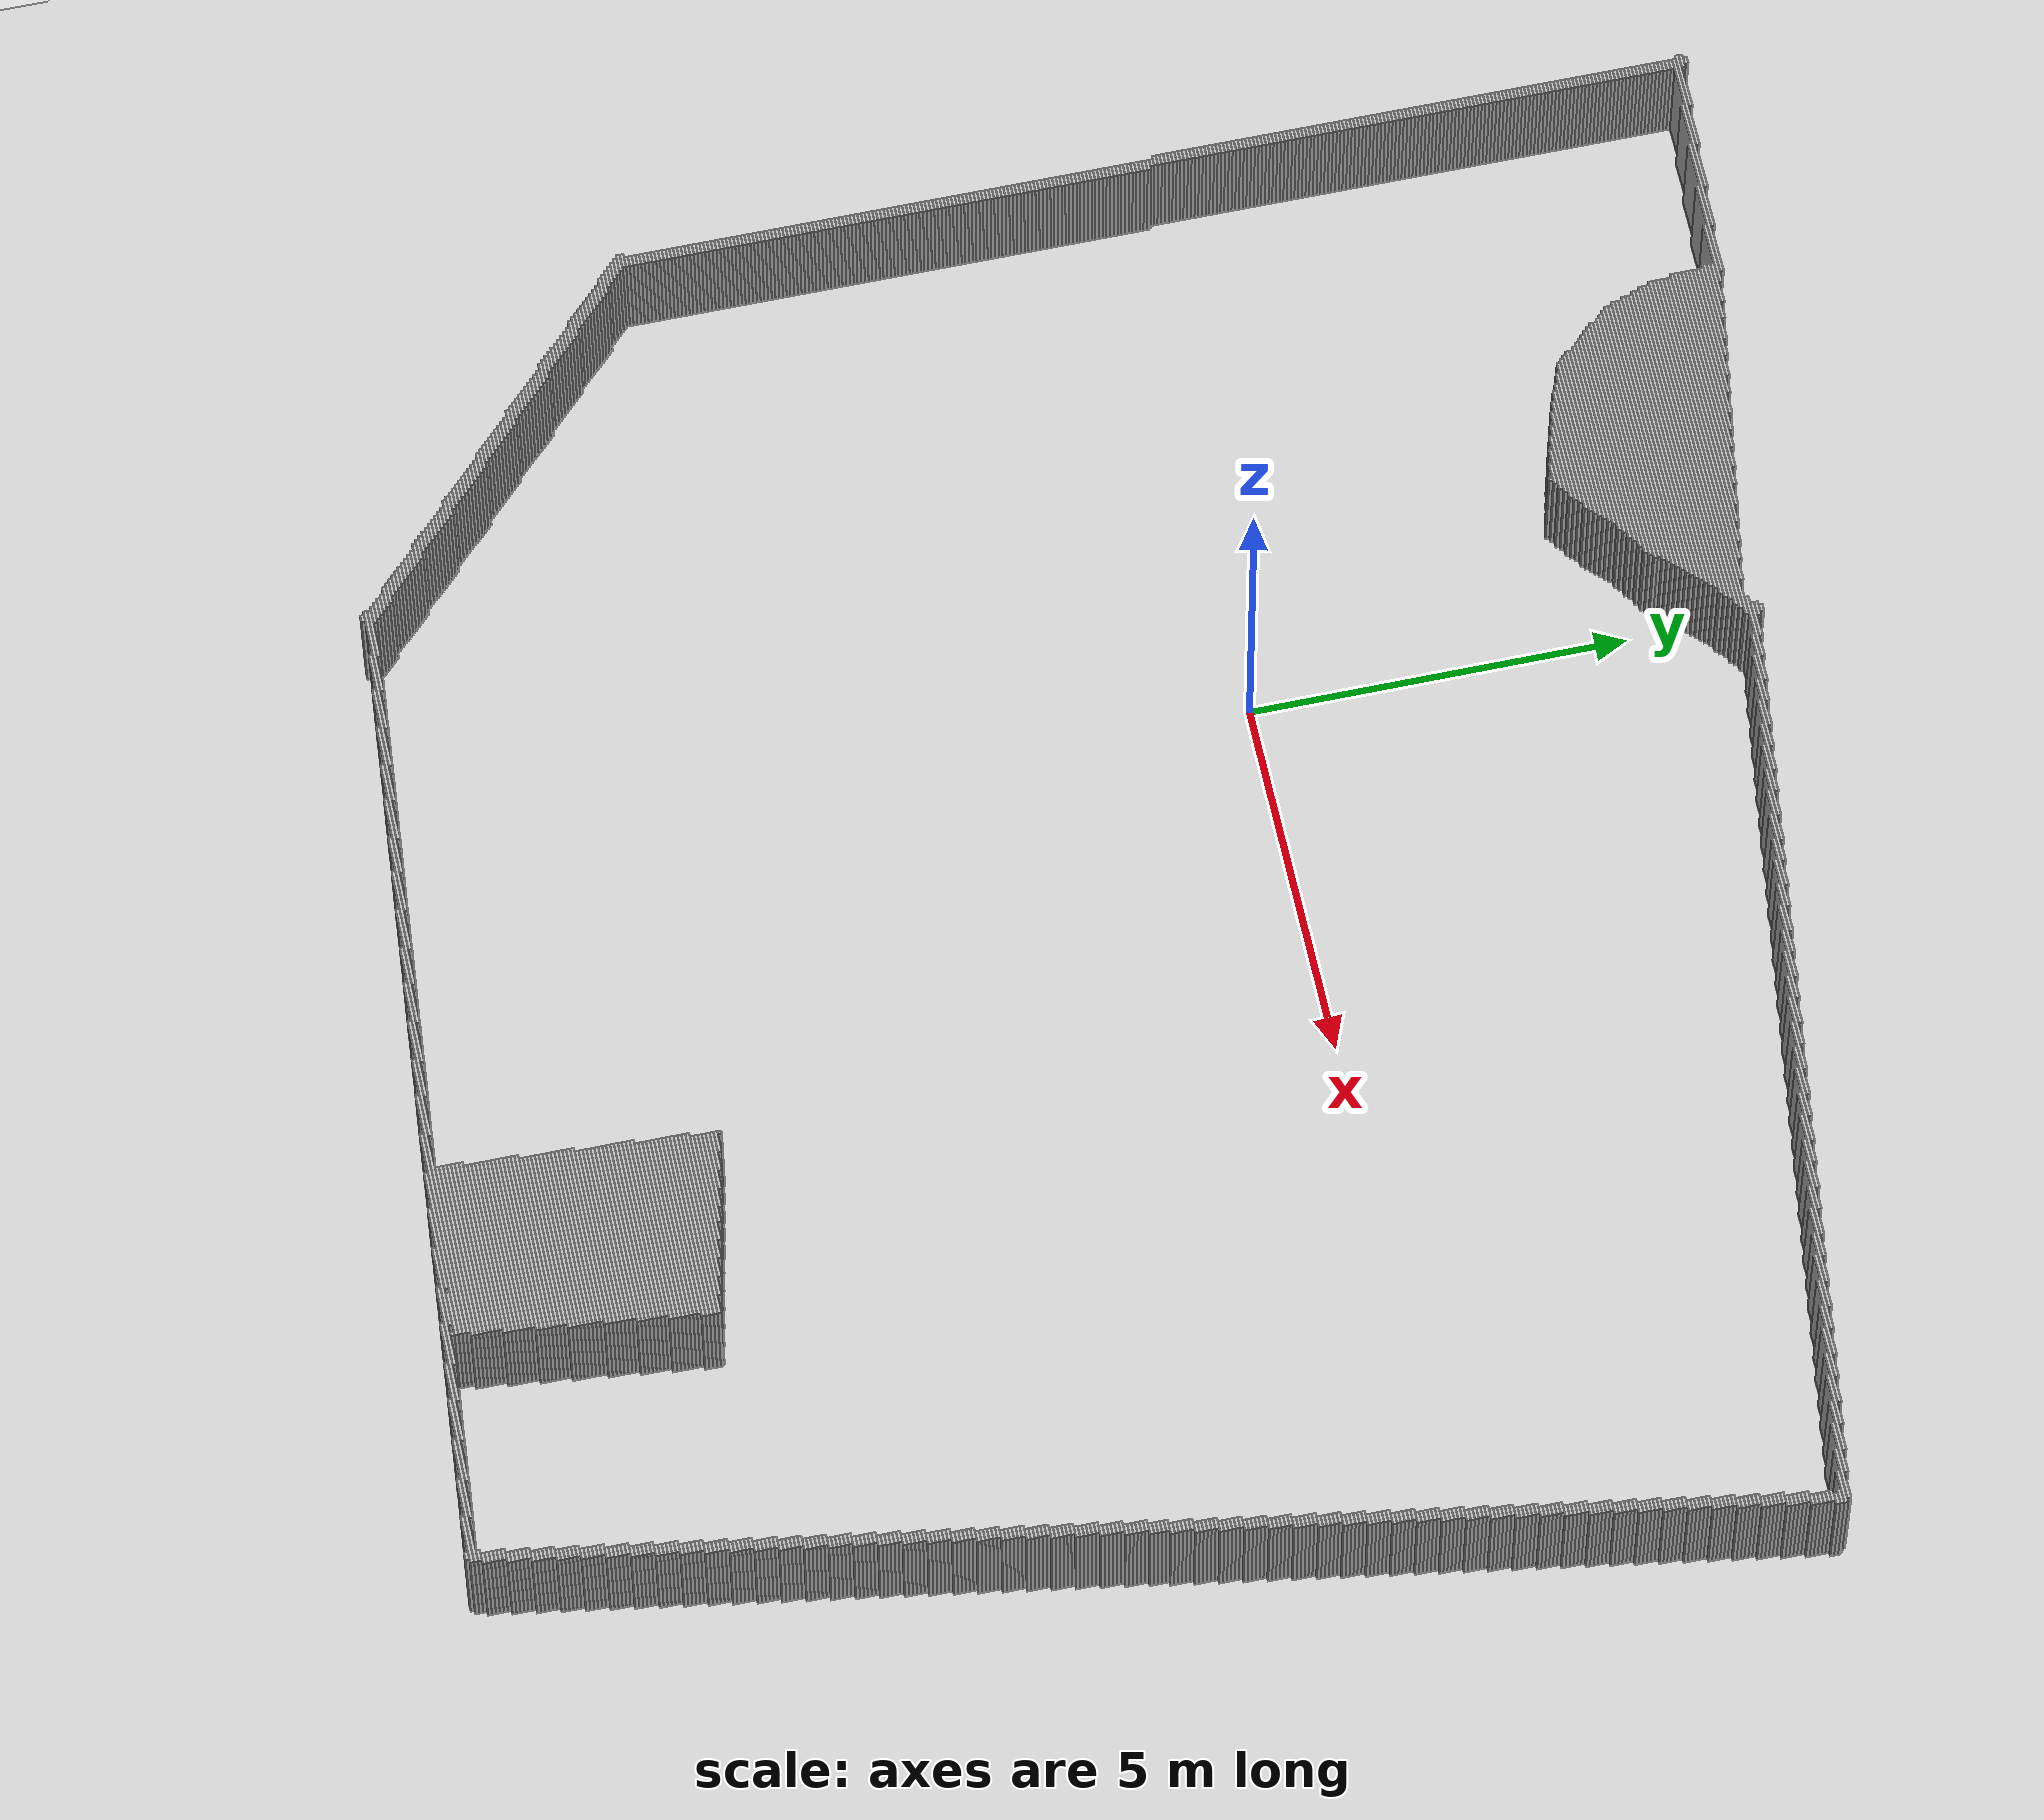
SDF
<?xml version="1.0" ?>
<sdf version="1.6">
  <world name="df_walled">
    <include><uri>model://sun</uri></include>
    <include><uri>model://ground_plane</uri></include>

    <physics type="ode">
      <max_step_size>0.001</max_step_size>
      <real_time_factor>1</real_time_factor>
      <real_time_update_rate>1000</real_time_update_rate>
    </physics>

    <scene>
      <ambient>0.4 0.4 0.4 1</ambient>
      <background>0.7 0.7 0.7 1</background>
      <shadows>false</shadows>
    </scene>

    <gravity>0 0 -9.8</gravity>

    <!-- All wall boxes are grouped into one static model so Gazebo treats
         them as immovable terrain. -->
    <model name="df_walls">
      <static>true</static>
      <link name="wall_00000">
        <pose>-7.5610 7.5410 0.7500 0 0 0</pose>
        <collision name="col">
          <geometry><box><size>0.1000 0.0500 1.5000</size></box></geometry>
        </collision>
        <visual name="vis">
          <geometry><box><size>0.1000 0.0500 1.5000</size></box></geometry>
          <material>
            <ambient>0.5 0.5 0.5 1</ambient>
            <diffuse>0.7 0.7 0.7 1</diffuse>
          </material>
        </visual>
      </link>
      <link name="wall_00001">
        <pose>-7.5610 7.4910 0.7500 0 0 0</pose>
        <collision name="col">
          <geometry><box><size>0.2000 0.0500 1.5000</size></box></geometry>
        </collision>
        <visual name="vis">
          <geometry><box><size>0.2000 0.0500 1.5000</size></box></geometry>
          <material>
            <ambient>0.5 0.5 0.5 1</ambient>
            <diffuse>0.7 0.7 0.7 1</diffuse>
          </material>
        </visual>
      </link>
      <link name="wall_00002">
        <pose>-7.2610 7.4410 0.7500 0 0 0</pose>
        <collision name="col">
          <geometry><box><size>0.8000 0.0500 1.5000</size></box></geometry>
        </collision>
        <visual name="vis">
          <geometry><box><size>0.8000 0.0500 1.5000</size></box></geometry>
          <material>
            <ambient>0.5 0.5 0.5 1</ambient>
            <diffuse>0.7 0.7 0.7 1</diffuse>
          </material>
        </visual>
      </link>
      <link name="wall_00003">
        <pose>-6.9360 7.3910 0.7500 0 0 0</pose>
        <collision name="col">
          <geometry><box><size>1.3500 0.0500 1.5000</size></box></geometry>
        </collision>
        <visual name="vis">
          <geometry><box><size>1.3500 0.0500 1.5000</size></box></geometry>
          <material>
            <ambient>0.5 0.5 0.5 1</ambient>
            <diffuse>0.7 0.7 0.7 1</diffuse>
          </material>
        </visual>
      </link>
      <link name="wall_00004">
        <pose>-7.5360 7.3410 0.7500 0 0 0</pose>
        <collision name="col">
          <geometry><box><size>0.1500 0.0500 1.5000</size></box></geometry>
        </collision>
        <visual name="vis">
          <geometry><box><size>0.1500 0.0500 1.5000</size></box></geometry>
          <material>
            <ambient>0.5 0.5 0.5 1</ambient>
            <diffuse>0.7 0.7 0.7 1</diffuse>
          </material>
        </visual>
      </link>
      <link name="wall_00005">
        <pose>-6.2610 7.3410 0.7500 0 0 0</pose>
        <collision name="col">
          <geometry><box><size>1.3000 0.0500 1.5000</size></box></geometry>
        </collision>
        <visual name="vis">
          <geometry><box><size>1.3000 0.0500 1.5000</size></box></geometry>
          <material>
            <ambient>0.5 0.5 0.5 1</ambient>
            <diffuse>0.7 0.7 0.7 1</diffuse>
          </material>
        </visual>
      </link>
      <link name="wall_00006">
        <pose>-7.5360 7.2910 0.7500 0 0 0</pose>
        <collision name="col">
          <geometry><box><size>0.1500 0.0500 1.5000</size></box></geometry>
        </collision>
        <visual name="vis">
          <geometry><box><size>0.1500 0.0500 1.5000</size></box></geometry>
          <material>
            <ambient>0.5 0.5 0.5 1</ambient>
            <diffuse>0.7 0.7 0.7 1</diffuse>
          </material>
        </visual>
      </link>
      <link name="wall_00007">
        <pose>-5.6610 7.2910 0.7500 0 0 0</pose>
        <collision name="col">
          <geometry><box><size>1.3000 0.0500 1.5000</size></box></geometry>
        </collision>
        <visual name="vis">
          <geometry><box><size>1.3000 0.0500 1.5000</size></box></geometry>
          <material>
            <ambient>0.5 0.5 0.5 1</ambient>
            <diffuse>0.7 0.7 0.7 1</diffuse>
          </material>
        </visual>
      </link>
      <link name="wall_00008">
        <pose>-7.5360 7.2410 0.7500 0 0 0</pose>
        <collision name="col">
          <geometry><box><size>0.1500 0.0500 1.5000</size></box></geometry>
        </collision>
        <visual name="vis">
          <geometry><box><size>0.1500 0.0500 1.5000</size></box></geometry>
          <material>
            <ambient>0.5 0.5 0.5 1</ambient>
            <diffuse>0.7 0.7 0.7 1</diffuse>
          </material>
        </visual>
      </link>
      <link name="wall_00009">
        <pose>-4.9860 7.2410 0.7500 0 0 0</pose>
        <collision name="col">
          <geometry><box><size>1.3500 0.0500 1.5000</size></box></geometry>
        </collision>
        <visual name="vis">
          <geometry><box><size>1.3500 0.0500 1.5000</size></box></geometry>
          <material>
            <ambient>0.5 0.5 0.5 1</ambient>
            <diffuse>0.7 0.7 0.7 1</diffuse>
          </material>
        </visual>
      </link>
      <link name="wall_00010">
        <pose>-7.5360 7.1910 0.7500 0 0 0</pose>
        <collision name="col">
          <geometry><box><size>0.1500 0.0500 1.5000</size></box></geometry>
        </collision>
        <visual name="vis">
          <geometry><box><size>0.1500 0.0500 1.5000</size></box></geometry>
          <material>
            <ambient>0.5 0.5 0.5 1</ambient>
            <diffuse>0.7 0.7 0.7 1</diffuse>
          </material>
        </visual>
      </link>
      <link name="wall_00011">
        <pose>-4.6110 7.1910 0.7500 0 0 0</pose>
        <collision name="col">
          <geometry><box><size>0.9000 0.0500 1.5000</size></box></geometry>
        </collision>
        <visual name="vis">
          <geometry><box><size>0.9000 0.0500 1.5000</size></box></geometry>
          <material>
            <ambient>0.5 0.5 0.5 1</ambient>
            <diffuse>0.7 0.7 0.7 1</diffuse>
          </material>
        </visual>
      </link>
      <link name="wall_00012">
        <pose>-7.5360 7.1410 0.7500 0 0 0</pose>
        <collision name="col">
          <geometry><box><size>0.1500 0.0500 1.5000</size></box></geometry>
        </collision>
        <visual name="vis">
          <geometry><box><size>0.1500 0.0500 1.5000</size></box></geometry>
          <material>
            <ambient>0.5 0.5 0.5 1</ambient>
            <diffuse>0.7 0.7 0.7 1</diffuse>
          </material>
        </visual>
      </link>
      <link name="wall_00013">
        <pose>-4.1610 7.1410 0.7500 0 0 0</pose>
        <collision name="col">
          <geometry><box><size>0.6000 0.0500 1.5000</size></box></geometry>
        </collision>
        <visual name="vis">
          <geometry><box><size>0.6000 0.0500 1.5000</size></box></geometry>
          <material>
            <ambient>0.5 0.5 0.5 1</ambient>
            <diffuse>0.7 0.7 0.7 1</diffuse>
          </material>
        </visual>
      </link>
      <link name="wall_00014">
        <pose>-7.5360 7.0910 0.7500 0 0 0</pose>
        <collision name="col">
          <geometry><box><size>0.1500 0.0500 1.5000</size></box></geometry>
        </collision>
        <visual name="vis">
          <geometry><box><size>0.1500 0.0500 1.5000</size></box></geometry>
          <material>
            <ambient>0.5 0.5 0.5 1</ambient>
            <diffuse>0.7 0.7 0.7 1</diffuse>
          </material>
        </visual>
      </link>
      <link name="wall_00015">
        <pose>-4.0360 7.0910 0.7500 0 0 0</pose>
        <collision name="col">
          <geometry><box><size>0.8500 0.0500 1.5000</size></box></geometry>
        </collision>
        <visual name="vis">
          <geometry><box><size>0.8500 0.0500 1.5000</size></box></geometry>
          <material>
            <ambient>0.5 0.5 0.5 1</ambient>
            <diffuse>0.7 0.7 0.7 1</diffuse>
          </material>
        </visual>
      </link>
      <link name="wall_00016">
        <pose>-7.5360 7.0410 0.7500 0 0 0</pose>
        <collision name="col">
          <geometry><box><size>0.1500 0.0500 1.5000</size></box></geometry>
        </collision>
        <visual name="vis">
          <geometry><box><size>0.1500 0.0500 1.5000</size></box></geometry>
          <material>
            <ambient>0.5 0.5 0.5 1</ambient>
            <diffuse>0.7 0.7 0.7 1</diffuse>
          </material>
        </visual>
      </link>
      <link name="wall_00017">
        <pose>-3.8860 7.0410 0.7500 0 0 0</pose>
        <collision name="col">
          <geometry><box><size>1.1500 0.0500 1.5000</size></box></geometry>
        </collision>
        <visual name="vis">
          <geometry><box><size>1.1500 0.0500 1.5000</size></box></geometry>
          <material>
            <ambient>0.5 0.5 0.5 1</ambient>
            <diffuse>0.7 0.7 0.7 1</diffuse>
          </material>
        </visual>
      </link>
      <link name="wall_00018">
        <pose>-7.5360 6.9910 0.7500 0 0 0</pose>
        <collision name="col">
          <geometry><box><size>0.1500 0.0500 1.5000</size></box></geometry>
        </collision>
        <visual name="vis">
          <geometry><box><size>0.1500 0.0500 1.5000</size></box></geometry>
          <material>
            <ambient>0.5 0.5 0.5 1</ambient>
            <diffuse>0.7 0.7 0.7 1</diffuse>
          </material>
        </visual>
      </link>
      <link name="wall_00019">
        <pose>-3.7360 6.9910 0.7500 0 0 0</pose>
        <collision name="col">
          <geometry><box><size>1.3500 0.0500 1.5000</size></box></geometry>
        </collision>
        <visual name="vis">
          <geometry><box><size>1.3500 0.0500 1.5000</size></box></geometry>
          <material>
            <ambient>0.5 0.5 0.5 1</ambient>
            <diffuse>0.7 0.7 0.7 1</diffuse>
          </material>
        </visual>
      </link>
      <link name="wall_00020">
        <pose>-7.5360 6.9410 0.7500 0 0 0</pose>
        <collision name="col">
          <geometry><box><size>0.1500 0.0500 1.5000</size></box></geometry>
        </collision>
        <visual name="vis">
          <geometry><box><size>0.1500 0.0500 1.5000</size></box></geometry>
          <material>
            <ambient>0.5 0.5 0.5 1</ambient>
            <diffuse>0.7 0.7 0.7 1</diffuse>
          </material>
        </visual>
      </link>
      <link name="wall_00021">
        <pose>-3.5860 6.9410 0.7500 0 0 0</pose>
        <collision name="col">
          <geometry><box><size>1.6500 0.0500 1.5000</size></box></geometry>
        </collision>
        <visual name="vis">
          <geometry><box><size>1.6500 0.0500 1.5000</size></box></geometry>
          <material>
            <ambient>0.5 0.5 0.5 1</ambient>
            <diffuse>0.7 0.7 0.7 1</diffuse>
          </material>
        </visual>
      </link>
      <link name="wall_00022">
        <pose>-7.5360 6.8910 0.7500 0 0 0</pose>
        <collision name="col">
          <geometry><box><size>0.1500 0.0500 1.5000</size></box></geometry>
        </collision>
        <visual name="vis">
          <geometry><box><size>0.1500 0.0500 1.5000</size></box></geometry>
          <material>
            <ambient>0.5 0.5 0.5 1</ambient>
            <diffuse>0.7 0.7 0.7 1</diffuse>
          </material>
        </visual>
      </link>
      <link name="wall_00023">
        <pose>-3.4610 6.8910 0.7500 0 0 0</pose>
        <collision name="col">
          <geometry><box><size>1.9000 0.0500 1.5000</size></box></geometry>
        </collision>
        <visual name="vis">
          <geometry><box><size>1.9000 0.0500 1.5000</size></box></geometry>
          <material>
            <ambient>0.5 0.5 0.5 1</ambient>
            <diffuse>0.7 0.7 0.7 1</diffuse>
          </material>
        </visual>
      </link>
      <link name="wall_00024">
        <pose>-7.5360 6.8410 0.7500 0 0 0</pose>
        <collision name="col">
          <geometry><box><size>0.1500 0.0500 1.5000</size></box></geometry>
        </collision>
        <visual name="vis">
          <geometry><box><size>0.1500 0.0500 1.5000</size></box></geometry>
          <material>
            <ambient>0.5 0.5 0.5 1</ambient>
            <diffuse>0.7 0.7 0.7 1</diffuse>
          </material>
        </visual>
      </link>
      <link name="wall_00025">
        <pose>-3.3110 6.8410 0.7500 0 0 0</pose>
        <collision name="col">
          <geometry><box><size>2.2000 0.0500 1.5000</size></box></geometry>
        </collision>
        <visual name="vis">
          <geometry><box><size>2.2000 0.0500 1.5000</size></box></geometry>
          <material>
            <ambient>0.5 0.5 0.5 1</ambient>
            <diffuse>0.7 0.7 0.7 1</diffuse>
          </material>
        </visual>
      </link>
      <link name="wall_00026">
        <pose>-7.5360 6.7910 0.7500 0 0 0</pose>
        <collision name="col">
          <geometry><box><size>0.1500 0.0500 1.5000</size></box></geometry>
        </collision>
        <visual name="vis">
          <geometry><box><size>0.1500 0.0500 1.5000</size></box></geometry>
          <material>
            <ambient>0.5 0.5 0.5 1</ambient>
            <diffuse>0.7 0.7 0.7 1</diffuse>
          </material>
        </visual>
      </link>
      <link name="wall_00027">
        <pose>-3.1860 6.7910 0.7500 0 0 0</pose>
        <collision name="col">
          <geometry><box><size>2.4500 0.0500 1.5000</size></box></geometry>
        </collision>
        <visual name="vis">
          <geometry><box><size>2.4500 0.0500 1.5000</size></box></geometry>
          <material>
            <ambient>0.5 0.5 0.5 1</ambient>
            <diffuse>0.7 0.7 0.7 1</diffuse>
          </material>
        </visual>
      </link>
      <link name="wall_00028">
        <pose>-7.5360 6.7410 0.7500 0 0 0</pose>
        <collision name="col">
          <geometry><box><size>0.1500 0.0500 1.5000</size></box></geometry>
        </collision>
        <visual name="vis">
          <geometry><box><size>0.1500 0.0500 1.5000</size></box></geometry>
          <material>
            <ambient>0.5 0.5 0.5 1</ambient>
            <diffuse>0.7 0.7 0.7 1</diffuse>
          </material>
        </visual>
      </link>
      <link name="wall_00029">
        <pose>-3.0610 6.7410 0.7500 0 0 0</pose>
        <collision name="col">
          <geometry><box><size>2.7000 0.0500 1.5000</size></box></geometry>
        </collision>
        <visual name="vis">
          <geometry><box><size>2.7000 0.0500 1.5000</size></box></geometry>
          <material>
            <ambient>0.5 0.5 0.5 1</ambient>
            <diffuse>0.7 0.7 0.7 1</diffuse>
          </material>
        </visual>
      </link>
      <link name="wall_00030">
        <pose>-7.5360 6.6910 0.7500 0 0 0</pose>
        <collision name="col">
          <geometry><box><size>0.1500 0.0500 1.5000</size></box></geometry>
        </collision>
        <visual name="vis">
          <geometry><box><size>0.1500 0.0500 1.5000</size></box></geometry>
          <material>
            <ambient>0.5 0.5 0.5 1</ambient>
            <diffuse>0.7 0.7 0.7 1</diffuse>
          </material>
        </visual>
      </link>
      <link name="wall_00031">
        <pose>-2.9110 6.6910 0.7500 0 0 0</pose>
        <collision name="col">
          <geometry><box><size>3.0000 0.0500 1.5000</size></box></geometry>
        </collision>
        <visual name="vis">
          <geometry><box><size>3.0000 0.0500 1.5000</size></box></geometry>
          <material>
            <ambient>0.5 0.5 0.5 1</ambient>
            <diffuse>0.7 0.7 0.7 1</diffuse>
          </material>
        </visual>
      </link>
      <link name="wall_00032">
        <pose>-7.5360 6.6410 0.7500 0 0 0</pose>
        <collision name="col">
          <geometry><box><size>0.1500 0.0500 1.5000</size></box></geometry>
        </collision>
        <visual name="vis">
          <geometry><box><size>0.1500 0.0500 1.5000</size></box></geometry>
          <material>
            <ambient>0.5 0.5 0.5 1</ambient>
            <diffuse>0.7 0.7 0.7 1</diffuse>
          </material>
        </visual>
      </link>
      <link name="wall_00033">
        <pose>-2.7860 6.6410 0.7500 0 0 0</pose>
        <collision name="col">
          <geometry><box><size>3.2500 0.0500 1.5000</size></box></geometry>
        </collision>
        <visual name="vis">
          <geometry><box><size>3.2500 0.0500 1.5000</size></box></geometry>
          <material>
            <ambient>0.5 0.5 0.5 1</ambient>
            <diffuse>0.7 0.7 0.7 1</diffuse>
          </material>
        </visual>
      </link>
      <link name="wall_00034">
        <pose>-7.5360 6.5910 0.7500 0 0 0</pose>
        <collision name="col">
          <geometry><box><size>0.1500 0.0500 1.5000</size></box></geometry>
        </collision>
        <visual name="vis">
          <geometry><box><size>0.1500 0.0500 1.5000</size></box></geometry>
          <material>
            <ambient>0.5 0.5 0.5 1</ambient>
            <diffuse>0.7 0.7 0.7 1</diffuse>
          </material>
        </visual>
      </link>
      <link name="wall_00035">
        <pose>-2.6360 6.5910 0.7500 0 0 0</pose>
        <collision name="col">
          <geometry><box><size>3.5500 0.0500 1.5000</size></box></geometry>
        </collision>
        <visual name="vis">
          <geometry><box><size>3.5500 0.0500 1.5000</size></box></geometry>
          <material>
            <ambient>0.5 0.5 0.5 1</ambient>
            <diffuse>0.7 0.7 0.7 1</diffuse>
          </material>
        </visual>
      </link>
      <link name="wall_00036">
        <pose>-7.5360 6.5410 0.7500 0 0 0</pose>
        <collision name="col">
          <geometry><box><size>0.1500 0.0500 1.5000</size></box></geometry>
        </collision>
        <visual name="vis">
          <geometry><box><size>0.1500 0.0500 1.5000</size></box></geometry>
          <material>
            <ambient>0.5 0.5 0.5 1</ambient>
            <diffuse>0.7 0.7 0.7 1</diffuse>
          </material>
        </visual>
      </link>
      <link name="wall_00037">
        <pose>-2.4860 6.5410 0.7500 0 0 0</pose>
        <collision name="col">
          <geometry><box><size>3.7500 0.0500 1.5000</size></box></geometry>
        </collision>
        <visual name="vis">
          <geometry><box><size>3.7500 0.0500 1.5000</size></box></geometry>
          <material>
            <ambient>0.5 0.5 0.5 1</ambient>
            <diffuse>0.7 0.7 0.7 1</diffuse>
          </material>
        </visual>
      </link>
      <link name="wall_00038">
        <pose>0.6890 6.5410 0.7500 0 0 0</pose>
        <collision name="col">
          <geometry><box><size>0.1000 0.0500 1.5000</size></box></geometry>
        </collision>
        <visual name="vis">
          <geometry><box><size>0.1000 0.0500 1.5000</size></box></geometry>
          <material>
            <ambient>0.5 0.5 0.5 1</ambient>
            <diffuse>0.7 0.7 0.7 1</diffuse>
          </material>
        </visual>
      </link>
      <link name="wall_00039">
        <pose>-7.5360 6.4910 0.7500 0 0 0</pose>
        <collision name="col">
          <geometry><box><size>0.1500 0.0500 1.5000</size></box></geometry>
        </collision>
        <visual name="vis">
          <geometry><box><size>0.1500 0.0500 1.5000</size></box></geometry>
          <material>
            <ambient>0.5 0.5 0.5 1</ambient>
            <diffuse>0.7 0.7 0.7 1</diffuse>
          </material>
        </visual>
      </link>
      <link name="wall_00040">
        <pose>-2.3360 6.4910 0.7500 0 0 0</pose>
        <collision name="col">
          <geometry><box><size>4.0500 0.0500 1.5000</size></box></geometry>
        </collision>
        <visual name="vis">
          <geometry><box><size>4.0500 0.0500 1.5000</size></box></geometry>
          <material>
            <ambient>0.5 0.5 0.5 1</ambient>
            <diffuse>0.7 0.7 0.7 1</diffuse>
          </material>
        </visual>
      </link>
      <link name="wall_00041">
        <pose>0.6890 6.4910 0.7500 0 0 0</pose>
        <collision name="col">
          <geometry><box><size>0.2000 0.0500 1.5000</size></box></geometry>
        </collision>
        <visual name="vis">
          <geometry><box><size>0.2000 0.0500 1.5000</size></box></geometry>
          <material>
            <ambient>0.5 0.5 0.5 1</ambient>
            <diffuse>0.7 0.7 0.7 1</diffuse>
          </material>
        </visual>
      </link>
      <link name="wall_00042">
        <pose>-7.5360 6.4410 0.7500 0 0 0</pose>
        <collision name="col">
          <geometry><box><size>0.1500 0.0500 1.5000</size></box></geometry>
        </collision>
        <visual name="vis">
          <geometry><box><size>0.1500 0.0500 1.5000</size></box></geometry>
          <material>
            <ambient>0.5 0.5 0.5 1</ambient>
            <diffuse>0.7 0.7 0.7 1</diffuse>
          </material>
        </visual>
      </link>
      <link name="wall_00043">
        <pose>-2.2110 6.4410 0.7500 0 0 0</pose>
        <collision name="col">
          <geometry><box><size>4.3000 0.0500 1.5000</size></box></geometry>
        </collision>
        <visual name="vis">
          <geometry><box><size>4.3000 0.0500 1.5000</size></box></geometry>
          <material>
            <ambient>0.5 0.5 0.5 1</ambient>
            <diffuse>0.7 0.7 0.7 1</diffuse>
          </material>
        </visual>
      </link>
      <link name="wall_00044">
        <pose>0.8390 6.4410 0.7500 0 0 0</pose>
        <collision name="col">
          <geometry><box><size>0.5000 0.0500 1.5000</size></box></geometry>
        </collision>
        <visual name="vis">
          <geometry><box><size>0.5000 0.0500 1.5000</size></box></geometry>
          <material>
            <ambient>0.5 0.5 0.5 1</ambient>
            <diffuse>0.7 0.7 0.7 1</diffuse>
          </material>
        </visual>
      </link>
      <link name="wall_00045">
        <pose>-7.5360 6.3910 0.7500 0 0 0</pose>
        <collision name="col">
          <geometry><box><size>0.1500 0.0500 1.5000</size></box></geometry>
        </collision>
        <visual name="vis">
          <geometry><box><size>0.1500 0.0500 1.5000</size></box></geometry>
          <material>
            <ambient>0.5 0.5 0.5 1</ambient>
            <diffuse>0.7 0.7 0.7 1</diffuse>
          </material>
        </visual>
      </link>
      <link name="wall_00046">
        <pose>-2.0610 6.3910 0.7500 0 0 0</pose>
        <collision name="col">
          <geometry><box><size>4.6000 0.0500 1.5000</size></box></geometry>
        </collision>
        <visual name="vis">
          <geometry><box><size>4.6000 0.0500 1.5000</size></box></geometry>
          <material>
            <ambient>0.5 0.5 0.5 1</ambient>
            <diffuse>0.7 0.7 0.7 1</diffuse>
          </material>
        </visual>
      </link>
      <link name="wall_00047">
        <pose>0.9390 6.3910 0.7500 0 0 0</pose>
        <collision name="col">
          <geometry><box><size>0.9000 0.0500 1.5000</size></box></geometry>
        </collision>
        <visual name="vis">
          <geometry><box><size>0.9000 0.0500 1.5000</size></box></geometry>
          <material>
            <ambient>0.5 0.5 0.5 1</ambient>
            <diffuse>0.7 0.7 0.7 1</diffuse>
          </material>
        </visual>
      </link>
      <link name="wall_00048">
        <pose>-7.5360 6.3410 0.7500 0 0 0</pose>
        <collision name="col">
          <geometry><box><size>0.1500 0.0500 1.5000</size></box></geometry>
        </collision>
        <visual name="vis">
          <geometry><box><size>0.1500 0.0500 1.5000</size></box></geometry>
          <material>
            <ambient>0.5 0.5 0.5 1</ambient>
            <diffuse>0.7 0.7 0.7 1</diffuse>
          </material>
        </visual>
      </link>
      <link name="wall_00049">
        <pose>-1.8110 6.3410 0.7500 0 0 0</pose>
        <collision name="col">
          <geometry><box><size>5.1000 0.0500 1.5000</size></box></geometry>
        </collision>
        <visual name="vis">
          <geometry><box><size>5.1000 0.0500 1.5000</size></box></geometry>
          <material>
            <ambient>0.5 0.5 0.5 1</ambient>
            <diffuse>0.7 0.7 0.7 1</diffuse>
          </material>
        </visual>
      </link>
      <link name="wall_00050">
        <pose>1.3890 6.3410 0.7500 0 0 0</pose>
        <collision name="col">
          <geometry><box><size>0.7000 0.0500 1.5000</size></box></geometry>
        </collision>
        <visual name="vis">
          <geometry><box><size>0.7000 0.0500 1.5000</size></box></geometry>
          <material>
            <ambient>0.5 0.5 0.5 1</ambient>
            <diffuse>0.7 0.7 0.7 1</diffuse>
          </material>
        </visual>
      </link>
      <link name="wall_00051">
        <pose>-7.5360 6.2910 0.7500 0 0 0</pose>
        <collision name="col">
          <geometry><box><size>0.1500 0.0500 1.5000</size></box></geometry>
        </collision>
        <visual name="vis">
          <geometry><box><size>0.1500 0.0500 1.5000</size></box></geometry>
          <material>
            <ambient>0.5 0.5 0.5 1</ambient>
            <diffuse>0.7 0.7 0.7 1</diffuse>
          </material>
        </visual>
      </link>
      <link name="wall_00052">
        <pose>-1.8610 6.2910 0.7500 0 0 0</pose>
        <collision name="col">
          <geometry><box><size>5.0000 0.0500 1.5000</size></box></geometry>
        </collision>
        <visual name="vis">
          <geometry><box><size>5.0000 0.0500 1.5000</size></box></geometry>
          <material>
            <ambient>0.5 0.5 0.5 1</ambient>
            <diffuse>0.7 0.7 0.7 1</diffuse>
          </material>
        </visual>
      </link>
      <link name="wall_00053">
        <pose>1.6890 6.2910 0.7500 0 0 0</pose>
        <collision name="col">
          <geometry><box><size>0.7000 0.0500 1.5000</size></box></geometry>
        </collision>
        <visual name="vis">
          <geometry><box><size>0.7000 0.0500 1.5000</size></box></geometry>
          <material>
            <ambient>0.5 0.5 0.5 1</ambient>
            <diffuse>0.7 0.7 0.7 1</diffuse>
          </material>
        </visual>
      </link>
      <link name="wall_00054">
        <pose>-7.5360 6.2410 0.7500 0 0 0</pose>
        <collision name="col">
          <geometry><box><size>0.1500 0.0500 1.5000</size></box></geometry>
        </collision>
        <visual name="vis">
          <geometry><box><size>0.1500 0.0500 1.5000</size></box></geometry>
          <material>
            <ambient>0.5 0.5 0.5 1</ambient>
            <diffuse>0.7 0.7 0.7 1</diffuse>
          </material>
        </visual>
      </link>
      <link name="wall_00055">
        <pose>-1.8610 6.2410 0.7500 0 0 0</pose>
        <collision name="col">
          <geometry><box><size>4.9000 0.0500 1.5000</size></box></geometry>
        </collision>
        <visual name="vis">
          <geometry><box><size>4.9000 0.0500 1.5000</size></box></geometry>
          <material>
            <ambient>0.5 0.5 0.5 1</ambient>
            <diffuse>0.7 0.7 0.7 1</diffuse>
          </material>
        </visual>
      </link>
      <link name="wall_00056">
        <pose>2.0390 6.2410 0.7500 0 0 0</pose>
        <collision name="col">
          <geometry><box><size>0.7000 0.0500 1.5000</size></box></geometry>
        </collision>
        <visual name="vis">
          <geometry><box><size>0.7000 0.0500 1.5000</size></box></geometry>
          <material>
            <ambient>0.5 0.5 0.5 1</ambient>
            <diffuse>0.7 0.7 0.7 1</diffuse>
          </material>
        </visual>
      </link>
      <link name="wall_00057">
        <pose>-7.5360 6.1910 0.7500 0 0 0</pose>
        <collision name="col">
          <geometry><box><size>0.1500 0.0500 1.5000</size></box></geometry>
        </collision>
        <visual name="vis">
          <geometry><box><size>0.1500 0.0500 1.5000</size></box></geometry>
          <material>
            <ambient>0.5 0.5 0.5 1</ambient>
            <diffuse>0.7 0.7 0.7 1</diffuse>
          </material>
        </visual>
      </link>
      <link name="wall_00058">
        <pose>-1.9110 6.1910 0.7500 0 0 0</pose>
        <collision name="col">
          <geometry><box><size>4.8000 0.0500 1.5000</size></box></geometry>
        </collision>
        <visual name="vis">
          <geometry><box><size>4.8000 0.0500 1.5000</size></box></geometry>
          <material>
            <ambient>0.5 0.5 0.5 1</ambient>
            <diffuse>0.7 0.7 0.7 1</diffuse>
          </material>
        </visual>
      </link>
      <link name="wall_00059">
        <pose>2.3390 6.1910 0.7500 0 0 0</pose>
        <collision name="col">
          <geometry><box><size>0.7000 0.0500 1.5000</size></box></geometry>
        </collision>
        <visual name="vis">
          <geometry><box><size>0.7000 0.0500 1.5000</size></box></geometry>
          <material>
            <ambient>0.5 0.5 0.5 1</ambient>
            <diffuse>0.7 0.7 0.7 1</diffuse>
          </material>
        </visual>
      </link>
      <link name="wall_00060">
        <pose>-7.5360 6.1410 0.7500 0 0 0</pose>
        <collision name="col">
          <geometry><box><size>0.1500 0.0500 1.5000</size></box></geometry>
        </collision>
        <visual name="vis">
          <geometry><box><size>0.1500 0.0500 1.5000</size></box></geometry>
          <material>
            <ambient>0.5 0.5 0.5 1</ambient>
            <diffuse>0.7 0.7 0.7 1</diffuse>
          </material>
        </visual>
      </link>
      <link name="wall_00061">
        <pose>-1.9360 6.1410 0.7500 0 0 0</pose>
        <collision name="col">
          <geometry><box><size>4.7500 0.0500 1.5000</size></box></geometry>
        </collision>
        <visual name="vis">
          <geometry><box><size>4.7500 0.0500 1.5000</size></box></geometry>
          <material>
            <ambient>0.5 0.5 0.5 1</ambient>
            <diffuse>0.7 0.7 0.7 1</diffuse>
          </material>
        </visual>
      </link>
      <link name="wall_00062">
        <pose>2.6890 6.1410 0.7500 0 0 0</pose>
        <collision name="col">
          <geometry><box><size>0.7000 0.0500 1.5000</size></box></geometry>
        </collision>
        <visual name="vis">
          <geometry><box><size>0.7000 0.0500 1.5000</size></box></geometry>
          <material>
            <ambient>0.5 0.5 0.5 1</ambient>
            <diffuse>0.7 0.7 0.7 1</diffuse>
          </material>
        </visual>
      </link>
      <link name="wall_00063">
        <pose>-7.5360 6.0910 0.7500 0 0 0</pose>
        <collision name="col">
          <geometry><box><size>0.1500 0.0500 1.5000</size></box></geometry>
        </collision>
        <visual name="vis">
          <geometry><box><size>0.1500 0.0500 1.5000</size></box></geometry>
          <material>
            <ambient>0.5 0.5 0.5 1</ambient>
            <diffuse>0.7 0.7 0.7 1</diffuse>
          </material>
        </visual>
      </link>
      <link name="wall_00064">
        <pose>-1.9360 6.0910 0.7500 0 0 0</pose>
        <collision name="col">
          <geometry><box><size>4.6500 0.0500 1.5000</size></box></geometry>
        </collision>
        <visual name="vis">
          <geometry><box><size>4.6500 0.0500 1.5000</size></box></geometry>
          <material>
            <ambient>0.5 0.5 0.5 1</ambient>
            <diffuse>0.7 0.7 0.7 1</diffuse>
          </material>
        </visual>
      </link>
      <link name="wall_00065">
        <pose>2.9890 6.0910 0.7500 0 0 0</pose>
        <collision name="col">
          <geometry><box><size>0.7000 0.0500 1.5000</size></box></geometry>
        </collision>
        <visual name="vis">
          <geometry><box><size>0.7000 0.0500 1.5000</size></box></geometry>
          <material>
            <ambient>0.5 0.5 0.5 1</ambient>
            <diffuse>0.7 0.7 0.7 1</diffuse>
          </material>
        </visual>
      </link>
      <link name="wall_00066">
        <pose>-7.5360 6.0410 0.7500 0 0 0</pose>
        <collision name="col">
          <geometry><box><size>0.1500 0.0500 1.5000</size></box></geometry>
        </collision>
        <visual name="vis">
          <geometry><box><size>0.1500 0.0500 1.5000</size></box></geometry>
          <material>
            <ambient>0.5 0.5 0.5 1</ambient>
            <diffuse>0.7 0.7 0.7 1</diffuse>
          </material>
        </visual>
      </link>
      <link name="wall_00067">
        <pose>-1.9860 6.0410 0.7500 0 0 0</pose>
        <collision name="col">
          <geometry><box><size>4.5500 0.0500 1.5000</size></box></geometry>
        </collision>
        <visual name="vis">
          <geometry><box><size>4.5500 0.0500 1.5000</size></box></geometry>
          <material>
            <ambient>0.5 0.5 0.5 1</ambient>
            <diffuse>0.7 0.7 0.7 1</diffuse>
          </material>
        </visual>
      </link>
      <link name="wall_00068">
        <pose>3.3390 6.0410 0.7500 0 0 0</pose>
        <collision name="col">
          <geometry><box><size>0.7000 0.0500 1.5000</size></box></geometry>
        </collision>
        <visual name="vis">
          <geometry><box><size>0.7000 0.0500 1.5000</size></box></geometry>
          <material>
            <ambient>0.5 0.5 0.5 1</ambient>
            <diffuse>0.7 0.7 0.7 1</diffuse>
          </material>
        </visual>
      </link>
      <link name="wall_00069">
        <pose>-7.5360 5.9910 0.7500 0 0 0</pose>
        <collision name="col">
          <geometry><box><size>0.1500 0.0500 1.5000</size></box></geometry>
        </collision>
        <visual name="vis">
          <geometry><box><size>0.1500 0.0500 1.5000</size></box></geometry>
          <material>
            <ambient>0.5 0.5 0.5 1</ambient>
            <diffuse>0.7 0.7 0.7 1</diffuse>
          </material>
        </visual>
      </link>
      <link name="wall_00070">
        <pose>-1.9860 5.9910 0.7500 0 0 0</pose>
        <collision name="col">
          <geometry><box><size>4.4500 0.0500 1.5000</size></box></geometry>
        </collision>
        <visual name="vis">
          <geometry><box><size>4.4500 0.0500 1.5000</size></box></geometry>
          <material>
            <ambient>0.5 0.5 0.5 1</ambient>
            <diffuse>0.7 0.7 0.7 1</diffuse>
          </material>
        </visual>
      </link>
      <link name="wall_00071">
        <pose>3.6640 5.9910 0.7500 0 0 0</pose>
        <collision name="col">
          <geometry><box><size>0.7500 0.0500 1.5000</size></box></geometry>
        </collision>
        <visual name="vis">
          <geometry><box><size>0.7500 0.0500 1.5000</size></box></geometry>
          <material>
            <ambient>0.5 0.5 0.5 1</ambient>
            <diffuse>0.7 0.7 0.7 1</diffuse>
          </material>
        </visual>
      </link>
      <link name="wall_00072">
        <pose>-7.5360 5.9410 0.7500 0 0 0</pose>
        <collision name="col">
          <geometry><box><size>0.1500 0.0500 1.5000</size></box></geometry>
        </collision>
        <visual name="vis">
          <geometry><box><size>0.1500 0.0500 1.5000</size></box></geometry>
          <material>
            <ambient>0.5 0.5 0.5 1</ambient>
            <diffuse>0.7 0.7 0.7 1</diffuse>
          </material>
        </visual>
      </link>
      <link name="wall_00073">
        <pose>-2.0110 5.9410 0.7500 0 0 0</pose>
        <collision name="col">
          <geometry><box><size>4.4000 0.0500 1.5000</size></box></geometry>
        </collision>
        <visual name="vis">
          <geometry><box><size>4.4000 0.0500 1.5000</size></box></geometry>
          <material>
            <ambient>0.5 0.5 0.5 1</ambient>
            <diffuse>0.7 0.7 0.7 1</diffuse>
          </material>
        </visual>
      </link>
      <link name="wall_00074">
        <pose>3.9890 5.9410 0.7500 0 0 0</pose>
        <collision name="col">
          <geometry><box><size>0.7000 0.0500 1.5000</size></box></geometry>
        </collision>
        <visual name="vis">
          <geometry><box><size>0.7000 0.0500 1.5000</size></box></geometry>
          <material>
            <ambient>0.5 0.5 0.5 1</ambient>
            <diffuse>0.7 0.7 0.7 1</diffuse>
          </material>
        </visual>
      </link>
      <link name="wall_00075">
        <pose>-7.5360 5.8910 0.7500 0 0 0</pose>
        <collision name="col">
          <geometry><box><size>0.1500 0.0500 1.5000</size></box></geometry>
        </collision>
        <visual name="vis">
          <geometry><box><size>0.1500 0.0500 1.5000</size></box></geometry>
          <material>
            <ambient>0.5 0.5 0.5 1</ambient>
            <diffuse>0.7 0.7 0.7 1</diffuse>
          </material>
        </visual>
      </link>
      <link name="wall_00076">
        <pose>-2.0360 5.8910 0.7500 0 0 0</pose>
        <collision name="col">
          <geometry><box><size>4.3500 0.0500 1.5000</size></box></geometry>
        </collision>
        <visual name="vis">
          <geometry><box><size>4.3500 0.0500 1.5000</size></box></geometry>
          <material>
            <ambient>0.5 0.5 0.5 1</ambient>
            <diffuse>0.7 0.7 0.7 1</diffuse>
          </material>
        </visual>
      </link>
      <link name="wall_00077">
        <pose>4.3390 5.8910 0.7500 0 0 0</pose>
        <collision name="col">
          <geometry><box><size>0.7000 0.0500 1.5000</size></box></geometry>
        </collision>
        <visual name="vis">
          <geometry><box><size>0.7000 0.0500 1.5000</size></box></geometry>
          <material>
            <ambient>0.5 0.5 0.5 1</ambient>
            <diffuse>0.7 0.7 0.7 1</diffuse>
          </material>
        </visual>
      </link>
      <link name="wall_00078">
        <pose>-7.5360 5.8410 0.7500 0 0 0</pose>
        <collision name="col">
          <geometry><box><size>0.1500 0.0500 1.5000</size></box></geometry>
        </collision>
        <visual name="vis">
          <geometry><box><size>0.1500 0.0500 1.5000</size></box></geometry>
          <material>
            <ambient>0.5 0.5 0.5 1</ambient>
            <diffuse>0.7 0.7 0.7 1</diffuse>
          </material>
        </visual>
      </link>
      <link name="wall_00079">
        <pose>-2.0360 5.8410 0.7500 0 0 0</pose>
        <collision name="col">
          <geometry><box><size>4.2500 0.0500 1.5000</size></box></geometry>
        </collision>
        <visual name="vis">
          <geometry><box><size>4.2500 0.0500 1.5000</size></box></geometry>
          <material>
            <ambient>0.5 0.5 0.5 1</ambient>
            <diffuse>0.7 0.7 0.7 1</diffuse>
          </material>
        </visual>
      </link>
      <link name="wall_00080">
        <pose>4.6390 5.8410 0.7500 0 0 0</pose>
        <collision name="col">
          <geometry><box><size>0.7000 0.0500 1.5000</size></box></geometry>
        </collision>
        <visual name="vis">
          <geometry><box><size>0.7000 0.0500 1.5000</size></box></geometry>
          <material>
            <ambient>0.5 0.5 0.5 1</ambient>
            <diffuse>0.7 0.7 0.7 1</diffuse>
          </material>
        </visual>
      </link>
      <link name="wall_00081">
        <pose>-7.5360 5.7910 0.7500 0 0 0</pose>
        <collision name="col">
          <geometry><box><size>0.1500 0.0500 1.5000</size></box></geometry>
        </collision>
        <visual name="vis">
          <geometry><box><size>0.1500 0.0500 1.5000</size></box></geometry>
          <material>
            <ambient>0.5 0.5 0.5 1</ambient>
            <diffuse>0.7 0.7 0.7 1</diffuse>
          </material>
        </visual>
      </link>
      <link name="wall_00082">
        <pose>-2.0610 5.7910 0.7500 0 0 0</pose>
        <collision name="col">
          <geometry><box><size>4.2000 0.0500 1.5000</size></box></geometry>
        </collision>
        <visual name="vis">
          <geometry><box><size>4.2000 0.0500 1.5000</size></box></geometry>
          <material>
            <ambient>0.5 0.5 0.5 1</ambient>
            <diffuse>0.7 0.7 0.7 1</diffuse>
          </material>
        </visual>
      </link>
      <link name="wall_00083">
        <pose>4.9890 5.7910 0.7500 0 0 0</pose>
        <collision name="col">
          <geometry><box><size>0.7000 0.0500 1.5000</size></box></geometry>
        </collision>
        <visual name="vis">
          <geometry><box><size>0.7000 0.0500 1.5000</size></box></geometry>
          <material>
            <ambient>0.5 0.5 0.5 1</ambient>
            <diffuse>0.7 0.7 0.7 1</diffuse>
          </material>
        </visual>
      </link>
      <link name="wall_00084">
        <pose>-7.5360 5.7410 0.7500 0 0 0</pose>
        <collision name="col">
          <geometry><box><size>0.1500 0.0500 1.5000</size></box></geometry>
        </collision>
        <visual name="vis">
          <geometry><box><size>0.1500 0.0500 1.5000</size></box></geometry>
          <material>
            <ambient>0.5 0.5 0.5 1</ambient>
            <diffuse>0.7 0.7 0.7 1</diffuse>
          </material>
        </visual>
      </link>
      <link name="wall_00085">
        <pose>-2.0860 5.7410 0.7500 0 0 0</pose>
        <collision name="col">
          <geometry><box><size>4.1500 0.0500 1.5000</size></box></geometry>
        </collision>
        <visual name="vis">
          <geometry><box><size>4.1500 0.0500 1.5000</size></box></geometry>
          <material>
            <ambient>0.5 0.5 0.5 1</ambient>
            <diffuse>0.7 0.7 0.7 1</diffuse>
          </material>
        </visual>
      </link>
      <link name="wall_00086">
        <pose>5.2890 5.7410 0.7500 0 0 0</pose>
        <collision name="col">
          <geometry><box><size>0.7000 0.0500 1.5000</size></box></geometry>
        </collision>
        <visual name="vis">
          <geometry><box><size>0.7000 0.0500 1.5000</size></box></geometry>
          <material>
            <ambient>0.5 0.5 0.5 1</ambient>
            <diffuse>0.7 0.7 0.7 1</diffuse>
          </material>
        </visual>
      </link>
      <link name="wall_00087">
        <pose>-7.5360 5.6910 0.7500 0 0 0</pose>
        <collision name="col">
          <geometry><box><size>0.1500 0.0500 1.5000</size></box></geometry>
        </collision>
        <visual name="vis">
          <geometry><box><size>0.1500 0.0500 1.5000</size></box></geometry>
          <material>
            <ambient>0.5 0.5 0.5 1</ambient>
            <diffuse>0.7 0.7 0.7 1</diffuse>
          </material>
        </visual>
      </link>
      <link name="wall_00088">
        <pose>-2.0860 5.6910 0.7500 0 0 0</pose>
        <collision name="col">
          <geometry><box><size>4.0500 0.0500 1.5000</size></box></geometry>
        </collision>
        <visual name="vis">
          <geometry><box><size>4.0500 0.0500 1.5000</size></box></geometry>
          <material>
            <ambient>0.5 0.5 0.5 1</ambient>
            <diffuse>0.7 0.7 0.7 1</diffuse>
          </material>
        </visual>
      </link>
      <link name="wall_00089">
        <pose>5.6390 5.6910 0.7500 0 0 0</pose>
        <collision name="col">
          <geometry><box><size>0.7000 0.0500 1.5000</size></box></geometry>
        </collision>
        <visual name="vis">
          <geometry><box><size>0.7000 0.0500 1.5000</size></box></geometry>
          <material>
            <ambient>0.5 0.5 0.5 1</ambient>
            <diffuse>0.7 0.7 0.7 1</diffuse>
          </material>
        </visual>
      </link>
      <link name="wall_00090">
        <pose>-7.5360 5.6410 0.7500 0 0 0</pose>
        <collision name="col">
          <geometry><box><size>0.1500 0.0500 1.5000</size></box></geometry>
        </collision>
        <visual name="vis">
          <geometry><box><size>0.1500 0.0500 1.5000</size></box></geometry>
          <material>
            <ambient>0.5 0.5 0.5 1</ambient>
            <diffuse>0.7 0.7 0.7 1</diffuse>
          </material>
        </visual>
      </link>
      <link name="wall_00091">
        <pose>-2.1110 5.6410 0.7500 0 0 0</pose>
        <collision name="col">
          <geometry><box><size>4.0000 0.0500 1.5000</size></box></geometry>
        </collision>
        <visual name="vis">
          <geometry><box><size>4.0000 0.0500 1.5000</size></box></geometry>
          <material>
            <ambient>0.5 0.5 0.5 1</ambient>
            <diffuse>0.7 0.7 0.7 1</diffuse>
          </material>
        </visual>
      </link>
      <link name="wall_00092">
        <pose>5.9390 5.6410 0.7500 0 0 0</pose>
        <collision name="col">
          <geometry><box><size>0.7000 0.0500 1.5000</size></box></geometry>
        </collision>
        <visual name="vis">
          <geometry><box><size>0.7000 0.0500 1.5000</size></box></geometry>
          <material>
            <ambient>0.5 0.5 0.5 1</ambient>
            <diffuse>0.7 0.7 0.7 1</diffuse>
          </material>
        </visual>
      </link>
      <link name="wall_00093">
        <pose>-7.5360 5.5910 0.7500 0 0 0</pose>
        <collision name="col">
          <geometry><box><size>0.1500 0.0500 1.5000</size></box></geometry>
        </collision>
        <visual name="vis">
          <geometry><box><size>0.1500 0.0500 1.5000</size></box></geometry>
          <material>
            <ambient>0.5 0.5 0.5 1</ambient>
            <diffuse>0.7 0.7 0.7 1</diffuse>
          </material>
        </visual>
      </link>
      <link name="wall_00094">
        <pose>-2.1110 5.5910 0.7500 0 0 0</pose>
        <collision name="col">
          <geometry><box><size>3.9000 0.0500 1.5000</size></box></geometry>
        </collision>
        <visual name="vis">
          <geometry><box><size>3.9000 0.0500 1.5000</size></box></geometry>
          <material>
            <ambient>0.5 0.5 0.5 1</ambient>
            <diffuse>0.7 0.7 0.7 1</diffuse>
          </material>
        </visual>
      </link>
      <link name="wall_00095">
        <pose>6.2890 5.5910 0.7500 0 0 0</pose>
        <collision name="col">
          <geometry><box><size>0.7000 0.0500 1.5000</size></box></geometry>
        </collision>
        <visual name="vis">
          <geometry><box><size>0.7000 0.0500 1.5000</size></box></geometry>
          <material>
            <ambient>0.5 0.5 0.5 1</ambient>
            <diffuse>0.7 0.7 0.7 1</diffuse>
          </material>
        </visual>
      </link>
      <link name="wall_00096">
        <pose>-7.5360 5.5410 0.7500 0 0 0</pose>
        <collision name="col">
          <geometry><box><size>0.1500 0.0500 1.5000</size></box></geometry>
        </collision>
        <visual name="vis">
          <geometry><box><size>0.1500 0.0500 1.5000</size></box></geometry>
          <material>
            <ambient>0.5 0.5 0.5 1</ambient>
            <diffuse>0.7 0.7 0.7 1</diffuse>
          </material>
        </visual>
      </link>
      <link name="wall_00097">
        <pose>-2.1110 5.5410 0.7500 0 0 0</pose>
        <collision name="col">
          <geometry><box><size>3.8000 0.0500 1.5000</size></box></geometry>
        </collision>
        <visual name="vis">
          <geometry><box><size>3.8000 0.0500 1.5000</size></box></geometry>
          <material>
            <ambient>0.5 0.5 0.5 1</ambient>
            <diffuse>0.7 0.7 0.7 1</diffuse>
          </material>
        </visual>
      </link>
      <link name="wall_00098">
        <pose>6.5890 5.5410 0.7500 0 0 0</pose>
        <collision name="col">
          <geometry><box><size>0.7000 0.0500 1.5000</size></box></geometry>
        </collision>
        <visual name="vis">
          <geometry><box><size>0.7000 0.0500 1.5000</size></box></geometry>
          <material>
            <ambient>0.5 0.5 0.5 1</ambient>
            <diffuse>0.7 0.7 0.7 1</diffuse>
          </material>
        </visual>
      </link>
      <link name="wall_00099">
        <pose>-7.5360 5.4910 0.7500 0 0 0</pose>
        <collision name="col">
          <geometry><box><size>0.1500 0.0500 1.5000</size></box></geometry>
        </collision>
        <visual name="vis">
          <geometry><box><size>0.1500 0.0500 1.5000</size></box></geometry>
          <material>
            <ambient>0.5 0.5 0.5 1</ambient>
            <diffuse>0.7 0.7 0.7 1</diffuse>
          </material>
        </visual>
      </link>
      <link name="wall_00100">
        <pose>-2.1110 5.4910 0.7500 0 0 0</pose>
        <collision name="col">
          <geometry><box><size>3.7000 0.0500 1.5000</size></box></geometry>
        </collision>
        <visual name="vis">
          <geometry><box><size>3.7000 0.0500 1.5000</size></box></geometry>
          <material>
            <ambient>0.5 0.5 0.5 1</ambient>
            <diffuse>0.7 0.7 0.7 1</diffuse>
          </material>
        </visual>
      </link>
      <link name="wall_00101">
        <pose>6.9390 5.4910 0.7500 0 0 0</pose>
        <collision name="col">
          <geometry><box><size>0.7000 0.0500 1.5000</size></box></geometry>
        </collision>
        <visual name="vis">
          <geometry><box><size>0.7000 0.0500 1.5000</size></box></geometry>
          <material>
            <ambient>0.5 0.5 0.5 1</ambient>
            <diffuse>0.7 0.7 0.7 1</diffuse>
          </material>
        </visual>
      </link>
      <link name="wall_00102">
        <pose>-7.5360 5.4410 0.7500 0 0 0</pose>
        <collision name="col">
          <geometry><box><size>0.1500 0.0500 1.5000</size></box></geometry>
        </collision>
        <visual name="vis">
          <geometry><box><size>0.1500 0.0500 1.5000</size></box></geometry>
          <material>
            <ambient>0.5 0.5 0.5 1</ambient>
            <diffuse>0.7 0.7 0.7 1</diffuse>
          </material>
        </visual>
      </link>
      <link name="wall_00103">
        <pose>-2.1110 5.4410 0.7500 0 0 0</pose>
        <collision name="col">
          <geometry><box><size>3.6000 0.0500 1.5000</size></box></geometry>
        </collision>
        <visual name="vis">
          <geometry><box><size>3.6000 0.0500 1.5000</size></box></geometry>
          <material>
            <ambient>0.5 0.5 0.5 1</ambient>
            <diffuse>0.7 0.7 0.7 1</diffuse>
          </material>
        </visual>
      </link>
      <link name="wall_00104">
        <pose>7.2890 5.4410 0.7500 0 0 0</pose>
        <collision name="col">
          <geometry><box><size>0.7000 0.0500 1.5000</size></box></geometry>
        </collision>
        <visual name="vis">
          <geometry><box><size>0.7000 0.0500 1.5000</size></box></geometry>
          <material>
            <ambient>0.5 0.5 0.5 1</ambient>
            <diffuse>0.7 0.7 0.7 1</diffuse>
          </material>
        </visual>
      </link>
      <link name="wall_00105">
        <pose>-7.5360 5.3910 0.7500 0 0 0</pose>
        <collision name="col">
          <geometry><box><size>0.1500 0.0500 1.5000</size></box></geometry>
        </collision>
        <visual name="vis">
          <geometry><box><size>0.1500 0.0500 1.5000</size></box></geometry>
          <material>
            <ambient>0.5 0.5 0.5 1</ambient>
            <diffuse>0.7 0.7 0.7 1</diffuse>
          </material>
        </visual>
      </link>
      <link name="wall_00106">
        <pose>-2.1110 5.3910 0.7500 0 0 0</pose>
        <collision name="col">
          <geometry><box><size>3.6000 0.0500 1.5000</size></box></geometry>
        </collision>
        <visual name="vis">
          <geometry><box><size>3.6000 0.0500 1.5000</size></box></geometry>
          <material>
            <ambient>0.5 0.5 0.5 1</ambient>
            <diffuse>0.7 0.7 0.7 1</diffuse>
          </material>
        </visual>
      </link>
      <link name="wall_00107">
        <pose>7.5890 5.3910 0.7500 0 0 0</pose>
        <collision name="col">
          <geometry><box><size>0.7000 0.0500 1.5000</size></box></geometry>
        </collision>
        <visual name="vis">
          <geometry><box><size>0.7000 0.0500 1.5000</size></box></geometry>
          <material>
            <ambient>0.5 0.5 0.5 1</ambient>
            <diffuse>0.7 0.7 0.7 1</diffuse>
          </material>
        </visual>
      </link>
      <link name="wall_00108">
        <pose>-7.5360 5.3410 0.7500 0 0 0</pose>
        <collision name="col">
          <geometry><box><size>0.1500 0.0500 1.5000</size></box></geometry>
        </collision>
        <visual name="vis">
          <geometry><box><size>0.1500 0.0500 1.5000</size></box></geometry>
          <material>
            <ambient>0.5 0.5 0.5 1</ambient>
            <diffuse>0.7 0.7 0.7 1</diffuse>
          </material>
        </visual>
      </link>
      <link name="wall_00109">
        <pose>-2.1110 5.3410 0.7500 0 0 0</pose>
        <collision name="col">
          <geometry><box><size>3.5000 0.0500 1.5000</size></box></geometry>
        </collision>
        <visual name="vis">
          <geometry><box><size>3.5000 0.0500 1.5000</size></box></geometry>
          <material>
            <ambient>0.5 0.5 0.5 1</ambient>
            <diffuse>0.7 0.7 0.7 1</diffuse>
          </material>
        </visual>
      </link>
      <link name="wall_00110">
        <pose>7.9390 5.3410 0.7500 0 0 0</pose>
        <collision name="col">
          <geometry><box><size>0.7000 0.0500 1.5000</size></box></geometry>
        </collision>
        <visual name="vis">
          <geometry><box><size>0.7000 0.0500 1.5000</size></box></geometry>
          <material>
            <ambient>0.5 0.5 0.5 1</ambient>
            <diffuse>0.7 0.7 0.7 1</diffuse>
          </material>
        </visual>
      </link>
      <link name="wall_00111">
        <pose>-7.5360 5.2910 0.7500 0 0 0</pose>
        <collision name="col">
          <geometry><box><size>0.1500 0.0500 1.5000</size></box></geometry>
        </collision>
        <visual name="vis">
          <geometry><box><size>0.1500 0.0500 1.5000</size></box></geometry>
          <material>
            <ambient>0.5 0.5 0.5 1</ambient>
            <diffuse>0.7 0.7 0.7 1</diffuse>
          </material>
        </visual>
      </link>
      <link name="wall_00112">
        <pose>-2.1110 5.2910 0.7500 0 0 0</pose>
        <collision name="col">
          <geometry><box><size>3.4000 0.0500 1.5000</size></box></geometry>
        </collision>
        <visual name="vis">
          <geometry><box><size>3.4000 0.0500 1.5000</size></box></geometry>
          <material>
            <ambient>0.5 0.5 0.5 1</ambient>
            <diffuse>0.7 0.7 0.7 1</diffuse>
          </material>
        </visual>
      </link>
      <link name="wall_00113">
        <pose>8.2390 5.2910 0.7500 0 0 0</pose>
        <collision name="col">
          <geometry><box><size>0.7000 0.0500 1.5000</size></box></geometry>
        </collision>
        <visual name="vis">
          <geometry><box><size>0.7000 0.0500 1.5000</size></box></geometry>
          <material>
            <ambient>0.5 0.5 0.5 1</ambient>
            <diffuse>0.7 0.7 0.7 1</diffuse>
          </material>
        </visual>
      </link>
      <link name="wall_00114">
        <pose>-7.5360 5.2410 0.7500 0 0 0</pose>
        <collision name="col">
          <geometry><box><size>0.1500 0.0500 1.5000</size></box></geometry>
        </collision>
        <visual name="vis">
          <geometry><box><size>0.1500 0.0500 1.5000</size></box></geometry>
          <material>
            <ambient>0.5 0.5 0.5 1</ambient>
            <diffuse>0.7 0.7 0.7 1</diffuse>
          </material>
        </visual>
      </link>
      <link name="wall_00115">
        <pose>-2.1360 5.2410 0.7500 0 0 0</pose>
        <collision name="col">
          <geometry><box><size>3.2500 0.0500 1.5000</size></box></geometry>
        </collision>
        <visual name="vis">
          <geometry><box><size>3.2500 0.0500 1.5000</size></box></geometry>
          <material>
            <ambient>0.5 0.5 0.5 1</ambient>
            <diffuse>0.7 0.7 0.7 1</diffuse>
          </material>
        </visual>
      </link>
      <link name="wall_00116">
        <pose>8.5890 5.2410 0.7500 0 0 0</pose>
        <collision name="col">
          <geometry><box><size>0.7000 0.0500 1.5000</size></box></geometry>
        </collision>
        <visual name="vis">
          <geometry><box><size>0.7000 0.0500 1.5000</size></box></geometry>
          <material>
            <ambient>0.5 0.5 0.5 1</ambient>
            <diffuse>0.7 0.7 0.7 1</diffuse>
          </material>
        </visual>
      </link>
      <link name="wall_00117">
        <pose>-7.5360 5.1910 0.7500 0 0 0</pose>
        <collision name="col">
          <geometry><box><size>0.1500 0.0500 1.5000</size></box></geometry>
        </collision>
        <visual name="vis">
          <geometry><box><size>0.1500 0.0500 1.5000</size></box></geometry>
          <material>
            <ambient>0.5 0.5 0.5 1</ambient>
            <diffuse>0.7 0.7 0.7 1</diffuse>
          </material>
        </visual>
      </link>
      <link name="wall_00118">
        <pose>-2.1610 5.1910 0.7500 0 0 0</pose>
        <collision name="col">
          <geometry><box><size>3.1000 0.0500 1.5000</size></box></geometry>
        </collision>
        <visual name="vis">
          <geometry><box><size>3.1000 0.0500 1.5000</size></box></geometry>
          <material>
            <ambient>0.5 0.5 0.5 1</ambient>
            <diffuse>0.7 0.7 0.7 1</diffuse>
          </material>
        </visual>
      </link>
      <link name="wall_00119">
        <pose>8.8890 5.1910 0.7500 0 0 0</pose>
        <collision name="col">
          <geometry><box><size>0.7000 0.0500 1.5000</size></box></geometry>
        </collision>
        <visual name="vis">
          <geometry><box><size>0.7000 0.0500 1.5000</size></box></geometry>
          <material>
            <ambient>0.5 0.5 0.5 1</ambient>
            <diffuse>0.7 0.7 0.7 1</diffuse>
          </material>
        </visual>
      </link>
      <link name="wall_00120">
        <pose>-7.5360 5.1410 0.7500 0 0 0</pose>
        <collision name="col">
          <geometry><box><size>0.1500 0.0500 1.5000</size></box></geometry>
        </collision>
        <visual name="vis">
          <geometry><box><size>0.1500 0.0500 1.5000</size></box></geometry>
          <material>
            <ambient>0.5 0.5 0.5 1</ambient>
            <diffuse>0.7 0.7 0.7 1</diffuse>
          </material>
        </visual>
      </link>
      <link name="wall_00121">
        <pose>-2.1610 5.1410 0.7500 0 0 0</pose>
        <collision name="col">
          <geometry><box><size>3.0000 0.0500 1.5000</size></box></geometry>
        </collision>
        <visual name="vis">
          <geometry><box><size>3.0000 0.0500 1.5000</size></box></geometry>
          <material>
            <ambient>0.5 0.5 0.5 1</ambient>
            <diffuse>0.7 0.7 0.7 1</diffuse>
          </material>
        </visual>
      </link>
      <link name="wall_00122">
        <pose>9.2390 5.1410 0.7500 0 0 0</pose>
        <collision name="col">
          <geometry><box><size>0.7000 0.0500 1.5000</size></box></geometry>
        </collision>
        <visual name="vis">
          <geometry><box><size>0.7000 0.0500 1.5000</size></box></geometry>
          <material>
            <ambient>0.5 0.5 0.5 1</ambient>
            <diffuse>0.7 0.7 0.7 1</diffuse>
          </material>
        </visual>
      </link>
      <link name="wall_00123">
        <pose>-7.5360 5.0910 0.7500 0 0 0</pose>
        <collision name="col">
          <geometry><box><size>0.1500 0.0500 1.5000</size></box></geometry>
        </collision>
        <visual name="vis">
          <geometry><box><size>0.1500 0.0500 1.5000</size></box></geometry>
          <material>
            <ambient>0.5 0.5 0.5 1</ambient>
            <diffuse>0.7 0.7 0.7 1</diffuse>
          </material>
        </visual>
      </link>
      <link name="wall_00124">
        <pose>-2.1860 5.0910 0.7500 0 0 0</pose>
        <collision name="col">
          <geometry><box><size>2.8500 0.0500 1.5000</size></box></geometry>
        </collision>
        <visual name="vis">
          <geometry><box><size>2.8500 0.0500 1.5000</size></box></geometry>
          <material>
            <ambient>0.5 0.5 0.5 1</ambient>
            <diffuse>0.7 0.7 0.7 1</diffuse>
          </material>
        </visual>
      </link>
      <link name="wall_00125">
        <pose>9.5390 5.0910 0.7500 0 0 0</pose>
        <collision name="col">
          <geometry><box><size>0.7000 0.0500 1.5000</size></box></geometry>
        </collision>
        <visual name="vis">
          <geometry><box><size>0.7000 0.0500 1.5000</size></box></geometry>
          <material>
            <ambient>0.5 0.5 0.5 1</ambient>
            <diffuse>0.7 0.7 0.7 1</diffuse>
          </material>
        </visual>
      </link>
      <link name="wall_00126">
        <pose>-7.5360 5.0410 0.7500 0 0 0</pose>
        <collision name="col">
          <geometry><box><size>0.1500 0.0500 1.5000</size></box></geometry>
        </collision>
        <visual name="vis">
          <geometry><box><size>0.1500 0.0500 1.5000</size></box></geometry>
          <material>
            <ambient>0.5 0.5 0.5 1</ambient>
            <diffuse>0.7 0.7 0.7 1</diffuse>
          </material>
        </visual>
      </link>
      <link name="wall_00127">
        <pose>-2.1860 5.0410 0.7500 0 0 0</pose>
        <collision name="col">
          <geometry><box><size>2.7500 0.0500 1.5000</size></box></geometry>
        </collision>
        <visual name="vis">
          <geometry><box><size>2.7500 0.0500 1.5000</size></box></geometry>
          <material>
            <ambient>0.5 0.5 0.5 1</ambient>
            <diffuse>0.7 0.7 0.7 1</diffuse>
          </material>
        </visual>
      </link>
      <link name="wall_00128">
        <pose>9.8890 5.0410 0.7500 0 0 0</pose>
        <collision name="col">
          <geometry><box><size>0.7000 0.0500 1.5000</size></box></geometry>
        </collision>
        <visual name="vis">
          <geometry><box><size>0.7000 0.0500 1.5000</size></box></geometry>
          <material>
            <ambient>0.5 0.5 0.5 1</ambient>
            <diffuse>0.7 0.7 0.7 1</diffuse>
          </material>
        </visual>
      </link>
      <link name="wall_00129">
        <pose>-7.5360 4.9910 0.7500 0 0 0</pose>
        <collision name="col">
          <geometry><box><size>0.1500 0.0500 1.5000</size></box></geometry>
        </collision>
        <visual name="vis">
          <geometry><box><size>0.1500 0.0500 1.5000</size></box></geometry>
          <material>
            <ambient>0.5 0.5 0.5 1</ambient>
            <diffuse>0.7 0.7 0.7 1</diffuse>
          </material>
        </visual>
      </link>
      <link name="wall_00130">
        <pose>-2.2360 4.9910 0.7500 0 0 0</pose>
        <collision name="col">
          <geometry><box><size>2.6500 0.0500 1.5000</size></box></geometry>
        </collision>
        <visual name="vis">
          <geometry><box><size>2.6500 0.0500 1.5000</size></box></geometry>
          <material>
            <ambient>0.5 0.5 0.5 1</ambient>
            <diffuse>0.7 0.7 0.7 1</diffuse>
          </material>
        </visual>
      </link>
      <link name="wall_00131">
        <pose>10.2140 4.9910 0.7500 0 0 0</pose>
        <collision name="col">
          <geometry><box><size>0.7500 0.0500 1.5000</size></box></geometry>
        </collision>
        <visual name="vis">
          <geometry><box><size>0.7500 0.0500 1.5000</size></box></geometry>
          <material>
            <ambient>0.5 0.5 0.5 1</ambient>
            <diffuse>0.7 0.7 0.7 1</diffuse>
          </material>
        </visual>
      </link>
      <link name="wall_00132">
        <pose>-7.5360 4.9410 0.7500 0 0 0</pose>
        <collision name="col">
          <geometry><box><size>0.1500 0.0500 1.5000</size></box></geometry>
        </collision>
        <visual name="vis">
          <geometry><box><size>0.1500 0.0500 1.5000</size></box></geometry>
          <material>
            <ambient>0.5 0.5 0.5 1</ambient>
            <diffuse>0.7 0.7 0.7 1</diffuse>
          </material>
        </visual>
      </link>
      <link name="wall_00133">
        <pose>-2.2360 4.9410 0.7500 0 0 0</pose>
        <collision name="col">
          <geometry><box><size>2.5500 0.0500 1.5000</size></box></geometry>
        </collision>
        <visual name="vis">
          <geometry><box><size>2.5500 0.0500 1.5000</size></box></geometry>
          <material>
            <ambient>0.5 0.5 0.5 1</ambient>
            <diffuse>0.7 0.7 0.7 1</diffuse>
          </material>
        </visual>
      </link>
      <link name="wall_00134">
        <pose>10.5390 4.9410 0.7500 0 0 0</pose>
        <collision name="col">
          <geometry><box><size>0.7000 0.0500 1.5000</size></box></geometry>
        </collision>
        <visual name="vis">
          <geometry><box><size>0.7000 0.0500 1.5000</size></box></geometry>
          <material>
            <ambient>0.5 0.5 0.5 1</ambient>
            <diffuse>0.7 0.7 0.7 1</diffuse>
          </material>
        </visual>
      </link>
      <link name="wall_00135">
        <pose>-7.5360 4.8910 0.7500 0 0 0</pose>
        <collision name="col">
          <geometry><box><size>0.1500 0.0500 1.5000</size></box></geometry>
        </collision>
        <visual name="vis">
          <geometry><box><size>0.1500 0.0500 1.5000</size></box></geometry>
          <material>
            <ambient>0.5 0.5 0.5 1</ambient>
            <diffuse>0.7 0.7 0.7 1</diffuse>
          </material>
        </visual>
      </link>
      <link name="wall_00136">
        <pose>-2.2360 4.8910 0.7500 0 0 0</pose>
        <collision name="col">
          <geometry><box><size>2.4500 0.0500 1.5000</size></box></geometry>
        </collision>
        <visual name="vis">
          <geometry><box><size>2.4500 0.0500 1.5000</size></box></geometry>
          <material>
            <ambient>0.5 0.5 0.5 1</ambient>
            <diffuse>0.7 0.7 0.7 1</diffuse>
          </material>
        </visual>
      </link>
      <link name="wall_00137">
        <pose>10.8890 4.8910 0.7500 0 0 0</pose>
        <collision name="col">
          <geometry><box><size>0.7000 0.0500 1.5000</size></box></geometry>
        </collision>
        <visual name="vis">
          <geometry><box><size>0.7000 0.0500 1.5000</size></box></geometry>
          <material>
            <ambient>0.5 0.5 0.5 1</ambient>
            <diffuse>0.7 0.7 0.7 1</diffuse>
          </material>
        </visual>
      </link>
      <link name="wall_00138">
        <pose>-7.5360 4.8410 0.7500 0 0 0</pose>
        <collision name="col">
          <geometry><box><size>0.1500 0.0500 1.5000</size></box></geometry>
        </collision>
        <visual name="vis">
          <geometry><box><size>0.1500 0.0500 1.5000</size></box></geometry>
          <material>
            <ambient>0.5 0.5 0.5 1</ambient>
            <diffuse>0.7 0.7 0.7 1</diffuse>
          </material>
        </visual>
      </link>
      <link name="wall_00139">
        <pose>-2.2360 4.8410 0.7500 0 0 0</pose>
        <collision name="col">
          <geometry><box><size>2.3500 0.0500 1.5000</size></box></geometry>
        </collision>
        <visual name="vis">
          <geometry><box><size>2.3500 0.0500 1.5000</size></box></geometry>
          <material>
            <ambient>0.5 0.5 0.5 1</ambient>
            <diffuse>0.7 0.7 0.7 1</diffuse>
          </material>
        </visual>
      </link>
      <link name="wall_00140">
        <pose>11.1890 4.8410 0.7500 0 0 0</pose>
        <collision name="col">
          <geometry><box><size>0.7000 0.0500 1.5000</size></box></geometry>
        </collision>
        <visual name="vis">
          <geometry><box><size>0.7000 0.0500 1.5000</size></box></geometry>
          <material>
            <ambient>0.5 0.5 0.5 1</ambient>
            <diffuse>0.7 0.7 0.7 1</diffuse>
          </material>
        </visual>
      </link>
      <link name="wall_00141">
        <pose>-7.5360 4.7910 0.7500 0 0 0</pose>
        <collision name="col">
          <geometry><box><size>0.1500 0.0500 1.5000</size></box></geometry>
        </collision>
        <visual name="vis">
          <geometry><box><size>0.1500 0.0500 1.5000</size></box></geometry>
          <material>
            <ambient>0.5 0.5 0.5 1</ambient>
            <diffuse>0.7 0.7 0.7 1</diffuse>
          </material>
        </visual>
      </link>
      <link name="wall_00142">
        <pose>-2.1860 4.7910 0.7500 0 0 0</pose>
        <collision name="col">
          <geometry><box><size>2.1500 0.0500 1.5000</size></box></geometry>
        </collision>
        <visual name="vis">
          <geometry><box><size>2.1500 0.0500 1.5000</size></box></geometry>
          <material>
            <ambient>0.5 0.5 0.5 1</ambient>
            <diffuse>0.7 0.7 0.7 1</diffuse>
          </material>
        </visual>
      </link>
      <link name="wall_00143">
        <pose>11.5390 4.7910 0.7500 0 0 0</pose>
        <collision name="col">
          <geometry><box><size>0.7000 0.0500 1.5000</size></box></geometry>
        </collision>
        <visual name="vis">
          <geometry><box><size>0.7000 0.0500 1.5000</size></box></geometry>
          <material>
            <ambient>0.5 0.5 0.5 1</ambient>
            <diffuse>0.7 0.7 0.7 1</diffuse>
          </material>
        </visual>
      </link>
      <link name="wall_00144">
        <pose>-7.5360 4.7410 0.7500 0 0 0</pose>
        <collision name="col">
          <geometry><box><size>0.1500 0.0500 1.5000</size></box></geometry>
        </collision>
        <visual name="vis">
          <geometry><box><size>0.1500 0.0500 1.5000</size></box></geometry>
          <material>
            <ambient>0.5 0.5 0.5 1</ambient>
            <diffuse>0.7 0.7 0.7 1</diffuse>
          </material>
        </visual>
      </link>
      <link name="wall_00145">
        <pose>-2.1360 4.7410 0.7500 0 0 0</pose>
        <collision name="col">
          <geometry><box><size>1.9500 0.0500 1.5000</size></box></geometry>
        </collision>
        <visual name="vis">
          <geometry><box><size>1.9500 0.0500 1.5000</size></box></geometry>
          <material>
            <ambient>0.5 0.5 0.5 1</ambient>
            <diffuse>0.7 0.7 0.7 1</diffuse>
          </material>
        </visual>
      </link>
      <link name="wall_00146">
        <pose>11.8390 4.7410 0.7500 0 0 0</pose>
        <collision name="col">
          <geometry><box><size>0.7000 0.0500 1.5000</size></box></geometry>
        </collision>
        <visual name="vis">
          <geometry><box><size>0.7000 0.0500 1.5000</size></box></geometry>
          <material>
            <ambient>0.5 0.5 0.5 1</ambient>
            <diffuse>0.7 0.7 0.7 1</diffuse>
          </material>
        </visual>
      </link>
      <link name="wall_00147">
        <pose>-7.5360 4.6910 0.7500 0 0 0</pose>
        <collision name="col">
          <geometry><box><size>0.1500 0.0500 1.5000</size></box></geometry>
        </collision>
        <visual name="vis">
          <geometry><box><size>0.1500 0.0500 1.5000</size></box></geometry>
          <material>
            <ambient>0.5 0.5 0.5 1</ambient>
            <diffuse>0.7 0.7 0.7 1</diffuse>
          </material>
        </visual>
      </link>
      <link name="wall_00148">
        <pose>-2.1110 4.6910 0.7500 0 0 0</pose>
        <collision name="col">
          <geometry><box><size>1.8000 0.0500 1.5000</size></box></geometry>
        </collision>
        <visual name="vis">
          <geometry><box><size>1.8000 0.0500 1.5000</size></box></geometry>
          <material>
            <ambient>0.5 0.5 0.5 1</ambient>
            <diffuse>0.7 0.7 0.7 1</diffuse>
          </material>
        </visual>
      </link>
      <link name="wall_00149">
        <pose>12.1890 4.6910 0.7500 0 0 0</pose>
        <collision name="col">
          <geometry><box><size>0.7000 0.0500 1.5000</size></box></geometry>
        </collision>
        <visual name="vis">
          <geometry><box><size>0.7000 0.0500 1.5000</size></box></geometry>
          <material>
            <ambient>0.5 0.5 0.5 1</ambient>
            <diffuse>0.7 0.7 0.7 1</diffuse>
          </material>
        </visual>
      </link>
      <link name="wall_00150">
        <pose>-7.5360 4.6410 0.7500 0 0 0</pose>
        <collision name="col">
          <geometry><box><size>0.1500 0.0500 1.5000</size></box></geometry>
        </collision>
        <visual name="vis">
          <geometry><box><size>0.1500 0.0500 1.5000</size></box></geometry>
          <material>
            <ambient>0.5 0.5 0.5 1</ambient>
            <diffuse>0.7 0.7 0.7 1</diffuse>
          </material>
        </visual>
      </link>
      <link name="wall_00151">
        <pose>-2.0860 4.6410 0.7500 0 0 0</pose>
        <collision name="col">
          <geometry><box><size>1.5500 0.0500 1.5000</size></box></geometry>
        </collision>
        <visual name="vis">
          <geometry><box><size>1.5500 0.0500 1.5000</size></box></geometry>
          <material>
            <ambient>0.5 0.5 0.5 1</ambient>
            <diffuse>0.7 0.7 0.7 1</diffuse>
          </material>
        </visual>
      </link>
      <link name="wall_00152">
        <pose>12.4890 4.6410 0.7500 0 0 0</pose>
        <collision name="col">
          <geometry><box><size>0.7000 0.0500 1.5000</size></box></geometry>
        </collision>
        <visual name="vis">
          <geometry><box><size>0.7000 0.0500 1.5000</size></box></geometry>
          <material>
            <ambient>0.5 0.5 0.5 1</ambient>
            <diffuse>0.7 0.7 0.7 1</diffuse>
          </material>
        </visual>
      </link>
      <link name="wall_00153">
        <pose>-7.5360 4.5910 0.7500 0 0 0</pose>
        <collision name="col">
          <geometry><box><size>0.1500 0.0500 1.5000</size></box></geometry>
        </collision>
        <visual name="vis">
          <geometry><box><size>0.1500 0.0500 1.5000</size></box></geometry>
          <material>
            <ambient>0.5 0.5 0.5 1</ambient>
            <diffuse>0.7 0.7 0.7 1</diffuse>
          </material>
        </visual>
      </link>
      <link name="wall_00154">
        <pose>-2.0360 4.5910 0.7500 0 0 0</pose>
        <collision name="col">
          <geometry><box><size>1.3500 0.0500 1.5000</size></box></geometry>
        </collision>
        <visual name="vis">
          <geometry><box><size>1.3500 0.0500 1.5000</size></box></geometry>
          <material>
            <ambient>0.5 0.5 0.5 1</ambient>
            <diffuse>0.7 0.7 0.7 1</diffuse>
          </material>
        </visual>
      </link>
      <link name="wall_00155">
        <pose>12.8390 4.5910 0.7500 0 0 0</pose>
        <collision name="col">
          <geometry><box><size>0.7000 0.0500 1.5000</size></box></geometry>
        </collision>
        <visual name="vis">
          <geometry><box><size>0.7000 0.0500 1.5000</size></box></geometry>
          <material>
            <ambient>0.5 0.5 0.5 1</ambient>
            <diffuse>0.7 0.7 0.7 1</diffuse>
          </material>
        </visual>
      </link>
      <link name="wall_00156">
        <pose>-7.5360 4.5410 0.7500 0 0 0</pose>
        <collision name="col">
          <geometry><box><size>0.1500 0.0500 1.5000</size></box></geometry>
        </collision>
        <visual name="vis">
          <geometry><box><size>0.1500 0.0500 1.5000</size></box></geometry>
          <material>
            <ambient>0.5 0.5 0.5 1</ambient>
            <diffuse>0.7 0.7 0.7 1</diffuse>
          </material>
        </visual>
      </link>
      <link name="wall_00157">
        <pose>-1.9610 4.5410 0.7500 0 0 0</pose>
        <collision name="col">
          <geometry><box><size>1.1000 0.0500 1.5000</size></box></geometry>
        </collision>
        <visual name="vis">
          <geometry><box><size>1.1000 0.0500 1.5000</size></box></geometry>
          <material>
            <ambient>0.5 0.5 0.5 1</ambient>
            <diffuse>0.7 0.7 0.7 1</diffuse>
          </material>
        </visual>
      </link>
      <link name="wall_00158">
        <pose>13.0140 4.5410 0.7500 0 0 0</pose>
        <collision name="col">
          <geometry><box><size>0.4500 0.0500 1.5000</size></box></geometry>
        </collision>
        <visual name="vis">
          <geometry><box><size>0.4500 0.0500 1.5000</size></box></geometry>
          <material>
            <ambient>0.5 0.5 0.5 1</ambient>
            <diffuse>0.7 0.7 0.7 1</diffuse>
          </material>
        </visual>
      </link>
      <link name="wall_00159">
        <pose>-7.5360 4.4910 0.7500 0 0 0</pose>
        <collision name="col">
          <geometry><box><size>0.1500 0.0500 1.5000</size></box></geometry>
        </collision>
        <visual name="vis">
          <geometry><box><size>0.1500 0.0500 1.5000</size></box></geometry>
          <material>
            <ambient>0.5 0.5 0.5 1</ambient>
            <diffuse>0.7 0.7 0.7 1</diffuse>
          </material>
        </visual>
      </link>
      <link name="wall_00160">
        <pose>-1.9360 4.4910 0.7500 0 0 0</pose>
        <collision name="col">
          <geometry><box><size>0.8500 0.0500 1.5000</size></box></geometry>
        </collision>
        <visual name="vis">
          <geometry><box><size>0.8500 0.0500 1.5000</size></box></geometry>
          <material>
            <ambient>0.5 0.5 0.5 1</ambient>
            <diffuse>0.7 0.7 0.7 1</diffuse>
          </material>
        </visual>
      </link>
      <link name="wall_00161">
        <pose>13.1390 4.4910 0.7500 0 0 0</pose>
        <collision name="col">
          <geometry><box><size>0.2000 0.0500 1.5000</size></box></geometry>
        </collision>
        <visual name="vis">
          <geometry><box><size>0.2000 0.0500 1.5000</size></box></geometry>
          <material>
            <ambient>0.5 0.5 0.5 1</ambient>
            <diffuse>0.7 0.7 0.7 1</diffuse>
          </material>
        </visual>
      </link>
      <link name="wall_00162">
        <pose>-7.5360 4.4410 0.7500 0 0 0</pose>
        <collision name="col">
          <geometry><box><size>0.1500 0.0500 1.5000</size></box></geometry>
        </collision>
        <visual name="vis">
          <geometry><box><size>0.1500 0.0500 1.5000</size></box></geometry>
          <material>
            <ambient>0.5 0.5 0.5 1</ambient>
            <diffuse>0.7 0.7 0.7 1</diffuse>
          </material>
        </visual>
      </link>
      <link name="wall_00163">
        <pose>-1.8610 4.4410 0.7500 0 0 0</pose>
        <collision name="col">
          <geometry><box><size>0.6000 0.0500 1.5000</size></box></geometry>
        </collision>
        <visual name="vis">
          <geometry><box><size>0.6000 0.0500 1.5000</size></box></geometry>
          <material>
            <ambient>0.5 0.5 0.5 1</ambient>
            <diffuse>0.7 0.7 0.7 1</diffuse>
          </material>
        </visual>
      </link>
      <link name="wall_00164">
        <pose>13.1640 4.4410 0.7500 0 0 0</pose>
        <collision name="col">
          <geometry><box><size>0.1500 0.0500 1.5000</size></box></geometry>
        </collision>
        <visual name="vis">
          <geometry><box><size>0.1500 0.0500 1.5000</size></box></geometry>
          <material>
            <ambient>0.5 0.5 0.5 1</ambient>
            <diffuse>0.7 0.7 0.7 1</diffuse>
          </material>
        </visual>
      </link>
      <link name="wall_00165">
        <pose>-7.5360 4.3910 0.7500 0 0 0</pose>
        <collision name="col">
          <geometry><box><size>0.1500 0.0500 1.5000</size></box></geometry>
        </collision>
        <visual name="vis">
          <geometry><box><size>0.1500 0.0500 1.5000</size></box></geometry>
          <material>
            <ambient>0.5 0.5 0.5 1</ambient>
            <diffuse>0.7 0.7 0.7 1</diffuse>
          </material>
        </visual>
      </link>
      <link name="wall_00166">
        <pose>-1.8110 4.3910 0.7500 0 0 0</pose>
        <collision name="col">
          <geometry><box><size>0.3000 0.0500 1.5000</size></box></geometry>
        </collision>
        <visual name="vis">
          <geometry><box><size>0.3000 0.0500 1.5000</size></box></geometry>
          <material>
            <ambient>0.5 0.5 0.5 1</ambient>
            <diffuse>0.7 0.7 0.7 1</diffuse>
          </material>
        </visual>
      </link>
      <link name="wall_00167">
        <pose>13.1140 4.3910 0.7500 0 0 0</pose>
        <collision name="col">
          <geometry><box><size>0.1500 0.0500 1.5000</size></box></geometry>
        </collision>
        <visual name="vis">
          <geometry><box><size>0.1500 0.0500 1.5000</size></box></geometry>
          <material>
            <ambient>0.5 0.5 0.5 1</ambient>
            <diffuse>0.7 0.7 0.7 1</diffuse>
          </material>
        </visual>
      </link>
      <link name="wall_00168">
        <pose>-7.5360 4.3410 0.7500 0 0 0</pose>
        <collision name="col">
          <geometry><box><size>0.1500 0.0500 1.5000</size></box></geometry>
        </collision>
        <visual name="vis">
          <geometry><box><size>0.1500 0.0500 1.5000</size></box></geometry>
          <material>
            <ambient>0.5 0.5 0.5 1</ambient>
            <diffuse>0.7 0.7 0.7 1</diffuse>
          </material>
        </visual>
      </link>
      <link name="wall_00169">
        <pose>-1.7360 4.3410 0.7500 0 0 0</pose>
        <collision name="col">
          <geometry><box><size>0.0500 0.0500 1.5000</size></box></geometry>
        </collision>
        <visual name="vis">
          <geometry><box><size>0.0500 0.0500 1.5000</size></box></geometry>
          <material>
            <ambient>0.5 0.5 0.5 1</ambient>
            <diffuse>0.7 0.7 0.7 1</diffuse>
          </material>
        </visual>
      </link>
      <link name="wall_00170">
        <pose>13.1140 4.3410 0.7500 0 0 0</pose>
        <collision name="col">
          <geometry><box><size>0.1500 0.0500 1.5000</size></box></geometry>
        </collision>
        <visual name="vis">
          <geometry><box><size>0.1500 0.0500 1.5000</size></box></geometry>
          <material>
            <ambient>0.5 0.5 0.5 1</ambient>
            <diffuse>0.7 0.7 0.7 1</diffuse>
          </material>
        </visual>
      </link>
      <link name="wall_00171">
        <pose>-7.5360 4.2910 0.7500 0 0 0</pose>
        <collision name="col">
          <geometry><box><size>0.1500 0.0500 1.5000</size></box></geometry>
        </collision>
        <visual name="vis">
          <geometry><box><size>0.1500 0.0500 1.5000</size></box></geometry>
          <material>
            <ambient>0.5 0.5 0.5 1</ambient>
            <diffuse>0.7 0.7 0.7 1</diffuse>
          </material>
        </visual>
      </link>
      <link name="wall_00172">
        <pose>13.1140 4.2910 0.7500 0 0 0</pose>
        <collision name="col">
          <geometry><box><size>0.1500 0.0500 1.5000</size></box></geometry>
        </collision>
        <visual name="vis">
          <geometry><box><size>0.1500 0.0500 1.5000</size></box></geometry>
          <material>
            <ambient>0.5 0.5 0.5 1</ambient>
            <diffuse>0.7 0.7 0.7 1</diffuse>
          </material>
        </visual>
      </link>
      <link name="wall_00173">
        <pose>-7.5360 4.2410 0.7500 0 0 0</pose>
        <collision name="col">
          <geometry><box><size>0.1500 0.0500 1.5000</size></box></geometry>
        </collision>
        <visual name="vis">
          <geometry><box><size>0.1500 0.0500 1.5000</size></box></geometry>
          <material>
            <ambient>0.5 0.5 0.5 1</ambient>
            <diffuse>0.7 0.7 0.7 1</diffuse>
          </material>
        </visual>
      </link>
      <link name="wall_00174">
        <pose>13.1140 4.2410 0.7500 0 0 0</pose>
        <collision name="col">
          <geometry><box><size>0.1500 0.0500 1.5000</size></box></geometry>
        </collision>
        <visual name="vis">
          <geometry><box><size>0.1500 0.0500 1.5000</size></box></geometry>
          <material>
            <ambient>0.5 0.5 0.5 1</ambient>
            <diffuse>0.7 0.7 0.7 1</diffuse>
          </material>
        </visual>
      </link>
      <link name="wall_00175">
        <pose>-7.5360 4.1910 0.7500 0 0 0</pose>
        <collision name="col">
          <geometry><box><size>0.1500 0.0500 1.5000</size></box></geometry>
        </collision>
        <visual name="vis">
          <geometry><box><size>0.1500 0.0500 1.5000</size></box></geometry>
          <material>
            <ambient>0.5 0.5 0.5 1</ambient>
            <diffuse>0.7 0.7 0.7 1</diffuse>
          </material>
        </visual>
      </link>
      <link name="wall_00176">
        <pose>13.1140 4.1910 0.7500 0 0 0</pose>
        <collision name="col">
          <geometry><box><size>0.1500 0.0500 1.5000</size></box></geometry>
        </collision>
        <visual name="vis">
          <geometry><box><size>0.1500 0.0500 1.5000</size></box></geometry>
          <material>
            <ambient>0.5 0.5 0.5 1</ambient>
            <diffuse>0.7 0.7 0.7 1</diffuse>
          </material>
        </visual>
      </link>
      <link name="wall_00177">
        <pose>-7.5360 4.1410 0.7500 0 0 0</pose>
        <collision name="col">
          <geometry><box><size>0.1500 0.0500 1.5000</size></box></geometry>
        </collision>
        <visual name="vis">
          <geometry><box><size>0.1500 0.0500 1.5000</size></box></geometry>
          <material>
            <ambient>0.5 0.5 0.5 1</ambient>
            <diffuse>0.7 0.7 0.7 1</diffuse>
          </material>
        </visual>
      </link>
      <link name="wall_00178">
        <pose>13.1140 4.1410 0.7500 0 0 0</pose>
        <collision name="col">
          <geometry><box><size>0.1500 0.0500 1.5000</size></box></geometry>
        </collision>
        <visual name="vis">
          <geometry><box><size>0.1500 0.0500 1.5000</size></box></geometry>
          <material>
            <ambient>0.5 0.5 0.5 1</ambient>
            <diffuse>0.7 0.7 0.7 1</diffuse>
          </material>
        </visual>
      </link>
      <link name="wall_00179">
        <pose>-7.5360 4.0910 0.7500 0 0 0</pose>
        <collision name="col">
          <geometry><box><size>0.1500 0.0500 1.5000</size></box></geometry>
        </collision>
        <visual name="vis">
          <geometry><box><size>0.1500 0.0500 1.5000</size></box></geometry>
          <material>
            <ambient>0.5 0.5 0.5 1</ambient>
            <diffuse>0.7 0.7 0.7 1</diffuse>
          </material>
        </visual>
      </link>
      <link name="wall_00180">
        <pose>13.0640 4.0910 0.7500 0 0 0</pose>
        <collision name="col">
          <geometry><box><size>0.1500 0.0500 1.5000</size></box></geometry>
        </collision>
        <visual name="vis">
          <geometry><box><size>0.1500 0.0500 1.5000</size></box></geometry>
          <material>
            <ambient>0.5 0.5 0.5 1</ambient>
            <diffuse>0.7 0.7 0.7 1</diffuse>
          </material>
        </visual>
      </link>
      <link name="wall_00181">
        <pose>-7.5360 4.0410 0.7500 0 0 0</pose>
        <collision name="col">
          <geometry><box><size>0.1500 0.0500 1.5000</size></box></geometry>
        </collision>
        <visual name="vis">
          <geometry><box><size>0.1500 0.0500 1.5000</size></box></geometry>
          <material>
            <ambient>0.5 0.5 0.5 1</ambient>
            <diffuse>0.7 0.7 0.7 1</diffuse>
          </material>
        </visual>
      </link>
      <link name="wall_00182">
        <pose>13.0640 4.0410 0.7500 0 0 0</pose>
        <collision name="col">
          <geometry><box><size>0.1500 0.0500 1.5000</size></box></geometry>
        </collision>
        <visual name="vis">
          <geometry><box><size>0.1500 0.0500 1.5000</size></box></geometry>
          <material>
            <ambient>0.5 0.5 0.5 1</ambient>
            <diffuse>0.7 0.7 0.7 1</diffuse>
          </material>
        </visual>
      </link>
      <link name="wall_00183">
        <pose>-7.5360 3.9910 0.7500 0 0 0</pose>
        <collision name="col">
          <geometry><box><size>0.1500 0.0500 1.5000</size></box></geometry>
        </collision>
        <visual name="vis">
          <geometry><box><size>0.1500 0.0500 1.5000</size></box></geometry>
          <material>
            <ambient>0.5 0.5 0.5 1</ambient>
            <diffuse>0.7 0.7 0.7 1</diffuse>
          </material>
        </visual>
      </link>
      <link name="wall_00184">
        <pose>13.0640 3.9910 0.7500 0 0 0</pose>
        <collision name="col">
          <geometry><box><size>0.1500 0.0500 1.5000</size></box></geometry>
        </collision>
        <visual name="vis">
          <geometry><box><size>0.1500 0.0500 1.5000</size></box></geometry>
          <material>
            <ambient>0.5 0.5 0.5 1</ambient>
            <diffuse>0.7 0.7 0.7 1</diffuse>
          </material>
        </visual>
      </link>
      <link name="wall_00185">
        <pose>-7.5360 3.9410 0.7500 0 0 0</pose>
        <collision name="col">
          <geometry><box><size>0.1500 0.0500 1.5000</size></box></geometry>
        </collision>
        <visual name="vis">
          <geometry><box><size>0.1500 0.0500 1.5000</size></box></geometry>
          <material>
            <ambient>0.5 0.5 0.5 1</ambient>
            <diffuse>0.7 0.7 0.7 1</diffuse>
          </material>
        </visual>
      </link>
      <link name="wall_00186">
        <pose>13.0640 3.9410 0.7500 0 0 0</pose>
        <collision name="col">
          <geometry><box><size>0.1500 0.0500 1.5000</size></box></geometry>
        </collision>
        <visual name="vis">
          <geometry><box><size>0.1500 0.0500 1.5000</size></box></geometry>
          <material>
            <ambient>0.5 0.5 0.5 1</ambient>
            <diffuse>0.7 0.7 0.7 1</diffuse>
          </material>
        </visual>
      </link>
      <link name="wall_00187">
        <pose>-7.5360 3.8910 0.7500 0 0 0</pose>
        <collision name="col">
          <geometry><box><size>0.1500 0.0500 1.5000</size></box></geometry>
        </collision>
        <visual name="vis">
          <geometry><box><size>0.1500 0.0500 1.5000</size></box></geometry>
          <material>
            <ambient>0.5 0.5 0.5 1</ambient>
            <diffuse>0.7 0.7 0.7 1</diffuse>
          </material>
        </visual>
      </link>
      <link name="wall_00188">
        <pose>13.0640 3.8910 0.7500 0 0 0</pose>
        <collision name="col">
          <geometry><box><size>0.1500 0.0500 1.5000</size></box></geometry>
        </collision>
        <visual name="vis">
          <geometry><box><size>0.1500 0.0500 1.5000</size></box></geometry>
          <material>
            <ambient>0.5 0.5 0.5 1</ambient>
            <diffuse>0.7 0.7 0.7 1</diffuse>
          </material>
        </visual>
      </link>
      <link name="wall_00189">
        <pose>-7.5360 3.8410 0.7500 0 0 0</pose>
        <collision name="col">
          <geometry><box><size>0.1500 0.0500 1.5000</size></box></geometry>
        </collision>
        <visual name="vis">
          <geometry><box><size>0.1500 0.0500 1.5000</size></box></geometry>
          <material>
            <ambient>0.5 0.5 0.5 1</ambient>
            <diffuse>0.7 0.7 0.7 1</diffuse>
          </material>
        </visual>
      </link>
      <link name="wall_00190">
        <pose>13.0640 3.8410 0.7500 0 0 0</pose>
        <collision name="col">
          <geometry><box><size>0.1500 0.0500 1.5000</size></box></geometry>
        </collision>
        <visual name="vis">
          <geometry><box><size>0.1500 0.0500 1.5000</size></box></geometry>
          <material>
            <ambient>0.5 0.5 0.5 1</ambient>
            <diffuse>0.7 0.7 0.7 1</diffuse>
          </material>
        </visual>
      </link>
      <link name="wall_00191">
        <pose>-7.5360 3.7910 0.7500 0 0 0</pose>
        <collision name="col">
          <geometry><box><size>0.1500 0.0500 1.5000</size></box></geometry>
        </collision>
        <visual name="vis">
          <geometry><box><size>0.1500 0.0500 1.5000</size></box></geometry>
          <material>
            <ambient>0.5 0.5 0.5 1</ambient>
            <diffuse>0.7 0.7 0.7 1</diffuse>
          </material>
        </visual>
      </link>
      <link name="wall_00192">
        <pose>13.0140 3.7910 0.7500 0 0 0</pose>
        <collision name="col">
          <geometry><box><size>0.1500 0.0500 1.5000</size></box></geometry>
        </collision>
        <visual name="vis">
          <geometry><box><size>0.1500 0.0500 1.5000</size></box></geometry>
          <material>
            <ambient>0.5 0.5 0.5 1</ambient>
            <diffuse>0.7 0.7 0.7 1</diffuse>
          </material>
        </visual>
      </link>
      <link name="wall_00193">
        <pose>-7.5360 3.7410 0.7500 0 0 0</pose>
        <collision name="col">
          <geometry><box><size>0.1500 0.0500 1.5000</size></box></geometry>
        </collision>
        <visual name="vis">
          <geometry><box><size>0.1500 0.0500 1.5000</size></box></geometry>
          <material>
            <ambient>0.5 0.5 0.5 1</ambient>
            <diffuse>0.7 0.7 0.7 1</diffuse>
          </material>
        </visual>
      </link>
      <link name="wall_00194">
        <pose>13.0140 3.7410 0.7500 0 0 0</pose>
        <collision name="col">
          <geometry><box><size>0.1500 0.0500 1.5000</size></box></geometry>
        </collision>
        <visual name="vis">
          <geometry><box><size>0.1500 0.0500 1.5000</size></box></geometry>
          <material>
            <ambient>0.5 0.5 0.5 1</ambient>
            <diffuse>0.7 0.7 0.7 1</diffuse>
          </material>
        </visual>
      </link>
      <link name="wall_00195">
        <pose>-7.5360 3.6910 0.7500 0 0 0</pose>
        <collision name="col">
          <geometry><box><size>0.1500 0.0500 1.5000</size></box></geometry>
        </collision>
        <visual name="vis">
          <geometry><box><size>0.1500 0.0500 1.5000</size></box></geometry>
          <material>
            <ambient>0.5 0.5 0.5 1</ambient>
            <diffuse>0.7 0.7 0.7 1</diffuse>
          </material>
        </visual>
      </link>
      <link name="wall_00196">
        <pose>13.0140 3.6910 0.7500 0 0 0</pose>
        <collision name="col">
          <geometry><box><size>0.1500 0.0500 1.5000</size></box></geometry>
        </collision>
        <visual name="vis">
          <geometry><box><size>0.1500 0.0500 1.5000</size></box></geometry>
          <material>
            <ambient>0.5 0.5 0.5 1</ambient>
            <diffuse>0.7 0.7 0.7 1</diffuse>
          </material>
        </visual>
      </link>
      <link name="wall_00197">
        <pose>-7.5360 3.6410 0.7500 0 0 0</pose>
        <collision name="col">
          <geometry><box><size>0.1500 0.0500 1.5000</size></box></geometry>
        </collision>
        <visual name="vis">
          <geometry><box><size>0.1500 0.0500 1.5000</size></box></geometry>
          <material>
            <ambient>0.5 0.5 0.5 1</ambient>
            <diffuse>0.7 0.7 0.7 1</diffuse>
          </material>
        </visual>
      </link>
      <link name="wall_00198">
        <pose>13.0140 3.6410 0.7500 0 0 0</pose>
        <collision name="col">
          <geometry><box><size>0.1500 0.0500 1.5000</size></box></geometry>
        </collision>
        <visual name="vis">
          <geometry><box><size>0.1500 0.0500 1.5000</size></box></geometry>
          <material>
            <ambient>0.5 0.5 0.5 1</ambient>
            <diffuse>0.7 0.7 0.7 1</diffuse>
          </material>
        </visual>
      </link>
      <link name="wall_00199">
        <pose>-7.5360 3.5910 0.7500 0 0 0</pose>
        <collision name="col">
          <geometry><box><size>0.1500 0.0500 1.5000</size></box></geometry>
        </collision>
        <visual name="vis">
          <geometry><box><size>0.1500 0.0500 1.5000</size></box></geometry>
          <material>
            <ambient>0.5 0.5 0.5 1</ambient>
            <diffuse>0.7 0.7 0.7 1</diffuse>
          </material>
        </visual>
      </link>
      <link name="wall_00200">
        <pose>13.0140 3.5910 0.7500 0 0 0</pose>
        <collision name="col">
          <geometry><box><size>0.1500 0.0500 1.5000</size></box></geometry>
        </collision>
        <visual name="vis">
          <geometry><box><size>0.1500 0.0500 1.5000</size></box></geometry>
          <material>
            <ambient>0.5 0.5 0.5 1</ambient>
            <diffuse>0.7 0.7 0.7 1</diffuse>
          </material>
        </visual>
      </link>
      <link name="wall_00201">
        <pose>-7.5360 3.5410 0.7500 0 0 0</pose>
        <collision name="col">
          <geometry><box><size>0.1500 0.0500 1.5000</size></box></geometry>
        </collision>
        <visual name="vis">
          <geometry><box><size>0.1500 0.0500 1.5000</size></box></geometry>
          <material>
            <ambient>0.5 0.5 0.5 1</ambient>
            <diffuse>0.7 0.7 0.7 1</diffuse>
          </material>
        </visual>
      </link>
      <link name="wall_00202">
        <pose>13.0140 3.5410 0.7500 0 0 0</pose>
        <collision name="col">
          <geometry><box><size>0.1500 0.0500 1.5000</size></box></geometry>
        </collision>
        <visual name="vis">
          <geometry><box><size>0.1500 0.0500 1.5000</size></box></geometry>
          <material>
            <ambient>0.5 0.5 0.5 1</ambient>
            <diffuse>0.7 0.7 0.7 1</diffuse>
          </material>
        </visual>
      </link>
      <link name="wall_00203">
        <pose>-7.5360 3.4910 0.7500 0 0 0</pose>
        <collision name="col">
          <geometry><box><size>0.1500 0.0500 1.5000</size></box></geometry>
        </collision>
        <visual name="vis">
          <geometry><box><size>0.1500 0.0500 1.5000</size></box></geometry>
          <material>
            <ambient>0.5 0.5 0.5 1</ambient>
            <diffuse>0.7 0.7 0.7 1</diffuse>
          </material>
        </visual>
      </link>
      <link name="wall_00204">
        <pose>12.9640 3.4910 0.7500 0 0 0</pose>
        <collision name="col">
          <geometry><box><size>0.1500 0.0500 1.5000</size></box></geometry>
        </collision>
        <visual name="vis">
          <geometry><box><size>0.1500 0.0500 1.5000</size></box></geometry>
          <material>
            <ambient>0.5 0.5 0.5 1</ambient>
            <diffuse>0.7 0.7 0.7 1</diffuse>
          </material>
        </visual>
      </link>
      <link name="wall_00205">
        <pose>-7.5360 3.4410 0.7500 0 0 0</pose>
        <collision name="col">
          <geometry><box><size>0.1500 0.0500 1.5000</size></box></geometry>
        </collision>
        <visual name="vis">
          <geometry><box><size>0.1500 0.0500 1.5000</size></box></geometry>
          <material>
            <ambient>0.5 0.5 0.5 1</ambient>
            <diffuse>0.7 0.7 0.7 1</diffuse>
          </material>
        </visual>
      </link>
      <link name="wall_00206">
        <pose>12.9640 3.4410 0.7500 0 0 0</pose>
        <collision name="col">
          <geometry><box><size>0.1500 0.0500 1.5000</size></box></geometry>
        </collision>
        <visual name="vis">
          <geometry><box><size>0.1500 0.0500 1.5000</size></box></geometry>
          <material>
            <ambient>0.5 0.5 0.5 1</ambient>
            <diffuse>0.7 0.7 0.7 1</diffuse>
          </material>
        </visual>
      </link>
      <link name="wall_00207">
        <pose>-7.5360 3.3910 0.7500 0 0 0</pose>
        <collision name="col">
          <geometry><box><size>0.1500 0.0500 1.5000</size></box></geometry>
        </collision>
        <visual name="vis">
          <geometry><box><size>0.1500 0.0500 1.5000</size></box></geometry>
          <material>
            <ambient>0.5 0.5 0.5 1</ambient>
            <diffuse>0.7 0.7 0.7 1</diffuse>
          </material>
        </visual>
      </link>
      <link name="wall_00208">
        <pose>12.9640 3.3910 0.7500 0 0 0</pose>
        <collision name="col">
          <geometry><box><size>0.1500 0.0500 1.5000</size></box></geometry>
        </collision>
        <visual name="vis">
          <geometry><box><size>0.1500 0.0500 1.5000</size></box></geometry>
          <material>
            <ambient>0.5 0.5 0.5 1</ambient>
            <diffuse>0.7 0.7 0.7 1</diffuse>
          </material>
        </visual>
      </link>
      <link name="wall_00209">
        <pose>-7.5360 3.3410 0.7500 0 0 0</pose>
        <collision name="col">
          <geometry><box><size>0.1500 0.0500 1.5000</size></box></geometry>
        </collision>
        <visual name="vis">
          <geometry><box><size>0.1500 0.0500 1.5000</size></box></geometry>
          <material>
            <ambient>0.5 0.5 0.5 1</ambient>
            <diffuse>0.7 0.7 0.7 1</diffuse>
          </material>
        </visual>
      </link>
      <link name="wall_00210">
        <pose>12.9640 3.3410 0.7500 0 0 0</pose>
        <collision name="col">
          <geometry><box><size>0.1500 0.0500 1.5000</size></box></geometry>
        </collision>
        <visual name="vis">
          <geometry><box><size>0.1500 0.0500 1.5000</size></box></geometry>
          <material>
            <ambient>0.5 0.5 0.5 1</ambient>
            <diffuse>0.7 0.7 0.7 1</diffuse>
          </material>
        </visual>
      </link>
      <link name="wall_00211">
        <pose>-7.5360 3.2910 0.7500 0 0 0</pose>
        <collision name="col">
          <geometry><box><size>0.1500 0.0500 1.5000</size></box></geometry>
        </collision>
        <visual name="vis">
          <geometry><box><size>0.1500 0.0500 1.5000</size></box></geometry>
          <material>
            <ambient>0.5 0.5 0.5 1</ambient>
            <diffuse>0.7 0.7 0.7 1</diffuse>
          </material>
        </visual>
      </link>
      <link name="wall_00212">
        <pose>12.9640 3.2910 0.7500 0 0 0</pose>
        <collision name="col">
          <geometry><box><size>0.1500 0.0500 1.5000</size></box></geometry>
        </collision>
        <visual name="vis">
          <geometry><box><size>0.1500 0.0500 1.5000</size></box></geometry>
          <material>
            <ambient>0.5 0.5 0.5 1</ambient>
            <diffuse>0.7 0.7 0.7 1</diffuse>
          </material>
        </visual>
      </link>
      <link name="wall_00213">
        <pose>-7.5360 3.2410 0.7500 0 0 0</pose>
        <collision name="col">
          <geometry><box><size>0.1500 0.0500 1.5000</size></box></geometry>
        </collision>
        <visual name="vis">
          <geometry><box><size>0.1500 0.0500 1.5000</size></box></geometry>
          <material>
            <ambient>0.5 0.5 0.5 1</ambient>
            <diffuse>0.7 0.7 0.7 1</diffuse>
          </material>
        </visual>
      </link>
      <link name="wall_00214">
        <pose>12.9640 3.2410 0.7500 0 0 0</pose>
        <collision name="col">
          <geometry><box><size>0.1500 0.0500 1.5000</size></box></geometry>
        </collision>
        <visual name="vis">
          <geometry><box><size>0.1500 0.0500 1.5000</size></box></geometry>
          <material>
            <ambient>0.5 0.5 0.5 1</ambient>
            <diffuse>0.7 0.7 0.7 1</diffuse>
          </material>
        </visual>
      </link>
      <link name="wall_00215">
        <pose>-7.5360 3.1910 0.7500 0 0 0</pose>
        <collision name="col">
          <geometry><box><size>0.1500 0.0500 1.5000</size></box></geometry>
        </collision>
        <visual name="vis">
          <geometry><box><size>0.1500 0.0500 1.5000</size></box></geometry>
          <material>
            <ambient>0.5 0.5 0.5 1</ambient>
            <diffuse>0.7 0.7 0.7 1</diffuse>
          </material>
        </visual>
      </link>
      <link name="wall_00216">
        <pose>12.9140 3.1910 0.7500 0 0 0</pose>
        <collision name="col">
          <geometry><box><size>0.1500 0.0500 1.5000</size></box></geometry>
        </collision>
        <visual name="vis">
          <geometry><box><size>0.1500 0.0500 1.5000</size></box></geometry>
          <material>
            <ambient>0.5 0.5 0.5 1</ambient>
            <diffuse>0.7 0.7 0.7 1</diffuse>
          </material>
        </visual>
      </link>
      <link name="wall_00217">
        <pose>-7.5360 3.1410 0.7500 0 0 0</pose>
        <collision name="col">
          <geometry><box><size>0.1500 0.0500 1.5000</size></box></geometry>
        </collision>
        <visual name="vis">
          <geometry><box><size>0.1500 0.0500 1.5000</size></box></geometry>
          <material>
            <ambient>0.5 0.5 0.5 1</ambient>
            <diffuse>0.7 0.7 0.7 1</diffuse>
          </material>
        </visual>
      </link>
      <link name="wall_00218">
        <pose>12.9140 3.1410 0.7500 0 0 0</pose>
        <collision name="col">
          <geometry><box><size>0.1500 0.0500 1.5000</size></box></geometry>
        </collision>
        <visual name="vis">
          <geometry><box><size>0.1500 0.0500 1.5000</size></box></geometry>
          <material>
            <ambient>0.5 0.5 0.5 1</ambient>
            <diffuse>0.7 0.7 0.7 1</diffuse>
          </material>
        </visual>
      </link>
      <link name="wall_00219">
        <pose>-7.5360 3.0910 0.7500 0 0 0</pose>
        <collision name="col">
          <geometry><box><size>0.1500 0.0500 1.5000</size></box></geometry>
        </collision>
        <visual name="vis">
          <geometry><box><size>0.1500 0.0500 1.5000</size></box></geometry>
          <material>
            <ambient>0.5 0.5 0.5 1</ambient>
            <diffuse>0.7 0.7 0.7 1</diffuse>
          </material>
        </visual>
      </link>
      <link name="wall_00220">
        <pose>12.9140 3.0910 0.7500 0 0 0</pose>
        <collision name="col">
          <geometry><box><size>0.1500 0.0500 1.5000</size></box></geometry>
        </collision>
        <visual name="vis">
          <geometry><box><size>0.1500 0.0500 1.5000</size></box></geometry>
          <material>
            <ambient>0.5 0.5 0.5 1</ambient>
            <diffuse>0.7 0.7 0.7 1</diffuse>
          </material>
        </visual>
      </link>
      <link name="wall_00221">
        <pose>-7.5360 3.0410 0.7500 0 0 0</pose>
        <collision name="col">
          <geometry><box><size>0.1500 0.0500 1.5000</size></box></geometry>
        </collision>
        <visual name="vis">
          <geometry><box><size>0.1500 0.0500 1.5000</size></box></geometry>
          <material>
            <ambient>0.5 0.5 0.5 1</ambient>
            <diffuse>0.7 0.7 0.7 1</diffuse>
          </material>
        </visual>
      </link>
      <link name="wall_00222">
        <pose>12.9140 3.0410 0.7500 0 0 0</pose>
        <collision name="col">
          <geometry><box><size>0.1500 0.0500 1.5000</size></box></geometry>
        </collision>
        <visual name="vis">
          <geometry><box><size>0.1500 0.0500 1.5000</size></box></geometry>
          <material>
            <ambient>0.5 0.5 0.5 1</ambient>
            <diffuse>0.7 0.7 0.7 1</diffuse>
          </material>
        </visual>
      </link>
      <link name="wall_00223">
        <pose>-7.5360 2.9910 0.7500 0 0 0</pose>
        <collision name="col">
          <geometry><box><size>0.1500 0.0500 1.5000</size></box></geometry>
        </collision>
        <visual name="vis">
          <geometry><box><size>0.1500 0.0500 1.5000</size></box></geometry>
          <material>
            <ambient>0.5 0.5 0.5 1</ambient>
            <diffuse>0.7 0.7 0.7 1</diffuse>
          </material>
        </visual>
      </link>
      <link name="wall_00224">
        <pose>12.9140 2.9910 0.7500 0 0 0</pose>
        <collision name="col">
          <geometry><box><size>0.1500 0.0500 1.5000</size></box></geometry>
        </collision>
        <visual name="vis">
          <geometry><box><size>0.1500 0.0500 1.5000</size></box></geometry>
          <material>
            <ambient>0.5 0.5 0.5 1</ambient>
            <diffuse>0.7 0.7 0.7 1</diffuse>
          </material>
        </visual>
      </link>
      <link name="wall_00225">
        <pose>-7.5360 2.9410 0.7500 0 0 0</pose>
        <collision name="col">
          <geometry><box><size>0.1500 0.0500 1.5000</size></box></geometry>
        </collision>
        <visual name="vis">
          <geometry><box><size>0.1500 0.0500 1.5000</size></box></geometry>
          <material>
            <ambient>0.5 0.5 0.5 1</ambient>
            <diffuse>0.7 0.7 0.7 1</diffuse>
          </material>
        </visual>
      </link>
      <link name="wall_00226">
        <pose>12.9140 2.9410 0.7500 0 0 0</pose>
        <collision name="col">
          <geometry><box><size>0.1500 0.0500 1.5000</size></box></geometry>
        </collision>
        <visual name="vis">
          <geometry><box><size>0.1500 0.0500 1.5000</size></box></geometry>
          <material>
            <ambient>0.5 0.5 0.5 1</ambient>
            <diffuse>0.7 0.7 0.7 1</diffuse>
          </material>
        </visual>
      </link>
      <link name="wall_00227">
        <pose>-7.5360 2.8910 0.7500 0 0 0</pose>
        <collision name="col">
          <geometry><box><size>0.1500 0.0500 1.5000</size></box></geometry>
        </collision>
        <visual name="vis">
          <geometry><box><size>0.1500 0.0500 1.5000</size></box></geometry>
          <material>
            <ambient>0.5 0.5 0.5 1</ambient>
            <diffuse>0.7 0.7 0.7 1</diffuse>
          </material>
        </visual>
      </link>
      <link name="wall_00228">
        <pose>12.8640 2.8910 0.7500 0 0 0</pose>
        <collision name="col">
          <geometry><box><size>0.1500 0.0500 1.5000</size></box></geometry>
        </collision>
        <visual name="vis">
          <geometry><box><size>0.1500 0.0500 1.5000</size></box></geometry>
          <material>
            <ambient>0.5 0.5 0.5 1</ambient>
            <diffuse>0.7 0.7 0.7 1</diffuse>
          </material>
        </visual>
      </link>
      <link name="wall_00229">
        <pose>-7.5360 2.8410 0.7500 0 0 0</pose>
        <collision name="col">
          <geometry><box><size>0.1500 0.0500 1.5000</size></box></geometry>
        </collision>
        <visual name="vis">
          <geometry><box><size>0.1500 0.0500 1.5000</size></box></geometry>
          <material>
            <ambient>0.5 0.5 0.5 1</ambient>
            <diffuse>0.7 0.7 0.7 1</diffuse>
          </material>
        </visual>
      </link>
      <link name="wall_00230">
        <pose>12.8640 2.8410 0.7500 0 0 0</pose>
        <collision name="col">
          <geometry><box><size>0.1500 0.0500 1.5000</size></box></geometry>
        </collision>
        <visual name="vis">
          <geometry><box><size>0.1500 0.0500 1.5000</size></box></geometry>
          <material>
            <ambient>0.5 0.5 0.5 1</ambient>
            <diffuse>0.7 0.7 0.7 1</diffuse>
          </material>
        </visual>
      </link>
      <link name="wall_00231">
        <pose>-7.5360 2.7910 0.7500 0 0 0</pose>
        <collision name="col">
          <geometry><box><size>0.1500 0.0500 1.5000</size></box></geometry>
        </collision>
        <visual name="vis">
          <geometry><box><size>0.1500 0.0500 1.5000</size></box></geometry>
          <material>
            <ambient>0.5 0.5 0.5 1</ambient>
            <diffuse>0.7 0.7 0.7 1</diffuse>
          </material>
        </visual>
      </link>
      <link name="wall_00232">
        <pose>12.8640 2.7910 0.7500 0 0 0</pose>
        <collision name="col">
          <geometry><box><size>0.1500 0.0500 1.5000</size></box></geometry>
        </collision>
        <visual name="vis">
          <geometry><box><size>0.1500 0.0500 1.5000</size></box></geometry>
          <material>
            <ambient>0.5 0.5 0.5 1</ambient>
            <diffuse>0.7 0.7 0.7 1</diffuse>
          </material>
        </visual>
      </link>
      <link name="wall_00233">
        <pose>-7.5360 2.7410 0.7500 0 0 0</pose>
        <collision name="col">
          <geometry><box><size>0.1500 0.0500 1.5000</size></box></geometry>
        </collision>
        <visual name="vis">
          <geometry><box><size>0.1500 0.0500 1.5000</size></box></geometry>
          <material>
            <ambient>0.5 0.5 0.5 1</ambient>
            <diffuse>0.7 0.7 0.7 1</diffuse>
          </material>
        </visual>
      </link>
      <link name="wall_00234">
        <pose>12.8640 2.7410 0.7500 0 0 0</pose>
        <collision name="col">
          <geometry><box><size>0.1500 0.0500 1.5000</size></box></geometry>
        </collision>
        <visual name="vis">
          <geometry><box><size>0.1500 0.0500 1.5000</size></box></geometry>
          <material>
            <ambient>0.5 0.5 0.5 1</ambient>
            <diffuse>0.7 0.7 0.7 1</diffuse>
          </material>
        </visual>
      </link>
      <link name="wall_00235">
        <pose>-7.5360 2.6910 0.7500 0 0 0</pose>
        <collision name="col">
          <geometry><box><size>0.1500 0.0500 1.5000</size></box></geometry>
        </collision>
        <visual name="vis">
          <geometry><box><size>0.1500 0.0500 1.5000</size></box></geometry>
          <material>
            <ambient>0.5 0.5 0.5 1</ambient>
            <diffuse>0.7 0.7 0.7 1</diffuse>
          </material>
        </visual>
      </link>
      <link name="wall_00236">
        <pose>12.8640 2.6910 0.7500 0 0 0</pose>
        <collision name="col">
          <geometry><box><size>0.1500 0.0500 1.5000</size></box></geometry>
        </collision>
        <visual name="vis">
          <geometry><box><size>0.1500 0.0500 1.5000</size></box></geometry>
          <material>
            <ambient>0.5 0.5 0.5 1</ambient>
            <diffuse>0.7 0.7 0.7 1</diffuse>
          </material>
        </visual>
      </link>
      <link name="wall_00237">
        <pose>-7.5360 2.6410 0.7500 0 0 0</pose>
        <collision name="col">
          <geometry><box><size>0.1500 0.0500 1.5000</size></box></geometry>
        </collision>
        <visual name="vis">
          <geometry><box><size>0.1500 0.0500 1.5000</size></box></geometry>
          <material>
            <ambient>0.5 0.5 0.5 1</ambient>
            <diffuse>0.7 0.7 0.7 1</diffuse>
          </material>
        </visual>
      </link>
      <link name="wall_00238">
        <pose>12.8640 2.6410 0.7500 0 0 0</pose>
        <collision name="col">
          <geometry><box><size>0.1500 0.0500 1.5000</size></box></geometry>
        </collision>
        <visual name="vis">
          <geometry><box><size>0.1500 0.0500 1.5000</size></box></geometry>
          <material>
            <ambient>0.5 0.5 0.5 1</ambient>
            <diffuse>0.7 0.7 0.7 1</diffuse>
          </material>
        </visual>
      </link>
      <link name="wall_00239">
        <pose>-7.5360 2.5910 0.7500 0 0 0</pose>
        <collision name="col">
          <geometry><box><size>0.1500 0.0500 1.5000</size></box></geometry>
        </collision>
        <visual name="vis">
          <geometry><box><size>0.1500 0.0500 1.5000</size></box></geometry>
          <material>
            <ambient>0.5 0.5 0.5 1</ambient>
            <diffuse>0.7 0.7 0.7 1</diffuse>
          </material>
        </visual>
      </link>
      <link name="wall_00240">
        <pose>12.8140 2.5910 0.7500 0 0 0</pose>
        <collision name="col">
          <geometry><box><size>0.1500 0.0500 1.5000</size></box></geometry>
        </collision>
        <visual name="vis">
          <geometry><box><size>0.1500 0.0500 1.5000</size></box></geometry>
          <material>
            <ambient>0.5 0.5 0.5 1</ambient>
            <diffuse>0.7 0.7 0.7 1</diffuse>
          </material>
        </visual>
      </link>
      <link name="wall_00241">
        <pose>-7.5360 2.5410 0.7500 0 0 0</pose>
        <collision name="col">
          <geometry><box><size>0.1500 0.0500 1.5000</size></box></geometry>
        </collision>
        <visual name="vis">
          <geometry><box><size>0.1500 0.0500 1.5000</size></box></geometry>
          <material>
            <ambient>0.5 0.5 0.5 1</ambient>
            <diffuse>0.7 0.7 0.7 1</diffuse>
          </material>
        </visual>
      </link>
      <link name="wall_00242">
        <pose>12.8140 2.5410 0.7500 0 0 0</pose>
        <collision name="col">
          <geometry><box><size>0.1500 0.0500 1.5000</size></box></geometry>
        </collision>
        <visual name="vis">
          <geometry><box><size>0.1500 0.0500 1.5000</size></box></geometry>
          <material>
            <ambient>0.5 0.5 0.5 1</ambient>
            <diffuse>0.7 0.7 0.7 1</diffuse>
          </material>
        </visual>
      </link>
      <link name="wall_00243">
        <pose>-7.5360 2.4910 0.7500 0 0 0</pose>
        <collision name="col">
          <geometry><box><size>0.1500 0.0500 1.5000</size></box></geometry>
        </collision>
        <visual name="vis">
          <geometry><box><size>0.1500 0.0500 1.5000</size></box></geometry>
          <material>
            <ambient>0.5 0.5 0.5 1</ambient>
            <diffuse>0.7 0.7 0.7 1</diffuse>
          </material>
        </visual>
      </link>
      <link name="wall_00244">
        <pose>12.8140 2.4910 0.7500 0 0 0</pose>
        <collision name="col">
          <geometry><box><size>0.1500 0.0500 1.5000</size></box></geometry>
        </collision>
        <visual name="vis">
          <geometry><box><size>0.1500 0.0500 1.5000</size></box></geometry>
          <material>
            <ambient>0.5 0.5 0.5 1</ambient>
            <diffuse>0.7 0.7 0.7 1</diffuse>
          </material>
        </visual>
      </link>
      <link name="wall_00245">
        <pose>-7.5360 2.4410 0.7500 0 0 0</pose>
        <collision name="col">
          <geometry><box><size>0.1500 0.0500 1.5000</size></box></geometry>
        </collision>
        <visual name="vis">
          <geometry><box><size>0.1500 0.0500 1.5000</size></box></geometry>
          <material>
            <ambient>0.5 0.5 0.5 1</ambient>
            <diffuse>0.7 0.7 0.7 1</diffuse>
          </material>
        </visual>
      </link>
      <link name="wall_00246">
        <pose>12.8140 2.4410 0.7500 0 0 0</pose>
        <collision name="col">
          <geometry><box><size>0.1500 0.0500 1.5000</size></box></geometry>
        </collision>
        <visual name="vis">
          <geometry><box><size>0.1500 0.0500 1.5000</size></box></geometry>
          <material>
            <ambient>0.5 0.5 0.5 1</ambient>
            <diffuse>0.7 0.7 0.7 1</diffuse>
          </material>
        </visual>
      </link>
      <link name="wall_00247">
        <pose>-7.5360 2.3910 0.7500 0 0 0</pose>
        <collision name="col">
          <geometry><box><size>0.1500 0.0500 1.5000</size></box></geometry>
        </collision>
        <visual name="vis">
          <geometry><box><size>0.1500 0.0500 1.5000</size></box></geometry>
          <material>
            <ambient>0.5 0.5 0.5 1</ambient>
            <diffuse>0.7 0.7 0.7 1</diffuse>
          </material>
        </visual>
      </link>
      <link name="wall_00248">
        <pose>12.8140 2.3910 0.7500 0 0 0</pose>
        <collision name="col">
          <geometry><box><size>0.1500 0.0500 1.5000</size></box></geometry>
        </collision>
        <visual name="vis">
          <geometry><box><size>0.1500 0.0500 1.5000</size></box></geometry>
          <material>
            <ambient>0.5 0.5 0.5 1</ambient>
            <diffuse>0.7 0.7 0.7 1</diffuse>
          </material>
        </visual>
      </link>
      <link name="wall_00249">
        <pose>-7.5360 2.3410 0.7500 0 0 0</pose>
        <collision name="col">
          <geometry><box><size>0.1500 0.0500 1.5000</size></box></geometry>
        </collision>
        <visual name="vis">
          <geometry><box><size>0.1500 0.0500 1.5000</size></box></geometry>
          <material>
            <ambient>0.5 0.5 0.5 1</ambient>
            <diffuse>0.7 0.7 0.7 1</diffuse>
          </material>
        </visual>
      </link>
      <link name="wall_00250">
        <pose>12.8140 2.3410 0.7500 0 0 0</pose>
        <collision name="col">
          <geometry><box><size>0.1500 0.0500 1.5000</size></box></geometry>
        </collision>
        <visual name="vis">
          <geometry><box><size>0.1500 0.0500 1.5000</size></box></geometry>
          <material>
            <ambient>0.5 0.5 0.5 1</ambient>
            <diffuse>0.7 0.7 0.7 1</diffuse>
          </material>
        </visual>
      </link>
      <link name="wall_00251">
        <pose>-7.5360 2.2910 0.7500 0 0 0</pose>
        <collision name="col">
          <geometry><box><size>0.1500 0.0500 1.5000</size></box></geometry>
        </collision>
        <visual name="vis">
          <geometry><box><size>0.1500 0.0500 1.5000</size></box></geometry>
          <material>
            <ambient>0.5 0.5 0.5 1</ambient>
            <diffuse>0.7 0.7 0.7 1</diffuse>
          </material>
        </visual>
      </link>
      <link name="wall_00252">
        <pose>12.7640 2.2910 0.7500 0 0 0</pose>
        <collision name="col">
          <geometry><box><size>0.1500 0.0500 1.5000</size></box></geometry>
        </collision>
        <visual name="vis">
          <geometry><box><size>0.1500 0.0500 1.5000</size></box></geometry>
          <material>
            <ambient>0.5 0.5 0.5 1</ambient>
            <diffuse>0.7 0.7 0.7 1</diffuse>
          </material>
        </visual>
      </link>
      <link name="wall_00253">
        <pose>-7.5360 2.2410 0.7500 0 0 0</pose>
        <collision name="col">
          <geometry><box><size>0.1500 0.0500 1.5000</size></box></geometry>
        </collision>
        <visual name="vis">
          <geometry><box><size>0.1500 0.0500 1.5000</size></box></geometry>
          <material>
            <ambient>0.5 0.5 0.5 1</ambient>
            <diffuse>0.7 0.7 0.7 1</diffuse>
          </material>
        </visual>
      </link>
      <link name="wall_00254">
        <pose>12.7640 2.2410 0.7500 0 0 0</pose>
        <collision name="col">
          <geometry><box><size>0.1500 0.0500 1.5000</size></box></geometry>
        </collision>
        <visual name="vis">
          <geometry><box><size>0.1500 0.0500 1.5000</size></box></geometry>
          <material>
            <ambient>0.5 0.5 0.5 1</ambient>
            <diffuse>0.7 0.7 0.7 1</diffuse>
          </material>
        </visual>
      </link>
      <link name="wall_00255">
        <pose>-7.5360 2.1910 0.7500 0 0 0</pose>
        <collision name="col">
          <geometry><box><size>0.1500 0.0500 1.5000</size></box></geometry>
        </collision>
        <visual name="vis">
          <geometry><box><size>0.1500 0.0500 1.5000</size></box></geometry>
          <material>
            <ambient>0.5 0.5 0.5 1</ambient>
            <diffuse>0.7 0.7 0.7 1</diffuse>
          </material>
        </visual>
      </link>
      <link name="wall_00256">
        <pose>12.7640 2.1910 0.7500 0 0 0</pose>
        <collision name="col">
          <geometry><box><size>0.1500 0.0500 1.5000</size></box></geometry>
        </collision>
        <visual name="vis">
          <geometry><box><size>0.1500 0.0500 1.5000</size></box></geometry>
          <material>
            <ambient>0.5 0.5 0.5 1</ambient>
            <diffuse>0.7 0.7 0.7 1</diffuse>
          </material>
        </visual>
      </link>
      <link name="wall_00257">
        <pose>-7.5360 2.1410 0.7500 0 0 0</pose>
        <collision name="col">
          <geometry><box><size>0.1500 0.0500 1.5000</size></box></geometry>
        </collision>
        <visual name="vis">
          <geometry><box><size>0.1500 0.0500 1.5000</size></box></geometry>
          <material>
            <ambient>0.5 0.5 0.5 1</ambient>
            <diffuse>0.7 0.7 0.7 1</diffuse>
          </material>
        </visual>
      </link>
      <link name="wall_00258">
        <pose>12.7640 2.1410 0.7500 0 0 0</pose>
        <collision name="col">
          <geometry><box><size>0.1500 0.0500 1.5000</size></box></geometry>
        </collision>
        <visual name="vis">
          <geometry><box><size>0.1500 0.0500 1.5000</size></box></geometry>
          <material>
            <ambient>0.5 0.5 0.5 1</ambient>
            <diffuse>0.7 0.7 0.7 1</diffuse>
          </material>
        </visual>
      </link>
      <link name="wall_00259">
        <pose>-7.5360 2.0910 0.7500 0 0 0</pose>
        <collision name="col">
          <geometry><box><size>0.1500 0.0500 1.5000</size></box></geometry>
        </collision>
        <visual name="vis">
          <geometry><box><size>0.1500 0.0500 1.5000</size></box></geometry>
          <material>
            <ambient>0.5 0.5 0.5 1</ambient>
            <diffuse>0.7 0.7 0.7 1</diffuse>
          </material>
        </visual>
      </link>
      <link name="wall_00260">
        <pose>12.7640 2.0910 0.7500 0 0 0</pose>
        <collision name="col">
          <geometry><box><size>0.1500 0.0500 1.5000</size></box></geometry>
        </collision>
        <visual name="vis">
          <geometry><box><size>0.1500 0.0500 1.5000</size></box></geometry>
          <material>
            <ambient>0.5 0.5 0.5 1</ambient>
            <diffuse>0.7 0.7 0.7 1</diffuse>
          </material>
        </visual>
      </link>
      <link name="wall_00261">
        <pose>-7.5360 2.0410 0.7500 0 0 0</pose>
        <collision name="col">
          <geometry><box><size>0.1500 0.0500 1.5000</size></box></geometry>
        </collision>
        <visual name="vis">
          <geometry><box><size>0.1500 0.0500 1.5000</size></box></geometry>
          <material>
            <ambient>0.5 0.5 0.5 1</ambient>
            <diffuse>0.7 0.7 0.7 1</diffuse>
          </material>
        </visual>
      </link>
      <link name="wall_00262">
        <pose>12.7640 2.0410 0.7500 0 0 0</pose>
        <collision name="col">
          <geometry><box><size>0.1500 0.0500 1.5000</size></box></geometry>
        </collision>
        <visual name="vis">
          <geometry><box><size>0.1500 0.0500 1.5000</size></box></geometry>
          <material>
            <ambient>0.5 0.5 0.5 1</ambient>
            <diffuse>0.7 0.7 0.7 1</diffuse>
          </material>
        </visual>
      </link>
      <link name="wall_00263">
        <pose>-7.5360 1.9910 0.7500 0 0 0</pose>
        <collision name="col">
          <geometry><box><size>0.1500 0.0500 1.5000</size></box></geometry>
        </collision>
        <visual name="vis">
          <geometry><box><size>0.1500 0.0500 1.5000</size></box></geometry>
          <material>
            <ambient>0.5 0.5 0.5 1</ambient>
            <diffuse>0.7 0.7 0.7 1</diffuse>
          </material>
        </visual>
      </link>
      <link name="wall_00264">
        <pose>12.7140 1.9910 0.7500 0 0 0</pose>
        <collision name="col">
          <geometry><box><size>0.1500 0.0500 1.5000</size></box></geometry>
        </collision>
        <visual name="vis">
          <geometry><box><size>0.1500 0.0500 1.5000</size></box></geometry>
          <material>
            <ambient>0.5 0.5 0.5 1</ambient>
            <diffuse>0.7 0.7 0.7 1</diffuse>
          </material>
        </visual>
      </link>
      <link name="wall_00265">
        <pose>-7.5360 1.9410 0.7500 0 0 0</pose>
        <collision name="col">
          <geometry><box><size>0.1500 0.0500 1.5000</size></box></geometry>
        </collision>
        <visual name="vis">
          <geometry><box><size>0.1500 0.0500 1.5000</size></box></geometry>
          <material>
            <ambient>0.5 0.5 0.5 1</ambient>
            <diffuse>0.7 0.7 0.7 1</diffuse>
          </material>
        </visual>
      </link>
      <link name="wall_00266">
        <pose>12.7140 1.9410 0.7500 0 0 0</pose>
        <collision name="col">
          <geometry><box><size>0.1500 0.0500 1.5000</size></box></geometry>
        </collision>
        <visual name="vis">
          <geometry><box><size>0.1500 0.0500 1.5000</size></box></geometry>
          <material>
            <ambient>0.5 0.5 0.5 1</ambient>
            <diffuse>0.7 0.7 0.7 1</diffuse>
          </material>
        </visual>
      </link>
      <link name="wall_00267">
        <pose>-7.5360 1.8910 0.7500 0 0 0</pose>
        <collision name="col">
          <geometry><box><size>0.1500 0.0500 1.5000</size></box></geometry>
        </collision>
        <visual name="vis">
          <geometry><box><size>0.1500 0.0500 1.5000</size></box></geometry>
          <material>
            <ambient>0.5 0.5 0.5 1</ambient>
            <diffuse>0.7 0.7 0.7 1</diffuse>
          </material>
        </visual>
      </link>
      <link name="wall_00268">
        <pose>12.7140 1.8910 0.7500 0 0 0</pose>
        <collision name="col">
          <geometry><box><size>0.1500 0.0500 1.5000</size></box></geometry>
        </collision>
        <visual name="vis">
          <geometry><box><size>0.1500 0.0500 1.5000</size></box></geometry>
          <material>
            <ambient>0.5 0.5 0.5 1</ambient>
            <diffuse>0.7 0.7 0.7 1</diffuse>
          </material>
        </visual>
      </link>
      <link name="wall_00269">
        <pose>-7.5360 1.8410 0.7500 0 0 0</pose>
        <collision name="col">
          <geometry><box><size>0.1500 0.0500 1.5000</size></box></geometry>
        </collision>
        <visual name="vis">
          <geometry><box><size>0.1500 0.0500 1.5000</size></box></geometry>
          <material>
            <ambient>0.5 0.5 0.5 1</ambient>
            <diffuse>0.7 0.7 0.7 1</diffuse>
          </material>
        </visual>
      </link>
      <link name="wall_00270">
        <pose>12.7140 1.8410 0.7500 0 0 0</pose>
        <collision name="col">
          <geometry><box><size>0.1500 0.0500 1.5000</size></box></geometry>
        </collision>
        <visual name="vis">
          <geometry><box><size>0.1500 0.0500 1.5000</size></box></geometry>
          <material>
            <ambient>0.5 0.5 0.5 1</ambient>
            <diffuse>0.7 0.7 0.7 1</diffuse>
          </material>
        </visual>
      </link>
      <link name="wall_00271">
        <pose>-7.5360 1.7910 0.7500 0 0 0</pose>
        <collision name="col">
          <geometry><box><size>0.1500 0.0500 1.5000</size></box></geometry>
        </collision>
        <visual name="vis">
          <geometry><box><size>0.1500 0.0500 1.5000</size></box></geometry>
          <material>
            <ambient>0.5 0.5 0.5 1</ambient>
            <diffuse>0.7 0.7 0.7 1</diffuse>
          </material>
        </visual>
      </link>
      <link name="wall_00272">
        <pose>12.7140 1.7910 0.7500 0 0 0</pose>
        <collision name="col">
          <geometry><box><size>0.1500 0.0500 1.5000</size></box></geometry>
        </collision>
        <visual name="vis">
          <geometry><box><size>0.1500 0.0500 1.5000</size></box></geometry>
          <material>
            <ambient>0.5 0.5 0.5 1</ambient>
            <diffuse>0.7 0.7 0.7 1</diffuse>
          </material>
        </visual>
      </link>
      <link name="wall_00273">
        <pose>-7.5360 1.7410 0.7500 0 0 0</pose>
        <collision name="col">
          <geometry><box><size>0.1500 0.0500 1.5000</size></box></geometry>
        </collision>
        <visual name="vis">
          <geometry><box><size>0.1500 0.0500 1.5000</size></box></geometry>
          <material>
            <ambient>0.5 0.5 0.5 1</ambient>
            <diffuse>0.7 0.7 0.7 1</diffuse>
          </material>
        </visual>
      </link>
      <link name="wall_00274">
        <pose>12.7140 1.7410 0.7500 0 0 0</pose>
        <collision name="col">
          <geometry><box><size>0.1500 0.0500 1.5000</size></box></geometry>
        </collision>
        <visual name="vis">
          <geometry><box><size>0.1500 0.0500 1.5000</size></box></geometry>
          <material>
            <ambient>0.5 0.5 0.5 1</ambient>
            <diffuse>0.7 0.7 0.7 1</diffuse>
          </material>
        </visual>
      </link>
      <link name="wall_00275">
        <pose>-7.5360 1.6910 0.7500 0 0 0</pose>
        <collision name="col">
          <geometry><box><size>0.1500 0.0500 1.5000</size></box></geometry>
        </collision>
        <visual name="vis">
          <geometry><box><size>0.1500 0.0500 1.5000</size></box></geometry>
          <material>
            <ambient>0.5 0.5 0.5 1</ambient>
            <diffuse>0.7 0.7 0.7 1</diffuse>
          </material>
        </visual>
      </link>
      <link name="wall_00276">
        <pose>12.6640 1.6910 0.7500 0 0 0</pose>
        <collision name="col">
          <geometry><box><size>0.1500 0.0500 1.5000</size></box></geometry>
        </collision>
        <visual name="vis">
          <geometry><box><size>0.1500 0.0500 1.5000</size></box></geometry>
          <material>
            <ambient>0.5 0.5 0.5 1</ambient>
            <diffuse>0.7 0.7 0.7 1</diffuse>
          </material>
        </visual>
      </link>
      <link name="wall_00277">
        <pose>-7.5360 1.6410 0.7500 0 0 0</pose>
        <collision name="col">
          <geometry><box><size>0.1500 0.0500 1.5000</size></box></geometry>
        </collision>
        <visual name="vis">
          <geometry><box><size>0.1500 0.0500 1.5000</size></box></geometry>
          <material>
            <ambient>0.5 0.5 0.5 1</ambient>
            <diffuse>0.7 0.7 0.7 1</diffuse>
          </material>
        </visual>
      </link>
      <link name="wall_00278">
        <pose>12.6640 1.6410 0.7500 0 0 0</pose>
        <collision name="col">
          <geometry><box><size>0.1500 0.0500 1.5000</size></box></geometry>
        </collision>
        <visual name="vis">
          <geometry><box><size>0.1500 0.0500 1.5000</size></box></geometry>
          <material>
            <ambient>0.5 0.5 0.5 1</ambient>
            <diffuse>0.7 0.7 0.7 1</diffuse>
          </material>
        </visual>
      </link>
      <link name="wall_00279">
        <pose>-7.5360 1.5910 0.7500 0 0 0</pose>
        <collision name="col">
          <geometry><box><size>0.1500 0.0500 1.5000</size></box></geometry>
        </collision>
        <visual name="vis">
          <geometry><box><size>0.1500 0.0500 1.5000</size></box></geometry>
          <material>
            <ambient>0.5 0.5 0.5 1</ambient>
            <diffuse>0.7 0.7 0.7 1</diffuse>
          </material>
        </visual>
      </link>
      <link name="wall_00280">
        <pose>12.6640 1.5910 0.7500 0 0 0</pose>
        <collision name="col">
          <geometry><box><size>0.1500 0.0500 1.5000</size></box></geometry>
        </collision>
        <visual name="vis">
          <geometry><box><size>0.1500 0.0500 1.5000</size></box></geometry>
          <material>
            <ambient>0.5 0.5 0.5 1</ambient>
            <diffuse>0.7 0.7 0.7 1</diffuse>
          </material>
        </visual>
      </link>
      <link name="wall_00281">
        <pose>-7.5360 1.5410 0.7500 0 0 0</pose>
        <collision name="col">
          <geometry><box><size>0.1500 0.0500 1.5000</size></box></geometry>
        </collision>
        <visual name="vis">
          <geometry><box><size>0.1500 0.0500 1.5000</size></box></geometry>
          <material>
            <ambient>0.5 0.5 0.5 1</ambient>
            <diffuse>0.7 0.7 0.7 1</diffuse>
          </material>
        </visual>
      </link>
      <link name="wall_00282">
        <pose>12.6640 1.5410 0.7500 0 0 0</pose>
        <collision name="col">
          <geometry><box><size>0.1500 0.0500 1.5000</size></box></geometry>
        </collision>
        <visual name="vis">
          <geometry><box><size>0.1500 0.0500 1.5000</size></box></geometry>
          <material>
            <ambient>0.5 0.5 0.5 1</ambient>
            <diffuse>0.7 0.7 0.7 1</diffuse>
          </material>
        </visual>
      </link>
      <link name="wall_00283">
        <pose>-7.5360 1.4910 0.7500 0 0 0</pose>
        <collision name="col">
          <geometry><box><size>0.1500 0.0500 1.5000</size></box></geometry>
        </collision>
        <visual name="vis">
          <geometry><box><size>0.1500 0.0500 1.5000</size></box></geometry>
          <material>
            <ambient>0.5 0.5 0.5 1</ambient>
            <diffuse>0.7 0.7 0.7 1</diffuse>
          </material>
        </visual>
      </link>
      <link name="wall_00284">
        <pose>12.6640 1.4910 0.7500 0 0 0</pose>
        <collision name="col">
          <geometry><box><size>0.1500 0.0500 1.5000</size></box></geometry>
        </collision>
        <visual name="vis">
          <geometry><box><size>0.1500 0.0500 1.5000</size></box></geometry>
          <material>
            <ambient>0.5 0.5 0.5 1</ambient>
            <diffuse>0.7 0.7 0.7 1</diffuse>
          </material>
        </visual>
      </link>
      <link name="wall_00285">
        <pose>-7.5360 1.4410 0.7500 0 0 0</pose>
        <collision name="col">
          <geometry><box><size>0.1500 0.0500 1.5000</size></box></geometry>
        </collision>
        <visual name="vis">
          <geometry><box><size>0.1500 0.0500 1.5000</size></box></geometry>
          <material>
            <ambient>0.5 0.5 0.5 1</ambient>
            <diffuse>0.7 0.7 0.7 1</diffuse>
          </material>
        </visual>
      </link>
      <link name="wall_00286">
        <pose>12.6640 1.4410 0.7500 0 0 0</pose>
        <collision name="col">
          <geometry><box><size>0.1500 0.0500 1.5000</size></box></geometry>
        </collision>
        <visual name="vis">
          <geometry><box><size>0.1500 0.0500 1.5000</size></box></geometry>
          <material>
            <ambient>0.5 0.5 0.5 1</ambient>
            <diffuse>0.7 0.7 0.7 1</diffuse>
          </material>
        </visual>
      </link>
      <link name="wall_00287">
        <pose>-7.5360 1.3910 0.7500 0 0 0</pose>
        <collision name="col">
          <geometry><box><size>0.1500 0.0500 1.5000</size></box></geometry>
        </collision>
        <visual name="vis">
          <geometry><box><size>0.1500 0.0500 1.5000</size></box></geometry>
          <material>
            <ambient>0.5 0.5 0.5 1</ambient>
            <diffuse>0.7 0.7 0.7 1</diffuse>
          </material>
        </visual>
      </link>
      <link name="wall_00288">
        <pose>12.6140 1.3910 0.7500 0 0 0</pose>
        <collision name="col">
          <geometry><box><size>0.1500 0.0500 1.5000</size></box></geometry>
        </collision>
        <visual name="vis">
          <geometry><box><size>0.1500 0.0500 1.5000</size></box></geometry>
          <material>
            <ambient>0.5 0.5 0.5 1</ambient>
            <diffuse>0.7 0.7 0.7 1</diffuse>
          </material>
        </visual>
      </link>
      <link name="wall_00289">
        <pose>-7.5360 1.3410 0.7500 0 0 0</pose>
        <collision name="col">
          <geometry><box><size>0.1500 0.0500 1.5000</size></box></geometry>
        </collision>
        <visual name="vis">
          <geometry><box><size>0.1500 0.0500 1.5000</size></box></geometry>
          <material>
            <ambient>0.5 0.5 0.5 1</ambient>
            <diffuse>0.7 0.7 0.7 1</diffuse>
          </material>
        </visual>
      </link>
      <link name="wall_00290">
        <pose>12.6140 1.3410 0.7500 0 0 0</pose>
        <collision name="col">
          <geometry><box><size>0.1500 0.0500 1.5000</size></box></geometry>
        </collision>
        <visual name="vis">
          <geometry><box><size>0.1500 0.0500 1.5000</size></box></geometry>
          <material>
            <ambient>0.5 0.5 0.5 1</ambient>
            <diffuse>0.7 0.7 0.7 1</diffuse>
          </material>
        </visual>
      </link>
      <link name="wall_00291">
        <pose>-7.5360 1.2910 0.7500 0 0 0</pose>
        <collision name="col">
          <geometry><box><size>0.1500 0.0500 1.5000</size></box></geometry>
        </collision>
        <visual name="vis">
          <geometry><box><size>0.1500 0.0500 1.5000</size></box></geometry>
          <material>
            <ambient>0.5 0.5 0.5 1</ambient>
            <diffuse>0.7 0.7 0.7 1</diffuse>
          </material>
        </visual>
      </link>
      <link name="wall_00292">
        <pose>12.6140 1.2910 0.7500 0 0 0</pose>
        <collision name="col">
          <geometry><box><size>0.1500 0.0500 1.5000</size></box></geometry>
        </collision>
        <visual name="vis">
          <geometry><box><size>0.1500 0.0500 1.5000</size></box></geometry>
          <material>
            <ambient>0.5 0.5 0.5 1</ambient>
            <diffuse>0.7 0.7 0.7 1</diffuse>
          </material>
        </visual>
      </link>
      <link name="wall_00293">
        <pose>-7.5360 1.2410 0.7500 0 0 0</pose>
        <collision name="col">
          <geometry><box><size>0.1500 0.0500 1.5000</size></box></geometry>
        </collision>
        <visual name="vis">
          <geometry><box><size>0.1500 0.0500 1.5000</size></box></geometry>
          <material>
            <ambient>0.5 0.5 0.5 1</ambient>
            <diffuse>0.7 0.7 0.7 1</diffuse>
          </material>
        </visual>
      </link>
      <link name="wall_00294">
        <pose>12.6140 1.2410 0.7500 0 0 0</pose>
        <collision name="col">
          <geometry><box><size>0.1500 0.0500 1.5000</size></box></geometry>
        </collision>
        <visual name="vis">
          <geometry><box><size>0.1500 0.0500 1.5000</size></box></geometry>
          <material>
            <ambient>0.5 0.5 0.5 1</ambient>
            <diffuse>0.7 0.7 0.7 1</diffuse>
          </material>
        </visual>
      </link>
      <link name="wall_00295">
        <pose>-7.5360 1.1910 0.7500 0 0 0</pose>
        <collision name="col">
          <geometry><box><size>0.1500 0.0500 1.5000</size></box></geometry>
        </collision>
        <visual name="vis">
          <geometry><box><size>0.1500 0.0500 1.5000</size></box></geometry>
          <material>
            <ambient>0.5 0.5 0.5 1</ambient>
            <diffuse>0.7 0.7 0.7 1</diffuse>
          </material>
        </visual>
      </link>
      <link name="wall_00296">
        <pose>12.6140 1.1910 0.7500 0 0 0</pose>
        <collision name="col">
          <geometry><box><size>0.1500 0.0500 1.5000</size></box></geometry>
        </collision>
        <visual name="vis">
          <geometry><box><size>0.1500 0.0500 1.5000</size></box></geometry>
          <material>
            <ambient>0.5 0.5 0.5 1</ambient>
            <diffuse>0.7 0.7 0.7 1</diffuse>
          </material>
        </visual>
      </link>
      <link name="wall_00297">
        <pose>-7.5360 1.1410 0.7500 0 0 0</pose>
        <collision name="col">
          <geometry><box><size>0.1500 0.0500 1.5000</size></box></geometry>
        </collision>
        <visual name="vis">
          <geometry><box><size>0.1500 0.0500 1.5000</size></box></geometry>
          <material>
            <ambient>0.5 0.5 0.5 1</ambient>
            <diffuse>0.7 0.7 0.7 1</diffuse>
          </material>
        </visual>
      </link>
      <link name="wall_00298">
        <pose>12.6140 1.1410 0.7500 0 0 0</pose>
        <collision name="col">
          <geometry><box><size>0.1500 0.0500 1.5000</size></box></geometry>
        </collision>
        <visual name="vis">
          <geometry><box><size>0.1500 0.0500 1.5000</size></box></geometry>
          <material>
            <ambient>0.5 0.5 0.5 1</ambient>
            <diffuse>0.7 0.7 0.7 1</diffuse>
          </material>
        </visual>
      </link>
      <link name="wall_00299">
        <pose>-7.5360 1.0910 0.7500 0 0 0</pose>
        <collision name="col">
          <geometry><box><size>0.1500 0.0500 1.5000</size></box></geometry>
        </collision>
        <visual name="vis">
          <geometry><box><size>0.1500 0.0500 1.5000</size></box></geometry>
          <material>
            <ambient>0.5 0.5 0.5 1</ambient>
            <diffuse>0.7 0.7 0.7 1</diffuse>
          </material>
        </visual>
      </link>
      <link name="wall_00300">
        <pose>12.5640 1.0910 0.7500 0 0 0</pose>
        <collision name="col">
          <geometry><box><size>0.1500 0.0500 1.5000</size></box></geometry>
        </collision>
        <visual name="vis">
          <geometry><box><size>0.1500 0.0500 1.5000</size></box></geometry>
          <material>
            <ambient>0.5 0.5 0.5 1</ambient>
            <diffuse>0.7 0.7 0.7 1</diffuse>
          </material>
        </visual>
      </link>
      <link name="wall_00301">
        <pose>-7.5360 1.0410 0.7500 0 0 0</pose>
        <collision name="col">
          <geometry><box><size>0.1500 0.0500 1.5000</size></box></geometry>
        </collision>
        <visual name="vis">
          <geometry><box><size>0.1500 0.0500 1.5000</size></box></geometry>
          <material>
            <ambient>0.5 0.5 0.5 1</ambient>
            <diffuse>0.7 0.7 0.7 1</diffuse>
          </material>
        </visual>
      </link>
      <link name="wall_00302">
        <pose>12.5640 1.0410 0.7500 0 0 0</pose>
        <collision name="col">
          <geometry><box><size>0.1500 0.0500 1.5000</size></box></geometry>
        </collision>
        <visual name="vis">
          <geometry><box><size>0.1500 0.0500 1.5000</size></box></geometry>
          <material>
            <ambient>0.5 0.5 0.5 1</ambient>
            <diffuse>0.7 0.7 0.7 1</diffuse>
          </material>
        </visual>
      </link>
      <link name="wall_00303">
        <pose>-7.5360 0.9910 0.7500 0 0 0</pose>
        <collision name="col">
          <geometry><box><size>0.1500 0.0500 1.5000</size></box></geometry>
        </collision>
        <visual name="vis">
          <geometry><box><size>0.1500 0.0500 1.5000</size></box></geometry>
          <material>
            <ambient>0.5 0.5 0.5 1</ambient>
            <diffuse>0.7 0.7 0.7 1</diffuse>
          </material>
        </visual>
      </link>
      <link name="wall_00304">
        <pose>12.5640 0.9910 0.7500 0 0 0</pose>
        <collision name="col">
          <geometry><box><size>0.1500 0.0500 1.5000</size></box></geometry>
        </collision>
        <visual name="vis">
          <geometry><box><size>0.1500 0.0500 1.5000</size></box></geometry>
          <material>
            <ambient>0.5 0.5 0.5 1</ambient>
            <diffuse>0.7 0.7 0.7 1</diffuse>
          </material>
        </visual>
      </link>
      <link name="wall_00305">
        <pose>-7.5360 0.9410 0.7500 0 0 0</pose>
        <collision name="col">
          <geometry><box><size>0.1500 0.0500 1.5000</size></box></geometry>
        </collision>
        <visual name="vis">
          <geometry><box><size>0.1500 0.0500 1.5000</size></box></geometry>
          <material>
            <ambient>0.5 0.5 0.5 1</ambient>
            <diffuse>0.7 0.7 0.7 1</diffuse>
          </material>
        </visual>
      </link>
      <link name="wall_00306">
        <pose>12.5640 0.9410 0.7500 0 0 0</pose>
        <collision name="col">
          <geometry><box><size>0.1500 0.0500 1.5000</size></box></geometry>
        </collision>
        <visual name="vis">
          <geometry><box><size>0.1500 0.0500 1.5000</size></box></geometry>
          <material>
            <ambient>0.5 0.5 0.5 1</ambient>
            <diffuse>0.7 0.7 0.7 1</diffuse>
          </material>
        </visual>
      </link>
      <link name="wall_00307">
        <pose>-7.5360 0.8910 0.7500 0 0 0</pose>
        <collision name="col">
          <geometry><box><size>0.1500 0.0500 1.5000</size></box></geometry>
        </collision>
        <visual name="vis">
          <geometry><box><size>0.1500 0.0500 1.5000</size></box></geometry>
          <material>
            <ambient>0.5 0.5 0.5 1</ambient>
            <diffuse>0.7 0.7 0.7 1</diffuse>
          </material>
        </visual>
      </link>
      <link name="wall_00308">
        <pose>12.5640 0.8910 0.7500 0 0 0</pose>
        <collision name="col">
          <geometry><box><size>0.1500 0.0500 1.5000</size></box></geometry>
        </collision>
        <visual name="vis">
          <geometry><box><size>0.1500 0.0500 1.5000</size></box></geometry>
          <material>
            <ambient>0.5 0.5 0.5 1</ambient>
            <diffuse>0.7 0.7 0.7 1</diffuse>
          </material>
        </visual>
      </link>
      <link name="wall_00309">
        <pose>-7.5360 0.8410 0.7500 0 0 0</pose>
        <collision name="col">
          <geometry><box><size>0.1500 0.0500 1.5000</size></box></geometry>
        </collision>
        <visual name="vis">
          <geometry><box><size>0.1500 0.0500 1.5000</size></box></geometry>
          <material>
            <ambient>0.5 0.5 0.5 1</ambient>
            <diffuse>0.7 0.7 0.7 1</diffuse>
          </material>
        </visual>
      </link>
      <link name="wall_00310">
        <pose>12.5640 0.8410 0.7500 0 0 0</pose>
        <collision name="col">
          <geometry><box><size>0.1500 0.0500 1.5000</size></box></geometry>
        </collision>
        <visual name="vis">
          <geometry><box><size>0.1500 0.0500 1.5000</size></box></geometry>
          <material>
            <ambient>0.5 0.5 0.5 1</ambient>
            <diffuse>0.7 0.7 0.7 1</diffuse>
          </material>
        </visual>
      </link>
      <link name="wall_00311">
        <pose>-7.5360 0.7910 0.7500 0 0 0</pose>
        <collision name="col">
          <geometry><box><size>0.1500 0.0500 1.5000</size></box></geometry>
        </collision>
        <visual name="vis">
          <geometry><box><size>0.1500 0.0500 1.5000</size></box></geometry>
          <material>
            <ambient>0.5 0.5 0.5 1</ambient>
            <diffuse>0.7 0.7 0.7 1</diffuse>
          </material>
        </visual>
      </link>
      <link name="wall_00312">
        <pose>12.5140 0.7910 0.7500 0 0 0</pose>
        <collision name="col">
          <geometry><box><size>0.1500 0.0500 1.5000</size></box></geometry>
        </collision>
        <visual name="vis">
          <geometry><box><size>0.1500 0.0500 1.5000</size></box></geometry>
          <material>
            <ambient>0.5 0.5 0.5 1</ambient>
            <diffuse>0.7 0.7 0.7 1</diffuse>
          </material>
        </visual>
      </link>
      <link name="wall_00313">
        <pose>-7.5360 0.7410 0.7500 0 0 0</pose>
        <collision name="col">
          <geometry><box><size>0.1500 0.0500 1.5000</size></box></geometry>
        </collision>
        <visual name="vis">
          <geometry><box><size>0.1500 0.0500 1.5000</size></box></geometry>
          <material>
            <ambient>0.5 0.5 0.5 1</ambient>
            <diffuse>0.7 0.7 0.7 1</diffuse>
          </material>
        </visual>
      </link>
      <link name="wall_00314">
        <pose>12.5140 0.7410 0.7500 0 0 0</pose>
        <collision name="col">
          <geometry><box><size>0.1500 0.0500 1.5000</size></box></geometry>
        </collision>
        <visual name="vis">
          <geometry><box><size>0.1500 0.0500 1.5000</size></box></geometry>
          <material>
            <ambient>0.5 0.5 0.5 1</ambient>
            <diffuse>0.7 0.7 0.7 1</diffuse>
          </material>
        </visual>
      </link>
      <link name="wall_00315">
        <pose>-7.5360 0.6910 0.7500 0 0 0</pose>
        <collision name="col">
          <geometry><box><size>0.1500 0.0500 1.5000</size></box></geometry>
        </collision>
        <visual name="vis">
          <geometry><box><size>0.1500 0.0500 1.5000</size></box></geometry>
          <material>
            <ambient>0.5 0.5 0.5 1</ambient>
            <diffuse>0.7 0.7 0.7 1</diffuse>
          </material>
        </visual>
      </link>
      <link name="wall_00316">
        <pose>12.5140 0.6910 0.7500 0 0 0</pose>
        <collision name="col">
          <geometry><box><size>0.1500 0.0500 1.5000</size></box></geometry>
        </collision>
        <visual name="vis">
          <geometry><box><size>0.1500 0.0500 1.5000</size></box></geometry>
          <material>
            <ambient>0.5 0.5 0.5 1</ambient>
            <diffuse>0.7 0.7 0.7 1</diffuse>
          </material>
        </visual>
      </link>
      <link name="wall_00317">
        <pose>-7.5360 0.6410 0.7500 0 0 0</pose>
        <collision name="col">
          <geometry><box><size>0.1500 0.0500 1.5000</size></box></geometry>
        </collision>
        <visual name="vis">
          <geometry><box><size>0.1500 0.0500 1.5000</size></box></geometry>
          <material>
            <ambient>0.5 0.5 0.5 1</ambient>
            <diffuse>0.7 0.7 0.7 1</diffuse>
          </material>
        </visual>
      </link>
      <link name="wall_00318">
        <pose>12.5140 0.6410 0.7500 0 0 0</pose>
        <collision name="col">
          <geometry><box><size>0.1500 0.0500 1.5000</size></box></geometry>
        </collision>
        <visual name="vis">
          <geometry><box><size>0.1500 0.0500 1.5000</size></box></geometry>
          <material>
            <ambient>0.5 0.5 0.5 1</ambient>
            <diffuse>0.7 0.7 0.7 1</diffuse>
          </material>
        </visual>
      </link>
      <link name="wall_00319">
        <pose>-7.5360 0.5910 0.7500 0 0 0</pose>
        <collision name="col">
          <geometry><box><size>0.1500 0.0500 1.5000</size></box></geometry>
        </collision>
        <visual name="vis">
          <geometry><box><size>0.1500 0.0500 1.5000</size></box></geometry>
          <material>
            <ambient>0.5 0.5 0.5 1</ambient>
            <diffuse>0.7 0.7 0.7 1</diffuse>
          </material>
        </visual>
      </link>
      <link name="wall_00320">
        <pose>12.5140 0.5910 0.7500 0 0 0</pose>
        <collision name="col">
          <geometry><box><size>0.1500 0.0500 1.5000</size></box></geometry>
        </collision>
        <visual name="vis">
          <geometry><box><size>0.1500 0.0500 1.5000</size></box></geometry>
          <material>
            <ambient>0.5 0.5 0.5 1</ambient>
            <diffuse>0.7 0.7 0.7 1</diffuse>
          </material>
        </visual>
      </link>
      <link name="wall_00321">
        <pose>-7.5360 0.5410 0.7500 0 0 0</pose>
        <collision name="col">
          <geometry><box><size>0.1500 0.0500 1.5000</size></box></geometry>
        </collision>
        <visual name="vis">
          <geometry><box><size>0.1500 0.0500 1.5000</size></box></geometry>
          <material>
            <ambient>0.5 0.5 0.5 1</ambient>
            <diffuse>0.7 0.7 0.7 1</diffuse>
          </material>
        </visual>
      </link>
      <link name="wall_00322">
        <pose>12.5140 0.5410 0.7500 0 0 0</pose>
        <collision name="col">
          <geometry><box><size>0.1500 0.0500 1.5000</size></box></geometry>
        </collision>
        <visual name="vis">
          <geometry><box><size>0.1500 0.0500 1.5000</size></box></geometry>
          <material>
            <ambient>0.5 0.5 0.5 1</ambient>
            <diffuse>0.7 0.7 0.7 1</diffuse>
          </material>
        </visual>
      </link>
      <link name="wall_00323">
        <pose>-7.5360 0.4910 0.7500 0 0 0</pose>
        <collision name="col">
          <geometry><box><size>0.1500 0.0500 1.5000</size></box></geometry>
        </collision>
        <visual name="vis">
          <geometry><box><size>0.1500 0.0500 1.5000</size></box></geometry>
          <material>
            <ambient>0.5 0.5 0.5 1</ambient>
            <diffuse>0.7 0.7 0.7 1</diffuse>
          </material>
        </visual>
      </link>
      <link name="wall_00324">
        <pose>12.4640 0.4910 0.7500 0 0 0</pose>
        <collision name="col">
          <geometry><box><size>0.1500 0.0500 1.5000</size></box></geometry>
        </collision>
        <visual name="vis">
          <geometry><box><size>0.1500 0.0500 1.5000</size></box></geometry>
          <material>
            <ambient>0.5 0.5 0.5 1</ambient>
            <diffuse>0.7 0.7 0.7 1</diffuse>
          </material>
        </visual>
      </link>
      <link name="wall_00325">
        <pose>-7.5360 0.4410 0.7500 0 0 0</pose>
        <collision name="col">
          <geometry><box><size>0.1500 0.0500 1.5000</size></box></geometry>
        </collision>
        <visual name="vis">
          <geometry><box><size>0.1500 0.0500 1.5000</size></box></geometry>
          <material>
            <ambient>0.5 0.5 0.5 1</ambient>
            <diffuse>0.7 0.7 0.7 1</diffuse>
          </material>
        </visual>
      </link>
      <link name="wall_00326">
        <pose>12.4640 0.4410 0.7500 0 0 0</pose>
        <collision name="col">
          <geometry><box><size>0.1500 0.0500 1.5000</size></box></geometry>
        </collision>
        <visual name="vis">
          <geometry><box><size>0.1500 0.0500 1.5000</size></box></geometry>
          <material>
            <ambient>0.5 0.5 0.5 1</ambient>
            <diffuse>0.7 0.7 0.7 1</diffuse>
          </material>
        </visual>
      </link>
      <link name="wall_00327">
        <pose>-7.5360 0.3910 0.7500 0 0 0</pose>
        <collision name="col">
          <geometry><box><size>0.1500 0.0500 1.5000</size></box></geometry>
        </collision>
        <visual name="vis">
          <geometry><box><size>0.1500 0.0500 1.5000</size></box></geometry>
          <material>
            <ambient>0.5 0.5 0.5 1</ambient>
            <diffuse>0.7 0.7 0.7 1</diffuse>
          </material>
        </visual>
      </link>
      <link name="wall_00328">
        <pose>12.4640 0.3910 0.7500 0 0 0</pose>
        <collision name="col">
          <geometry><box><size>0.1500 0.0500 1.5000</size></box></geometry>
        </collision>
        <visual name="vis">
          <geometry><box><size>0.1500 0.0500 1.5000</size></box></geometry>
          <material>
            <ambient>0.5 0.5 0.5 1</ambient>
            <diffuse>0.7 0.7 0.7 1</diffuse>
          </material>
        </visual>
      </link>
      <link name="wall_00329">
        <pose>-7.5110 0.3410 0.7500 0 0 0</pose>
        <collision name="col">
          <geometry><box><size>0.1000 0.0500 1.5000</size></box></geometry>
        </collision>
        <visual name="vis">
          <geometry><box><size>0.1000 0.0500 1.5000</size></box></geometry>
          <material>
            <ambient>0.5 0.5 0.5 1</ambient>
            <diffuse>0.7 0.7 0.7 1</diffuse>
          </material>
        </visual>
      </link>
      <link name="wall_00330">
        <pose>12.4640 0.3410 0.7500 0 0 0</pose>
        <collision name="col">
          <geometry><box><size>0.1500 0.0500 1.5000</size></box></geometry>
        </collision>
        <visual name="vis">
          <geometry><box><size>0.1500 0.0500 1.5000</size></box></geometry>
          <material>
            <ambient>0.5 0.5 0.5 1</ambient>
            <diffuse>0.7 0.7 0.7 1</diffuse>
          </material>
        </visual>
      </link>
      <link name="wall_00331">
        <pose>-7.4860 0.2910 0.7500 0 0 0</pose>
        <collision name="col">
          <geometry><box><size>0.1500 0.0500 1.5000</size></box></geometry>
        </collision>
        <visual name="vis">
          <geometry><box><size>0.1500 0.0500 1.5000</size></box></geometry>
          <material>
            <ambient>0.5 0.5 0.5 1</ambient>
            <diffuse>0.7 0.7 0.7 1</diffuse>
          </material>
        </visual>
      </link>
      <link name="wall_00332">
        <pose>12.4640 0.2910 0.7500 0 0 0</pose>
        <collision name="col">
          <geometry><box><size>0.1500 0.0500 1.5000</size></box></geometry>
        </collision>
        <visual name="vis">
          <geometry><box><size>0.1500 0.0500 1.5000</size></box></geometry>
          <material>
            <ambient>0.5 0.5 0.5 1</ambient>
            <diffuse>0.7 0.7 0.7 1</diffuse>
          </material>
        </visual>
      </link>
      <link name="wall_00333">
        <pose>-7.4860 0.2410 0.7500 0 0 0</pose>
        <collision name="col">
          <geometry><box><size>0.1500 0.0500 1.5000</size></box></geometry>
        </collision>
        <visual name="vis">
          <geometry><box><size>0.1500 0.0500 1.5000</size></box></geometry>
          <material>
            <ambient>0.5 0.5 0.5 1</ambient>
            <diffuse>0.7 0.7 0.7 1</diffuse>
          </material>
        </visual>
      </link>
      <link name="wall_00334">
        <pose>12.4640 0.2410 0.7500 0 0 0</pose>
        <collision name="col">
          <geometry><box><size>0.1500 0.0500 1.5000</size></box></geometry>
        </collision>
        <visual name="vis">
          <geometry><box><size>0.1500 0.0500 1.5000</size></box></geometry>
          <material>
            <ambient>0.5 0.5 0.5 1</ambient>
            <diffuse>0.7 0.7 0.7 1</diffuse>
          </material>
        </visual>
      </link>
      <link name="wall_00335">
        <pose>-7.4860 0.1910 0.7500 0 0 0</pose>
        <collision name="col">
          <geometry><box><size>0.1500 0.0500 1.5000</size></box></geometry>
        </collision>
        <visual name="vis">
          <geometry><box><size>0.1500 0.0500 1.5000</size></box></geometry>
          <material>
            <ambient>0.5 0.5 0.5 1</ambient>
            <diffuse>0.7 0.7 0.7 1</diffuse>
          </material>
        </visual>
      </link>
      <link name="wall_00336">
        <pose>12.4140 0.1910 0.7500 0 0 0</pose>
        <collision name="col">
          <geometry><box><size>0.1500 0.0500 1.5000</size></box></geometry>
        </collision>
        <visual name="vis">
          <geometry><box><size>0.1500 0.0500 1.5000</size></box></geometry>
          <material>
            <ambient>0.5 0.5 0.5 1</ambient>
            <diffuse>0.7 0.7 0.7 1</diffuse>
          </material>
        </visual>
      </link>
      <link name="wall_00337">
        <pose>-7.4860 0.1410 0.7500 0 0 0</pose>
        <collision name="col">
          <geometry><box><size>0.1500 0.0500 1.5000</size></box></geometry>
        </collision>
        <visual name="vis">
          <geometry><box><size>0.1500 0.0500 1.5000</size></box></geometry>
          <material>
            <ambient>0.5 0.5 0.5 1</ambient>
            <diffuse>0.7 0.7 0.7 1</diffuse>
          </material>
        </visual>
      </link>
      <link name="wall_00338">
        <pose>12.4140 0.1410 0.7500 0 0 0</pose>
        <collision name="col">
          <geometry><box><size>0.1500 0.0500 1.5000</size></box></geometry>
        </collision>
        <visual name="vis">
          <geometry><box><size>0.1500 0.0500 1.5000</size></box></geometry>
          <material>
            <ambient>0.5 0.5 0.5 1</ambient>
            <diffuse>0.7 0.7 0.7 1</diffuse>
          </material>
        </visual>
      </link>
      <link name="wall_00339">
        <pose>-7.4860 0.0910 0.7500 0 0 0</pose>
        <collision name="col">
          <geometry><box><size>0.1500 0.0500 1.5000</size></box></geometry>
        </collision>
        <visual name="vis">
          <geometry><box><size>0.1500 0.0500 1.5000</size></box></geometry>
          <material>
            <ambient>0.5 0.5 0.5 1</ambient>
            <diffuse>0.7 0.7 0.7 1</diffuse>
          </material>
        </visual>
      </link>
      <link name="wall_00340">
        <pose>12.4140 0.0910 0.7500 0 0 0</pose>
        <collision name="col">
          <geometry><box><size>0.1500 0.0500 1.5000</size></box></geometry>
        </collision>
        <visual name="vis">
          <geometry><box><size>0.1500 0.0500 1.5000</size></box></geometry>
          <material>
            <ambient>0.5 0.5 0.5 1</ambient>
            <diffuse>0.7 0.7 0.7 1</diffuse>
          </material>
        </visual>
      </link>
      <link name="wall_00341">
        <pose>-7.4860 0.0410 0.7500 0 0 0</pose>
        <collision name="col">
          <geometry><box><size>0.1500 0.0500 1.5000</size></box></geometry>
        </collision>
        <visual name="vis">
          <geometry><box><size>0.1500 0.0500 1.5000</size></box></geometry>
          <material>
            <ambient>0.5 0.5 0.5 1</ambient>
            <diffuse>0.7 0.7 0.7 1</diffuse>
          </material>
        </visual>
      </link>
      <link name="wall_00342">
        <pose>12.4140 0.0410 0.7500 0 0 0</pose>
        <collision name="col">
          <geometry><box><size>0.1500 0.0500 1.5000</size></box></geometry>
        </collision>
        <visual name="vis">
          <geometry><box><size>0.1500 0.0500 1.5000</size></box></geometry>
          <material>
            <ambient>0.5 0.5 0.5 1</ambient>
            <diffuse>0.7 0.7 0.7 1</diffuse>
          </material>
        </visual>
      </link>
      <link name="wall_00343">
        <pose>-7.4860 -0.0090 0.7500 0 0 0</pose>
        <collision name="col">
          <geometry><box><size>0.1500 0.0500 1.5000</size></box></geometry>
        </collision>
        <visual name="vis">
          <geometry><box><size>0.1500 0.0500 1.5000</size></box></geometry>
          <material>
            <ambient>0.5 0.5 0.5 1</ambient>
            <diffuse>0.7 0.7 0.7 1</diffuse>
          </material>
        </visual>
      </link>
      <link name="wall_00344">
        <pose>12.4140 -0.0090 0.7500 0 0 0</pose>
        <collision name="col">
          <geometry><box><size>0.1500 0.0500 1.5000</size></box></geometry>
        </collision>
        <visual name="vis">
          <geometry><box><size>0.1500 0.0500 1.5000</size></box></geometry>
          <material>
            <ambient>0.5 0.5 0.5 1</ambient>
            <diffuse>0.7 0.7 0.7 1</diffuse>
          </material>
        </visual>
      </link>
      <link name="wall_00345">
        <pose>-7.4860 -0.0590 0.7500 0 0 0</pose>
        <collision name="col">
          <geometry><box><size>0.1500 0.0500 1.5000</size></box></geometry>
        </collision>
        <visual name="vis">
          <geometry><box><size>0.1500 0.0500 1.5000</size></box></geometry>
          <material>
            <ambient>0.5 0.5 0.5 1</ambient>
            <diffuse>0.7 0.7 0.7 1</diffuse>
          </material>
        </visual>
      </link>
      <link name="wall_00346">
        <pose>12.4140 -0.0590 0.7500 0 0 0</pose>
        <collision name="col">
          <geometry><box><size>0.1500 0.0500 1.5000</size></box></geometry>
        </collision>
        <visual name="vis">
          <geometry><box><size>0.1500 0.0500 1.5000</size></box></geometry>
          <material>
            <ambient>0.5 0.5 0.5 1</ambient>
            <diffuse>0.7 0.7 0.7 1</diffuse>
          </material>
        </visual>
      </link>
      <link name="wall_00347">
        <pose>-7.4860 -0.1090 0.7500 0 0 0</pose>
        <collision name="col">
          <geometry><box><size>0.1500 0.0500 1.5000</size></box></geometry>
        </collision>
        <visual name="vis">
          <geometry><box><size>0.1500 0.0500 1.5000</size></box></geometry>
          <material>
            <ambient>0.5 0.5 0.5 1</ambient>
            <diffuse>0.7 0.7 0.7 1</diffuse>
          </material>
        </visual>
      </link>
      <link name="wall_00348">
        <pose>12.3640 -0.1090 0.7500 0 0 0</pose>
        <collision name="col">
          <geometry><box><size>0.1500 0.0500 1.5000</size></box></geometry>
        </collision>
        <visual name="vis">
          <geometry><box><size>0.1500 0.0500 1.5000</size></box></geometry>
          <material>
            <ambient>0.5 0.5 0.5 1</ambient>
            <diffuse>0.7 0.7 0.7 1</diffuse>
          </material>
        </visual>
      </link>
      <link name="wall_00349">
        <pose>-7.4860 -0.1590 0.7500 0 0 0</pose>
        <collision name="col">
          <geometry><box><size>0.1500 0.0500 1.5000</size></box></geometry>
        </collision>
        <visual name="vis">
          <geometry><box><size>0.1500 0.0500 1.5000</size></box></geometry>
          <material>
            <ambient>0.5 0.5 0.5 1</ambient>
            <diffuse>0.7 0.7 0.7 1</diffuse>
          </material>
        </visual>
      </link>
      <link name="wall_00350">
        <pose>12.3640 -0.1590 0.7500 0 0 0</pose>
        <collision name="col">
          <geometry><box><size>0.1500 0.0500 1.5000</size></box></geometry>
        </collision>
        <visual name="vis">
          <geometry><box><size>0.1500 0.0500 1.5000</size></box></geometry>
          <material>
            <ambient>0.5 0.5 0.5 1</ambient>
            <diffuse>0.7 0.7 0.7 1</diffuse>
          </material>
        </visual>
      </link>
      <link name="wall_00351">
        <pose>-7.4860 -0.2090 0.7500 0 0 0</pose>
        <collision name="col">
          <geometry><box><size>0.1500 0.0500 1.5000</size></box></geometry>
        </collision>
        <visual name="vis">
          <geometry><box><size>0.1500 0.0500 1.5000</size></box></geometry>
          <material>
            <ambient>0.5 0.5 0.5 1</ambient>
            <diffuse>0.7 0.7 0.7 1</diffuse>
          </material>
        </visual>
      </link>
      <link name="wall_00352">
        <pose>12.3640 -0.2090 0.7500 0 0 0</pose>
        <collision name="col">
          <geometry><box><size>0.1500 0.0500 1.5000</size></box></geometry>
        </collision>
        <visual name="vis">
          <geometry><box><size>0.1500 0.0500 1.5000</size></box></geometry>
          <material>
            <ambient>0.5 0.5 0.5 1</ambient>
            <diffuse>0.7 0.7 0.7 1</diffuse>
          </material>
        </visual>
      </link>
      <link name="wall_00353">
        <pose>-7.4860 -0.2590 0.7500 0 0 0</pose>
        <collision name="col">
          <geometry><box><size>0.1500 0.0500 1.5000</size></box></geometry>
        </collision>
        <visual name="vis">
          <geometry><box><size>0.1500 0.0500 1.5000</size></box></geometry>
          <material>
            <ambient>0.5 0.5 0.5 1</ambient>
            <diffuse>0.7 0.7 0.7 1</diffuse>
          </material>
        </visual>
      </link>
      <link name="wall_00354">
        <pose>12.3640 -0.2590 0.7500 0 0 0</pose>
        <collision name="col">
          <geometry><box><size>0.1500 0.0500 1.5000</size></box></geometry>
        </collision>
        <visual name="vis">
          <geometry><box><size>0.1500 0.0500 1.5000</size></box></geometry>
          <material>
            <ambient>0.5 0.5 0.5 1</ambient>
            <diffuse>0.7 0.7 0.7 1</diffuse>
          </material>
        </visual>
      </link>
      <link name="wall_00355">
        <pose>-7.4860 -0.3090 0.7500 0 0 0</pose>
        <collision name="col">
          <geometry><box><size>0.1500 0.0500 1.5000</size></box></geometry>
        </collision>
        <visual name="vis">
          <geometry><box><size>0.1500 0.0500 1.5000</size></box></geometry>
          <material>
            <ambient>0.5 0.5 0.5 1</ambient>
            <diffuse>0.7 0.7 0.7 1</diffuse>
          </material>
        </visual>
      </link>
      <link name="wall_00356">
        <pose>12.3640 -0.3090 0.7500 0 0 0</pose>
        <collision name="col">
          <geometry><box><size>0.1500 0.0500 1.5000</size></box></geometry>
        </collision>
        <visual name="vis">
          <geometry><box><size>0.1500 0.0500 1.5000</size></box></geometry>
          <material>
            <ambient>0.5 0.5 0.5 1</ambient>
            <diffuse>0.7 0.7 0.7 1</diffuse>
          </material>
        </visual>
      </link>
      <link name="wall_00357">
        <pose>-7.4860 -0.3590 0.7500 0 0 0</pose>
        <collision name="col">
          <geometry><box><size>0.1500 0.0500 1.5000</size></box></geometry>
        </collision>
        <visual name="vis">
          <geometry><box><size>0.1500 0.0500 1.5000</size></box></geometry>
          <material>
            <ambient>0.5 0.5 0.5 1</ambient>
            <diffuse>0.7 0.7 0.7 1</diffuse>
          </material>
        </visual>
      </link>
      <link name="wall_00358">
        <pose>12.3640 -0.3590 0.7500 0 0 0</pose>
        <collision name="col">
          <geometry><box><size>0.1500 0.0500 1.5000</size></box></geometry>
        </collision>
        <visual name="vis">
          <geometry><box><size>0.1500 0.0500 1.5000</size></box></geometry>
          <material>
            <ambient>0.5 0.5 0.5 1</ambient>
            <diffuse>0.7 0.7 0.7 1</diffuse>
          </material>
        </visual>
      </link>
      <link name="wall_00359">
        <pose>-7.4860 -0.4090 0.7500 0 0 0</pose>
        <collision name="col">
          <geometry><box><size>0.1500 0.0500 1.5000</size></box></geometry>
        </collision>
        <visual name="vis">
          <geometry><box><size>0.1500 0.0500 1.5000</size></box></geometry>
          <material>
            <ambient>0.5 0.5 0.5 1</ambient>
            <diffuse>0.7 0.7 0.7 1</diffuse>
          </material>
        </visual>
      </link>
      <link name="wall_00360">
        <pose>12.3140 -0.4090 0.7500 0 0 0</pose>
        <collision name="col">
          <geometry><box><size>0.1500 0.0500 1.5000</size></box></geometry>
        </collision>
        <visual name="vis">
          <geometry><box><size>0.1500 0.0500 1.5000</size></box></geometry>
          <material>
            <ambient>0.5 0.5 0.5 1</ambient>
            <diffuse>0.7 0.7 0.7 1</diffuse>
          </material>
        </visual>
      </link>
      <link name="wall_00361">
        <pose>-7.4860 -0.4590 0.7500 0 0 0</pose>
        <collision name="col">
          <geometry><box><size>0.1500 0.0500 1.5000</size></box></geometry>
        </collision>
        <visual name="vis">
          <geometry><box><size>0.1500 0.0500 1.5000</size></box></geometry>
          <material>
            <ambient>0.5 0.5 0.5 1</ambient>
            <diffuse>0.7 0.7 0.7 1</diffuse>
          </material>
        </visual>
      </link>
      <link name="wall_00362">
        <pose>12.3140 -0.4590 0.7500 0 0 0</pose>
        <collision name="col">
          <geometry><box><size>0.1500 0.0500 1.5000</size></box></geometry>
        </collision>
        <visual name="vis">
          <geometry><box><size>0.1500 0.0500 1.5000</size></box></geometry>
          <material>
            <ambient>0.5 0.5 0.5 1</ambient>
            <diffuse>0.7 0.7 0.7 1</diffuse>
          </material>
        </visual>
      </link>
      <link name="wall_00363">
        <pose>-7.4860 -0.5090 0.7500 0 0 0</pose>
        <collision name="col">
          <geometry><box><size>0.1500 0.0500 1.5000</size></box></geometry>
        </collision>
        <visual name="vis">
          <geometry><box><size>0.1500 0.0500 1.5000</size></box></geometry>
          <material>
            <ambient>0.5 0.5 0.5 1</ambient>
            <diffuse>0.7 0.7 0.7 1</diffuse>
          </material>
        </visual>
      </link>
      <link name="wall_00364">
        <pose>12.3140 -0.5090 0.7500 0 0 0</pose>
        <collision name="col">
          <geometry><box><size>0.1500 0.0500 1.5000</size></box></geometry>
        </collision>
        <visual name="vis">
          <geometry><box><size>0.1500 0.0500 1.5000</size></box></geometry>
          <material>
            <ambient>0.5 0.5 0.5 1</ambient>
            <diffuse>0.7 0.7 0.7 1</diffuse>
          </material>
        </visual>
      </link>
      <link name="wall_00365">
        <pose>-7.4860 -0.5590 0.7500 0 0 0</pose>
        <collision name="col">
          <geometry><box><size>0.1500 0.0500 1.5000</size></box></geometry>
        </collision>
        <visual name="vis">
          <geometry><box><size>0.1500 0.0500 1.5000</size></box></geometry>
          <material>
            <ambient>0.5 0.5 0.5 1</ambient>
            <diffuse>0.7 0.7 0.7 1</diffuse>
          </material>
        </visual>
      </link>
      <link name="wall_00366">
        <pose>12.3140 -0.5590 0.7500 0 0 0</pose>
        <collision name="col">
          <geometry><box><size>0.1500 0.0500 1.5000</size></box></geometry>
        </collision>
        <visual name="vis">
          <geometry><box><size>0.1500 0.0500 1.5000</size></box></geometry>
          <material>
            <ambient>0.5 0.5 0.5 1</ambient>
            <diffuse>0.7 0.7 0.7 1</diffuse>
          </material>
        </visual>
      </link>
      <link name="wall_00367">
        <pose>-7.4860 -0.6090 0.7500 0 0 0</pose>
        <collision name="col">
          <geometry><box><size>0.1500 0.0500 1.5000</size></box></geometry>
        </collision>
        <visual name="vis">
          <geometry><box><size>0.1500 0.0500 1.5000</size></box></geometry>
          <material>
            <ambient>0.5 0.5 0.5 1</ambient>
            <diffuse>0.7 0.7 0.7 1</diffuse>
          </material>
        </visual>
      </link>
      <link name="wall_00368">
        <pose>12.3140 -0.6090 0.7500 0 0 0</pose>
        <collision name="col">
          <geometry><box><size>0.1500 0.0500 1.5000</size></box></geometry>
        </collision>
        <visual name="vis">
          <geometry><box><size>0.1500 0.0500 1.5000</size></box></geometry>
          <material>
            <ambient>0.5 0.5 0.5 1</ambient>
            <diffuse>0.7 0.7 0.7 1</diffuse>
          </material>
        </visual>
      </link>
      <link name="wall_00369">
        <pose>-7.4860 -0.6590 0.7500 0 0 0</pose>
        <collision name="col">
          <geometry><box><size>0.1500 0.0500 1.5000</size></box></geometry>
        </collision>
        <visual name="vis">
          <geometry><box><size>0.1500 0.0500 1.5000</size></box></geometry>
          <material>
            <ambient>0.5 0.5 0.5 1</ambient>
            <diffuse>0.7 0.7 0.7 1</diffuse>
          </material>
        </visual>
      </link>
      <link name="wall_00370">
        <pose>12.3140 -0.6590 0.7500 0 0 0</pose>
        <collision name="col">
          <geometry><box><size>0.1500 0.0500 1.5000</size></box></geometry>
        </collision>
        <visual name="vis">
          <geometry><box><size>0.1500 0.0500 1.5000</size></box></geometry>
          <material>
            <ambient>0.5 0.5 0.5 1</ambient>
            <diffuse>0.7 0.7 0.7 1</diffuse>
          </material>
        </visual>
      </link>
      <link name="wall_00371">
        <pose>-7.4860 -0.7090 0.7500 0 0 0</pose>
        <collision name="col">
          <geometry><box><size>0.1500 0.0500 1.5000</size></box></geometry>
        </collision>
        <visual name="vis">
          <geometry><box><size>0.1500 0.0500 1.5000</size></box></geometry>
          <material>
            <ambient>0.5 0.5 0.5 1</ambient>
            <diffuse>0.7 0.7 0.7 1</diffuse>
          </material>
        </visual>
      </link>
      <link name="wall_00372">
        <pose>12.2640 -0.7090 0.7500 0 0 0</pose>
        <collision name="col">
          <geometry><box><size>0.1500 0.0500 1.5000</size></box></geometry>
        </collision>
        <visual name="vis">
          <geometry><box><size>0.1500 0.0500 1.5000</size></box></geometry>
          <material>
            <ambient>0.5 0.5 0.5 1</ambient>
            <diffuse>0.7 0.7 0.7 1</diffuse>
          </material>
        </visual>
      </link>
      <link name="wall_00373">
        <pose>-7.4860 -0.7590 0.7500 0 0 0</pose>
        <collision name="col">
          <geometry><box><size>0.1500 0.0500 1.5000</size></box></geometry>
        </collision>
        <visual name="vis">
          <geometry><box><size>0.1500 0.0500 1.5000</size></box></geometry>
          <material>
            <ambient>0.5 0.5 0.5 1</ambient>
            <diffuse>0.7 0.7 0.7 1</diffuse>
          </material>
        </visual>
      </link>
      <link name="wall_00374">
        <pose>12.2640 -0.7590 0.7500 0 0 0</pose>
        <collision name="col">
          <geometry><box><size>0.1500 0.0500 1.5000</size></box></geometry>
        </collision>
        <visual name="vis">
          <geometry><box><size>0.1500 0.0500 1.5000</size></box></geometry>
          <material>
            <ambient>0.5 0.5 0.5 1</ambient>
            <diffuse>0.7 0.7 0.7 1</diffuse>
          </material>
        </visual>
      </link>
      <link name="wall_00375">
        <pose>-7.4860 -0.8090 0.7500 0 0 0</pose>
        <collision name="col">
          <geometry><box><size>0.1500 0.0500 1.5000</size></box></geometry>
        </collision>
        <visual name="vis">
          <geometry><box><size>0.1500 0.0500 1.5000</size></box></geometry>
          <material>
            <ambient>0.5 0.5 0.5 1</ambient>
            <diffuse>0.7 0.7 0.7 1</diffuse>
          </material>
        </visual>
      </link>
      <link name="wall_00376">
        <pose>12.2640 -0.8090 0.7500 0 0 0</pose>
        <collision name="col">
          <geometry><box><size>0.1500 0.0500 1.5000</size></box></geometry>
        </collision>
        <visual name="vis">
          <geometry><box><size>0.1500 0.0500 1.5000</size></box></geometry>
          <material>
            <ambient>0.5 0.5 0.5 1</ambient>
            <diffuse>0.7 0.7 0.7 1</diffuse>
          </material>
        </visual>
      </link>
      <link name="wall_00377">
        <pose>-7.4860 -0.8590 0.7500 0 0 0</pose>
        <collision name="col">
          <geometry><box><size>0.1500 0.0500 1.5000</size></box></geometry>
        </collision>
        <visual name="vis">
          <geometry><box><size>0.1500 0.0500 1.5000</size></box></geometry>
          <material>
            <ambient>0.5 0.5 0.5 1</ambient>
            <diffuse>0.7 0.7 0.7 1</diffuse>
          </material>
        </visual>
      </link>
      <link name="wall_00378">
        <pose>12.2640 -0.8590 0.7500 0 0 0</pose>
        <collision name="col">
          <geometry><box><size>0.1500 0.0500 1.5000</size></box></geometry>
        </collision>
        <visual name="vis">
          <geometry><box><size>0.1500 0.0500 1.5000</size></box></geometry>
          <material>
            <ambient>0.5 0.5 0.5 1</ambient>
            <diffuse>0.7 0.7 0.7 1</diffuse>
          </material>
        </visual>
      </link>
      <link name="wall_00379">
        <pose>-7.4860 -0.9090 0.7500 0 0 0</pose>
        <collision name="col">
          <geometry><box><size>0.1500 0.0500 1.5000</size></box></geometry>
        </collision>
        <visual name="vis">
          <geometry><box><size>0.1500 0.0500 1.5000</size></box></geometry>
          <material>
            <ambient>0.5 0.5 0.5 1</ambient>
            <diffuse>0.7 0.7 0.7 1</diffuse>
          </material>
        </visual>
      </link>
      <link name="wall_00380">
        <pose>12.2640 -0.9090 0.7500 0 0 0</pose>
        <collision name="col">
          <geometry><box><size>0.1500 0.0500 1.5000</size></box></geometry>
        </collision>
        <visual name="vis">
          <geometry><box><size>0.1500 0.0500 1.5000</size></box></geometry>
          <material>
            <ambient>0.5 0.5 0.5 1</ambient>
            <diffuse>0.7 0.7 0.7 1</diffuse>
          </material>
        </visual>
      </link>
      <link name="wall_00381">
        <pose>-7.4860 -0.9590 0.7500 0 0 0</pose>
        <collision name="col">
          <geometry><box><size>0.1500 0.0500 1.5000</size></box></geometry>
        </collision>
        <visual name="vis">
          <geometry><box><size>0.1500 0.0500 1.5000</size></box></geometry>
          <material>
            <ambient>0.5 0.5 0.5 1</ambient>
            <diffuse>0.7 0.7 0.7 1</diffuse>
          </material>
        </visual>
      </link>
      <link name="wall_00382">
        <pose>12.2640 -0.9590 0.7500 0 0 0</pose>
        <collision name="col">
          <geometry><box><size>0.1500 0.0500 1.5000</size></box></geometry>
        </collision>
        <visual name="vis">
          <geometry><box><size>0.1500 0.0500 1.5000</size></box></geometry>
          <material>
            <ambient>0.5 0.5 0.5 1</ambient>
            <diffuse>0.7 0.7 0.7 1</diffuse>
          </material>
        </visual>
      </link>
      <link name="wall_00383">
        <pose>-7.4860 -1.0090 0.7500 0 0 0</pose>
        <collision name="col">
          <geometry><box><size>0.1500 0.0500 1.5000</size></box></geometry>
        </collision>
        <visual name="vis">
          <geometry><box><size>0.1500 0.0500 1.5000</size></box></geometry>
          <material>
            <ambient>0.5 0.5 0.5 1</ambient>
            <diffuse>0.7 0.7 0.7 1</diffuse>
          </material>
        </visual>
      </link>
      <link name="wall_00384">
        <pose>12.2140 -1.0090 0.7500 0 0 0</pose>
        <collision name="col">
          <geometry><box><size>0.1500 0.0500 1.5000</size></box></geometry>
        </collision>
        <visual name="vis">
          <geometry><box><size>0.1500 0.0500 1.5000</size></box></geometry>
          <material>
            <ambient>0.5 0.5 0.5 1</ambient>
            <diffuse>0.7 0.7 0.7 1</diffuse>
          </material>
        </visual>
      </link>
      <link name="wall_00385">
        <pose>-7.4860 -1.0590 0.7500 0 0 0</pose>
        <collision name="col">
          <geometry><box><size>0.1500 0.0500 1.5000</size></box></geometry>
        </collision>
        <visual name="vis">
          <geometry><box><size>0.1500 0.0500 1.5000</size></box></geometry>
          <material>
            <ambient>0.5 0.5 0.5 1</ambient>
            <diffuse>0.7 0.7 0.7 1</diffuse>
          </material>
        </visual>
      </link>
      <link name="wall_00386">
        <pose>12.2140 -1.0590 0.7500 0 0 0</pose>
        <collision name="col">
          <geometry><box><size>0.1500 0.0500 1.5000</size></box></geometry>
        </collision>
        <visual name="vis">
          <geometry><box><size>0.1500 0.0500 1.5000</size></box></geometry>
          <material>
            <ambient>0.5 0.5 0.5 1</ambient>
            <diffuse>0.7 0.7 0.7 1</diffuse>
          </material>
        </visual>
      </link>
      <link name="wall_00387">
        <pose>-7.4860 -1.1090 0.7500 0 0 0</pose>
        <collision name="col">
          <geometry><box><size>0.1500 0.0500 1.5000</size></box></geometry>
        </collision>
        <visual name="vis">
          <geometry><box><size>0.1500 0.0500 1.5000</size></box></geometry>
          <material>
            <ambient>0.5 0.5 0.5 1</ambient>
            <diffuse>0.7 0.7 0.7 1</diffuse>
          </material>
        </visual>
      </link>
      <link name="wall_00388">
        <pose>12.2140 -1.1090 0.7500 0 0 0</pose>
        <collision name="col">
          <geometry><box><size>0.1500 0.0500 1.5000</size></box></geometry>
        </collision>
        <visual name="vis">
          <geometry><box><size>0.1500 0.0500 1.5000</size></box></geometry>
          <material>
            <ambient>0.5 0.5 0.5 1</ambient>
            <diffuse>0.7 0.7 0.7 1</diffuse>
          </material>
        </visual>
      </link>
      <link name="wall_00389">
        <pose>-7.4860 -1.1590 0.7500 0 0 0</pose>
        <collision name="col">
          <geometry><box><size>0.1500 0.0500 1.5000</size></box></geometry>
        </collision>
        <visual name="vis">
          <geometry><box><size>0.1500 0.0500 1.5000</size></box></geometry>
          <material>
            <ambient>0.5 0.5 0.5 1</ambient>
            <diffuse>0.7 0.7 0.7 1</diffuse>
          </material>
        </visual>
      </link>
      <link name="wall_00390">
        <pose>12.2140 -1.1590 0.7500 0 0 0</pose>
        <collision name="col">
          <geometry><box><size>0.1500 0.0500 1.5000</size></box></geometry>
        </collision>
        <visual name="vis">
          <geometry><box><size>0.1500 0.0500 1.5000</size></box></geometry>
          <material>
            <ambient>0.5 0.5 0.5 1</ambient>
            <diffuse>0.7 0.7 0.7 1</diffuse>
          </material>
        </visual>
      </link>
      <link name="wall_00391">
        <pose>-7.4860 -1.2090 0.7500 0 0 0</pose>
        <collision name="col">
          <geometry><box><size>0.1500 0.0500 1.5000</size></box></geometry>
        </collision>
        <visual name="vis">
          <geometry><box><size>0.1500 0.0500 1.5000</size></box></geometry>
          <material>
            <ambient>0.5 0.5 0.5 1</ambient>
            <diffuse>0.7 0.7 0.7 1</diffuse>
          </material>
        </visual>
      </link>
      <link name="wall_00392">
        <pose>12.2140 -1.2090 0.7500 0 0 0</pose>
        <collision name="col">
          <geometry><box><size>0.1500 0.0500 1.5000</size></box></geometry>
        </collision>
        <visual name="vis">
          <geometry><box><size>0.1500 0.0500 1.5000</size></box></geometry>
          <material>
            <ambient>0.5 0.5 0.5 1</ambient>
            <diffuse>0.7 0.7 0.7 1</diffuse>
          </material>
        </visual>
      </link>
      <link name="wall_00393">
        <pose>-7.4860 -1.2590 0.7500 0 0 0</pose>
        <collision name="col">
          <geometry><box><size>0.1500 0.0500 1.5000</size></box></geometry>
        </collision>
        <visual name="vis">
          <geometry><box><size>0.1500 0.0500 1.5000</size></box></geometry>
          <material>
            <ambient>0.5 0.5 0.5 1</ambient>
            <diffuse>0.7 0.7 0.7 1</diffuse>
          </material>
        </visual>
      </link>
      <link name="wall_00394">
        <pose>12.2140 -1.2590 0.7500 0 0 0</pose>
        <collision name="col">
          <geometry><box><size>0.1500 0.0500 1.5000</size></box></geometry>
        </collision>
        <visual name="vis">
          <geometry><box><size>0.1500 0.0500 1.5000</size></box></geometry>
          <material>
            <ambient>0.5 0.5 0.5 1</ambient>
            <diffuse>0.7 0.7 0.7 1</diffuse>
          </material>
        </visual>
      </link>
      <link name="wall_00395">
        <pose>-7.4860 -1.3090 0.7500 0 0 0</pose>
        <collision name="col">
          <geometry><box><size>0.1500 0.0500 1.5000</size></box></geometry>
        </collision>
        <visual name="vis">
          <geometry><box><size>0.1500 0.0500 1.5000</size></box></geometry>
          <material>
            <ambient>0.5 0.5 0.5 1</ambient>
            <diffuse>0.7 0.7 0.7 1</diffuse>
          </material>
        </visual>
      </link>
      <link name="wall_00396">
        <pose>12.1640 -1.3090 0.7500 0 0 0</pose>
        <collision name="col">
          <geometry><box><size>0.1500 0.0500 1.5000</size></box></geometry>
        </collision>
        <visual name="vis">
          <geometry><box><size>0.1500 0.0500 1.5000</size></box></geometry>
          <material>
            <ambient>0.5 0.5 0.5 1</ambient>
            <diffuse>0.7 0.7 0.7 1</diffuse>
          </material>
        </visual>
      </link>
      <link name="wall_00397">
        <pose>-7.4860 -1.3590 0.7500 0 0 0</pose>
        <collision name="col">
          <geometry><box><size>0.1500 0.0500 1.5000</size></box></geometry>
        </collision>
        <visual name="vis">
          <geometry><box><size>0.1500 0.0500 1.5000</size></box></geometry>
          <material>
            <ambient>0.5 0.5 0.5 1</ambient>
            <diffuse>0.7 0.7 0.7 1</diffuse>
          </material>
        </visual>
      </link>
      <link name="wall_00398">
        <pose>12.1640 -1.3590 0.7500 0 0 0</pose>
        <collision name="col">
          <geometry><box><size>0.1500 0.0500 1.5000</size></box></geometry>
        </collision>
        <visual name="vis">
          <geometry><box><size>0.1500 0.0500 1.5000</size></box></geometry>
          <material>
            <ambient>0.5 0.5 0.5 1</ambient>
            <diffuse>0.7 0.7 0.7 1</diffuse>
          </material>
        </visual>
      </link>
      <link name="wall_00399">
        <pose>-7.4860 -1.4090 0.7500 0 0 0</pose>
        <collision name="col">
          <geometry><box><size>0.1500 0.0500 1.5000</size></box></geometry>
        </collision>
        <visual name="vis">
          <geometry><box><size>0.1500 0.0500 1.5000</size></box></geometry>
          <material>
            <ambient>0.5 0.5 0.5 1</ambient>
            <diffuse>0.7 0.7 0.7 1</diffuse>
          </material>
        </visual>
      </link>
      <link name="wall_00400">
        <pose>12.1640 -1.4090 0.7500 0 0 0</pose>
        <collision name="col">
          <geometry><box><size>0.1500 0.0500 1.5000</size></box></geometry>
        </collision>
        <visual name="vis">
          <geometry><box><size>0.1500 0.0500 1.5000</size></box></geometry>
          <material>
            <ambient>0.5 0.5 0.5 1</ambient>
            <diffuse>0.7 0.7 0.7 1</diffuse>
          </material>
        </visual>
      </link>
      <link name="wall_00401">
        <pose>-7.4860 -1.4590 0.7500 0 0 0</pose>
        <collision name="col">
          <geometry><box><size>0.1500 0.0500 1.5000</size></box></geometry>
        </collision>
        <visual name="vis">
          <geometry><box><size>0.1500 0.0500 1.5000</size></box></geometry>
          <material>
            <ambient>0.5 0.5 0.5 1</ambient>
            <diffuse>0.7 0.7 0.7 1</diffuse>
          </material>
        </visual>
      </link>
      <link name="wall_00402">
        <pose>12.1640 -1.4590 0.7500 0 0 0</pose>
        <collision name="col">
          <geometry><box><size>0.1500 0.0500 1.5000</size></box></geometry>
        </collision>
        <visual name="vis">
          <geometry><box><size>0.1500 0.0500 1.5000</size></box></geometry>
          <material>
            <ambient>0.5 0.5 0.5 1</ambient>
            <diffuse>0.7 0.7 0.7 1</diffuse>
          </material>
        </visual>
      </link>
      <link name="wall_00403">
        <pose>-7.4860 -1.5090 0.7500 0 0 0</pose>
        <collision name="col">
          <geometry><box><size>0.1500 0.0500 1.5000</size></box></geometry>
        </collision>
        <visual name="vis">
          <geometry><box><size>0.1500 0.0500 1.5000</size></box></geometry>
          <material>
            <ambient>0.5 0.5 0.5 1</ambient>
            <diffuse>0.7 0.7 0.7 1</diffuse>
          </material>
        </visual>
      </link>
      <link name="wall_00404">
        <pose>12.1640 -1.5090 0.7500 0 0 0</pose>
        <collision name="col">
          <geometry><box><size>0.1500 0.0500 1.5000</size></box></geometry>
        </collision>
        <visual name="vis">
          <geometry><box><size>0.1500 0.0500 1.5000</size></box></geometry>
          <material>
            <ambient>0.5 0.5 0.5 1</ambient>
            <diffuse>0.7 0.7 0.7 1</diffuse>
          </material>
        </visual>
      </link>
      <link name="wall_00405">
        <pose>-7.4860 -1.5590 0.7500 0 0 0</pose>
        <collision name="col">
          <geometry><box><size>0.1500 0.0500 1.5000</size></box></geometry>
        </collision>
        <visual name="vis">
          <geometry><box><size>0.1500 0.0500 1.5000</size></box></geometry>
          <material>
            <ambient>0.5 0.5 0.5 1</ambient>
            <diffuse>0.7 0.7 0.7 1</diffuse>
          </material>
        </visual>
      </link>
      <link name="wall_00406">
        <pose>12.1640 -1.5590 0.7500 0 0 0</pose>
        <collision name="col">
          <geometry><box><size>0.1500 0.0500 1.5000</size></box></geometry>
        </collision>
        <visual name="vis">
          <geometry><box><size>0.1500 0.0500 1.5000</size></box></geometry>
          <material>
            <ambient>0.5 0.5 0.5 1</ambient>
            <diffuse>0.7 0.7 0.7 1</diffuse>
          </material>
        </visual>
      </link>
      <link name="wall_00407">
        <pose>-7.4860 -1.6090 0.7500 0 0 0</pose>
        <collision name="col">
          <geometry><box><size>0.1500 0.0500 1.5000</size></box></geometry>
        </collision>
        <visual name="vis">
          <geometry><box><size>0.1500 0.0500 1.5000</size></box></geometry>
          <material>
            <ambient>0.5 0.5 0.5 1</ambient>
            <diffuse>0.7 0.7 0.7 1</diffuse>
          </material>
        </visual>
      </link>
      <link name="wall_00408">
        <pose>12.1140 -1.6090 0.7500 0 0 0</pose>
        <collision name="col">
          <geometry><box><size>0.1500 0.0500 1.5000</size></box></geometry>
        </collision>
        <visual name="vis">
          <geometry><box><size>0.1500 0.0500 1.5000</size></box></geometry>
          <material>
            <ambient>0.5 0.5 0.5 1</ambient>
            <diffuse>0.7 0.7 0.7 1</diffuse>
          </material>
        </visual>
      </link>
      <link name="wall_00409">
        <pose>-7.4860 -1.6590 0.7500 0 0 0</pose>
        <collision name="col">
          <geometry><box><size>0.1500 0.0500 1.5000</size></box></geometry>
        </collision>
        <visual name="vis">
          <geometry><box><size>0.1500 0.0500 1.5000</size></box></geometry>
          <material>
            <ambient>0.5 0.5 0.5 1</ambient>
            <diffuse>0.7 0.7 0.7 1</diffuse>
          </material>
        </visual>
      </link>
      <link name="wall_00410">
        <pose>12.1140 -1.6590 0.7500 0 0 0</pose>
        <collision name="col">
          <geometry><box><size>0.1500 0.0500 1.5000</size></box></geometry>
        </collision>
        <visual name="vis">
          <geometry><box><size>0.1500 0.0500 1.5000</size></box></geometry>
          <material>
            <ambient>0.5 0.5 0.5 1</ambient>
            <diffuse>0.7 0.7 0.7 1</diffuse>
          </material>
        </visual>
      </link>
      <link name="wall_00411">
        <pose>-7.4860 -1.7090 0.7500 0 0 0</pose>
        <collision name="col">
          <geometry><box><size>0.1500 0.0500 1.5000</size></box></geometry>
        </collision>
        <visual name="vis">
          <geometry><box><size>0.1500 0.0500 1.5000</size></box></geometry>
          <material>
            <ambient>0.5 0.5 0.5 1</ambient>
            <diffuse>0.7 0.7 0.7 1</diffuse>
          </material>
        </visual>
      </link>
      <link name="wall_00412">
        <pose>12.1140 -1.7090 0.7500 0 0 0</pose>
        <collision name="col">
          <geometry><box><size>0.1500 0.0500 1.5000</size></box></geometry>
        </collision>
        <visual name="vis">
          <geometry><box><size>0.1500 0.0500 1.5000</size></box></geometry>
          <material>
            <ambient>0.5 0.5 0.5 1</ambient>
            <diffuse>0.7 0.7 0.7 1</diffuse>
          </material>
        </visual>
      </link>
      <link name="wall_00413">
        <pose>-7.4860 -1.7590 0.7500 0 0 0</pose>
        <collision name="col">
          <geometry><box><size>0.1500 0.0500 1.5000</size></box></geometry>
        </collision>
        <visual name="vis">
          <geometry><box><size>0.1500 0.0500 1.5000</size></box></geometry>
          <material>
            <ambient>0.5 0.5 0.5 1</ambient>
            <diffuse>0.7 0.7 0.7 1</diffuse>
          </material>
        </visual>
      </link>
      <link name="wall_00414">
        <pose>12.1140 -1.7590 0.7500 0 0 0</pose>
        <collision name="col">
          <geometry><box><size>0.1500 0.0500 1.5000</size></box></geometry>
        </collision>
        <visual name="vis">
          <geometry><box><size>0.1500 0.0500 1.5000</size></box></geometry>
          <material>
            <ambient>0.5 0.5 0.5 1</ambient>
            <diffuse>0.7 0.7 0.7 1</diffuse>
          </material>
        </visual>
      </link>
      <link name="wall_00415">
        <pose>-7.4860 -1.8090 0.7500 0 0 0</pose>
        <collision name="col">
          <geometry><box><size>0.1500 0.0500 1.5000</size></box></geometry>
        </collision>
        <visual name="vis">
          <geometry><box><size>0.1500 0.0500 1.5000</size></box></geometry>
          <material>
            <ambient>0.5 0.5 0.5 1</ambient>
            <diffuse>0.7 0.7 0.7 1</diffuse>
          </material>
        </visual>
      </link>
      <link name="wall_00416">
        <pose>12.1140 -1.8090 0.7500 0 0 0</pose>
        <collision name="col">
          <geometry><box><size>0.1500 0.0500 1.5000</size></box></geometry>
        </collision>
        <visual name="vis">
          <geometry><box><size>0.1500 0.0500 1.5000</size></box></geometry>
          <material>
            <ambient>0.5 0.5 0.5 1</ambient>
            <diffuse>0.7 0.7 0.7 1</diffuse>
          </material>
        </visual>
      </link>
      <link name="wall_00417">
        <pose>-7.4860 -1.8590 0.7500 0 0 0</pose>
        <collision name="col">
          <geometry><box><size>0.1500 0.0500 1.5000</size></box></geometry>
        </collision>
        <visual name="vis">
          <geometry><box><size>0.1500 0.0500 1.5000</size></box></geometry>
          <material>
            <ambient>0.5 0.5 0.5 1</ambient>
            <diffuse>0.7 0.7 0.7 1</diffuse>
          </material>
        </visual>
      </link>
      <link name="wall_00418">
        <pose>12.1140 -1.8590 0.7500 0 0 0</pose>
        <collision name="col">
          <geometry><box><size>0.1500 0.0500 1.5000</size></box></geometry>
        </collision>
        <visual name="vis">
          <geometry><box><size>0.1500 0.0500 1.5000</size></box></geometry>
          <material>
            <ambient>0.5 0.5 0.5 1</ambient>
            <diffuse>0.7 0.7 0.7 1</diffuse>
          </material>
        </visual>
      </link>
      <link name="wall_00419">
        <pose>-7.4860 -1.9090 0.7500 0 0 0</pose>
        <collision name="col">
          <geometry><box><size>0.1500 0.0500 1.5000</size></box></geometry>
        </collision>
        <visual name="vis">
          <geometry><box><size>0.1500 0.0500 1.5000</size></box></geometry>
          <material>
            <ambient>0.5 0.5 0.5 1</ambient>
            <diffuse>0.7 0.7 0.7 1</diffuse>
          </material>
        </visual>
      </link>
      <link name="wall_00420">
        <pose>12.0640 -1.9090 0.7500 0 0 0</pose>
        <collision name="col">
          <geometry><box><size>0.1500 0.0500 1.5000</size></box></geometry>
        </collision>
        <visual name="vis">
          <geometry><box><size>0.1500 0.0500 1.5000</size></box></geometry>
          <material>
            <ambient>0.5 0.5 0.5 1</ambient>
            <diffuse>0.7 0.7 0.7 1</diffuse>
          </material>
        </visual>
      </link>
      <link name="wall_00421">
        <pose>-7.4860 -1.9590 0.7500 0 0 0</pose>
        <collision name="col">
          <geometry><box><size>0.1500 0.0500 1.5000</size></box></geometry>
        </collision>
        <visual name="vis">
          <geometry><box><size>0.1500 0.0500 1.5000</size></box></geometry>
          <material>
            <ambient>0.5 0.5 0.5 1</ambient>
            <diffuse>0.7 0.7 0.7 1</diffuse>
          </material>
        </visual>
      </link>
      <link name="wall_00422">
        <pose>12.0640 -1.9590 0.7500 0 0 0</pose>
        <collision name="col">
          <geometry><box><size>0.1500 0.0500 1.5000</size></box></geometry>
        </collision>
        <visual name="vis">
          <geometry><box><size>0.1500 0.0500 1.5000</size></box></geometry>
          <material>
            <ambient>0.5 0.5 0.5 1</ambient>
            <diffuse>0.7 0.7 0.7 1</diffuse>
          </material>
        </visual>
      </link>
      <link name="wall_00423">
        <pose>-7.4860 -2.0090 0.7500 0 0 0</pose>
        <collision name="col">
          <geometry><box><size>0.1500 0.0500 1.5000</size></box></geometry>
        </collision>
        <visual name="vis">
          <geometry><box><size>0.1500 0.0500 1.5000</size></box></geometry>
          <material>
            <ambient>0.5 0.5 0.5 1</ambient>
            <diffuse>0.7 0.7 0.7 1</diffuse>
          </material>
        </visual>
      </link>
      <link name="wall_00424">
        <pose>12.0640 -2.0090 0.7500 0 0 0</pose>
        <collision name="col">
          <geometry><box><size>0.1500 0.0500 1.5000</size></box></geometry>
        </collision>
        <visual name="vis">
          <geometry><box><size>0.1500 0.0500 1.5000</size></box></geometry>
          <material>
            <ambient>0.5 0.5 0.5 1</ambient>
            <diffuse>0.7 0.7 0.7 1</diffuse>
          </material>
        </visual>
      </link>
      <link name="wall_00425">
        <pose>-7.4860 -2.0590 0.7500 0 0 0</pose>
        <collision name="col">
          <geometry><box><size>0.1500 0.0500 1.5000</size></box></geometry>
        </collision>
        <visual name="vis">
          <geometry><box><size>0.1500 0.0500 1.5000</size></box></geometry>
          <material>
            <ambient>0.5 0.5 0.5 1</ambient>
            <diffuse>0.7 0.7 0.7 1</diffuse>
          </material>
        </visual>
      </link>
      <link name="wall_00426">
        <pose>12.0640 -2.0590 0.7500 0 0 0</pose>
        <collision name="col">
          <geometry><box><size>0.1500 0.0500 1.5000</size></box></geometry>
        </collision>
        <visual name="vis">
          <geometry><box><size>0.1500 0.0500 1.5000</size></box></geometry>
          <material>
            <ambient>0.5 0.5 0.5 1</ambient>
            <diffuse>0.7 0.7 0.7 1</diffuse>
          </material>
        </visual>
      </link>
      <link name="wall_00427">
        <pose>-7.4860 -2.1090 0.7500 0 0 0</pose>
        <collision name="col">
          <geometry><box><size>0.1500 0.0500 1.5000</size></box></geometry>
        </collision>
        <visual name="vis">
          <geometry><box><size>0.1500 0.0500 1.5000</size></box></geometry>
          <material>
            <ambient>0.5 0.5 0.5 1</ambient>
            <diffuse>0.7 0.7 0.7 1</diffuse>
          </material>
        </visual>
      </link>
      <link name="wall_00428">
        <pose>12.0640 -2.1090 0.7500 0 0 0</pose>
        <collision name="col">
          <geometry><box><size>0.1500 0.0500 1.5000</size></box></geometry>
        </collision>
        <visual name="vis">
          <geometry><box><size>0.1500 0.0500 1.5000</size></box></geometry>
          <material>
            <ambient>0.5 0.5 0.5 1</ambient>
            <diffuse>0.7 0.7 0.7 1</diffuse>
          </material>
        </visual>
      </link>
      <link name="wall_00429">
        <pose>-7.4860 -2.1590 0.7500 0 0 0</pose>
        <collision name="col">
          <geometry><box><size>0.1500 0.0500 1.5000</size></box></geometry>
        </collision>
        <visual name="vis">
          <geometry><box><size>0.1500 0.0500 1.5000</size></box></geometry>
          <material>
            <ambient>0.5 0.5 0.5 1</ambient>
            <diffuse>0.7 0.7 0.7 1</diffuse>
          </material>
        </visual>
      </link>
      <link name="wall_00430">
        <pose>12.0640 -2.1590 0.7500 0 0 0</pose>
        <collision name="col">
          <geometry><box><size>0.1500 0.0500 1.5000</size></box></geometry>
        </collision>
        <visual name="vis">
          <geometry><box><size>0.1500 0.0500 1.5000</size></box></geometry>
          <material>
            <ambient>0.5 0.5 0.5 1</ambient>
            <diffuse>0.7 0.7 0.7 1</diffuse>
          </material>
        </visual>
      </link>
      <link name="wall_00431">
        <pose>-7.4860 -2.2090 0.7500 0 0 0</pose>
        <collision name="col">
          <geometry><box><size>0.1500 0.0500 1.5000</size></box></geometry>
        </collision>
        <visual name="vis">
          <geometry><box><size>0.1500 0.0500 1.5000</size></box></geometry>
          <material>
            <ambient>0.5 0.5 0.5 1</ambient>
            <diffuse>0.7 0.7 0.7 1</diffuse>
          </material>
        </visual>
      </link>
      <link name="wall_00432">
        <pose>12.0140 -2.2090 0.7500 0 0 0</pose>
        <collision name="col">
          <geometry><box><size>0.1500 0.0500 1.5000</size></box></geometry>
        </collision>
        <visual name="vis">
          <geometry><box><size>0.1500 0.0500 1.5000</size></box></geometry>
          <material>
            <ambient>0.5 0.5 0.5 1</ambient>
            <diffuse>0.7 0.7 0.7 1</diffuse>
          </material>
        </visual>
      </link>
      <link name="wall_00433">
        <pose>-7.4860 -2.2590 0.7500 0 0 0</pose>
        <collision name="col">
          <geometry><box><size>0.1500 0.0500 1.5000</size></box></geometry>
        </collision>
        <visual name="vis">
          <geometry><box><size>0.1500 0.0500 1.5000</size></box></geometry>
          <material>
            <ambient>0.5 0.5 0.5 1</ambient>
            <diffuse>0.7 0.7 0.7 1</diffuse>
          </material>
        </visual>
      </link>
      <link name="wall_00434">
        <pose>12.0140 -2.2590 0.7500 0 0 0</pose>
        <collision name="col">
          <geometry><box><size>0.1500 0.0500 1.5000</size></box></geometry>
        </collision>
        <visual name="vis">
          <geometry><box><size>0.1500 0.0500 1.5000</size></box></geometry>
          <material>
            <ambient>0.5 0.5 0.5 1</ambient>
            <diffuse>0.7 0.7 0.7 1</diffuse>
          </material>
        </visual>
      </link>
      <link name="wall_00435">
        <pose>-7.4860 -2.3090 0.7500 0 0 0</pose>
        <collision name="col">
          <geometry><box><size>0.1500 0.0500 1.5000</size></box></geometry>
        </collision>
        <visual name="vis">
          <geometry><box><size>0.1500 0.0500 1.5000</size></box></geometry>
          <material>
            <ambient>0.5 0.5 0.5 1</ambient>
            <diffuse>0.7 0.7 0.7 1</diffuse>
          </material>
        </visual>
      </link>
      <link name="wall_00436">
        <pose>12.0140 -2.3090 0.7500 0 0 0</pose>
        <collision name="col">
          <geometry><box><size>0.1500 0.0500 1.5000</size></box></geometry>
        </collision>
        <visual name="vis">
          <geometry><box><size>0.1500 0.0500 1.5000</size></box></geometry>
          <material>
            <ambient>0.5 0.5 0.5 1</ambient>
            <diffuse>0.7 0.7 0.7 1</diffuse>
          </material>
        </visual>
      </link>
      <link name="wall_00437">
        <pose>-7.4860 -2.3590 0.7500 0 0 0</pose>
        <collision name="col">
          <geometry><box><size>0.1500 0.0500 1.5000</size></box></geometry>
        </collision>
        <visual name="vis">
          <geometry><box><size>0.1500 0.0500 1.5000</size></box></geometry>
          <material>
            <ambient>0.5 0.5 0.5 1</ambient>
            <diffuse>0.7 0.7 0.7 1</diffuse>
          </material>
        </visual>
      </link>
      <link name="wall_00438">
        <pose>12.0140 -2.3590 0.7500 0 0 0</pose>
        <collision name="col">
          <geometry><box><size>0.1500 0.0500 1.5000</size></box></geometry>
        </collision>
        <visual name="vis">
          <geometry><box><size>0.1500 0.0500 1.5000</size></box></geometry>
          <material>
            <ambient>0.5 0.5 0.5 1</ambient>
            <diffuse>0.7 0.7 0.7 1</diffuse>
          </material>
        </visual>
      </link>
      <link name="wall_00439">
        <pose>-7.4860 -2.4090 0.7500 0 0 0</pose>
        <collision name="col">
          <geometry><box><size>0.1500 0.0500 1.5000</size></box></geometry>
        </collision>
        <visual name="vis">
          <geometry><box><size>0.1500 0.0500 1.5000</size></box></geometry>
          <material>
            <ambient>0.5 0.5 0.5 1</ambient>
            <diffuse>0.7 0.7 0.7 1</diffuse>
          </material>
        </visual>
      </link>
      <link name="wall_00440">
        <pose>12.0140 -2.4090 0.7500 0 0 0</pose>
        <collision name="col">
          <geometry><box><size>0.1500 0.0500 1.5000</size></box></geometry>
        </collision>
        <visual name="vis">
          <geometry><box><size>0.1500 0.0500 1.5000</size></box></geometry>
          <material>
            <ambient>0.5 0.5 0.5 1</ambient>
            <diffuse>0.7 0.7 0.7 1</diffuse>
          </material>
        </visual>
      </link>
      <link name="wall_00441">
        <pose>-7.4860 -2.4590 0.7500 0 0 0</pose>
        <collision name="col">
          <geometry><box><size>0.1500 0.0500 1.5000</size></box></geometry>
        </collision>
        <visual name="vis">
          <geometry><box><size>0.1500 0.0500 1.5000</size></box></geometry>
          <material>
            <ambient>0.5 0.5 0.5 1</ambient>
            <diffuse>0.7 0.7 0.7 1</diffuse>
          </material>
        </visual>
      </link>
      <link name="wall_00442">
        <pose>12.0140 -2.4590 0.7500 0 0 0</pose>
        <collision name="col">
          <geometry><box><size>0.1500 0.0500 1.5000</size></box></geometry>
        </collision>
        <visual name="vis">
          <geometry><box><size>0.1500 0.0500 1.5000</size></box></geometry>
          <material>
            <ambient>0.5 0.5 0.5 1</ambient>
            <diffuse>0.7 0.7 0.7 1</diffuse>
          </material>
        </visual>
      </link>
      <link name="wall_00443">
        <pose>-7.4860 -2.5090 0.7500 0 0 0</pose>
        <collision name="col">
          <geometry><box><size>0.1500 0.0500 1.5000</size></box></geometry>
        </collision>
        <visual name="vis">
          <geometry><box><size>0.1500 0.0500 1.5000</size></box></geometry>
          <material>
            <ambient>0.5 0.5 0.5 1</ambient>
            <diffuse>0.7 0.7 0.7 1</diffuse>
          </material>
        </visual>
      </link>
      <link name="wall_00444">
        <pose>11.9640 -2.5090 0.7500 0 0 0</pose>
        <collision name="col">
          <geometry><box><size>0.1500 0.0500 1.5000</size></box></geometry>
        </collision>
        <visual name="vis">
          <geometry><box><size>0.1500 0.0500 1.5000</size></box></geometry>
          <material>
            <ambient>0.5 0.5 0.5 1</ambient>
            <diffuse>0.7 0.7 0.7 1</diffuse>
          </material>
        </visual>
      </link>
      <link name="wall_00445">
        <pose>-7.4860 -2.5590 0.7500 0 0 0</pose>
        <collision name="col">
          <geometry><box><size>0.1500 0.0500 1.5000</size></box></geometry>
        </collision>
        <visual name="vis">
          <geometry><box><size>0.1500 0.0500 1.5000</size></box></geometry>
          <material>
            <ambient>0.5 0.5 0.5 1</ambient>
            <diffuse>0.7 0.7 0.7 1</diffuse>
          </material>
        </visual>
      </link>
      <link name="wall_00446">
        <pose>11.9640 -2.5590 0.7500 0 0 0</pose>
        <collision name="col">
          <geometry><box><size>0.1500 0.0500 1.5000</size></box></geometry>
        </collision>
        <visual name="vis">
          <geometry><box><size>0.1500 0.0500 1.5000</size></box></geometry>
          <material>
            <ambient>0.5 0.5 0.5 1</ambient>
            <diffuse>0.7 0.7 0.7 1</diffuse>
          </material>
        </visual>
      </link>
      <link name="wall_00447">
        <pose>-7.4860 -2.6090 0.7500 0 0 0</pose>
        <collision name="col">
          <geometry><box><size>0.1500 0.0500 1.5000</size></box></geometry>
        </collision>
        <visual name="vis">
          <geometry><box><size>0.1500 0.0500 1.5000</size></box></geometry>
          <material>
            <ambient>0.5 0.5 0.5 1</ambient>
            <diffuse>0.7 0.7 0.7 1</diffuse>
          </material>
        </visual>
      </link>
      <link name="wall_00448">
        <pose>11.9640 -2.6090 0.7500 0 0 0</pose>
        <collision name="col">
          <geometry><box><size>0.1500 0.0500 1.5000</size></box></geometry>
        </collision>
        <visual name="vis">
          <geometry><box><size>0.1500 0.0500 1.5000</size></box></geometry>
          <material>
            <ambient>0.5 0.5 0.5 1</ambient>
            <diffuse>0.7 0.7 0.7 1</diffuse>
          </material>
        </visual>
      </link>
      <link name="wall_00449">
        <pose>-7.4860 -2.6590 0.7500 0 0 0</pose>
        <collision name="col">
          <geometry><box><size>0.1500 0.0500 1.5000</size></box></geometry>
        </collision>
        <visual name="vis">
          <geometry><box><size>0.1500 0.0500 1.5000</size></box></geometry>
          <material>
            <ambient>0.5 0.5 0.5 1</ambient>
            <diffuse>0.7 0.7 0.7 1</diffuse>
          </material>
        </visual>
      </link>
      <link name="wall_00450">
        <pose>11.9640 -2.6590 0.7500 0 0 0</pose>
        <collision name="col">
          <geometry><box><size>0.1500 0.0500 1.5000</size></box></geometry>
        </collision>
        <visual name="vis">
          <geometry><box><size>0.1500 0.0500 1.5000</size></box></geometry>
          <material>
            <ambient>0.5 0.5 0.5 1</ambient>
            <diffuse>0.7 0.7 0.7 1</diffuse>
          </material>
        </visual>
      </link>
      <link name="wall_00451">
        <pose>-7.4860 -2.7090 0.7500 0 0 0</pose>
        <collision name="col">
          <geometry><box><size>0.1500 0.0500 1.5000</size></box></geometry>
        </collision>
        <visual name="vis">
          <geometry><box><size>0.1500 0.0500 1.5000</size></box></geometry>
          <material>
            <ambient>0.5 0.5 0.5 1</ambient>
            <diffuse>0.7 0.7 0.7 1</diffuse>
          </material>
        </visual>
      </link>
      <link name="wall_00452">
        <pose>11.9640 -2.7090 0.7500 0 0 0</pose>
        <collision name="col">
          <geometry><box><size>0.1500 0.0500 1.5000</size></box></geometry>
        </collision>
        <visual name="vis">
          <geometry><box><size>0.1500 0.0500 1.5000</size></box></geometry>
          <material>
            <ambient>0.5 0.5 0.5 1</ambient>
            <diffuse>0.7 0.7 0.7 1</diffuse>
          </material>
        </visual>
      </link>
      <link name="wall_00453">
        <pose>-7.4860 -2.7590 0.7500 0 0 0</pose>
        <collision name="col">
          <geometry><box><size>0.1500 0.0500 1.5000</size></box></geometry>
        </collision>
        <visual name="vis">
          <geometry><box><size>0.1500 0.0500 1.5000</size></box></geometry>
          <material>
            <ambient>0.5 0.5 0.5 1</ambient>
            <diffuse>0.7 0.7 0.7 1</diffuse>
          </material>
        </visual>
      </link>
      <link name="wall_00454">
        <pose>11.9640 -2.7590 0.7500 0 0 0</pose>
        <collision name="col">
          <geometry><box><size>0.1500 0.0500 1.5000</size></box></geometry>
        </collision>
        <visual name="vis">
          <geometry><box><size>0.1500 0.0500 1.5000</size></box></geometry>
          <material>
            <ambient>0.5 0.5 0.5 1</ambient>
            <diffuse>0.7 0.7 0.7 1</diffuse>
          </material>
        </visual>
      </link>
      <link name="wall_00455">
        <pose>-7.4860 -2.8090 0.7500 0 0 0</pose>
        <collision name="col">
          <geometry><box><size>0.1500 0.0500 1.5000</size></box></geometry>
        </collision>
        <visual name="vis">
          <geometry><box><size>0.1500 0.0500 1.5000</size></box></geometry>
          <material>
            <ambient>0.5 0.5 0.5 1</ambient>
            <diffuse>0.7 0.7 0.7 1</diffuse>
          </material>
        </visual>
      </link>
      <link name="wall_00456">
        <pose>11.9140 -2.8090 0.7500 0 0 0</pose>
        <collision name="col">
          <geometry><box><size>0.1500 0.0500 1.5000</size></box></geometry>
        </collision>
        <visual name="vis">
          <geometry><box><size>0.1500 0.0500 1.5000</size></box></geometry>
          <material>
            <ambient>0.5 0.5 0.5 1</ambient>
            <diffuse>0.7 0.7 0.7 1</diffuse>
          </material>
        </visual>
      </link>
      <link name="wall_00457">
        <pose>-7.4860 -2.8590 0.7500 0 0 0</pose>
        <collision name="col">
          <geometry><box><size>0.1500 0.0500 1.5000</size></box></geometry>
        </collision>
        <visual name="vis">
          <geometry><box><size>0.1500 0.0500 1.5000</size></box></geometry>
          <material>
            <ambient>0.5 0.5 0.5 1</ambient>
            <diffuse>0.7 0.7 0.7 1</diffuse>
          </material>
        </visual>
      </link>
      <link name="wall_00458">
        <pose>11.9140 -2.8590 0.7500 0 0 0</pose>
        <collision name="col">
          <geometry><box><size>0.1500 0.0500 1.5000</size></box></geometry>
        </collision>
        <visual name="vis">
          <geometry><box><size>0.1500 0.0500 1.5000</size></box></geometry>
          <material>
            <ambient>0.5 0.5 0.5 1</ambient>
            <diffuse>0.7 0.7 0.7 1</diffuse>
          </material>
        </visual>
      </link>
      <link name="wall_00459">
        <pose>-7.4860 -2.9090 0.7500 0 0 0</pose>
        <collision name="col">
          <geometry><box><size>0.1500 0.0500 1.5000</size></box></geometry>
        </collision>
        <visual name="vis">
          <geometry><box><size>0.1500 0.0500 1.5000</size></box></geometry>
          <material>
            <ambient>0.5 0.5 0.5 1</ambient>
            <diffuse>0.7 0.7 0.7 1</diffuse>
          </material>
        </visual>
      </link>
      <link name="wall_00460">
        <pose>11.9140 -2.9090 0.7500 0 0 0</pose>
        <collision name="col">
          <geometry><box><size>0.1500 0.0500 1.5000</size></box></geometry>
        </collision>
        <visual name="vis">
          <geometry><box><size>0.1500 0.0500 1.5000</size></box></geometry>
          <material>
            <ambient>0.5 0.5 0.5 1</ambient>
            <diffuse>0.7 0.7 0.7 1</diffuse>
          </material>
        </visual>
      </link>
      <link name="wall_00461">
        <pose>-7.4860 -2.9590 0.7500 0 0 0</pose>
        <collision name="col">
          <geometry><box><size>0.1500 0.0500 1.5000</size></box></geometry>
        </collision>
        <visual name="vis">
          <geometry><box><size>0.1500 0.0500 1.5000</size></box></geometry>
          <material>
            <ambient>0.5 0.5 0.5 1</ambient>
            <diffuse>0.7 0.7 0.7 1</diffuse>
          </material>
        </visual>
      </link>
      <link name="wall_00462">
        <pose>11.9140 -2.9590 0.7500 0 0 0</pose>
        <collision name="col">
          <geometry><box><size>0.1500 0.0500 1.5000</size></box></geometry>
        </collision>
        <visual name="vis">
          <geometry><box><size>0.1500 0.0500 1.5000</size></box></geometry>
          <material>
            <ambient>0.5 0.5 0.5 1</ambient>
            <diffuse>0.7 0.7 0.7 1</diffuse>
          </material>
        </visual>
      </link>
      <link name="wall_00463">
        <pose>-7.4860 -3.0090 0.7500 0 0 0</pose>
        <collision name="col">
          <geometry><box><size>0.1500 0.0500 1.5000</size></box></geometry>
        </collision>
        <visual name="vis">
          <geometry><box><size>0.1500 0.0500 1.5000</size></box></geometry>
          <material>
            <ambient>0.5 0.5 0.5 1</ambient>
            <diffuse>0.7 0.7 0.7 1</diffuse>
          </material>
        </visual>
      </link>
      <link name="wall_00464">
        <pose>11.9140 -3.0090 0.7500 0 0 0</pose>
        <collision name="col">
          <geometry><box><size>0.1500 0.0500 1.5000</size></box></geometry>
        </collision>
        <visual name="vis">
          <geometry><box><size>0.1500 0.0500 1.5000</size></box></geometry>
          <material>
            <ambient>0.5 0.5 0.5 1</ambient>
            <diffuse>0.7 0.7 0.7 1</diffuse>
          </material>
        </visual>
      </link>
      <link name="wall_00465">
        <pose>-7.4860 -3.0590 0.7500 0 0 0</pose>
        <collision name="col">
          <geometry><box><size>0.1500 0.0500 1.5000</size></box></geometry>
        </collision>
        <visual name="vis">
          <geometry><box><size>0.1500 0.0500 1.5000</size></box></geometry>
          <material>
            <ambient>0.5 0.5 0.5 1</ambient>
            <diffuse>0.7 0.7 0.7 1</diffuse>
          </material>
        </visual>
      </link>
      <link name="wall_00466">
        <pose>11.9140 -3.0590 0.7500 0 0 0</pose>
        <collision name="col">
          <geometry><box><size>0.1500 0.0500 1.5000</size></box></geometry>
        </collision>
        <visual name="vis">
          <geometry><box><size>0.1500 0.0500 1.5000</size></box></geometry>
          <material>
            <ambient>0.5 0.5 0.5 1</ambient>
            <diffuse>0.7 0.7 0.7 1</diffuse>
          </material>
        </visual>
      </link>
      <link name="wall_00467">
        <pose>-7.4860 -3.1090 0.7500 0 0 0</pose>
        <collision name="col">
          <geometry><box><size>0.1500 0.0500 1.5000</size></box></geometry>
        </collision>
        <visual name="vis">
          <geometry><box><size>0.1500 0.0500 1.5000</size></box></geometry>
          <material>
            <ambient>0.5 0.5 0.5 1</ambient>
            <diffuse>0.7 0.7 0.7 1</diffuse>
          </material>
        </visual>
      </link>
      <link name="wall_00468">
        <pose>11.8640 -3.1090 0.7500 0 0 0</pose>
        <collision name="col">
          <geometry><box><size>0.1500 0.0500 1.5000</size></box></geometry>
        </collision>
        <visual name="vis">
          <geometry><box><size>0.1500 0.0500 1.5000</size></box></geometry>
          <material>
            <ambient>0.5 0.5 0.5 1</ambient>
            <diffuse>0.7 0.7 0.7 1</diffuse>
          </material>
        </visual>
      </link>
      <link name="wall_00469">
        <pose>-7.4860 -3.1590 0.7500 0 0 0</pose>
        <collision name="col">
          <geometry><box><size>0.1500 0.0500 1.5000</size></box></geometry>
        </collision>
        <visual name="vis">
          <geometry><box><size>0.1500 0.0500 1.5000</size></box></geometry>
          <material>
            <ambient>0.5 0.5 0.5 1</ambient>
            <diffuse>0.7 0.7 0.7 1</diffuse>
          </material>
        </visual>
      </link>
      <link name="wall_00470">
        <pose>11.8640 -3.1590 0.7500 0 0 0</pose>
        <collision name="col">
          <geometry><box><size>0.1500 0.0500 1.5000</size></box></geometry>
        </collision>
        <visual name="vis">
          <geometry><box><size>0.1500 0.0500 1.5000</size></box></geometry>
          <material>
            <ambient>0.5 0.5 0.5 1</ambient>
            <diffuse>0.7 0.7 0.7 1</diffuse>
          </material>
        </visual>
      </link>
      <link name="wall_00471">
        <pose>-7.4860 -3.2090 0.7500 0 0 0</pose>
        <collision name="col">
          <geometry><box><size>0.1500 0.0500 1.5000</size></box></geometry>
        </collision>
        <visual name="vis">
          <geometry><box><size>0.1500 0.0500 1.5000</size></box></geometry>
          <material>
            <ambient>0.5 0.5 0.5 1</ambient>
            <diffuse>0.7 0.7 0.7 1</diffuse>
          </material>
        </visual>
      </link>
      <link name="wall_00472">
        <pose>11.8640 -3.2090 0.7500 0 0 0</pose>
        <collision name="col">
          <geometry><box><size>0.1500 0.0500 1.5000</size></box></geometry>
        </collision>
        <visual name="vis">
          <geometry><box><size>0.1500 0.0500 1.5000</size></box></geometry>
          <material>
            <ambient>0.5 0.5 0.5 1</ambient>
            <diffuse>0.7 0.7 0.7 1</diffuse>
          </material>
        </visual>
      </link>
      <link name="wall_00473">
        <pose>-7.4860 -3.2590 0.7500 0 0 0</pose>
        <collision name="col">
          <geometry><box><size>0.1500 0.0500 1.5000</size></box></geometry>
        </collision>
        <visual name="vis">
          <geometry><box><size>0.1500 0.0500 1.5000</size></box></geometry>
          <material>
            <ambient>0.5 0.5 0.5 1</ambient>
            <diffuse>0.7 0.7 0.7 1</diffuse>
          </material>
        </visual>
      </link>
      <link name="wall_00474">
        <pose>11.8640 -3.2590 0.7500 0 0 0</pose>
        <collision name="col">
          <geometry><box><size>0.1500 0.0500 1.5000</size></box></geometry>
        </collision>
        <visual name="vis">
          <geometry><box><size>0.1500 0.0500 1.5000</size></box></geometry>
          <material>
            <ambient>0.5 0.5 0.5 1</ambient>
            <diffuse>0.7 0.7 0.7 1</diffuse>
          </material>
        </visual>
      </link>
      <link name="wall_00475">
        <pose>-7.4860 -3.3090 0.7500 0 0 0</pose>
        <collision name="col">
          <geometry><box><size>0.1500 0.0500 1.5000</size></box></geometry>
        </collision>
        <visual name="vis">
          <geometry><box><size>0.1500 0.0500 1.5000</size></box></geometry>
          <material>
            <ambient>0.5 0.5 0.5 1</ambient>
            <diffuse>0.7 0.7 0.7 1</diffuse>
          </material>
        </visual>
      </link>
      <link name="wall_00476">
        <pose>11.8640 -3.3090 0.7500 0 0 0</pose>
        <collision name="col">
          <geometry><box><size>0.1500 0.0500 1.5000</size></box></geometry>
        </collision>
        <visual name="vis">
          <geometry><box><size>0.1500 0.0500 1.5000</size></box></geometry>
          <material>
            <ambient>0.5 0.5 0.5 1</ambient>
            <diffuse>0.7 0.7 0.7 1</diffuse>
          </material>
        </visual>
      </link>
      <link name="wall_00477">
        <pose>-7.4860 -3.3590 0.7500 0 0 0</pose>
        <collision name="col">
          <geometry><box><size>0.1500 0.0500 1.5000</size></box></geometry>
        </collision>
        <visual name="vis">
          <geometry><box><size>0.1500 0.0500 1.5000</size></box></geometry>
          <material>
            <ambient>0.5 0.5 0.5 1</ambient>
            <diffuse>0.7 0.7 0.7 1</diffuse>
          </material>
        </visual>
      </link>
      <link name="wall_00478">
        <pose>11.8640 -3.3590 0.7500 0 0 0</pose>
        <collision name="col">
          <geometry><box><size>0.1500 0.0500 1.5000</size></box></geometry>
        </collision>
        <visual name="vis">
          <geometry><box><size>0.1500 0.0500 1.5000</size></box></geometry>
          <material>
            <ambient>0.5 0.5 0.5 1</ambient>
            <diffuse>0.7 0.7 0.7 1</diffuse>
          </material>
        </visual>
      </link>
      <link name="wall_00479">
        <pose>-7.4860 -3.4090 0.7500 0 0 0</pose>
        <collision name="col">
          <geometry><box><size>0.1500 0.0500 1.5000</size></box></geometry>
        </collision>
        <visual name="vis">
          <geometry><box><size>0.1500 0.0500 1.5000</size></box></geometry>
          <material>
            <ambient>0.5 0.5 0.5 1</ambient>
            <diffuse>0.7 0.7 0.7 1</diffuse>
          </material>
        </visual>
      </link>
      <link name="wall_00480">
        <pose>11.8140 -3.4090 0.7500 0 0 0</pose>
        <collision name="col">
          <geometry><box><size>0.1500 0.0500 1.5000</size></box></geometry>
        </collision>
        <visual name="vis">
          <geometry><box><size>0.1500 0.0500 1.5000</size></box></geometry>
          <material>
            <ambient>0.5 0.5 0.5 1</ambient>
            <diffuse>0.7 0.7 0.7 1</diffuse>
          </material>
        </visual>
      </link>
      <link name="wall_00481">
        <pose>-7.4860 -3.4590 0.7500 0 0 0</pose>
        <collision name="col">
          <geometry><box><size>0.1500 0.0500 1.5000</size></box></geometry>
        </collision>
        <visual name="vis">
          <geometry><box><size>0.1500 0.0500 1.5000</size></box></geometry>
          <material>
            <ambient>0.5 0.5 0.5 1</ambient>
            <diffuse>0.7 0.7 0.7 1</diffuse>
          </material>
        </visual>
      </link>
      <link name="wall_00482">
        <pose>11.8140 -3.4590 0.7500 0 0 0</pose>
        <collision name="col">
          <geometry><box><size>0.1500 0.0500 1.5000</size></box></geometry>
        </collision>
        <visual name="vis">
          <geometry><box><size>0.1500 0.0500 1.5000</size></box></geometry>
          <material>
            <ambient>0.5 0.5 0.5 1</ambient>
            <diffuse>0.7 0.7 0.7 1</diffuse>
          </material>
        </visual>
      </link>
      <link name="wall_00483">
        <pose>-7.4860 -3.5090 0.7500 0 0 0</pose>
        <collision name="col">
          <geometry><box><size>0.1500 0.0500 1.5000</size></box></geometry>
        </collision>
        <visual name="vis">
          <geometry><box><size>0.1500 0.0500 1.5000</size></box></geometry>
          <material>
            <ambient>0.5 0.5 0.5 1</ambient>
            <diffuse>0.7 0.7 0.7 1</diffuse>
          </material>
        </visual>
      </link>
      <link name="wall_00484">
        <pose>11.8140 -3.5090 0.7500 0 0 0</pose>
        <collision name="col">
          <geometry><box><size>0.1500 0.0500 1.5000</size></box></geometry>
        </collision>
        <visual name="vis">
          <geometry><box><size>0.1500 0.0500 1.5000</size></box></geometry>
          <material>
            <ambient>0.5 0.5 0.5 1</ambient>
            <diffuse>0.7 0.7 0.7 1</diffuse>
          </material>
        </visual>
      </link>
      <link name="wall_00485">
        <pose>-7.4860 -3.5590 0.7500 0 0 0</pose>
        <collision name="col">
          <geometry><box><size>0.1500 0.0500 1.5000</size></box></geometry>
        </collision>
        <visual name="vis">
          <geometry><box><size>0.1500 0.0500 1.5000</size></box></geometry>
          <material>
            <ambient>0.5 0.5 0.5 1</ambient>
            <diffuse>0.7 0.7 0.7 1</diffuse>
          </material>
        </visual>
      </link>
      <link name="wall_00486">
        <pose>11.8140 -3.5590 0.7500 0 0 0</pose>
        <collision name="col">
          <geometry><box><size>0.1500 0.0500 1.5000</size></box></geometry>
        </collision>
        <visual name="vis">
          <geometry><box><size>0.1500 0.0500 1.5000</size></box></geometry>
          <material>
            <ambient>0.5 0.5 0.5 1</ambient>
            <diffuse>0.7 0.7 0.7 1</diffuse>
          </material>
        </visual>
      </link>
      <link name="wall_00487">
        <pose>-7.4860 -3.6090 0.7500 0 0 0</pose>
        <collision name="col">
          <geometry><box><size>0.1500 0.0500 1.5000</size></box></geometry>
        </collision>
        <visual name="vis">
          <geometry><box><size>0.1500 0.0500 1.5000</size></box></geometry>
          <material>
            <ambient>0.5 0.5 0.5 1</ambient>
            <diffuse>0.7 0.7 0.7 1</diffuse>
          </material>
        </visual>
      </link>
      <link name="wall_00488">
        <pose>11.8140 -3.6090 0.7500 0 0 0</pose>
        <collision name="col">
          <geometry><box><size>0.1500 0.0500 1.5000</size></box></geometry>
        </collision>
        <visual name="vis">
          <geometry><box><size>0.1500 0.0500 1.5000</size></box></geometry>
          <material>
            <ambient>0.5 0.5 0.5 1</ambient>
            <diffuse>0.7 0.7 0.7 1</diffuse>
          </material>
        </visual>
      </link>
      <link name="wall_00489">
        <pose>-7.4860 -3.6590 0.7500 0 0 0</pose>
        <collision name="col">
          <geometry><box><size>0.1500 0.0500 1.5000</size></box></geometry>
        </collision>
        <visual name="vis">
          <geometry><box><size>0.1500 0.0500 1.5000</size></box></geometry>
          <material>
            <ambient>0.5 0.5 0.5 1</ambient>
            <diffuse>0.7 0.7 0.7 1</diffuse>
          </material>
        </visual>
      </link>
      <link name="wall_00490">
        <pose>11.8140 -3.6590 0.7500 0 0 0</pose>
        <collision name="col">
          <geometry><box><size>0.1500 0.0500 1.5000</size></box></geometry>
        </collision>
        <visual name="vis">
          <geometry><box><size>0.1500 0.0500 1.5000</size></box></geometry>
          <material>
            <ambient>0.5 0.5 0.5 1</ambient>
            <diffuse>0.7 0.7 0.7 1</diffuse>
          </material>
        </visual>
      </link>
      <link name="wall_00491">
        <pose>-7.4860 -3.7090 0.7500 0 0 0</pose>
        <collision name="col">
          <geometry><box><size>0.1500 0.0500 1.5000</size></box></geometry>
        </collision>
        <visual name="vis">
          <geometry><box><size>0.1500 0.0500 1.5000</size></box></geometry>
          <material>
            <ambient>0.5 0.5 0.5 1</ambient>
            <diffuse>0.7 0.7 0.7 1</diffuse>
          </material>
        </visual>
      </link>
      <link name="wall_00492">
        <pose>11.7640 -3.7090 0.7500 0 0 0</pose>
        <collision name="col">
          <geometry><box><size>0.1500 0.0500 1.5000</size></box></geometry>
        </collision>
        <visual name="vis">
          <geometry><box><size>0.1500 0.0500 1.5000</size></box></geometry>
          <material>
            <ambient>0.5 0.5 0.5 1</ambient>
            <diffuse>0.7 0.7 0.7 1</diffuse>
          </material>
        </visual>
      </link>
      <link name="wall_00493">
        <pose>-7.4860 -3.7590 0.7500 0 0 0</pose>
        <collision name="col">
          <geometry><box><size>0.1500 0.0500 1.5000</size></box></geometry>
        </collision>
        <visual name="vis">
          <geometry><box><size>0.1500 0.0500 1.5000</size></box></geometry>
          <material>
            <ambient>0.5 0.5 0.5 1</ambient>
            <diffuse>0.7 0.7 0.7 1</diffuse>
          </material>
        </visual>
      </link>
      <link name="wall_00494">
        <pose>11.7640 -3.7590 0.7500 0 0 0</pose>
        <collision name="col">
          <geometry><box><size>0.1500 0.0500 1.5000</size></box></geometry>
        </collision>
        <visual name="vis">
          <geometry><box><size>0.1500 0.0500 1.5000</size></box></geometry>
          <material>
            <ambient>0.5 0.5 0.5 1</ambient>
            <diffuse>0.7 0.7 0.7 1</diffuse>
          </material>
        </visual>
      </link>
      <link name="wall_00495">
        <pose>-7.4860 -3.8090 0.7500 0 0 0</pose>
        <collision name="col">
          <geometry><box><size>0.1500 0.0500 1.5000</size></box></geometry>
        </collision>
        <visual name="vis">
          <geometry><box><size>0.1500 0.0500 1.5000</size></box></geometry>
          <material>
            <ambient>0.5 0.5 0.5 1</ambient>
            <diffuse>0.7 0.7 0.7 1</diffuse>
          </material>
        </visual>
      </link>
      <link name="wall_00496">
        <pose>11.7640 -3.8090 0.7500 0 0 0</pose>
        <collision name="col">
          <geometry><box><size>0.1500 0.0500 1.5000</size></box></geometry>
        </collision>
        <visual name="vis">
          <geometry><box><size>0.1500 0.0500 1.5000</size></box></geometry>
          <material>
            <ambient>0.5 0.5 0.5 1</ambient>
            <diffuse>0.7 0.7 0.7 1</diffuse>
          </material>
        </visual>
      </link>
      <link name="wall_00497">
        <pose>-7.4860 -3.8590 0.7500 0 0 0</pose>
        <collision name="col">
          <geometry><box><size>0.1500 0.0500 1.5000</size></box></geometry>
        </collision>
        <visual name="vis">
          <geometry><box><size>0.1500 0.0500 1.5000</size></box></geometry>
          <material>
            <ambient>0.5 0.5 0.5 1</ambient>
            <diffuse>0.7 0.7 0.7 1</diffuse>
          </material>
        </visual>
      </link>
      <link name="wall_00498">
        <pose>11.7640 -3.8590 0.7500 0 0 0</pose>
        <collision name="col">
          <geometry><box><size>0.1500 0.0500 1.5000</size></box></geometry>
        </collision>
        <visual name="vis">
          <geometry><box><size>0.1500 0.0500 1.5000</size></box></geometry>
          <material>
            <ambient>0.5 0.5 0.5 1</ambient>
            <diffuse>0.7 0.7 0.7 1</diffuse>
          </material>
        </visual>
      </link>
      <link name="wall_00499">
        <pose>-7.4860 -3.9090 0.7500 0 0 0</pose>
        <collision name="col">
          <geometry><box><size>0.1500 0.0500 1.5000</size></box></geometry>
        </collision>
        <visual name="vis">
          <geometry><box><size>0.1500 0.0500 1.5000</size></box></geometry>
          <material>
            <ambient>0.5 0.5 0.5 1</ambient>
            <diffuse>0.7 0.7 0.7 1</diffuse>
          </material>
        </visual>
      </link>
      <link name="wall_00500">
        <pose>11.7640 -3.9090 0.7500 0 0 0</pose>
        <collision name="col">
          <geometry><box><size>0.1500 0.0500 1.5000</size></box></geometry>
        </collision>
        <visual name="vis">
          <geometry><box><size>0.1500 0.0500 1.5000</size></box></geometry>
          <material>
            <ambient>0.5 0.5 0.5 1</ambient>
            <diffuse>0.7 0.7 0.7 1</diffuse>
          </material>
        </visual>
      </link>
      <link name="wall_00501">
        <pose>-7.4860 -3.9590 0.7500 0 0 0</pose>
        <collision name="col">
          <geometry><box><size>0.1500 0.0500 1.5000</size></box></geometry>
        </collision>
        <visual name="vis">
          <geometry><box><size>0.1500 0.0500 1.5000</size></box></geometry>
          <material>
            <ambient>0.5 0.5 0.5 1</ambient>
            <diffuse>0.7 0.7 0.7 1</diffuse>
          </material>
        </visual>
      </link>
      <link name="wall_00502">
        <pose>11.7140 -3.9590 0.7500 0 0 0</pose>
        <collision name="col">
          <geometry><box><size>0.1500 0.0500 1.5000</size></box></geometry>
        </collision>
        <visual name="vis">
          <geometry><box><size>0.1500 0.0500 1.5000</size></box></geometry>
          <material>
            <ambient>0.5 0.5 0.5 1</ambient>
            <diffuse>0.7 0.7 0.7 1</diffuse>
          </material>
        </visual>
      </link>
      <link name="wall_00503">
        <pose>-7.4860 -4.0090 0.7500 0 0 0</pose>
        <collision name="col">
          <geometry><box><size>0.1500 0.0500 1.5000</size></box></geometry>
        </collision>
        <visual name="vis">
          <geometry><box><size>0.1500 0.0500 1.5000</size></box></geometry>
          <material>
            <ambient>0.5 0.5 0.5 1</ambient>
            <diffuse>0.7 0.7 0.7 1</diffuse>
          </material>
        </visual>
      </link>
      <link name="wall_00504">
        <pose>11.7140 -4.0090 0.7500 0 0 0</pose>
        <collision name="col">
          <geometry><box><size>0.1500 0.0500 1.5000</size></box></geometry>
        </collision>
        <visual name="vis">
          <geometry><box><size>0.1500 0.0500 1.5000</size></box></geometry>
          <material>
            <ambient>0.5 0.5 0.5 1</ambient>
            <diffuse>0.7 0.7 0.7 1</diffuse>
          </material>
        </visual>
      </link>
      <link name="wall_00505">
        <pose>-7.4860 -4.0590 0.7500 0 0 0</pose>
        <collision name="col">
          <geometry><box><size>0.1500 0.0500 1.5000</size></box></geometry>
        </collision>
        <visual name="vis">
          <geometry><box><size>0.1500 0.0500 1.5000</size></box></geometry>
          <material>
            <ambient>0.5 0.5 0.5 1</ambient>
            <diffuse>0.7 0.7 0.7 1</diffuse>
          </material>
        </visual>
      </link>
      <link name="wall_00506">
        <pose>11.7140 -4.0590 0.7500 0 0 0</pose>
        <collision name="col">
          <geometry><box><size>0.1500 0.0500 1.5000</size></box></geometry>
        </collision>
        <visual name="vis">
          <geometry><box><size>0.1500 0.0500 1.5000</size></box></geometry>
          <material>
            <ambient>0.5 0.5 0.5 1</ambient>
            <diffuse>0.7 0.7 0.7 1</diffuse>
          </material>
        </visual>
      </link>
      <link name="wall_00507">
        <pose>-7.4860 -4.1090 0.7500 0 0 0</pose>
        <collision name="col">
          <geometry><box><size>0.1500 0.0500 1.5000</size></box></geometry>
        </collision>
        <visual name="vis">
          <geometry><box><size>0.1500 0.0500 1.5000</size></box></geometry>
          <material>
            <ambient>0.5 0.5 0.5 1</ambient>
            <diffuse>0.7 0.7 0.7 1</diffuse>
          </material>
        </visual>
      </link>
      <link name="wall_00508">
        <pose>11.7140 -4.1090 0.7500 0 0 0</pose>
        <collision name="col">
          <geometry><box><size>0.1500 0.0500 1.5000</size></box></geometry>
        </collision>
        <visual name="vis">
          <geometry><box><size>0.1500 0.0500 1.5000</size></box></geometry>
          <material>
            <ambient>0.5 0.5 0.5 1</ambient>
            <diffuse>0.7 0.7 0.7 1</diffuse>
          </material>
        </visual>
      </link>
      <link name="wall_00509">
        <pose>-7.4860 -4.1590 0.7500 0 0 0</pose>
        <collision name="col">
          <geometry><box><size>0.1500 0.0500 1.5000</size></box></geometry>
        </collision>
        <visual name="vis">
          <geometry><box><size>0.1500 0.0500 1.5000</size></box></geometry>
          <material>
            <ambient>0.5 0.5 0.5 1</ambient>
            <diffuse>0.7 0.7 0.7 1</diffuse>
          </material>
        </visual>
      </link>
      <link name="wall_00510">
        <pose>11.7140 -4.1590 0.7500 0 0 0</pose>
        <collision name="col">
          <geometry><box><size>0.1500 0.0500 1.5000</size></box></geometry>
        </collision>
        <visual name="vis">
          <geometry><box><size>0.1500 0.0500 1.5000</size></box></geometry>
          <material>
            <ambient>0.5 0.5 0.5 1</ambient>
            <diffuse>0.7 0.7 0.7 1</diffuse>
          </material>
        </visual>
      </link>
      <link name="wall_00511">
        <pose>-7.4860 -4.2090 0.7500 0 0 0</pose>
        <collision name="col">
          <geometry><box><size>0.1500 0.0500 1.5000</size></box></geometry>
        </collision>
        <visual name="vis">
          <geometry><box><size>0.1500 0.0500 1.5000</size></box></geometry>
          <material>
            <ambient>0.5 0.5 0.5 1</ambient>
            <diffuse>0.7 0.7 0.7 1</diffuse>
          </material>
        </visual>
      </link>
      <link name="wall_00512">
        <pose>11.7140 -4.2090 0.7500 0 0 0</pose>
        <collision name="col">
          <geometry><box><size>0.1500 0.0500 1.5000</size></box></geometry>
        </collision>
        <visual name="vis">
          <geometry><box><size>0.1500 0.0500 1.5000</size></box></geometry>
          <material>
            <ambient>0.5 0.5 0.5 1</ambient>
            <diffuse>0.7 0.7 0.7 1</diffuse>
          </material>
        </visual>
      </link>
      <link name="wall_00513">
        <pose>-7.4860 -4.2590 0.7500 0 0 0</pose>
        <collision name="col">
          <geometry><box><size>0.1500 0.0500 1.5000</size></box></geometry>
        </collision>
        <visual name="vis">
          <geometry><box><size>0.1500 0.0500 1.5000</size></box></geometry>
          <material>
            <ambient>0.5 0.5 0.5 1</ambient>
            <diffuse>0.7 0.7 0.7 1</diffuse>
          </material>
        </visual>
      </link>
      <link name="wall_00514">
        <pose>11.6640 -4.2590 0.7500 0 0 0</pose>
        <collision name="col">
          <geometry><box><size>0.1500 0.0500 1.5000</size></box></geometry>
        </collision>
        <visual name="vis">
          <geometry><box><size>0.1500 0.0500 1.5000</size></box></geometry>
          <material>
            <ambient>0.5 0.5 0.5 1</ambient>
            <diffuse>0.7 0.7 0.7 1</diffuse>
          </material>
        </visual>
      </link>
      <link name="wall_00515">
        <pose>-7.4860 -4.3090 0.7500 0 0 0</pose>
        <collision name="col">
          <geometry><box><size>0.1500 0.0500 1.5000</size></box></geometry>
        </collision>
        <visual name="vis">
          <geometry><box><size>0.1500 0.0500 1.5000</size></box></geometry>
          <material>
            <ambient>0.5 0.5 0.5 1</ambient>
            <diffuse>0.7 0.7 0.7 1</diffuse>
          </material>
        </visual>
      </link>
      <link name="wall_00516">
        <pose>11.6640 -4.3090 0.7500 0 0 0</pose>
        <collision name="col">
          <geometry><box><size>0.1500 0.0500 1.5000</size></box></geometry>
        </collision>
        <visual name="vis">
          <geometry><box><size>0.1500 0.0500 1.5000</size></box></geometry>
          <material>
            <ambient>0.5 0.5 0.5 1</ambient>
            <diffuse>0.7 0.7 0.7 1</diffuse>
          </material>
        </visual>
      </link>
      <link name="wall_00517">
        <pose>-7.4860 -4.3590 0.7500 0 0 0</pose>
        <collision name="col">
          <geometry><box><size>0.1500 0.0500 1.5000</size></box></geometry>
        </collision>
        <visual name="vis">
          <geometry><box><size>0.1500 0.0500 1.5000</size></box></geometry>
          <material>
            <ambient>0.5 0.5 0.5 1</ambient>
            <diffuse>0.7 0.7 0.7 1</diffuse>
          </material>
        </visual>
      </link>
      <link name="wall_00518">
        <pose>11.6640 -4.3590 0.7500 0 0 0</pose>
        <collision name="col">
          <geometry><box><size>0.1500 0.0500 1.5000</size></box></geometry>
        </collision>
        <visual name="vis">
          <geometry><box><size>0.1500 0.0500 1.5000</size></box></geometry>
          <material>
            <ambient>0.5 0.5 0.5 1</ambient>
            <diffuse>0.7 0.7 0.7 1</diffuse>
          </material>
        </visual>
      </link>
      <link name="wall_00519">
        <pose>-7.4860 -4.4090 0.7500 0 0 0</pose>
        <collision name="col">
          <geometry><box><size>0.1500 0.0500 1.5000</size></box></geometry>
        </collision>
        <visual name="vis">
          <geometry><box><size>0.1500 0.0500 1.5000</size></box></geometry>
          <material>
            <ambient>0.5 0.5 0.5 1</ambient>
            <diffuse>0.7 0.7 0.7 1</diffuse>
          </material>
        </visual>
      </link>
      <link name="wall_00520">
        <pose>11.6640 -4.4090 0.7500 0 0 0</pose>
        <collision name="col">
          <geometry><box><size>0.1500 0.0500 1.5000</size></box></geometry>
        </collision>
        <visual name="vis">
          <geometry><box><size>0.1500 0.0500 1.5000</size></box></geometry>
          <material>
            <ambient>0.5 0.5 0.5 1</ambient>
            <diffuse>0.7 0.7 0.7 1</diffuse>
          </material>
        </visual>
      </link>
      <link name="wall_00521">
        <pose>-7.4860 -4.4590 0.7500 0 0 0</pose>
        <collision name="col">
          <geometry><box><size>0.1500 0.0500 1.5000</size></box></geometry>
        </collision>
        <visual name="vis">
          <geometry><box><size>0.1500 0.0500 1.5000</size></box></geometry>
          <material>
            <ambient>0.5 0.5 0.5 1</ambient>
            <diffuse>0.7 0.7 0.7 1</diffuse>
          </material>
        </visual>
      </link>
      <link name="wall_00522">
        <pose>11.6640 -4.4590 0.7500 0 0 0</pose>
        <collision name="col">
          <geometry><box><size>0.1500 0.0500 1.5000</size></box></geometry>
        </collision>
        <visual name="vis">
          <geometry><box><size>0.1500 0.0500 1.5000</size></box></geometry>
          <material>
            <ambient>0.5 0.5 0.5 1</ambient>
            <diffuse>0.7 0.7 0.7 1</diffuse>
          </material>
        </visual>
      </link>
      <link name="wall_00523">
        <pose>-7.4860 -4.5090 0.7500 0 0 0</pose>
        <collision name="col">
          <geometry><box><size>0.1500 0.0500 1.5000</size></box></geometry>
        </collision>
        <visual name="vis">
          <geometry><box><size>0.1500 0.0500 1.5000</size></box></geometry>
          <material>
            <ambient>0.5 0.5 0.5 1</ambient>
            <diffuse>0.7 0.7 0.7 1</diffuse>
          </material>
        </visual>
      </link>
      <link name="wall_00524">
        <pose>11.6640 -4.5090 0.7500 0 0 0</pose>
        <collision name="col">
          <geometry><box><size>0.1500 0.0500 1.5000</size></box></geometry>
        </collision>
        <visual name="vis">
          <geometry><box><size>0.1500 0.0500 1.5000</size></box></geometry>
          <material>
            <ambient>0.5 0.5 0.5 1</ambient>
            <diffuse>0.7 0.7 0.7 1</diffuse>
          </material>
        </visual>
      </link>
      <link name="wall_00525">
        <pose>-7.4860 -4.5590 0.7500 0 0 0</pose>
        <collision name="col">
          <geometry><box><size>0.1500 0.0500 1.5000</size></box></geometry>
        </collision>
        <visual name="vis">
          <geometry><box><size>0.1500 0.0500 1.5000</size></box></geometry>
          <material>
            <ambient>0.5 0.5 0.5 1</ambient>
            <diffuse>0.7 0.7 0.7 1</diffuse>
          </material>
        </visual>
      </link>
      <link name="wall_00526">
        <pose>11.6140 -4.5590 0.7500 0 0 0</pose>
        <collision name="col">
          <geometry><box><size>0.1500 0.0500 1.5000</size></box></geometry>
        </collision>
        <visual name="vis">
          <geometry><box><size>0.1500 0.0500 1.5000</size></box></geometry>
          <material>
            <ambient>0.5 0.5 0.5 1</ambient>
            <diffuse>0.7 0.7 0.7 1</diffuse>
          </material>
        </visual>
      </link>
      <link name="wall_00527">
        <pose>-7.4860 -4.6090 0.7500 0 0 0</pose>
        <collision name="col">
          <geometry><box><size>0.1500 0.0500 1.5000</size></box></geometry>
        </collision>
        <visual name="vis">
          <geometry><box><size>0.1500 0.0500 1.5000</size></box></geometry>
          <material>
            <ambient>0.5 0.5 0.5 1</ambient>
            <diffuse>0.7 0.7 0.7 1</diffuse>
          </material>
        </visual>
      </link>
      <link name="wall_00528">
        <pose>11.6140 -4.6090 0.7500 0 0 0</pose>
        <collision name="col">
          <geometry><box><size>0.1500 0.0500 1.5000</size></box></geometry>
        </collision>
        <visual name="vis">
          <geometry><box><size>0.1500 0.0500 1.5000</size></box></geometry>
          <material>
            <ambient>0.5 0.5 0.5 1</ambient>
            <diffuse>0.7 0.7 0.7 1</diffuse>
          </material>
        </visual>
      </link>
      <link name="wall_00529">
        <pose>-7.4860 -4.6590 0.7500 0 0 0</pose>
        <collision name="col">
          <geometry><box><size>0.1500 0.0500 1.5000</size></box></geometry>
        </collision>
        <visual name="vis">
          <geometry><box><size>0.1500 0.0500 1.5000</size></box></geometry>
          <material>
            <ambient>0.5 0.5 0.5 1</ambient>
            <diffuse>0.7 0.7 0.7 1</diffuse>
          </material>
        </visual>
      </link>
      <link name="wall_00530">
        <pose>11.6140 -4.6590 0.7500 0 0 0</pose>
        <collision name="col">
          <geometry><box><size>0.1500 0.0500 1.5000</size></box></geometry>
        </collision>
        <visual name="vis">
          <geometry><box><size>0.1500 0.0500 1.5000</size></box></geometry>
          <material>
            <ambient>0.5 0.5 0.5 1</ambient>
            <diffuse>0.7 0.7 0.7 1</diffuse>
          </material>
        </visual>
      </link>
      <link name="wall_00531">
        <pose>-7.4860 -4.7090 0.7500 0 0 0</pose>
        <collision name="col">
          <geometry><box><size>0.1500 0.0500 1.5000</size></box></geometry>
        </collision>
        <visual name="vis">
          <geometry><box><size>0.1500 0.0500 1.5000</size></box></geometry>
          <material>
            <ambient>0.5 0.5 0.5 1</ambient>
            <diffuse>0.7 0.7 0.7 1</diffuse>
          </material>
        </visual>
      </link>
      <link name="wall_00532">
        <pose>11.6140 -4.7090 0.7500 0 0 0</pose>
        <collision name="col">
          <geometry><box><size>0.1500 0.0500 1.5000</size></box></geometry>
        </collision>
        <visual name="vis">
          <geometry><box><size>0.1500 0.0500 1.5000</size></box></geometry>
          <material>
            <ambient>0.5 0.5 0.5 1</ambient>
            <diffuse>0.7 0.7 0.7 1</diffuse>
          </material>
        </visual>
      </link>
      <link name="wall_00533">
        <pose>-7.4860 -4.7590 0.7500 0 0 0</pose>
        <collision name="col">
          <geometry><box><size>0.1500 0.0500 1.5000</size></box></geometry>
        </collision>
        <visual name="vis">
          <geometry><box><size>0.1500 0.0500 1.5000</size></box></geometry>
          <material>
            <ambient>0.5 0.5 0.5 1</ambient>
            <diffuse>0.7 0.7 0.7 1</diffuse>
          </material>
        </visual>
      </link>
      <link name="wall_00534">
        <pose>11.6140 -4.7590 0.7500 0 0 0</pose>
        <collision name="col">
          <geometry><box><size>0.1500 0.0500 1.5000</size></box></geometry>
        </collision>
        <visual name="vis">
          <geometry><box><size>0.1500 0.0500 1.5000</size></box></geometry>
          <material>
            <ambient>0.5 0.5 0.5 1</ambient>
            <diffuse>0.7 0.7 0.7 1</diffuse>
          </material>
        </visual>
      </link>
      <link name="wall_00535">
        <pose>-7.4860 -4.8090 0.7500 0 0 0</pose>
        <collision name="col">
          <geometry><box><size>0.1500 0.0500 1.5000</size></box></geometry>
        </collision>
        <visual name="vis">
          <geometry><box><size>0.1500 0.0500 1.5000</size></box></geometry>
          <material>
            <ambient>0.5 0.5 0.5 1</ambient>
            <diffuse>0.7 0.7 0.7 1</diffuse>
          </material>
        </visual>
      </link>
      <link name="wall_00536">
        <pose>11.6140 -4.8090 0.7500 0 0 0</pose>
        <collision name="col">
          <geometry><box><size>0.1500 0.0500 1.5000</size></box></geometry>
        </collision>
        <visual name="vis">
          <geometry><box><size>0.1500 0.0500 1.5000</size></box></geometry>
          <material>
            <ambient>0.5 0.5 0.5 1</ambient>
            <diffuse>0.7 0.7 0.7 1</diffuse>
          </material>
        </visual>
      </link>
      <link name="wall_00537">
        <pose>-7.4860 -4.8590 0.7500 0 0 0</pose>
        <collision name="col">
          <geometry><box><size>0.1500 0.0500 1.5000</size></box></geometry>
        </collision>
        <visual name="vis">
          <geometry><box><size>0.1500 0.0500 1.5000</size></box></geometry>
          <material>
            <ambient>0.5 0.5 0.5 1</ambient>
            <diffuse>0.7 0.7 0.7 1</diffuse>
          </material>
        </visual>
      </link>
      <link name="wall_00538">
        <pose>11.5640 -4.8590 0.7500 0 0 0</pose>
        <collision name="col">
          <geometry><box><size>0.1500 0.0500 1.5000</size></box></geometry>
        </collision>
        <visual name="vis">
          <geometry><box><size>0.1500 0.0500 1.5000</size></box></geometry>
          <material>
            <ambient>0.5 0.5 0.5 1</ambient>
            <diffuse>0.7 0.7 0.7 1</diffuse>
          </material>
        </visual>
      </link>
      <link name="wall_00539">
        <pose>-7.4860 -4.9090 0.7500 0 0 0</pose>
        <collision name="col">
          <geometry><box><size>0.1500 0.0500 1.5000</size></box></geometry>
        </collision>
        <visual name="vis">
          <geometry><box><size>0.1500 0.0500 1.5000</size></box></geometry>
          <material>
            <ambient>0.5 0.5 0.5 1</ambient>
            <diffuse>0.7 0.7 0.7 1</diffuse>
          </material>
        </visual>
      </link>
      <link name="wall_00540">
        <pose>11.5640 -4.9090 0.7500 0 0 0</pose>
        <collision name="col">
          <geometry><box><size>0.1500 0.0500 1.5000</size></box></geometry>
        </collision>
        <visual name="vis">
          <geometry><box><size>0.1500 0.0500 1.5000</size></box></geometry>
          <material>
            <ambient>0.5 0.5 0.5 1</ambient>
            <diffuse>0.7 0.7 0.7 1</diffuse>
          </material>
        </visual>
      </link>
      <link name="wall_00541">
        <pose>-7.4860 -4.9590 0.7500 0 0 0</pose>
        <collision name="col">
          <geometry><box><size>0.1500 0.0500 1.5000</size></box></geometry>
        </collision>
        <visual name="vis">
          <geometry><box><size>0.1500 0.0500 1.5000</size></box></geometry>
          <material>
            <ambient>0.5 0.5 0.5 1</ambient>
            <diffuse>0.7 0.7 0.7 1</diffuse>
          </material>
        </visual>
      </link>
      <link name="wall_00542">
        <pose>11.5640 -4.9590 0.7500 0 0 0</pose>
        <collision name="col">
          <geometry><box><size>0.1500 0.0500 1.5000</size></box></geometry>
        </collision>
        <visual name="vis">
          <geometry><box><size>0.1500 0.0500 1.5000</size></box></geometry>
          <material>
            <ambient>0.5 0.5 0.5 1</ambient>
            <diffuse>0.7 0.7 0.7 1</diffuse>
          </material>
        </visual>
      </link>
      <link name="wall_00543">
        <pose>-7.4860 -5.0090 0.7500 0 0 0</pose>
        <collision name="col">
          <geometry><box><size>0.1500 0.0500 1.5000</size></box></geometry>
        </collision>
        <visual name="vis">
          <geometry><box><size>0.1500 0.0500 1.5000</size></box></geometry>
          <material>
            <ambient>0.5 0.5 0.5 1</ambient>
            <diffuse>0.7 0.7 0.7 1</diffuse>
          </material>
        </visual>
      </link>
      <link name="wall_00544">
        <pose>11.5640 -5.0090 0.7500 0 0 0</pose>
        <collision name="col">
          <geometry><box><size>0.1500 0.0500 1.5000</size></box></geometry>
        </collision>
        <visual name="vis">
          <geometry><box><size>0.1500 0.0500 1.5000</size></box></geometry>
          <material>
            <ambient>0.5 0.5 0.5 1</ambient>
            <diffuse>0.7 0.7 0.7 1</diffuse>
          </material>
        </visual>
      </link>
      <link name="wall_00545">
        <pose>-7.4860 -5.0590 0.7500 0 0 0</pose>
        <collision name="col">
          <geometry><box><size>0.1500 0.0500 1.5000</size></box></geometry>
        </collision>
        <visual name="vis">
          <geometry><box><size>0.1500 0.0500 1.5000</size></box></geometry>
          <material>
            <ambient>0.5 0.5 0.5 1</ambient>
            <diffuse>0.7 0.7 0.7 1</diffuse>
          </material>
        </visual>
      </link>
      <link name="wall_00546">
        <pose>11.5640 -5.0590 0.7500 0 0 0</pose>
        <collision name="col">
          <geometry><box><size>0.1500 0.0500 1.5000</size></box></geometry>
        </collision>
        <visual name="vis">
          <geometry><box><size>0.1500 0.0500 1.5000</size></box></geometry>
          <material>
            <ambient>0.5 0.5 0.5 1</ambient>
            <diffuse>0.7 0.7 0.7 1</diffuse>
          </material>
        </visual>
      </link>
      <link name="wall_00547">
        <pose>-7.4860 -5.1090 0.7500 0 0 0</pose>
        <collision name="col">
          <geometry><box><size>0.1500 0.0500 1.5000</size></box></geometry>
        </collision>
        <visual name="vis">
          <geometry><box><size>0.1500 0.0500 1.5000</size></box></geometry>
          <material>
            <ambient>0.5 0.5 0.5 1</ambient>
            <diffuse>0.7 0.7 0.7 1</diffuse>
          </material>
        </visual>
      </link>
      <link name="wall_00548">
        <pose>11.5640 -5.1090 0.7500 0 0 0</pose>
        <collision name="col">
          <geometry><box><size>0.1500 0.0500 1.5000</size></box></geometry>
        </collision>
        <visual name="vis">
          <geometry><box><size>0.1500 0.0500 1.5000</size></box></geometry>
          <material>
            <ambient>0.5 0.5 0.5 1</ambient>
            <diffuse>0.7 0.7 0.7 1</diffuse>
          </material>
        </visual>
      </link>
      <link name="wall_00549">
        <pose>-7.4860 -5.1590 0.7500 0 0 0</pose>
        <collision name="col">
          <geometry><box><size>0.1500 0.0500 1.5000</size></box></geometry>
        </collision>
        <visual name="vis">
          <geometry><box><size>0.1500 0.0500 1.5000</size></box></geometry>
          <material>
            <ambient>0.5 0.5 0.5 1</ambient>
            <diffuse>0.7 0.7 0.7 1</diffuse>
          </material>
        </visual>
      </link>
      <link name="wall_00550">
        <pose>11.5140 -5.1590 0.7500 0 0 0</pose>
        <collision name="col">
          <geometry><box><size>0.1500 0.0500 1.5000</size></box></geometry>
        </collision>
        <visual name="vis">
          <geometry><box><size>0.1500 0.0500 1.5000</size></box></geometry>
          <material>
            <ambient>0.5 0.5 0.5 1</ambient>
            <diffuse>0.7 0.7 0.7 1</diffuse>
          </material>
        </visual>
      </link>
      <link name="wall_00551">
        <pose>-7.4860 -5.2090 0.7500 0 0 0</pose>
        <collision name="col">
          <geometry><box><size>0.1500 0.0500 1.5000</size></box></geometry>
        </collision>
        <visual name="vis">
          <geometry><box><size>0.1500 0.0500 1.5000</size></box></geometry>
          <material>
            <ambient>0.5 0.5 0.5 1</ambient>
            <diffuse>0.7 0.7 0.7 1</diffuse>
          </material>
        </visual>
      </link>
      <link name="wall_00552">
        <pose>11.5140 -5.2090 0.7500 0 0 0</pose>
        <collision name="col">
          <geometry><box><size>0.1500 0.0500 1.5000</size></box></geometry>
        </collision>
        <visual name="vis">
          <geometry><box><size>0.1500 0.0500 1.5000</size></box></geometry>
          <material>
            <ambient>0.5 0.5 0.5 1</ambient>
            <diffuse>0.7 0.7 0.7 1</diffuse>
          </material>
        </visual>
      </link>
      <link name="wall_00553">
        <pose>-7.4860 -5.2590 0.7500 0 0 0</pose>
        <collision name="col">
          <geometry><box><size>0.1500 0.0500 1.5000</size></box></geometry>
        </collision>
        <visual name="vis">
          <geometry><box><size>0.1500 0.0500 1.5000</size></box></geometry>
          <material>
            <ambient>0.5 0.5 0.5 1</ambient>
            <diffuse>0.7 0.7 0.7 1</diffuse>
          </material>
        </visual>
      </link>
      <link name="wall_00554">
        <pose>11.5140 -5.2590 0.7500 0 0 0</pose>
        <collision name="col">
          <geometry><box><size>0.1500 0.0500 1.5000</size></box></geometry>
        </collision>
        <visual name="vis">
          <geometry><box><size>0.1500 0.0500 1.5000</size></box></geometry>
          <material>
            <ambient>0.5 0.5 0.5 1</ambient>
            <diffuse>0.7 0.7 0.7 1</diffuse>
          </material>
        </visual>
      </link>
      <link name="wall_00555">
        <pose>-7.4860 -5.3090 0.7500 0 0 0</pose>
        <collision name="col">
          <geometry><box><size>0.1500 0.0500 1.5000</size></box></geometry>
        </collision>
        <visual name="vis">
          <geometry><box><size>0.1500 0.0500 1.5000</size></box></geometry>
          <material>
            <ambient>0.5 0.5 0.5 1</ambient>
            <diffuse>0.7 0.7 0.7 1</diffuse>
          </material>
        </visual>
      </link>
      <link name="wall_00556">
        <pose>11.5140 -5.3090 0.7500 0 0 0</pose>
        <collision name="col">
          <geometry><box><size>0.1500 0.0500 1.5000</size></box></geometry>
        </collision>
        <visual name="vis">
          <geometry><box><size>0.1500 0.0500 1.5000</size></box></geometry>
          <material>
            <ambient>0.5 0.5 0.5 1</ambient>
            <diffuse>0.7 0.7 0.7 1</diffuse>
          </material>
        </visual>
      </link>
      <link name="wall_00557">
        <pose>-7.4860 -5.3590 0.7500 0 0 0</pose>
        <collision name="col">
          <geometry><box><size>0.1500 0.0500 1.5000</size></box></geometry>
        </collision>
        <visual name="vis">
          <geometry><box><size>0.1500 0.0500 1.5000</size></box></geometry>
          <material>
            <ambient>0.5 0.5 0.5 1</ambient>
            <diffuse>0.7 0.7 0.7 1</diffuse>
          </material>
        </visual>
      </link>
      <link name="wall_00558">
        <pose>11.5140 -5.3590 0.7500 0 0 0</pose>
        <collision name="col">
          <geometry><box><size>0.1500 0.0500 1.5000</size></box></geometry>
        </collision>
        <visual name="vis">
          <geometry><box><size>0.1500 0.0500 1.5000</size></box></geometry>
          <material>
            <ambient>0.5 0.5 0.5 1</ambient>
            <diffuse>0.7 0.7 0.7 1</diffuse>
          </material>
        </visual>
      </link>
      <link name="wall_00559">
        <pose>-7.4860 -5.4090 0.7500 0 0 0</pose>
        <collision name="col">
          <geometry><box><size>0.1500 0.0500 1.5000</size></box></geometry>
        </collision>
        <visual name="vis">
          <geometry><box><size>0.1500 0.0500 1.5000</size></box></geometry>
          <material>
            <ambient>0.5 0.5 0.5 1</ambient>
            <diffuse>0.7 0.7 0.7 1</diffuse>
          </material>
        </visual>
      </link>
      <link name="wall_00560">
        <pose>11.5140 -5.4090 0.7500 0 0 0</pose>
        <collision name="col">
          <geometry><box><size>0.1500 0.0500 1.5000</size></box></geometry>
        </collision>
        <visual name="vis">
          <geometry><box><size>0.1500 0.0500 1.5000</size></box></geometry>
          <material>
            <ambient>0.5 0.5 0.5 1</ambient>
            <diffuse>0.7 0.7 0.7 1</diffuse>
          </material>
        </visual>
      </link>
      <link name="wall_00561">
        <pose>-7.4860 -5.4590 0.7500 0 0 0</pose>
        <collision name="col">
          <geometry><box><size>0.1500 0.0500 1.5000</size></box></geometry>
        </collision>
        <visual name="vis">
          <geometry><box><size>0.1500 0.0500 1.5000</size></box></geometry>
          <material>
            <ambient>0.5 0.5 0.5 1</ambient>
            <diffuse>0.7 0.7 0.7 1</diffuse>
          </material>
        </visual>
      </link>
      <link name="wall_00562">
        <pose>11.4640 -5.4590 0.7500 0 0 0</pose>
        <collision name="col">
          <geometry><box><size>0.1500 0.0500 1.5000</size></box></geometry>
        </collision>
        <visual name="vis">
          <geometry><box><size>0.1500 0.0500 1.5000</size></box></geometry>
          <material>
            <ambient>0.5 0.5 0.5 1</ambient>
            <diffuse>0.7 0.7 0.7 1</diffuse>
          </material>
        </visual>
      </link>
      <link name="wall_00563">
        <pose>-7.4860 -5.5090 0.7500 0 0 0</pose>
        <collision name="col">
          <geometry><box><size>0.1500 0.0500 1.5000</size></box></geometry>
        </collision>
        <visual name="vis">
          <geometry><box><size>0.1500 0.0500 1.5000</size></box></geometry>
          <material>
            <ambient>0.5 0.5 0.5 1</ambient>
            <diffuse>0.7 0.7 0.7 1</diffuse>
          </material>
        </visual>
      </link>
      <link name="wall_00564">
        <pose>11.4640 -5.5090 0.7500 0 0 0</pose>
        <collision name="col">
          <geometry><box><size>0.1500 0.0500 1.5000</size></box></geometry>
        </collision>
        <visual name="vis">
          <geometry><box><size>0.1500 0.0500 1.5000</size></box></geometry>
          <material>
            <ambient>0.5 0.5 0.5 1</ambient>
            <diffuse>0.7 0.7 0.7 1</diffuse>
          </material>
        </visual>
      </link>
      <link name="wall_00565">
        <pose>-7.4860 -5.5590 0.7500 0 0 0</pose>
        <collision name="col">
          <geometry><box><size>0.1500 0.0500 1.5000</size></box></geometry>
        </collision>
        <visual name="vis">
          <geometry><box><size>0.1500 0.0500 1.5000</size></box></geometry>
          <material>
            <ambient>0.5 0.5 0.5 1</ambient>
            <diffuse>0.7 0.7 0.7 1</diffuse>
          </material>
        </visual>
      </link>
      <link name="wall_00566">
        <pose>11.4640 -5.5590 0.7500 0 0 0</pose>
        <collision name="col">
          <geometry><box><size>0.1500 0.0500 1.5000</size></box></geometry>
        </collision>
        <visual name="vis">
          <geometry><box><size>0.1500 0.0500 1.5000</size></box></geometry>
          <material>
            <ambient>0.5 0.5 0.5 1</ambient>
            <diffuse>0.7 0.7 0.7 1</diffuse>
          </material>
        </visual>
      </link>
      <link name="wall_00567">
        <pose>-7.4860 -5.6090 0.7500 0 0 0</pose>
        <collision name="col">
          <geometry><box><size>0.1500 0.0500 1.5000</size></box></geometry>
        </collision>
        <visual name="vis">
          <geometry><box><size>0.1500 0.0500 1.5000</size></box></geometry>
          <material>
            <ambient>0.5 0.5 0.5 1</ambient>
            <diffuse>0.7 0.7 0.7 1</diffuse>
          </material>
        </visual>
      </link>
      <link name="wall_00568">
        <pose>11.4640 -5.6090 0.7500 0 0 0</pose>
        <collision name="col">
          <geometry><box><size>0.1500 0.0500 1.5000</size></box></geometry>
        </collision>
        <visual name="vis">
          <geometry><box><size>0.1500 0.0500 1.5000</size></box></geometry>
          <material>
            <ambient>0.5 0.5 0.5 1</ambient>
            <diffuse>0.7 0.7 0.7 1</diffuse>
          </material>
        </visual>
      </link>
      <link name="wall_00569">
        <pose>-7.4860 -5.6590 0.7500 0 0 0</pose>
        <collision name="col">
          <geometry><box><size>0.1500 0.0500 1.5000</size></box></geometry>
        </collision>
        <visual name="vis">
          <geometry><box><size>0.1500 0.0500 1.5000</size></box></geometry>
          <material>
            <ambient>0.5 0.5 0.5 1</ambient>
            <diffuse>0.7 0.7 0.7 1</diffuse>
          </material>
        </visual>
      </link>
      <link name="wall_00570">
        <pose>11.4640 -5.6590 0.7500 0 0 0</pose>
        <collision name="col">
          <geometry><box><size>0.1500 0.0500 1.5000</size></box></geometry>
        </collision>
        <visual name="vis">
          <geometry><box><size>0.1500 0.0500 1.5000</size></box></geometry>
          <material>
            <ambient>0.5 0.5 0.5 1</ambient>
            <diffuse>0.7 0.7 0.7 1</diffuse>
          </material>
        </visual>
      </link>
      <link name="wall_00571">
        <pose>-7.4860 -5.7090 0.7500 0 0 0</pose>
        <collision name="col">
          <geometry><box><size>0.1500 0.0500 1.5000</size></box></geometry>
        </collision>
        <visual name="vis">
          <geometry><box><size>0.1500 0.0500 1.5000</size></box></geometry>
          <material>
            <ambient>0.5 0.5 0.5 1</ambient>
            <diffuse>0.7 0.7 0.7 1</diffuse>
          </material>
        </visual>
      </link>
      <link name="wall_00572">
        <pose>11.4640 -5.7090 0.7500 0 0 0</pose>
        <collision name="col">
          <geometry><box><size>0.1500 0.0500 1.5000</size></box></geometry>
        </collision>
        <visual name="vis">
          <geometry><box><size>0.1500 0.0500 1.5000</size></box></geometry>
          <material>
            <ambient>0.5 0.5 0.5 1</ambient>
            <diffuse>0.7 0.7 0.7 1</diffuse>
          </material>
        </visual>
      </link>
      <link name="wall_00573">
        <pose>-7.4860 -5.7590 0.7500 0 0 0</pose>
        <collision name="col">
          <geometry><box><size>0.1500 0.0500 1.5000</size></box></geometry>
        </collision>
        <visual name="vis">
          <geometry><box><size>0.1500 0.0500 1.5000</size></box></geometry>
          <material>
            <ambient>0.5 0.5 0.5 1</ambient>
            <diffuse>0.7 0.7 0.7 1</diffuse>
          </material>
        </visual>
      </link>
      <link name="wall_00574">
        <pose>11.4140 -5.7590 0.7500 0 0 0</pose>
        <collision name="col">
          <geometry><box><size>0.1500 0.0500 1.5000</size></box></geometry>
        </collision>
        <visual name="vis">
          <geometry><box><size>0.1500 0.0500 1.5000</size></box></geometry>
          <material>
            <ambient>0.5 0.5 0.5 1</ambient>
            <diffuse>0.7 0.7 0.7 1</diffuse>
          </material>
        </visual>
      </link>
      <link name="wall_00575">
        <pose>-7.4860 -5.8090 0.7500 0 0 0</pose>
        <collision name="col">
          <geometry><box><size>0.1500 0.0500 1.5000</size></box></geometry>
        </collision>
        <visual name="vis">
          <geometry><box><size>0.1500 0.0500 1.5000</size></box></geometry>
          <material>
            <ambient>0.5 0.5 0.5 1</ambient>
            <diffuse>0.7 0.7 0.7 1</diffuse>
          </material>
        </visual>
      </link>
      <link name="wall_00576">
        <pose>11.4140 -5.8090 0.7500 0 0 0</pose>
        <collision name="col">
          <geometry><box><size>0.1500 0.0500 1.5000</size></box></geometry>
        </collision>
        <visual name="vis">
          <geometry><box><size>0.1500 0.0500 1.5000</size></box></geometry>
          <material>
            <ambient>0.5 0.5 0.5 1</ambient>
            <diffuse>0.7 0.7 0.7 1</diffuse>
          </material>
        </visual>
      </link>
      <link name="wall_00577">
        <pose>-7.4860 -5.8590 0.7500 0 0 0</pose>
        <collision name="col">
          <geometry><box><size>0.1500 0.0500 1.5000</size></box></geometry>
        </collision>
        <visual name="vis">
          <geometry><box><size>0.1500 0.0500 1.5000</size></box></geometry>
          <material>
            <ambient>0.5 0.5 0.5 1</ambient>
            <diffuse>0.7 0.7 0.7 1</diffuse>
          </material>
        </visual>
      </link>
      <link name="wall_00578">
        <pose>11.4140 -5.8590 0.7500 0 0 0</pose>
        <collision name="col">
          <geometry><box><size>0.1500 0.0500 1.5000</size></box></geometry>
        </collision>
        <visual name="vis">
          <geometry><box><size>0.1500 0.0500 1.5000</size></box></geometry>
          <material>
            <ambient>0.5 0.5 0.5 1</ambient>
            <diffuse>0.7 0.7 0.7 1</diffuse>
          </material>
        </visual>
      </link>
      <link name="wall_00579">
        <pose>-7.4860 -5.9090 0.7500 0 0 0</pose>
        <collision name="col">
          <geometry><box><size>0.1500 0.0500 1.5000</size></box></geometry>
        </collision>
        <visual name="vis">
          <geometry><box><size>0.1500 0.0500 1.5000</size></box></geometry>
          <material>
            <ambient>0.5 0.5 0.5 1</ambient>
            <diffuse>0.7 0.7 0.7 1</diffuse>
          </material>
        </visual>
      </link>
      <link name="wall_00580">
        <pose>11.4140 -5.9090 0.7500 0 0 0</pose>
        <collision name="col">
          <geometry><box><size>0.1500 0.0500 1.5000</size></box></geometry>
        </collision>
        <visual name="vis">
          <geometry><box><size>0.1500 0.0500 1.5000</size></box></geometry>
          <material>
            <ambient>0.5 0.5 0.5 1</ambient>
            <diffuse>0.7 0.7 0.7 1</diffuse>
          </material>
        </visual>
      </link>
      <link name="wall_00581">
        <pose>-7.4860 -5.9590 0.7500 0 0 0</pose>
        <collision name="col">
          <geometry><box><size>0.1500 0.0500 1.5000</size></box></geometry>
        </collision>
        <visual name="vis">
          <geometry><box><size>0.1500 0.0500 1.5000</size></box></geometry>
          <material>
            <ambient>0.5 0.5 0.5 1</ambient>
            <diffuse>0.7 0.7 0.7 1</diffuse>
          </material>
        </visual>
      </link>
      <link name="wall_00582">
        <pose>11.4140 -5.9590 0.7500 0 0 0</pose>
        <collision name="col">
          <geometry><box><size>0.1500 0.0500 1.5000</size></box></geometry>
        </collision>
        <visual name="vis">
          <geometry><box><size>0.1500 0.0500 1.5000</size></box></geometry>
          <material>
            <ambient>0.5 0.5 0.5 1</ambient>
            <diffuse>0.7 0.7 0.7 1</diffuse>
          </material>
        </visual>
      </link>
      <link name="wall_00583">
        <pose>-7.4860 -6.0090 0.7500 0 0 0</pose>
        <collision name="col">
          <geometry><box><size>0.1500 0.0500 1.5000</size></box></geometry>
        </collision>
        <visual name="vis">
          <geometry><box><size>0.1500 0.0500 1.5000</size></box></geometry>
          <material>
            <ambient>0.5 0.5 0.5 1</ambient>
            <diffuse>0.7 0.7 0.7 1</diffuse>
          </material>
        </visual>
      </link>
      <link name="wall_00584">
        <pose>11.4140 -6.0090 0.7500 0 0 0</pose>
        <collision name="col">
          <geometry><box><size>0.1500 0.0500 1.5000</size></box></geometry>
        </collision>
        <visual name="vis">
          <geometry><box><size>0.1500 0.0500 1.5000</size></box></geometry>
          <material>
            <ambient>0.5 0.5 0.5 1</ambient>
            <diffuse>0.7 0.7 0.7 1</diffuse>
          </material>
        </visual>
      </link>
      <link name="wall_00585">
        <pose>-7.4860 -6.0590 0.7500 0 0 0</pose>
        <collision name="col">
          <geometry><box><size>0.1500 0.0500 1.5000</size></box></geometry>
        </collision>
        <visual name="vis">
          <geometry><box><size>0.1500 0.0500 1.5000</size></box></geometry>
          <material>
            <ambient>0.5 0.5 0.5 1</ambient>
            <diffuse>0.7 0.7 0.7 1</diffuse>
          </material>
        </visual>
      </link>
      <link name="wall_00586">
        <pose>11.3640 -6.0590 0.7500 0 0 0</pose>
        <collision name="col">
          <geometry><box><size>0.1500 0.0500 1.5000</size></box></geometry>
        </collision>
        <visual name="vis">
          <geometry><box><size>0.1500 0.0500 1.5000</size></box></geometry>
          <material>
            <ambient>0.5 0.5 0.5 1</ambient>
            <diffuse>0.7 0.7 0.7 1</diffuse>
          </material>
        </visual>
      </link>
      <link name="wall_00587">
        <pose>-7.4860 -6.1090 0.7500 0 0 0</pose>
        <collision name="col">
          <geometry><box><size>0.1500 0.0500 1.5000</size></box></geometry>
        </collision>
        <visual name="vis">
          <geometry><box><size>0.1500 0.0500 1.5000</size></box></geometry>
          <material>
            <ambient>0.5 0.5 0.5 1</ambient>
            <diffuse>0.7 0.7 0.7 1</diffuse>
          </material>
        </visual>
      </link>
      <link name="wall_00588">
        <pose>11.3640 -6.1090 0.7500 0 0 0</pose>
        <collision name="col">
          <geometry><box><size>0.1500 0.0500 1.5000</size></box></geometry>
        </collision>
        <visual name="vis">
          <geometry><box><size>0.1500 0.0500 1.5000</size></box></geometry>
          <material>
            <ambient>0.5 0.5 0.5 1</ambient>
            <diffuse>0.7 0.7 0.7 1</diffuse>
          </material>
        </visual>
      </link>
      <link name="wall_00589">
        <pose>-7.4860 -6.1590 0.7500 0 0 0</pose>
        <collision name="col">
          <geometry><box><size>0.1500 0.0500 1.5000</size></box></geometry>
        </collision>
        <visual name="vis">
          <geometry><box><size>0.1500 0.0500 1.5000</size></box></geometry>
          <material>
            <ambient>0.5 0.5 0.5 1</ambient>
            <diffuse>0.7 0.7 0.7 1</diffuse>
          </material>
        </visual>
      </link>
      <link name="wall_00590">
        <pose>11.3640 -6.1590 0.7500 0 0 0</pose>
        <collision name="col">
          <geometry><box><size>0.1500 0.0500 1.5000</size></box></geometry>
        </collision>
        <visual name="vis">
          <geometry><box><size>0.1500 0.0500 1.5000</size></box></geometry>
          <material>
            <ambient>0.5 0.5 0.5 1</ambient>
            <diffuse>0.7 0.7 0.7 1</diffuse>
          </material>
        </visual>
      </link>
      <link name="wall_00591">
        <pose>-7.4860 -6.2090 0.7500 0 0 0</pose>
        <collision name="col">
          <geometry><box><size>0.1500 0.0500 1.5000</size></box></geometry>
        </collision>
        <visual name="vis">
          <geometry><box><size>0.1500 0.0500 1.5000</size></box></geometry>
          <material>
            <ambient>0.5 0.5 0.5 1</ambient>
            <diffuse>0.7 0.7 0.7 1</diffuse>
          </material>
        </visual>
      </link>
      <link name="wall_00592">
        <pose>11.3640 -6.2090 0.7500 0 0 0</pose>
        <collision name="col">
          <geometry><box><size>0.1500 0.0500 1.5000</size></box></geometry>
        </collision>
        <visual name="vis">
          <geometry><box><size>0.1500 0.0500 1.5000</size></box></geometry>
          <material>
            <ambient>0.5 0.5 0.5 1</ambient>
            <diffuse>0.7 0.7 0.7 1</diffuse>
          </material>
        </visual>
      </link>
      <link name="wall_00593">
        <pose>-7.4860 -6.2590 0.7500 0 0 0</pose>
        <collision name="col">
          <geometry><box><size>0.1500 0.0500 1.5000</size></box></geometry>
        </collision>
        <visual name="vis">
          <geometry><box><size>0.1500 0.0500 1.5000</size></box></geometry>
          <material>
            <ambient>0.5 0.5 0.5 1</ambient>
            <diffuse>0.7 0.7 0.7 1</diffuse>
          </material>
        </visual>
      </link>
      <link name="wall_00594">
        <pose>11.3640 -6.2590 0.7500 0 0 0</pose>
        <collision name="col">
          <geometry><box><size>0.1500 0.0500 1.5000</size></box></geometry>
        </collision>
        <visual name="vis">
          <geometry><box><size>0.1500 0.0500 1.5000</size></box></geometry>
          <material>
            <ambient>0.5 0.5 0.5 1</ambient>
            <diffuse>0.7 0.7 0.7 1</diffuse>
          </material>
        </visual>
      </link>
      <link name="wall_00595">
        <pose>-7.4860 -6.3090 0.7500 0 0 0</pose>
        <collision name="col">
          <geometry><box><size>0.1500 0.0500 1.5000</size></box></geometry>
        </collision>
        <visual name="vis">
          <geometry><box><size>0.1500 0.0500 1.5000</size></box></geometry>
          <material>
            <ambient>0.5 0.5 0.5 1</ambient>
            <diffuse>0.7 0.7 0.7 1</diffuse>
          </material>
        </visual>
      </link>
      <link name="wall_00596">
        <pose>11.3640 -6.3090 0.7500 0 0 0</pose>
        <collision name="col">
          <geometry><box><size>0.1500 0.0500 1.5000</size></box></geometry>
        </collision>
        <visual name="vis">
          <geometry><box><size>0.1500 0.0500 1.5000</size></box></geometry>
          <material>
            <ambient>0.5 0.5 0.5 1</ambient>
            <diffuse>0.7 0.7 0.7 1</diffuse>
          </material>
        </visual>
      </link>
      <link name="wall_00597">
        <pose>-7.4860 -6.3590 0.7500 0 0 0</pose>
        <collision name="col">
          <geometry><box><size>0.1500 0.0500 1.5000</size></box></geometry>
        </collision>
        <visual name="vis">
          <geometry><box><size>0.1500 0.0500 1.5000</size></box></geometry>
          <material>
            <ambient>0.5 0.5 0.5 1</ambient>
            <diffuse>0.7 0.7 0.7 1</diffuse>
          </material>
        </visual>
      </link>
      <link name="wall_00598">
        <pose>11.3140 -6.3590 0.7500 0 0 0</pose>
        <collision name="col">
          <geometry><box><size>0.1500 0.0500 1.5000</size></box></geometry>
        </collision>
        <visual name="vis">
          <geometry><box><size>0.1500 0.0500 1.5000</size></box></geometry>
          <material>
            <ambient>0.5 0.5 0.5 1</ambient>
            <diffuse>0.7 0.7 0.7 1</diffuse>
          </material>
        </visual>
      </link>
      <link name="wall_00599">
        <pose>-7.4860 -6.4090 0.7500 0 0 0</pose>
        <collision name="col">
          <geometry><box><size>0.1500 0.0500 1.5000</size></box></geometry>
        </collision>
        <visual name="vis">
          <geometry><box><size>0.1500 0.0500 1.5000</size></box></geometry>
          <material>
            <ambient>0.5 0.5 0.5 1</ambient>
            <diffuse>0.7 0.7 0.7 1</diffuse>
          </material>
        </visual>
      </link>
      <link name="wall_00600">
        <pose>11.3140 -6.4090 0.7500 0 0 0</pose>
        <collision name="col">
          <geometry><box><size>0.1500 0.0500 1.5000</size></box></geometry>
        </collision>
        <visual name="vis">
          <geometry><box><size>0.1500 0.0500 1.5000</size></box></geometry>
          <material>
            <ambient>0.5 0.5 0.5 1</ambient>
            <diffuse>0.7 0.7 0.7 1</diffuse>
          </material>
        </visual>
      </link>
      <link name="wall_00601">
        <pose>-7.4860 -6.4590 0.7500 0 0 0</pose>
        <collision name="col">
          <geometry><box><size>0.1500 0.0500 1.5000</size></box></geometry>
        </collision>
        <visual name="vis">
          <geometry><box><size>0.1500 0.0500 1.5000</size></box></geometry>
          <material>
            <ambient>0.5 0.5 0.5 1</ambient>
            <diffuse>0.7 0.7 0.7 1</diffuse>
          </material>
        </visual>
      </link>
      <link name="wall_00602">
        <pose>11.3140 -6.4590 0.7500 0 0 0</pose>
        <collision name="col">
          <geometry><box><size>0.1500 0.0500 1.5000</size></box></geometry>
        </collision>
        <visual name="vis">
          <geometry><box><size>0.1500 0.0500 1.5000</size></box></geometry>
          <material>
            <ambient>0.5 0.5 0.5 1</ambient>
            <diffuse>0.7 0.7 0.7 1</diffuse>
          </material>
        </visual>
      </link>
      <link name="wall_00603">
        <pose>-7.4860 -6.5090 0.7500 0 0 0</pose>
        <collision name="col">
          <geometry><box><size>0.1500 0.0500 1.5000</size></box></geometry>
        </collision>
        <visual name="vis">
          <geometry><box><size>0.1500 0.0500 1.5000</size></box></geometry>
          <material>
            <ambient>0.5 0.5 0.5 1</ambient>
            <diffuse>0.7 0.7 0.7 1</diffuse>
          </material>
        </visual>
      </link>
      <link name="wall_00604">
        <pose>11.3140 -6.5090 0.7500 0 0 0</pose>
        <collision name="col">
          <geometry><box><size>0.1500 0.0500 1.5000</size></box></geometry>
        </collision>
        <visual name="vis">
          <geometry><box><size>0.1500 0.0500 1.5000</size></box></geometry>
          <material>
            <ambient>0.5 0.5 0.5 1</ambient>
            <diffuse>0.7 0.7 0.7 1</diffuse>
          </material>
        </visual>
      </link>
      <link name="wall_00605">
        <pose>-7.4860 -6.5590 0.7500 0 0 0</pose>
        <collision name="col">
          <geometry><box><size>0.1500 0.0500 1.5000</size></box></geometry>
        </collision>
        <visual name="vis">
          <geometry><box><size>0.1500 0.0500 1.5000</size></box></geometry>
          <material>
            <ambient>0.5 0.5 0.5 1</ambient>
            <diffuse>0.7 0.7 0.7 1</diffuse>
          </material>
        </visual>
      </link>
      <link name="wall_00606">
        <pose>11.3140 -6.5590 0.7500 0 0 0</pose>
        <collision name="col">
          <geometry><box><size>0.1500 0.0500 1.5000</size></box></geometry>
        </collision>
        <visual name="vis">
          <geometry><box><size>0.1500 0.0500 1.5000</size></box></geometry>
          <material>
            <ambient>0.5 0.5 0.5 1</ambient>
            <diffuse>0.7 0.7 0.7 1</diffuse>
          </material>
        </visual>
      </link>
      <link name="wall_00607">
        <pose>-7.4860 -6.6090 0.7500 0 0 0</pose>
        <collision name="col">
          <geometry><box><size>0.1500 0.0500 1.5000</size></box></geometry>
        </collision>
        <visual name="vis">
          <geometry><box><size>0.1500 0.0500 1.5000</size></box></geometry>
          <material>
            <ambient>0.5 0.5 0.5 1</ambient>
            <diffuse>0.7 0.7 0.7 1</diffuse>
          </material>
        </visual>
      </link>
      <link name="wall_00608">
        <pose>11.3140 -6.6090 0.7500 0 0 0</pose>
        <collision name="col">
          <geometry><box><size>0.1500 0.0500 1.5000</size></box></geometry>
        </collision>
        <visual name="vis">
          <geometry><box><size>0.1500 0.0500 1.5000</size></box></geometry>
          <material>
            <ambient>0.5 0.5 0.5 1</ambient>
            <diffuse>0.7 0.7 0.7 1</diffuse>
          </material>
        </visual>
      </link>
      <link name="wall_00609">
        <pose>-7.4860 -6.6590 0.7500 0 0 0</pose>
        <collision name="col">
          <geometry><box><size>0.1500 0.0500 1.5000</size></box></geometry>
        </collision>
        <visual name="vis">
          <geometry><box><size>0.1500 0.0500 1.5000</size></box></geometry>
          <material>
            <ambient>0.5 0.5 0.5 1</ambient>
            <diffuse>0.7 0.7 0.7 1</diffuse>
          </material>
        </visual>
      </link>
      <link name="wall_00610">
        <pose>11.2640 -6.6590 0.7500 0 0 0</pose>
        <collision name="col">
          <geometry><box><size>0.1500 0.0500 1.5000</size></box></geometry>
        </collision>
        <visual name="vis">
          <geometry><box><size>0.1500 0.0500 1.5000</size></box></geometry>
          <material>
            <ambient>0.5 0.5 0.5 1</ambient>
            <diffuse>0.7 0.7 0.7 1</diffuse>
          </material>
        </visual>
      </link>
      <link name="wall_00611">
        <pose>-7.5110 -6.7090 0.7500 0 0 0</pose>
        <collision name="col">
          <geometry><box><size>0.2000 0.0500 1.5000</size></box></geometry>
        </collision>
        <visual name="vis">
          <geometry><box><size>0.2000 0.0500 1.5000</size></box></geometry>
          <material>
            <ambient>0.5 0.5 0.5 1</ambient>
            <diffuse>0.7 0.7 0.7 1</diffuse>
          </material>
        </visual>
      </link>
      <link name="wall_00612">
        <pose>11.2640 -6.7090 0.7500 0 0 0</pose>
        <collision name="col">
          <geometry><box><size>0.1500 0.0500 1.5000</size></box></geometry>
        </collision>
        <visual name="vis">
          <geometry><box><size>0.1500 0.0500 1.5000</size></box></geometry>
          <material>
            <ambient>0.5 0.5 0.5 1</ambient>
            <diffuse>0.7 0.7 0.7 1</diffuse>
          </material>
        </visual>
      </link>
      <link name="wall_00613">
        <pose>-7.4860 -6.7590 0.7500 0 0 0</pose>
        <collision name="col">
          <geometry><box><size>0.2500 0.0500 1.5000</size></box></geometry>
        </collision>
        <visual name="vis">
          <geometry><box><size>0.2500 0.0500 1.5000</size></box></geometry>
          <material>
            <ambient>0.5 0.5 0.5 1</ambient>
            <diffuse>0.7 0.7 0.7 1</diffuse>
          </material>
        </visual>
      </link>
      <link name="wall_00614">
        <pose>11.2640 -6.7590 0.7500 0 0 0</pose>
        <collision name="col">
          <geometry><box><size>0.1500 0.0500 1.5000</size></box></geometry>
        </collision>
        <visual name="vis">
          <geometry><box><size>0.1500 0.0500 1.5000</size></box></geometry>
          <material>
            <ambient>0.5 0.5 0.5 1</ambient>
            <diffuse>0.7 0.7 0.7 1</diffuse>
          </material>
        </visual>
      </link>
      <link name="wall_00615">
        <pose>-7.4360 -6.8090 0.7500 0 0 0</pose>
        <collision name="col">
          <geometry><box><size>0.2500 0.0500 1.5000</size></box></geometry>
        </collision>
        <visual name="vis">
          <geometry><box><size>0.2500 0.0500 1.5000</size></box></geometry>
          <material>
            <ambient>0.5 0.5 0.5 1</ambient>
            <diffuse>0.7 0.7 0.7 1</diffuse>
          </material>
        </visual>
      </link>
      <link name="wall_00616">
        <pose>11.2640 -6.8090 0.7500 0 0 0</pose>
        <collision name="col">
          <geometry><box><size>0.1500 0.0500 1.5000</size></box></geometry>
        </collision>
        <visual name="vis">
          <geometry><box><size>0.1500 0.0500 1.5000</size></box></geometry>
          <material>
            <ambient>0.5 0.5 0.5 1</ambient>
            <diffuse>0.7 0.7 0.7 1</diffuse>
          </material>
        </visual>
      </link>
      <link name="wall_00617">
        <pose>-7.3860 -6.8590 0.7500 0 0 0</pose>
        <collision name="col">
          <geometry><box><size>0.2500 0.0500 1.5000</size></box></geometry>
        </collision>
        <visual name="vis">
          <geometry><box><size>0.2500 0.0500 1.5000</size></box></geometry>
          <material>
            <ambient>0.5 0.5 0.5 1</ambient>
            <diffuse>0.7 0.7 0.7 1</diffuse>
          </material>
        </visual>
      </link>
      <link name="wall_00618">
        <pose>11.2640 -6.8590 0.7500 0 0 0</pose>
        <collision name="col">
          <geometry><box><size>0.1500 0.0500 1.5000</size></box></geometry>
        </collision>
        <visual name="vis">
          <geometry><box><size>0.1500 0.0500 1.5000</size></box></geometry>
          <material>
            <ambient>0.5 0.5 0.5 1</ambient>
            <diffuse>0.7 0.7 0.7 1</diffuse>
          </material>
        </visual>
      </link>
      <link name="wall_00619">
        <pose>-7.3360 -6.9090 0.7500 0 0 0</pose>
        <collision name="col">
          <geometry><box><size>0.2500 0.0500 1.5000</size></box></geometry>
        </collision>
        <visual name="vis">
          <geometry><box><size>0.2500 0.0500 1.5000</size></box></geometry>
          <material>
            <ambient>0.5 0.5 0.5 1</ambient>
            <diffuse>0.7 0.7 0.7 1</diffuse>
          </material>
        </visual>
      </link>
      <link name="wall_00620">
        <pose>11.2640 -6.9090 0.7500 0 0 0</pose>
        <collision name="col">
          <geometry><box><size>0.1500 0.0500 1.5000</size></box></geometry>
        </collision>
        <visual name="vis">
          <geometry><box><size>0.1500 0.0500 1.5000</size></box></geometry>
          <material>
            <ambient>0.5 0.5 0.5 1</ambient>
            <diffuse>0.7 0.7 0.7 1</diffuse>
          </material>
        </visual>
      </link>
      <link name="wall_00621">
        <pose>-7.2860 -6.9590 0.7500 0 0 0</pose>
        <collision name="col">
          <geometry><box><size>0.2500 0.0500 1.5000</size></box></geometry>
        </collision>
        <visual name="vis">
          <geometry><box><size>0.2500 0.0500 1.5000</size></box></geometry>
          <material>
            <ambient>0.5 0.5 0.5 1</ambient>
            <diffuse>0.7 0.7 0.7 1</diffuse>
          </material>
        </visual>
      </link>
      <link name="wall_00622">
        <pose>11.2140 -6.9590 0.7500 0 0 0</pose>
        <collision name="col">
          <geometry><box><size>0.1500 0.0500 1.5000</size></box></geometry>
        </collision>
        <visual name="vis">
          <geometry><box><size>0.1500 0.0500 1.5000</size></box></geometry>
          <material>
            <ambient>0.5 0.5 0.5 1</ambient>
            <diffuse>0.7 0.7 0.7 1</diffuse>
          </material>
        </visual>
      </link>
      <link name="wall_00623">
        <pose>-7.2110 -7.0090 0.7500 0 0 0</pose>
        <collision name="col">
          <geometry><box><size>0.3000 0.0500 1.5000</size></box></geometry>
        </collision>
        <visual name="vis">
          <geometry><box><size>0.3000 0.0500 1.5000</size></box></geometry>
          <material>
            <ambient>0.5 0.5 0.5 1</ambient>
            <diffuse>0.7 0.7 0.7 1</diffuse>
          </material>
        </visual>
      </link>
      <link name="wall_00624">
        <pose>11.2140 -7.0090 0.7500 0 0 0</pose>
        <collision name="col">
          <geometry><box><size>0.1500 0.0500 1.5000</size></box></geometry>
        </collision>
        <visual name="vis">
          <geometry><box><size>0.1500 0.0500 1.5000</size></box></geometry>
          <material>
            <ambient>0.5 0.5 0.5 1</ambient>
            <diffuse>0.7 0.7 0.7 1</diffuse>
          </material>
        </visual>
      </link>
      <link name="wall_00625">
        <pose>-7.1610 -7.0590 0.7500 0 0 0</pose>
        <collision name="col">
          <geometry><box><size>0.3000 0.0500 1.5000</size></box></geometry>
        </collision>
        <visual name="vis">
          <geometry><box><size>0.3000 0.0500 1.5000</size></box></geometry>
          <material>
            <ambient>0.5 0.5 0.5 1</ambient>
            <diffuse>0.7 0.7 0.7 1</diffuse>
          </material>
        </visual>
      </link>
      <link name="wall_00626">
        <pose>11.2140 -7.0590 0.7500 0 0 0</pose>
        <collision name="col">
          <geometry><box><size>0.1500 0.0500 1.5000</size></box></geometry>
        </collision>
        <visual name="vis">
          <geometry><box><size>0.1500 0.0500 1.5000</size></box></geometry>
          <material>
            <ambient>0.5 0.5 0.5 1</ambient>
            <diffuse>0.7 0.7 0.7 1</diffuse>
          </material>
        </visual>
      </link>
      <link name="wall_00627">
        <pose>-7.0860 -7.1090 0.7500 0 0 0</pose>
        <collision name="col">
          <geometry><box><size>0.2500 0.0500 1.5000</size></box></geometry>
        </collision>
        <visual name="vis">
          <geometry><box><size>0.2500 0.0500 1.5000</size></box></geometry>
          <material>
            <ambient>0.5 0.5 0.5 1</ambient>
            <diffuse>0.7 0.7 0.7 1</diffuse>
          </material>
        </visual>
      </link>
      <link name="wall_00628">
        <pose>11.2140 -7.1090 0.7500 0 0 0</pose>
        <collision name="col">
          <geometry><box><size>0.1500 0.0500 1.5000</size></box></geometry>
        </collision>
        <visual name="vis">
          <geometry><box><size>0.1500 0.0500 1.5000</size></box></geometry>
          <material>
            <ambient>0.5 0.5 0.5 1</ambient>
            <diffuse>0.7 0.7 0.7 1</diffuse>
          </material>
        </visual>
      </link>
      <link name="wall_00629">
        <pose>-7.0360 -7.1590 0.7500 0 0 0</pose>
        <collision name="col">
          <geometry><box><size>0.2500 0.0500 1.5000</size></box></geometry>
        </collision>
        <visual name="vis">
          <geometry><box><size>0.2500 0.0500 1.5000</size></box></geometry>
          <material>
            <ambient>0.5 0.5 0.5 1</ambient>
            <diffuse>0.7 0.7 0.7 1</diffuse>
          </material>
        </visual>
      </link>
      <link name="wall_00630">
        <pose>11.2140 -7.1590 0.7500 0 0 0</pose>
        <collision name="col">
          <geometry><box><size>0.1500 0.0500 1.5000</size></box></geometry>
        </collision>
        <visual name="vis">
          <geometry><box><size>0.1500 0.0500 1.5000</size></box></geometry>
          <material>
            <ambient>0.5 0.5 0.5 1</ambient>
            <diffuse>0.7 0.7 0.7 1</diffuse>
          </material>
        </visual>
      </link>
      <link name="wall_00631">
        <pose>-6.9860 -7.2090 0.7500 0 0 0</pose>
        <collision name="col">
          <geometry><box><size>0.2500 0.0500 1.5000</size></box></geometry>
        </collision>
        <visual name="vis">
          <geometry><box><size>0.2500 0.0500 1.5000</size></box></geometry>
          <material>
            <ambient>0.5 0.5 0.5 1</ambient>
            <diffuse>0.7 0.7 0.7 1</diffuse>
          </material>
        </visual>
      </link>
      <link name="wall_00632">
        <pose>11.2140 -7.2090 0.7500 0 0 0</pose>
        <collision name="col">
          <geometry><box><size>0.1500 0.0500 1.5000</size></box></geometry>
        </collision>
        <visual name="vis">
          <geometry><box><size>0.1500 0.0500 1.5000</size></box></geometry>
          <material>
            <ambient>0.5 0.5 0.5 1</ambient>
            <diffuse>0.7 0.7 0.7 1</diffuse>
          </material>
        </visual>
      </link>
      <link name="wall_00633">
        <pose>-6.9360 -7.2590 0.7500 0 0 0</pose>
        <collision name="col">
          <geometry><box><size>0.2500 0.0500 1.5000</size></box></geometry>
        </collision>
        <visual name="vis">
          <geometry><box><size>0.2500 0.0500 1.5000</size></box></geometry>
          <material>
            <ambient>0.5 0.5 0.5 1</ambient>
            <diffuse>0.7 0.7 0.7 1</diffuse>
          </material>
        </visual>
      </link>
      <link name="wall_00634">
        <pose>11.1640 -7.2590 0.7500 0 0 0</pose>
        <collision name="col">
          <geometry><box><size>0.1500 0.0500 1.5000</size></box></geometry>
        </collision>
        <visual name="vis">
          <geometry><box><size>0.1500 0.0500 1.5000</size></box></geometry>
          <material>
            <ambient>0.5 0.5 0.5 1</ambient>
            <diffuse>0.7 0.7 0.7 1</diffuse>
          </material>
        </visual>
      </link>
      <link name="wall_00635">
        <pose>-6.8860 -7.3090 0.7500 0 0 0</pose>
        <collision name="col">
          <geometry><box><size>0.2500 0.0500 1.5000</size></box></geometry>
        </collision>
        <visual name="vis">
          <geometry><box><size>0.2500 0.0500 1.5000</size></box></geometry>
          <material>
            <ambient>0.5 0.5 0.5 1</ambient>
            <diffuse>0.7 0.7 0.7 1</diffuse>
          </material>
        </visual>
      </link>
      <link name="wall_00636">
        <pose>11.1640 -7.3090 0.7500 0 0 0</pose>
        <collision name="col">
          <geometry><box><size>0.1500 0.0500 1.5000</size></box></geometry>
        </collision>
        <visual name="vis">
          <geometry><box><size>0.1500 0.0500 1.5000</size></box></geometry>
          <material>
            <ambient>0.5 0.5 0.5 1</ambient>
            <diffuse>0.7 0.7 0.7 1</diffuse>
          </material>
        </visual>
      </link>
      <link name="wall_00637">
        <pose>-6.8360 -7.3590 0.7500 0 0 0</pose>
        <collision name="col">
          <geometry><box><size>0.2500 0.0500 1.5000</size></box></geometry>
        </collision>
        <visual name="vis">
          <geometry><box><size>0.2500 0.0500 1.5000</size></box></geometry>
          <material>
            <ambient>0.5 0.5 0.5 1</ambient>
            <diffuse>0.7 0.7 0.7 1</diffuse>
          </material>
        </visual>
      </link>
      <link name="wall_00638">
        <pose>11.1640 -7.3590 0.7500 0 0 0</pose>
        <collision name="col">
          <geometry><box><size>0.1500 0.0500 1.5000</size></box></geometry>
        </collision>
        <visual name="vis">
          <geometry><box><size>0.1500 0.0500 1.5000</size></box></geometry>
          <material>
            <ambient>0.5 0.5 0.5 1</ambient>
            <diffuse>0.7 0.7 0.7 1</diffuse>
          </material>
        </visual>
      </link>
      <link name="wall_00639">
        <pose>-6.7860 -7.4090 0.7500 0 0 0</pose>
        <collision name="col">
          <geometry><box><size>0.2500 0.0500 1.5000</size></box></geometry>
        </collision>
        <visual name="vis">
          <geometry><box><size>0.2500 0.0500 1.5000</size></box></geometry>
          <material>
            <ambient>0.5 0.5 0.5 1</ambient>
            <diffuse>0.7 0.7 0.7 1</diffuse>
          </material>
        </visual>
      </link>
      <link name="wall_00640">
        <pose>11.1640 -7.4090 0.7500 0 0 0</pose>
        <collision name="col">
          <geometry><box><size>0.1500 0.0500 1.5000</size></box></geometry>
        </collision>
        <visual name="vis">
          <geometry><box><size>0.1500 0.0500 1.5000</size></box></geometry>
          <material>
            <ambient>0.5 0.5 0.5 1</ambient>
            <diffuse>0.7 0.7 0.7 1</diffuse>
          </material>
        </visual>
      </link>
      <link name="wall_00641">
        <pose>-6.7360 -7.4590 0.7500 0 0 0</pose>
        <collision name="col">
          <geometry><box><size>0.2500 0.0500 1.5000</size></box></geometry>
        </collision>
        <visual name="vis">
          <geometry><box><size>0.2500 0.0500 1.5000</size></box></geometry>
          <material>
            <ambient>0.5 0.5 0.5 1</ambient>
            <diffuse>0.7 0.7 0.7 1</diffuse>
          </material>
        </visual>
      </link>
      <link name="wall_00642">
        <pose>11.1640 -7.4590 0.7500 0 0 0</pose>
        <collision name="col">
          <geometry><box><size>0.1500 0.0500 1.5000</size></box></geometry>
        </collision>
        <visual name="vis">
          <geometry><box><size>0.1500 0.0500 1.5000</size></box></geometry>
          <material>
            <ambient>0.5 0.5 0.5 1</ambient>
            <diffuse>0.7 0.7 0.7 1</diffuse>
          </material>
        </visual>
      </link>
      <link name="wall_00643">
        <pose>-6.6610 -7.5090 0.7500 0 0 0</pose>
        <collision name="col">
          <geometry><box><size>0.3000 0.0500 1.5000</size></box></geometry>
        </collision>
        <visual name="vis">
          <geometry><box><size>0.3000 0.0500 1.5000</size></box></geometry>
          <material>
            <ambient>0.5 0.5 0.5 1</ambient>
            <diffuse>0.7 0.7 0.7 1</diffuse>
          </material>
        </visual>
      </link>
      <link name="wall_00644">
        <pose>11.1640 -7.5090 0.7500 0 0 0</pose>
        <collision name="col">
          <geometry><box><size>0.1500 0.0500 1.5000</size></box></geometry>
        </collision>
        <visual name="vis">
          <geometry><box><size>0.1500 0.0500 1.5000</size></box></geometry>
          <material>
            <ambient>0.5 0.5 0.5 1</ambient>
            <diffuse>0.7 0.7 0.7 1</diffuse>
          </material>
        </visual>
      </link>
      <link name="wall_00645">
        <pose>-6.6110 -7.5590 0.7500 0 0 0</pose>
        <collision name="col">
          <geometry><box><size>0.3000 0.0500 1.5000</size></box></geometry>
        </collision>
        <visual name="vis">
          <geometry><box><size>0.3000 0.0500 1.5000</size></box></geometry>
          <material>
            <ambient>0.5 0.5 0.5 1</ambient>
            <diffuse>0.7 0.7 0.7 1</diffuse>
          </material>
        </visual>
      </link>
      <link name="wall_00646">
        <pose>11.1140 -7.5590 0.7500 0 0 0</pose>
        <collision name="col">
          <geometry><box><size>0.1500 0.0500 1.5000</size></box></geometry>
        </collision>
        <visual name="vis">
          <geometry><box><size>0.1500 0.0500 1.5000</size></box></geometry>
          <material>
            <ambient>0.5 0.5 0.5 1</ambient>
            <diffuse>0.7 0.7 0.7 1</diffuse>
          </material>
        </visual>
      </link>
      <link name="wall_00647">
        <pose>-6.5360 -7.6090 0.7500 0 0 0</pose>
        <collision name="col">
          <geometry><box><size>0.2500 0.0500 1.5000</size></box></geometry>
        </collision>
        <visual name="vis">
          <geometry><box><size>0.2500 0.0500 1.5000</size></box></geometry>
          <material>
            <ambient>0.5 0.5 0.5 1</ambient>
            <diffuse>0.7 0.7 0.7 1</diffuse>
          </material>
        </visual>
      </link>
      <link name="wall_00648">
        <pose>11.1140 -7.6090 0.7500 0 0 0</pose>
        <collision name="col">
          <geometry><box><size>0.1500 0.0500 1.5000</size></box></geometry>
        </collision>
        <visual name="vis">
          <geometry><box><size>0.1500 0.0500 1.5000</size></box></geometry>
          <material>
            <ambient>0.5 0.5 0.5 1</ambient>
            <diffuse>0.7 0.7 0.7 1</diffuse>
          </material>
        </visual>
      </link>
      <link name="wall_00649">
        <pose>-6.4860 -7.6590 0.7500 0 0 0</pose>
        <collision name="col">
          <geometry><box><size>0.2500 0.0500 1.5000</size></box></geometry>
        </collision>
        <visual name="vis">
          <geometry><box><size>0.2500 0.0500 1.5000</size></box></geometry>
          <material>
            <ambient>0.5 0.5 0.5 1</ambient>
            <diffuse>0.7 0.7 0.7 1</diffuse>
          </material>
        </visual>
      </link>
      <link name="wall_00650">
        <pose>11.1140 -7.6590 0.7500 0 0 0</pose>
        <collision name="col">
          <geometry><box><size>0.1500 0.0500 1.5000</size></box></geometry>
        </collision>
        <visual name="vis">
          <geometry><box><size>0.1500 0.0500 1.5000</size></box></geometry>
          <material>
            <ambient>0.5 0.5 0.5 1</ambient>
            <diffuse>0.7 0.7 0.7 1</diffuse>
          </material>
        </visual>
      </link>
      <link name="wall_00651">
        <pose>-6.4360 -7.7090 0.7500 0 0 0</pose>
        <collision name="col">
          <geometry><box><size>0.2500 0.0500 1.5000</size></box></geometry>
        </collision>
        <visual name="vis">
          <geometry><box><size>0.2500 0.0500 1.5000</size></box></geometry>
          <material>
            <ambient>0.5 0.5 0.5 1</ambient>
            <diffuse>0.7 0.7 0.7 1</diffuse>
          </material>
        </visual>
      </link>
      <link name="wall_00652">
        <pose>11.1140 -7.7090 0.7500 0 0 0</pose>
        <collision name="col">
          <geometry><box><size>0.1500 0.0500 1.5000</size></box></geometry>
        </collision>
        <visual name="vis">
          <geometry><box><size>0.1500 0.0500 1.5000</size></box></geometry>
          <material>
            <ambient>0.5 0.5 0.5 1</ambient>
            <diffuse>0.7 0.7 0.7 1</diffuse>
          </material>
        </visual>
      </link>
      <link name="wall_00653">
        <pose>-6.3860 -7.7590 0.7500 0 0 0</pose>
        <collision name="col">
          <geometry><box><size>0.2500 0.0500 1.5000</size></box></geometry>
        </collision>
        <visual name="vis">
          <geometry><box><size>0.2500 0.0500 1.5000</size></box></geometry>
          <material>
            <ambient>0.5 0.5 0.5 1</ambient>
            <diffuse>0.7 0.7 0.7 1</diffuse>
          </material>
        </visual>
      </link>
      <link name="wall_00654">
        <pose>11.1140 -7.7590 0.7500 0 0 0</pose>
        <collision name="col">
          <geometry><box><size>0.1500 0.0500 1.5000</size></box></geometry>
        </collision>
        <visual name="vis">
          <geometry><box><size>0.1500 0.0500 1.5000</size></box></geometry>
          <material>
            <ambient>0.5 0.5 0.5 1</ambient>
            <diffuse>0.7 0.7 0.7 1</diffuse>
          </material>
        </visual>
      </link>
      <link name="wall_00655">
        <pose>-6.3360 -7.8090 0.7500 0 0 0</pose>
        <collision name="col">
          <geometry><box><size>0.2500 0.0500 1.5000</size></box></geometry>
        </collision>
        <visual name="vis">
          <geometry><box><size>0.2500 0.0500 1.5000</size></box></geometry>
          <material>
            <ambient>0.5 0.5 0.5 1</ambient>
            <diffuse>0.7 0.7 0.7 1</diffuse>
          </material>
        </visual>
      </link>
      <link name="wall_00656">
        <pose>11.1140 -7.8090 0.7500 0 0 0</pose>
        <collision name="col">
          <geometry><box><size>0.1500 0.0500 1.5000</size></box></geometry>
        </collision>
        <visual name="vis">
          <geometry><box><size>0.1500 0.0500 1.5000</size></box></geometry>
          <material>
            <ambient>0.5 0.5 0.5 1</ambient>
            <diffuse>0.7 0.7 0.7 1</diffuse>
          </material>
        </visual>
      </link>
      <link name="wall_00657">
        <pose>-6.2860 -7.8590 0.7500 0 0 0</pose>
        <collision name="col">
          <geometry><box><size>0.2500 0.0500 1.5000</size></box></geometry>
        </collision>
        <visual name="vis">
          <geometry><box><size>0.2500 0.0500 1.5000</size></box></geometry>
          <material>
            <ambient>0.5 0.5 0.5 1</ambient>
            <diffuse>0.7 0.7 0.7 1</diffuse>
          </material>
        </visual>
      </link>
      <link name="wall_00658">
        <pose>11.0640 -7.8590 0.7500 0 0 0</pose>
        <collision name="col">
          <geometry><box><size>0.1500 0.0500 1.5000</size></box></geometry>
        </collision>
        <visual name="vis">
          <geometry><box><size>0.1500 0.0500 1.5000</size></box></geometry>
          <material>
            <ambient>0.5 0.5 0.5 1</ambient>
            <diffuse>0.7 0.7 0.7 1</diffuse>
          </material>
        </visual>
      </link>
      <link name="wall_00659">
        <pose>-6.2360 -7.9090 0.7500 0 0 0</pose>
        <collision name="col">
          <geometry><box><size>0.2500 0.0500 1.5000</size></box></geometry>
        </collision>
        <visual name="vis">
          <geometry><box><size>0.2500 0.0500 1.5000</size></box></geometry>
          <material>
            <ambient>0.5 0.5 0.5 1</ambient>
            <diffuse>0.7 0.7 0.7 1</diffuse>
          </material>
        </visual>
      </link>
      <link name="wall_00660">
        <pose>11.0640 -7.9090 0.7500 0 0 0</pose>
        <collision name="col">
          <geometry><box><size>0.1500 0.0500 1.5000</size></box></geometry>
        </collision>
        <visual name="vis">
          <geometry><box><size>0.1500 0.0500 1.5000</size></box></geometry>
          <material>
            <ambient>0.5 0.5 0.5 1</ambient>
            <diffuse>0.7 0.7 0.7 1</diffuse>
          </material>
        </visual>
      </link>
      <link name="wall_00661">
        <pose>-6.1860 -7.9590 0.7500 0 0 0</pose>
        <collision name="col">
          <geometry><box><size>0.2500 0.0500 1.5000</size></box></geometry>
        </collision>
        <visual name="vis">
          <geometry><box><size>0.2500 0.0500 1.5000</size></box></geometry>
          <material>
            <ambient>0.5 0.5 0.5 1</ambient>
            <diffuse>0.7 0.7 0.7 1</diffuse>
          </material>
        </visual>
      </link>
      <link name="wall_00662">
        <pose>11.0640 -7.9590 0.7500 0 0 0</pose>
        <collision name="col">
          <geometry><box><size>0.1500 0.0500 1.5000</size></box></geometry>
        </collision>
        <visual name="vis">
          <geometry><box><size>0.1500 0.0500 1.5000</size></box></geometry>
          <material>
            <ambient>0.5 0.5 0.5 1</ambient>
            <diffuse>0.7 0.7 0.7 1</diffuse>
          </material>
        </visual>
      </link>
      <link name="wall_00663">
        <pose>-6.1110 -8.0090 0.7500 0 0 0</pose>
        <collision name="col">
          <geometry><box><size>0.3000 0.0500 1.5000</size></box></geometry>
        </collision>
        <visual name="vis">
          <geometry><box><size>0.3000 0.0500 1.5000</size></box></geometry>
          <material>
            <ambient>0.5 0.5 0.5 1</ambient>
            <diffuse>0.7 0.7 0.7 1</diffuse>
          </material>
        </visual>
      </link>
      <link name="wall_00664">
        <pose>5.2640 -8.0090 0.7500 0 0 0</pose>
        <collision name="col">
          <geometry><box><size>0.0500 0.0500 1.5000</size></box></geometry>
        </collision>
        <visual name="vis">
          <geometry><box><size>0.0500 0.0500 1.5000</size></box></geometry>
          <material>
            <ambient>0.5 0.5 0.5 1</ambient>
            <diffuse>0.7 0.7 0.7 1</diffuse>
          </material>
        </visual>
      </link>
      <link name="wall_00665">
        <pose>11.0640 -8.0090 0.7500 0 0 0</pose>
        <collision name="col">
          <geometry><box><size>0.1500 0.0500 1.5000</size></box></geometry>
        </collision>
        <visual name="vis">
          <geometry><box><size>0.1500 0.0500 1.5000</size></box></geometry>
          <material>
            <ambient>0.5 0.5 0.5 1</ambient>
            <diffuse>0.7 0.7 0.7 1</diffuse>
          </material>
        </visual>
      </link>
      <link name="wall_00666">
        <pose>-6.0610 -8.0590 0.7500 0 0 0</pose>
        <collision name="col">
          <geometry><box><size>0.3000 0.0500 1.5000</size></box></geometry>
        </collision>
        <visual name="vis">
          <geometry><box><size>0.3000 0.0500 1.5000</size></box></geometry>
          <material>
            <ambient>0.5 0.5 0.5 1</ambient>
            <diffuse>0.7 0.7 0.7 1</diffuse>
          </material>
        </visual>
      </link>
      <link name="wall_00667">
        <pose>5.3890 -8.0590 0.7500 0 0 0</pose>
        <collision name="col">
          <geometry><box><size>0.3000 0.0500 1.5000</size></box></geometry>
        </collision>
        <visual name="vis">
          <geometry><box><size>0.3000 0.0500 1.5000</size></box></geometry>
          <material>
            <ambient>0.5 0.5 0.5 1</ambient>
            <diffuse>0.7 0.7 0.7 1</diffuse>
          </material>
        </visual>
      </link>
      <link name="wall_00668">
        <pose>11.0640 -8.0590 0.7500 0 0 0</pose>
        <collision name="col">
          <geometry><box><size>0.1500 0.0500 1.5000</size></box></geometry>
        </collision>
        <visual name="vis">
          <geometry><box><size>0.1500 0.0500 1.5000</size></box></geometry>
          <material>
            <ambient>0.5 0.5 0.5 1</ambient>
            <diffuse>0.7 0.7 0.7 1</diffuse>
          </material>
        </visual>
      </link>
      <link name="wall_00669">
        <pose>-5.9860 -8.1090 0.7500 0 0 0</pose>
        <collision name="col">
          <geometry><box><size>0.2500 0.0500 1.5000</size></box></geometry>
        </collision>
        <visual name="vis">
          <geometry><box><size>0.2500 0.0500 1.5000</size></box></geometry>
          <material>
            <ambient>0.5 0.5 0.5 1</ambient>
            <diffuse>0.7 0.7 0.7 1</diffuse>
          </material>
        </visual>
      </link>
      <link name="wall_00670">
        <pose>5.5140 -8.1090 0.7500 0 0 0</pose>
        <collision name="col">
          <geometry><box><size>0.5500 0.0500 1.5000</size></box></geometry>
        </collision>
        <visual name="vis">
          <geometry><box><size>0.5500 0.0500 1.5000</size></box></geometry>
          <material>
            <ambient>0.5 0.5 0.5 1</ambient>
            <diffuse>0.7 0.7 0.7 1</diffuse>
          </material>
        </visual>
      </link>
      <link name="wall_00671">
        <pose>11.0640 -8.1090 0.7500 0 0 0</pose>
        <collision name="col">
          <geometry><box><size>0.1500 0.0500 1.5000</size></box></geometry>
        </collision>
        <visual name="vis">
          <geometry><box><size>0.1500 0.0500 1.5000</size></box></geometry>
          <material>
            <ambient>0.5 0.5 0.5 1</ambient>
            <diffuse>0.7 0.7 0.7 1</diffuse>
          </material>
        </visual>
      </link>
      <link name="wall_00672">
        <pose>-5.9360 -8.1590 0.7500 0 0 0</pose>
        <collision name="col">
          <geometry><box><size>0.2500 0.0500 1.5000</size></box></geometry>
        </collision>
        <visual name="vis">
          <geometry><box><size>0.2500 0.0500 1.5000</size></box></geometry>
          <material>
            <ambient>0.5 0.5 0.5 1</ambient>
            <diffuse>0.7 0.7 0.7 1</diffuse>
          </material>
        </visual>
      </link>
      <link name="wall_00673">
        <pose>5.6390 -8.1590 0.7500 0 0 0</pose>
        <collision name="col">
          <geometry><box><size>0.8000 0.0500 1.5000</size></box></geometry>
        </collision>
        <visual name="vis">
          <geometry><box><size>0.8000 0.0500 1.5000</size></box></geometry>
          <material>
            <ambient>0.5 0.5 0.5 1</ambient>
            <diffuse>0.7 0.7 0.7 1</diffuse>
          </material>
        </visual>
      </link>
      <link name="wall_00674">
        <pose>11.0140 -8.1590 0.7500 0 0 0</pose>
        <collision name="col">
          <geometry><box><size>0.1500 0.0500 1.5000</size></box></geometry>
        </collision>
        <visual name="vis">
          <geometry><box><size>0.1500 0.0500 1.5000</size></box></geometry>
          <material>
            <ambient>0.5 0.5 0.5 1</ambient>
            <diffuse>0.7 0.7 0.7 1</diffuse>
          </material>
        </visual>
      </link>
      <link name="wall_00675">
        <pose>-5.8860 -8.2090 0.7500 0 0 0</pose>
        <collision name="col">
          <geometry><box><size>0.2500 0.0500 1.5000</size></box></geometry>
        </collision>
        <visual name="vis">
          <geometry><box><size>0.2500 0.0500 1.5000</size></box></geometry>
          <material>
            <ambient>0.5 0.5 0.5 1</ambient>
            <diffuse>0.7 0.7 0.7 1</diffuse>
          </material>
        </visual>
      </link>
      <link name="wall_00676">
        <pose>5.7640 -8.2090 0.7500 0 0 0</pose>
        <collision name="col">
          <geometry><box><size>1.0500 0.0500 1.5000</size></box></geometry>
        </collision>
        <visual name="vis">
          <geometry><box><size>1.0500 0.0500 1.5000</size></box></geometry>
          <material>
            <ambient>0.5 0.5 0.5 1</ambient>
            <diffuse>0.7 0.7 0.7 1</diffuse>
          </material>
        </visual>
      </link>
      <link name="wall_00677">
        <pose>11.0140 -8.2090 0.7500 0 0 0</pose>
        <collision name="col">
          <geometry><box><size>0.1500 0.0500 1.5000</size></box></geometry>
        </collision>
        <visual name="vis">
          <geometry><box><size>0.1500 0.0500 1.5000</size></box></geometry>
          <material>
            <ambient>0.5 0.5 0.5 1</ambient>
            <diffuse>0.7 0.7 0.7 1</diffuse>
          </material>
        </visual>
      </link>
      <link name="wall_00678">
        <pose>-5.8360 -8.2590 0.7500 0 0 0</pose>
        <collision name="col">
          <geometry><box><size>0.2500 0.0500 1.5000</size></box></geometry>
        </collision>
        <visual name="vis">
          <geometry><box><size>0.2500 0.0500 1.5000</size></box></geometry>
          <material>
            <ambient>0.5 0.5 0.5 1</ambient>
            <diffuse>0.7 0.7 0.7 1</diffuse>
          </material>
        </visual>
      </link>
      <link name="wall_00679">
        <pose>5.8640 -8.2590 0.7500 0 0 0</pose>
        <collision name="col">
          <geometry><box><size>1.2500 0.0500 1.5000</size></box></geometry>
        </collision>
        <visual name="vis">
          <geometry><box><size>1.2500 0.0500 1.5000</size></box></geometry>
          <material>
            <ambient>0.5 0.5 0.5 1</ambient>
            <diffuse>0.7 0.7 0.7 1</diffuse>
          </material>
        </visual>
      </link>
      <link name="wall_00680">
        <pose>11.0140 -8.2590 0.7500 0 0 0</pose>
        <collision name="col">
          <geometry><box><size>0.1500 0.0500 1.5000</size></box></geometry>
        </collision>
        <visual name="vis">
          <geometry><box><size>0.1500 0.0500 1.5000</size></box></geometry>
          <material>
            <ambient>0.5 0.5 0.5 1</ambient>
            <diffuse>0.7 0.7 0.7 1</diffuse>
          </material>
        </visual>
      </link>
      <link name="wall_00681">
        <pose>-5.7860 -8.3090 0.7500 0 0 0</pose>
        <collision name="col">
          <geometry><box><size>0.2500 0.0500 1.5000</size></box></geometry>
        </collision>
        <visual name="vis">
          <geometry><box><size>0.2500 0.0500 1.5000</size></box></geometry>
          <material>
            <ambient>0.5 0.5 0.5 1</ambient>
            <diffuse>0.7 0.7 0.7 1</diffuse>
          </material>
        </visual>
      </link>
      <link name="wall_00682">
        <pose>5.9890 -8.3090 0.7500 0 0 0</pose>
        <collision name="col">
          <geometry><box><size>1.5000 0.0500 1.5000</size></box></geometry>
        </collision>
        <visual name="vis">
          <geometry><box><size>1.5000 0.0500 1.5000</size></box></geometry>
          <material>
            <ambient>0.5 0.5 0.5 1</ambient>
            <diffuse>0.7 0.7 0.7 1</diffuse>
          </material>
        </visual>
      </link>
      <link name="wall_00683">
        <pose>11.0140 -8.3090 0.7500 0 0 0</pose>
        <collision name="col">
          <geometry><box><size>0.1500 0.0500 1.5000</size></box></geometry>
        </collision>
        <visual name="vis">
          <geometry><box><size>0.1500 0.0500 1.5000</size></box></geometry>
          <material>
            <ambient>0.5 0.5 0.5 1</ambient>
            <diffuse>0.7 0.7 0.7 1</diffuse>
          </material>
        </visual>
      </link>
      <link name="wall_00684">
        <pose>-5.7360 -8.3590 0.7500 0 0 0</pose>
        <collision name="col">
          <geometry><box><size>0.2500 0.0500 1.5000</size></box></geometry>
        </collision>
        <visual name="vis">
          <geometry><box><size>0.2500 0.0500 1.5000</size></box></geometry>
          <material>
            <ambient>0.5 0.5 0.5 1</ambient>
            <diffuse>0.7 0.7 0.7 1</diffuse>
          </material>
        </visual>
      </link>
      <link name="wall_00685">
        <pose>6.1140 -8.3590 0.7500 0 0 0</pose>
        <collision name="col">
          <geometry><box><size>1.7500 0.0500 1.5000</size></box></geometry>
        </collision>
        <visual name="vis">
          <geometry><box><size>1.7500 0.0500 1.5000</size></box></geometry>
          <material>
            <ambient>0.5 0.5 0.5 1</ambient>
            <diffuse>0.7 0.7 0.7 1</diffuse>
          </material>
        </visual>
      </link>
      <link name="wall_00686">
        <pose>11.0140 -8.3590 0.7500 0 0 0</pose>
        <collision name="col">
          <geometry><box><size>0.1500 0.0500 1.5000</size></box></geometry>
        </collision>
        <visual name="vis">
          <geometry><box><size>0.1500 0.0500 1.5000</size></box></geometry>
          <material>
            <ambient>0.5 0.5 0.5 1</ambient>
            <diffuse>0.7 0.7 0.7 1</diffuse>
          </material>
        </visual>
      </link>
      <link name="wall_00687">
        <pose>-5.6860 -8.4090 0.7500 0 0 0</pose>
        <collision name="col">
          <geometry><box><size>0.2500 0.0500 1.5000</size></box></geometry>
        </collision>
        <visual name="vis">
          <geometry><box><size>0.2500 0.0500 1.5000</size></box></geometry>
          <material>
            <ambient>0.5 0.5 0.5 1</ambient>
            <diffuse>0.7 0.7 0.7 1</diffuse>
          </material>
        </visual>
      </link>
      <link name="wall_00688">
        <pose>6.2140 -8.4090 0.7500 0 0 0</pose>
        <collision name="col">
          <geometry><box><size>2.0500 0.0500 1.5000</size></box></geometry>
        </collision>
        <visual name="vis">
          <geometry><box><size>2.0500 0.0500 1.5000</size></box></geometry>
          <material>
            <ambient>0.5 0.5 0.5 1</ambient>
            <diffuse>0.7 0.7 0.7 1</diffuse>
          </material>
        </visual>
      </link>
      <link name="wall_00689">
        <pose>11.0140 -8.4090 0.7500 0 0 0</pose>
        <collision name="col">
          <geometry><box><size>0.1500 0.0500 1.5000</size></box></geometry>
        </collision>
        <visual name="vis">
          <geometry><box><size>0.1500 0.0500 1.5000</size></box></geometry>
          <material>
            <ambient>0.5 0.5 0.5 1</ambient>
            <diffuse>0.7 0.7 0.7 1</diffuse>
          </material>
        </visual>
      </link>
      <link name="wall_00690">
        <pose>-5.6360 -8.4590 0.7500 0 0 0</pose>
        <collision name="col">
          <geometry><box><size>0.2500 0.0500 1.5000</size></box></geometry>
        </collision>
        <visual name="vis">
          <geometry><box><size>0.2500 0.0500 1.5000</size></box></geometry>
          <material>
            <ambient>0.5 0.5 0.5 1</ambient>
            <diffuse>0.7 0.7 0.7 1</diffuse>
          </material>
        </visual>
      </link>
      <link name="wall_00691">
        <pose>6.3390 -8.4590 0.7500 0 0 0</pose>
        <collision name="col">
          <geometry><box><size>2.3000 0.0500 1.5000</size></box></geometry>
        </collision>
        <visual name="vis">
          <geometry><box><size>2.3000 0.0500 1.5000</size></box></geometry>
          <material>
            <ambient>0.5 0.5 0.5 1</ambient>
            <diffuse>0.7 0.7 0.7 1</diffuse>
          </material>
        </visual>
      </link>
      <link name="wall_00692">
        <pose>10.9640 -8.4590 0.7500 0 0 0</pose>
        <collision name="col">
          <geometry><box><size>0.1500 0.0500 1.5000</size></box></geometry>
        </collision>
        <visual name="vis">
          <geometry><box><size>0.1500 0.0500 1.5000</size></box></geometry>
          <material>
            <ambient>0.5 0.5 0.5 1</ambient>
            <diffuse>0.7 0.7 0.7 1</diffuse>
          </material>
        </visual>
      </link>
      <link name="wall_00693">
        <pose>-5.5860 -8.5090 0.7500 0 0 0</pose>
        <collision name="col">
          <geometry><box><size>0.2500 0.0500 1.5000</size></box></geometry>
        </collision>
        <visual name="vis">
          <geometry><box><size>0.2500 0.0500 1.5000</size></box></geometry>
          <material>
            <ambient>0.5 0.5 0.5 1</ambient>
            <diffuse>0.7 0.7 0.7 1</diffuse>
          </material>
        </visual>
      </link>
      <link name="wall_00694">
        <pose>6.4640 -8.5090 0.7500 0 0 0</pose>
        <collision name="col">
          <geometry><box><size>2.5500 0.0500 1.5000</size></box></geometry>
        </collision>
        <visual name="vis">
          <geometry><box><size>2.5500 0.0500 1.5000</size></box></geometry>
          <material>
            <ambient>0.5 0.5 0.5 1</ambient>
            <diffuse>0.7 0.7 0.7 1</diffuse>
          </material>
        </visual>
      </link>
      <link name="wall_00695">
        <pose>10.9640 -8.5090 0.7500 0 0 0</pose>
        <collision name="col">
          <geometry><box><size>0.1500 0.0500 1.5000</size></box></geometry>
        </collision>
        <visual name="vis">
          <geometry><box><size>0.1500 0.0500 1.5000</size></box></geometry>
          <material>
            <ambient>0.5 0.5 0.5 1</ambient>
            <diffuse>0.7 0.7 0.7 1</diffuse>
          </material>
        </visual>
      </link>
      <link name="wall_00696">
        <pose>-5.5110 -8.5590 0.7500 0 0 0</pose>
        <collision name="col">
          <geometry><box><size>0.3000 0.0500 1.5000</size></box></geometry>
        </collision>
        <visual name="vis">
          <geometry><box><size>0.3000 0.0500 1.5000</size></box></geometry>
          <material>
            <ambient>0.5 0.5 0.5 1</ambient>
            <diffuse>0.7 0.7 0.7 1</diffuse>
          </material>
        </visual>
      </link>
      <link name="wall_00697">
        <pose>6.4640 -8.5590 0.7500 0 0 0</pose>
        <collision name="col">
          <geometry><box><size>2.5500 0.0500 1.5000</size></box></geometry>
        </collision>
        <visual name="vis">
          <geometry><box><size>2.5500 0.0500 1.5000</size></box></geometry>
          <material>
            <ambient>0.5 0.5 0.5 1</ambient>
            <diffuse>0.7 0.7 0.7 1</diffuse>
          </material>
        </visual>
      </link>
      <link name="wall_00698">
        <pose>10.9640 -8.5590 0.7500 0 0 0</pose>
        <collision name="col">
          <geometry><box><size>0.1500 0.0500 1.5000</size></box></geometry>
        </collision>
        <visual name="vis">
          <geometry><box><size>0.1500 0.0500 1.5000</size></box></geometry>
          <material>
            <ambient>0.5 0.5 0.5 1</ambient>
            <diffuse>0.7 0.7 0.7 1</diffuse>
          </material>
        </visual>
      </link>
      <link name="wall_00699">
        <pose>-5.4610 -8.6090 0.7500 0 0 0</pose>
        <collision name="col">
          <geometry><box><size>0.3000 0.0500 1.5000</size></box></geometry>
        </collision>
        <visual name="vis">
          <geometry><box><size>0.3000 0.0500 1.5000</size></box></geometry>
          <material>
            <ambient>0.5 0.5 0.5 1</ambient>
            <diffuse>0.7 0.7 0.7 1</diffuse>
          </material>
        </visual>
      </link>
      <link name="wall_00700">
        <pose>6.4640 -8.6090 0.7500 0 0 0</pose>
        <collision name="col">
          <geometry><box><size>2.5500 0.0500 1.5000</size></box></geometry>
        </collision>
        <visual name="vis">
          <geometry><box><size>2.5500 0.0500 1.5000</size></box></geometry>
          <material>
            <ambient>0.5 0.5 0.5 1</ambient>
            <diffuse>0.7 0.7 0.7 1</diffuse>
          </material>
        </visual>
      </link>
      <link name="wall_00701">
        <pose>10.9640 -8.6090 0.7500 0 0 0</pose>
        <collision name="col">
          <geometry><box><size>0.1500 0.0500 1.5000</size></box></geometry>
        </collision>
        <visual name="vis">
          <geometry><box><size>0.1500 0.0500 1.5000</size></box></geometry>
          <material>
            <ambient>0.5 0.5 0.5 1</ambient>
            <diffuse>0.7 0.7 0.7 1</diffuse>
          </material>
        </visual>
      </link>
      <link name="wall_00702">
        <pose>-5.3860 -8.6590 0.7500 0 0 0</pose>
        <collision name="col">
          <geometry><box><size>0.2500 0.0500 1.5000</size></box></geometry>
        </collision>
        <visual name="vis">
          <geometry><box><size>0.2500 0.0500 1.5000</size></box></geometry>
          <material>
            <ambient>0.5 0.5 0.5 1</ambient>
            <diffuse>0.7 0.7 0.7 1</diffuse>
          </material>
        </visual>
      </link>
      <link name="wall_00703">
        <pose>6.4640 -8.6590 0.7500 0 0 0</pose>
        <collision name="col">
          <geometry><box><size>2.5500 0.0500 1.5000</size></box></geometry>
        </collision>
        <visual name="vis">
          <geometry><box><size>2.5500 0.0500 1.5000</size></box></geometry>
          <material>
            <ambient>0.5 0.5 0.5 1</ambient>
            <diffuse>0.7 0.7 0.7 1</diffuse>
          </material>
        </visual>
      </link>
      <link name="wall_00704">
        <pose>10.9640 -8.6590 0.7500 0 0 0</pose>
        <collision name="col">
          <geometry><box><size>0.1500 0.0500 1.5000</size></box></geometry>
        </collision>
        <visual name="vis">
          <geometry><box><size>0.1500 0.0500 1.5000</size></box></geometry>
          <material>
            <ambient>0.5 0.5 0.5 1</ambient>
            <diffuse>0.7 0.7 0.7 1</diffuse>
          </material>
        </visual>
      </link>
      <link name="wall_00705">
        <pose>-5.3360 -8.7090 0.7500 0 0 0</pose>
        <collision name="col">
          <geometry><box><size>0.2500 0.0500 1.5000</size></box></geometry>
        </collision>
        <visual name="vis">
          <geometry><box><size>0.2500 0.0500 1.5000</size></box></geometry>
          <material>
            <ambient>0.5 0.5 0.5 1</ambient>
            <diffuse>0.7 0.7 0.7 1</diffuse>
          </material>
        </visual>
      </link>
      <link name="wall_00706">
        <pose>6.4640 -8.7090 0.7500 0 0 0</pose>
        <collision name="col">
          <geometry><box><size>2.5500 0.0500 1.5000</size></box></geometry>
        </collision>
        <visual name="vis">
          <geometry><box><size>2.5500 0.0500 1.5000</size></box></geometry>
          <material>
            <ambient>0.5 0.5 0.5 1</ambient>
            <diffuse>0.7 0.7 0.7 1</diffuse>
          </material>
        </visual>
      </link>
      <link name="wall_00707">
        <pose>10.9640 -8.7090 0.7500 0 0 0</pose>
        <collision name="col">
          <geometry><box><size>0.1500 0.0500 1.5000</size></box></geometry>
        </collision>
        <visual name="vis">
          <geometry><box><size>0.1500 0.0500 1.5000</size></box></geometry>
          <material>
            <ambient>0.5 0.5 0.5 1</ambient>
            <diffuse>0.7 0.7 0.7 1</diffuse>
          </material>
        </visual>
      </link>
      <link name="wall_00708">
        <pose>-5.2860 -8.7590 0.7500 0 0 0</pose>
        <collision name="col">
          <geometry><box><size>0.2500 0.0500 1.5000</size></box></geometry>
        </collision>
        <visual name="vis">
          <geometry><box><size>0.2500 0.0500 1.5000</size></box></geometry>
          <material>
            <ambient>0.5 0.5 0.5 1</ambient>
            <diffuse>0.7 0.7 0.7 1</diffuse>
          </material>
        </visual>
      </link>
      <link name="wall_00709">
        <pose>6.4390 -8.7590 0.7500 0 0 0</pose>
        <collision name="col">
          <geometry><box><size>2.5000 0.0500 1.5000</size></box></geometry>
        </collision>
        <visual name="vis">
          <geometry><box><size>2.5000 0.0500 1.5000</size></box></geometry>
          <material>
            <ambient>0.5 0.5 0.5 1</ambient>
            <diffuse>0.7 0.7 0.7 1</diffuse>
          </material>
        </visual>
      </link>
      <link name="wall_00710">
        <pose>10.9140 -8.7590 0.7500 0 0 0</pose>
        <collision name="col">
          <geometry><box><size>0.1500 0.0500 1.5000</size></box></geometry>
        </collision>
        <visual name="vis">
          <geometry><box><size>0.1500 0.0500 1.5000</size></box></geometry>
          <material>
            <ambient>0.5 0.5 0.5 1</ambient>
            <diffuse>0.7 0.7 0.7 1</diffuse>
          </material>
        </visual>
      </link>
      <link name="wall_00711">
        <pose>-5.2360 -8.8090 0.7500 0 0 0</pose>
        <collision name="col">
          <geometry><box><size>0.2500 0.0500 1.5000</size></box></geometry>
        </collision>
        <visual name="vis">
          <geometry><box><size>0.2500 0.0500 1.5000</size></box></geometry>
          <material>
            <ambient>0.5 0.5 0.5 1</ambient>
            <diffuse>0.7 0.7 0.7 1</diffuse>
          </material>
        </visual>
      </link>
      <link name="wall_00712">
        <pose>6.4390 -8.8090 0.7500 0 0 0</pose>
        <collision name="col">
          <geometry><box><size>2.5000 0.0500 1.5000</size></box></geometry>
        </collision>
        <visual name="vis">
          <geometry><box><size>2.5000 0.0500 1.5000</size></box></geometry>
          <material>
            <ambient>0.5 0.5 0.5 1</ambient>
            <diffuse>0.7 0.7 0.7 1</diffuse>
          </material>
        </visual>
      </link>
      <link name="wall_00713">
        <pose>10.9140 -8.8090 0.7500 0 0 0</pose>
        <collision name="col">
          <geometry><box><size>0.1500 0.0500 1.5000</size></box></geometry>
        </collision>
        <visual name="vis">
          <geometry><box><size>0.1500 0.0500 1.5000</size></box></geometry>
          <material>
            <ambient>0.5 0.5 0.5 1</ambient>
            <diffuse>0.7 0.7 0.7 1</diffuse>
          </material>
        </visual>
      </link>
      <link name="wall_00714">
        <pose>-5.1860 -8.8590 0.7500 0 0 0</pose>
        <collision name="col">
          <geometry><box><size>0.2500 0.0500 1.5000</size></box></geometry>
        </collision>
        <visual name="vis">
          <geometry><box><size>0.2500 0.0500 1.5000</size></box></geometry>
          <material>
            <ambient>0.5 0.5 0.5 1</ambient>
            <diffuse>0.7 0.7 0.7 1</diffuse>
          </material>
        </visual>
      </link>
      <link name="wall_00715">
        <pose>6.4390 -8.8590 0.7500 0 0 0</pose>
        <collision name="col">
          <geometry><box><size>2.5000 0.0500 1.5000</size></box></geometry>
        </collision>
        <visual name="vis">
          <geometry><box><size>2.5000 0.0500 1.5000</size></box></geometry>
          <material>
            <ambient>0.5 0.5 0.5 1</ambient>
            <diffuse>0.7 0.7 0.7 1</diffuse>
          </material>
        </visual>
      </link>
      <link name="wall_00716">
        <pose>10.9140 -8.8590 0.7500 0 0 0</pose>
        <collision name="col">
          <geometry><box><size>0.1500 0.0500 1.5000</size></box></geometry>
        </collision>
        <visual name="vis">
          <geometry><box><size>0.1500 0.0500 1.5000</size></box></geometry>
          <material>
            <ambient>0.5 0.5 0.5 1</ambient>
            <diffuse>0.7 0.7 0.7 1</diffuse>
          </material>
        </visual>
      </link>
      <link name="wall_00717">
        <pose>-5.1360 -8.9090 0.7500 0 0 0</pose>
        <collision name="col">
          <geometry><box><size>0.2500 0.0500 1.5000</size></box></geometry>
        </collision>
        <visual name="vis">
          <geometry><box><size>0.2500 0.0500 1.5000</size></box></geometry>
          <material>
            <ambient>0.5 0.5 0.5 1</ambient>
            <diffuse>0.7 0.7 0.7 1</diffuse>
          </material>
        </visual>
      </link>
      <link name="wall_00718">
        <pose>6.4390 -8.9090 0.7500 0 0 0</pose>
        <collision name="col">
          <geometry><box><size>2.5000 0.0500 1.5000</size></box></geometry>
        </collision>
        <visual name="vis">
          <geometry><box><size>2.5000 0.0500 1.5000</size></box></geometry>
          <material>
            <ambient>0.5 0.5 0.5 1</ambient>
            <diffuse>0.7 0.7 0.7 1</diffuse>
          </material>
        </visual>
      </link>
      <link name="wall_00719">
        <pose>10.9140 -8.9090 0.7500 0 0 0</pose>
        <collision name="col">
          <geometry><box><size>0.1500 0.0500 1.5000</size></box></geometry>
        </collision>
        <visual name="vis">
          <geometry><box><size>0.1500 0.0500 1.5000</size></box></geometry>
          <material>
            <ambient>0.5 0.5 0.5 1</ambient>
            <diffuse>0.7 0.7 0.7 1</diffuse>
          </material>
        </visual>
      </link>
      <link name="wall_00720">
        <pose>-5.0860 -8.9590 0.7500 0 0 0</pose>
        <collision name="col">
          <geometry><box><size>0.2500 0.0500 1.5000</size></box></geometry>
        </collision>
        <visual name="vis">
          <geometry><box><size>0.2500 0.0500 1.5000</size></box></geometry>
          <material>
            <ambient>0.5 0.5 0.5 1</ambient>
            <diffuse>0.7 0.7 0.7 1</diffuse>
          </material>
        </visual>
      </link>
      <link name="wall_00721">
        <pose>6.4390 -8.9590 0.7500 0 0 0</pose>
        <collision name="col">
          <geometry><box><size>2.5000 0.0500 1.5000</size></box></geometry>
        </collision>
        <visual name="vis">
          <geometry><box><size>2.5000 0.0500 1.5000</size></box></geometry>
          <material>
            <ambient>0.5 0.5 0.5 1</ambient>
            <diffuse>0.7 0.7 0.7 1</diffuse>
          </material>
        </visual>
      </link>
      <link name="wall_00722">
        <pose>10.9140 -8.9590 0.7500 0 0 0</pose>
        <collision name="col">
          <geometry><box><size>0.1500 0.0500 1.5000</size></box></geometry>
        </collision>
        <visual name="vis">
          <geometry><box><size>0.1500 0.0500 1.5000</size></box></geometry>
          <material>
            <ambient>0.5 0.5 0.5 1</ambient>
            <diffuse>0.7 0.7 0.7 1</diffuse>
          </material>
        </visual>
      </link>
      <link name="wall_00723">
        <pose>-5.0360 -9.0090 0.7500 0 0 0</pose>
        <collision name="col">
          <geometry><box><size>0.2500 0.0500 1.5000</size></box></geometry>
        </collision>
        <visual name="vis">
          <geometry><box><size>0.2500 0.0500 1.5000</size></box></geometry>
          <material>
            <ambient>0.5 0.5 0.5 1</ambient>
            <diffuse>0.7 0.7 0.7 1</diffuse>
          </material>
        </visual>
      </link>
      <link name="wall_00724">
        <pose>6.4390 -9.0090 0.7500 0 0 0</pose>
        <collision name="col">
          <geometry><box><size>2.5000 0.0500 1.5000</size></box></geometry>
        </collision>
        <visual name="vis">
          <geometry><box><size>2.5000 0.0500 1.5000</size></box></geometry>
          <material>
            <ambient>0.5 0.5 0.5 1</ambient>
            <diffuse>0.7 0.7 0.7 1</diffuse>
          </material>
        </visual>
      </link>
      <link name="wall_00725">
        <pose>10.9140 -9.0090 0.7500 0 0 0</pose>
        <collision name="col">
          <geometry><box><size>0.1500 0.0500 1.5000</size></box></geometry>
        </collision>
        <visual name="vis">
          <geometry><box><size>0.1500 0.0500 1.5000</size></box></geometry>
          <material>
            <ambient>0.5 0.5 0.5 1</ambient>
            <diffuse>0.7 0.7 0.7 1</diffuse>
          </material>
        </visual>
      </link>
      <link name="wall_00726">
        <pose>-4.9610 -9.0590 0.7500 0 0 0</pose>
        <collision name="col">
          <geometry><box><size>0.3000 0.0500 1.5000</size></box></geometry>
        </collision>
        <visual name="vis">
          <geometry><box><size>0.3000 0.0500 1.5000</size></box></geometry>
          <material>
            <ambient>0.5 0.5 0.5 1</ambient>
            <diffuse>0.7 0.7 0.7 1</diffuse>
          </material>
        </visual>
      </link>
      <link name="wall_00727">
        <pose>6.4390 -9.0590 0.7500 0 0 0</pose>
        <collision name="col">
          <geometry><box><size>2.5000 0.0500 1.5000</size></box></geometry>
        </collision>
        <visual name="vis">
          <geometry><box><size>2.5000 0.0500 1.5000</size></box></geometry>
          <material>
            <ambient>0.5 0.5 0.5 1</ambient>
            <diffuse>0.7 0.7 0.7 1</diffuse>
          </material>
        </visual>
      </link>
      <link name="wall_00728">
        <pose>10.8640 -9.0590 0.7500 0 0 0</pose>
        <collision name="col">
          <geometry><box><size>0.1500 0.0500 1.5000</size></box></geometry>
        </collision>
        <visual name="vis">
          <geometry><box><size>0.1500 0.0500 1.5000</size></box></geometry>
          <material>
            <ambient>0.5 0.5 0.5 1</ambient>
            <diffuse>0.7 0.7 0.7 1</diffuse>
          </material>
        </visual>
      </link>
      <link name="wall_00729">
        <pose>-4.9110 -9.1090 0.7500 0 0 0</pose>
        <collision name="col">
          <geometry><box><size>0.3000 0.0500 1.5000</size></box></geometry>
        </collision>
        <visual name="vis">
          <geometry><box><size>0.3000 0.0500 1.5000</size></box></geometry>
          <material>
            <ambient>0.5 0.5 0.5 1</ambient>
            <diffuse>0.7 0.7 0.7 1</diffuse>
          </material>
        </visual>
      </link>
      <link name="wall_00730">
        <pose>6.4140 -9.1090 0.7500 0 0 0</pose>
        <collision name="col">
          <geometry><box><size>2.5500 0.0500 1.5000</size></box></geometry>
        </collision>
        <visual name="vis">
          <geometry><box><size>2.5500 0.0500 1.5000</size></box></geometry>
          <material>
            <ambient>0.5 0.5 0.5 1</ambient>
            <diffuse>0.7 0.7 0.7 1</diffuse>
          </material>
        </visual>
      </link>
      <link name="wall_00731">
        <pose>10.8640 -9.1090 0.7500 0 0 0</pose>
        <collision name="col">
          <geometry><box><size>0.1500 0.0500 1.5000</size></box></geometry>
        </collision>
        <visual name="vis">
          <geometry><box><size>0.1500 0.0500 1.5000</size></box></geometry>
          <material>
            <ambient>0.5 0.5 0.5 1</ambient>
            <diffuse>0.7 0.7 0.7 1</diffuse>
          </material>
        </visual>
      </link>
      <link name="wall_00732">
        <pose>-4.8360 -9.1590 0.7500 0 0 0</pose>
        <collision name="col">
          <geometry><box><size>0.2500 0.0500 1.5000</size></box></geometry>
        </collision>
        <visual name="vis">
          <geometry><box><size>0.2500 0.0500 1.5000</size></box></geometry>
          <material>
            <ambient>0.5 0.5 0.5 1</ambient>
            <diffuse>0.7 0.7 0.7 1</diffuse>
          </material>
        </visual>
      </link>
      <link name="wall_00733">
        <pose>6.3890 -9.1590 0.7500 0 0 0</pose>
        <collision name="col">
          <geometry><box><size>2.5000 0.0500 1.5000</size></box></geometry>
        </collision>
        <visual name="vis">
          <geometry><box><size>2.5000 0.0500 1.5000</size></box></geometry>
          <material>
            <ambient>0.5 0.5 0.5 1</ambient>
            <diffuse>0.7 0.7 0.7 1</diffuse>
          </material>
        </visual>
      </link>
      <link name="wall_00734">
        <pose>10.8640 -9.1590 0.7500 0 0 0</pose>
        <collision name="col">
          <geometry><box><size>0.1500 0.0500 1.5000</size></box></geometry>
        </collision>
        <visual name="vis">
          <geometry><box><size>0.1500 0.0500 1.5000</size></box></geometry>
          <material>
            <ambient>0.5 0.5 0.5 1</ambient>
            <diffuse>0.7 0.7 0.7 1</diffuse>
          </material>
        </visual>
      </link>
      <link name="wall_00735">
        <pose>-4.7860 -9.2090 0.7500 0 0 0</pose>
        <collision name="col">
          <geometry><box><size>0.2500 0.0500 1.5000</size></box></geometry>
        </collision>
        <visual name="vis">
          <geometry><box><size>0.2500 0.0500 1.5000</size></box></geometry>
          <material>
            <ambient>0.5 0.5 0.5 1</ambient>
            <diffuse>0.7 0.7 0.7 1</diffuse>
          </material>
        </visual>
      </link>
      <link name="wall_00736">
        <pose>6.3890 -9.2090 0.7500 0 0 0</pose>
        <collision name="col">
          <geometry><box><size>2.5000 0.0500 1.5000</size></box></geometry>
        </collision>
        <visual name="vis">
          <geometry><box><size>2.5000 0.0500 1.5000</size></box></geometry>
          <material>
            <ambient>0.5 0.5 0.5 1</ambient>
            <diffuse>0.7 0.7 0.7 1</diffuse>
          </material>
        </visual>
      </link>
      <link name="wall_00737">
        <pose>10.8640 -9.2090 0.7500 0 0 0</pose>
        <collision name="col">
          <geometry><box><size>0.1500 0.0500 1.5000</size></box></geometry>
        </collision>
        <visual name="vis">
          <geometry><box><size>0.1500 0.0500 1.5000</size></box></geometry>
          <material>
            <ambient>0.5 0.5 0.5 1</ambient>
            <diffuse>0.7 0.7 0.7 1</diffuse>
          </material>
        </visual>
      </link>
      <link name="wall_00738">
        <pose>-4.7360 -9.2590 0.7500 0 0 0</pose>
        <collision name="col">
          <geometry><box><size>0.2500 0.0500 1.5000</size></box></geometry>
        </collision>
        <visual name="vis">
          <geometry><box><size>0.2500 0.0500 1.5000</size></box></geometry>
          <material>
            <ambient>0.5 0.5 0.5 1</ambient>
            <diffuse>0.7 0.7 0.7 1</diffuse>
          </material>
        </visual>
      </link>
      <link name="wall_00739">
        <pose>6.3890 -9.2590 0.7500 0 0 0</pose>
        <collision name="col">
          <geometry><box><size>2.5000 0.0500 1.5000</size></box></geometry>
        </collision>
        <visual name="vis">
          <geometry><box><size>2.5000 0.0500 1.5000</size></box></geometry>
          <material>
            <ambient>0.5 0.5 0.5 1</ambient>
            <diffuse>0.7 0.7 0.7 1</diffuse>
          </material>
        </visual>
      </link>
      <link name="wall_00740">
        <pose>10.8640 -9.2590 0.7500 0 0 0</pose>
        <collision name="col">
          <geometry><box><size>0.1500 0.0500 1.5000</size></box></geometry>
        </collision>
        <visual name="vis">
          <geometry><box><size>0.1500 0.0500 1.5000</size></box></geometry>
          <material>
            <ambient>0.5 0.5 0.5 1</ambient>
            <diffuse>0.7 0.7 0.7 1</diffuse>
          </material>
        </visual>
      </link>
      <link name="wall_00741">
        <pose>-4.6860 -9.3090 0.7500 0 0 0</pose>
        <collision name="col">
          <geometry><box><size>0.2500 0.0500 1.5000</size></box></geometry>
        </collision>
        <visual name="vis">
          <geometry><box><size>0.2500 0.0500 1.5000</size></box></geometry>
          <material>
            <ambient>0.5 0.5 0.5 1</ambient>
            <diffuse>0.7 0.7 0.7 1</diffuse>
          </material>
        </visual>
      </link>
      <link name="wall_00742">
        <pose>6.3890 -9.3090 0.7500 0 0 0</pose>
        <collision name="col">
          <geometry><box><size>2.5000 0.0500 1.5000</size></box></geometry>
        </collision>
        <visual name="vis">
          <geometry><box><size>2.5000 0.0500 1.5000</size></box></geometry>
          <material>
            <ambient>0.5 0.5 0.5 1</ambient>
            <diffuse>0.7 0.7 0.7 1</diffuse>
          </material>
        </visual>
      </link>
      <link name="wall_00743">
        <pose>10.8640 -9.3090 0.7500 0 0 0</pose>
        <collision name="col">
          <geometry><box><size>0.1500 0.0500 1.5000</size></box></geometry>
        </collision>
        <visual name="vis">
          <geometry><box><size>0.1500 0.0500 1.5000</size></box></geometry>
          <material>
            <ambient>0.5 0.5 0.5 1</ambient>
            <diffuse>0.7 0.7 0.7 1</diffuse>
          </material>
        </visual>
      </link>
      <link name="wall_00744">
        <pose>-4.6360 -9.3590 0.7500 0 0 0</pose>
        <collision name="col">
          <geometry><box><size>0.2500 0.0500 1.5000</size></box></geometry>
        </collision>
        <visual name="vis">
          <geometry><box><size>0.2500 0.0500 1.5000</size></box></geometry>
          <material>
            <ambient>0.5 0.5 0.5 1</ambient>
            <diffuse>0.7 0.7 0.7 1</diffuse>
          </material>
        </visual>
      </link>
      <link name="wall_00745">
        <pose>6.3890 -9.3590 0.7500 0 0 0</pose>
        <collision name="col">
          <geometry><box><size>2.5000 0.0500 1.5000</size></box></geometry>
        </collision>
        <visual name="vis">
          <geometry><box><size>2.5000 0.0500 1.5000</size></box></geometry>
          <material>
            <ambient>0.5 0.5 0.5 1</ambient>
            <diffuse>0.7 0.7 0.7 1</diffuse>
          </material>
        </visual>
      </link>
      <link name="wall_00746">
        <pose>10.8140 -9.3590 0.7500 0 0 0</pose>
        <collision name="col">
          <geometry><box><size>0.1500 0.0500 1.5000</size></box></geometry>
        </collision>
        <visual name="vis">
          <geometry><box><size>0.1500 0.0500 1.5000</size></box></geometry>
          <material>
            <ambient>0.5 0.5 0.5 1</ambient>
            <diffuse>0.7 0.7 0.7 1</diffuse>
          </material>
        </visual>
      </link>
      <link name="wall_00747">
        <pose>-4.5860 -9.4090 0.7500 0 0 0</pose>
        <collision name="col">
          <geometry><box><size>0.2500 0.0500 1.5000</size></box></geometry>
        </collision>
        <visual name="vis">
          <geometry><box><size>0.2500 0.0500 1.5000</size></box></geometry>
          <material>
            <ambient>0.5 0.5 0.5 1</ambient>
            <diffuse>0.7 0.7 0.7 1</diffuse>
          </material>
        </visual>
      </link>
      <link name="wall_00748">
        <pose>6.3890 -9.4090 0.7500 0 0 0</pose>
        <collision name="col">
          <geometry><box><size>2.5000 0.0500 1.5000</size></box></geometry>
        </collision>
        <visual name="vis">
          <geometry><box><size>2.5000 0.0500 1.5000</size></box></geometry>
          <material>
            <ambient>0.5 0.5 0.5 1</ambient>
            <diffuse>0.7 0.7 0.7 1</diffuse>
          </material>
        </visual>
      </link>
      <link name="wall_00749">
        <pose>10.8140 -9.4090 0.7500 0 0 0</pose>
        <collision name="col">
          <geometry><box><size>0.1500 0.0500 1.5000</size></box></geometry>
        </collision>
        <visual name="vis">
          <geometry><box><size>0.1500 0.0500 1.5000</size></box></geometry>
          <material>
            <ambient>0.5 0.5 0.5 1</ambient>
            <diffuse>0.7 0.7 0.7 1</diffuse>
          </material>
        </visual>
      </link>
      <link name="wall_00750">
        <pose>-4.5360 -9.4590 0.7500 0 0 0</pose>
        <collision name="col">
          <geometry><box><size>0.2500 0.0500 1.5000</size></box></geometry>
        </collision>
        <visual name="vis">
          <geometry><box><size>0.2500 0.0500 1.5000</size></box></geometry>
          <material>
            <ambient>0.5 0.5 0.5 1</ambient>
            <diffuse>0.7 0.7 0.7 1</diffuse>
          </material>
        </visual>
      </link>
      <link name="wall_00751">
        <pose>6.3890 -9.4590 0.7500 0 0 0</pose>
        <collision name="col">
          <geometry><box><size>2.5000 0.0500 1.5000</size></box></geometry>
        </collision>
        <visual name="vis">
          <geometry><box><size>2.5000 0.0500 1.5000</size></box></geometry>
          <material>
            <ambient>0.5 0.5 0.5 1</ambient>
            <diffuse>0.7 0.7 0.7 1</diffuse>
          </material>
        </visual>
      </link>
      <link name="wall_00752">
        <pose>10.8140 -9.4590 0.7500 0 0 0</pose>
        <collision name="col">
          <geometry><box><size>0.1500 0.0500 1.5000</size></box></geometry>
        </collision>
        <visual name="vis">
          <geometry><box><size>0.1500 0.0500 1.5000</size></box></geometry>
          <material>
            <ambient>0.5 0.5 0.5 1</ambient>
            <diffuse>0.7 0.7 0.7 1</diffuse>
          </material>
        </visual>
      </link>
      <link name="wall_00753">
        <pose>-4.4860 -9.5090 0.7500 0 0 0</pose>
        <collision name="col">
          <geometry><box><size>0.2500 0.0500 1.5000</size></box></geometry>
        </collision>
        <visual name="vis">
          <geometry><box><size>0.2500 0.0500 1.5000</size></box></geometry>
          <material>
            <ambient>0.5 0.5 0.5 1</ambient>
            <diffuse>0.7 0.7 0.7 1</diffuse>
          </material>
        </visual>
      </link>
      <link name="wall_00754">
        <pose>6.3890 -9.5090 0.7500 0 0 0</pose>
        <collision name="col">
          <geometry><box><size>2.5000 0.0500 1.5000</size></box></geometry>
        </collision>
        <visual name="vis">
          <geometry><box><size>2.5000 0.0500 1.5000</size></box></geometry>
          <material>
            <ambient>0.5 0.5 0.5 1</ambient>
            <diffuse>0.7 0.7 0.7 1</diffuse>
          </material>
        </visual>
      </link>
      <link name="wall_00755">
        <pose>10.8140 -9.5090 0.7500 0 0 0</pose>
        <collision name="col">
          <geometry><box><size>0.1500 0.0500 1.5000</size></box></geometry>
        </collision>
        <visual name="vis">
          <geometry><box><size>0.1500 0.0500 1.5000</size></box></geometry>
          <material>
            <ambient>0.5 0.5 0.5 1</ambient>
            <diffuse>0.7 0.7 0.7 1</diffuse>
          </material>
        </visual>
      </link>
      <link name="wall_00756">
        <pose>-4.4360 -9.5590 0.7500 0 0 0</pose>
        <collision name="col">
          <geometry><box><size>0.2500 0.0500 1.5000</size></box></geometry>
        </collision>
        <visual name="vis">
          <geometry><box><size>0.2500 0.0500 1.5000</size></box></geometry>
          <material>
            <ambient>0.5 0.5 0.5 1</ambient>
            <diffuse>0.7 0.7 0.7 1</diffuse>
          </material>
        </visual>
      </link>
      <link name="wall_00757">
        <pose>6.3640 -9.5590 0.7500 0 0 0</pose>
        <collision name="col">
          <geometry><box><size>2.4500 0.0500 1.5000</size></box></geometry>
        </collision>
        <visual name="vis">
          <geometry><box><size>2.4500 0.0500 1.5000</size></box></geometry>
          <material>
            <ambient>0.5 0.5 0.5 1</ambient>
            <diffuse>0.7 0.7 0.7 1</diffuse>
          </material>
        </visual>
      </link>
      <link name="wall_00758">
        <pose>10.8140 -9.5590 0.7500 0 0 0</pose>
        <collision name="col">
          <geometry><box><size>0.1500 0.0500 1.5000</size></box></geometry>
        </collision>
        <visual name="vis">
          <geometry><box><size>0.1500 0.0500 1.5000</size></box></geometry>
          <material>
            <ambient>0.5 0.5 0.5 1</ambient>
            <diffuse>0.7 0.7 0.7 1</diffuse>
          </material>
        </visual>
      </link>
      <link name="wall_00759">
        <pose>-4.3610 -9.6090 0.7500 0 0 0</pose>
        <collision name="col">
          <geometry><box><size>0.3000 0.0500 1.5000</size></box></geometry>
        </collision>
        <visual name="vis">
          <geometry><box><size>0.3000 0.0500 1.5000</size></box></geometry>
          <material>
            <ambient>0.5 0.5 0.5 1</ambient>
            <diffuse>0.7 0.7 0.7 1</diffuse>
          </material>
        </visual>
      </link>
      <link name="wall_00760">
        <pose>6.3640 -9.6090 0.7500 0 0 0</pose>
        <collision name="col">
          <geometry><box><size>2.4500 0.0500 1.5000</size></box></geometry>
        </collision>
        <visual name="vis">
          <geometry><box><size>2.4500 0.0500 1.5000</size></box></geometry>
          <material>
            <ambient>0.5 0.5 0.5 1</ambient>
            <diffuse>0.7 0.7 0.7 1</diffuse>
          </material>
        </visual>
      </link>
      <link name="wall_00761">
        <pose>10.8140 -9.6090 0.7500 0 0 0</pose>
        <collision name="col">
          <geometry><box><size>0.1500 0.0500 1.5000</size></box></geometry>
        </collision>
        <visual name="vis">
          <geometry><box><size>0.1500 0.0500 1.5000</size></box></geometry>
          <material>
            <ambient>0.5 0.5 0.5 1</ambient>
            <diffuse>0.7 0.7 0.7 1</diffuse>
          </material>
        </visual>
      </link>
      <link name="wall_00762">
        <pose>-4.3110 -9.6590 0.7500 0 0 0</pose>
        <collision name="col">
          <geometry><box><size>0.3000 0.0500 1.5000</size></box></geometry>
        </collision>
        <visual name="vis">
          <geometry><box><size>0.3000 0.0500 1.5000</size></box></geometry>
          <material>
            <ambient>0.5 0.5 0.5 1</ambient>
            <diffuse>0.7 0.7 0.7 1</diffuse>
          </material>
        </visual>
      </link>
      <link name="wall_00763">
        <pose>6.3640 -9.6590 0.7500 0 0 0</pose>
        <collision name="col">
          <geometry><box><size>2.4500 0.0500 1.5000</size></box></geometry>
        </collision>
        <visual name="vis">
          <geometry><box><size>2.4500 0.0500 1.5000</size></box></geometry>
          <material>
            <ambient>0.5 0.5 0.5 1</ambient>
            <diffuse>0.7 0.7 0.7 1</diffuse>
          </material>
        </visual>
      </link>
      <link name="wall_00764">
        <pose>10.7640 -9.6590 0.7500 0 0 0</pose>
        <collision name="col">
          <geometry><box><size>0.1500 0.0500 1.5000</size></box></geometry>
        </collision>
        <visual name="vis">
          <geometry><box><size>0.1500 0.0500 1.5000</size></box></geometry>
          <material>
            <ambient>0.5 0.5 0.5 1</ambient>
            <diffuse>0.7 0.7 0.7 1</diffuse>
          </material>
        </visual>
      </link>
      <link name="wall_00765">
        <pose>-4.2360 -9.7090 0.7500 0 0 0</pose>
        <collision name="col">
          <geometry><box><size>0.2500 0.0500 1.5000</size></box></geometry>
        </collision>
        <visual name="vis">
          <geometry><box><size>0.2500 0.0500 1.5000</size></box></geometry>
          <material>
            <ambient>0.5 0.5 0.5 1</ambient>
            <diffuse>0.7 0.7 0.7 1</diffuse>
          </material>
        </visual>
      </link>
      <link name="wall_00766">
        <pose>6.3640 -9.7090 0.7500 0 0 0</pose>
        <collision name="col">
          <geometry><box><size>2.4500 0.0500 1.5000</size></box></geometry>
        </collision>
        <visual name="vis">
          <geometry><box><size>2.4500 0.0500 1.5000</size></box></geometry>
          <material>
            <ambient>0.5 0.5 0.5 1</ambient>
            <diffuse>0.7 0.7 0.7 1</diffuse>
          </material>
        </visual>
      </link>
      <link name="wall_00767">
        <pose>10.7640 -9.7090 0.7500 0 0 0</pose>
        <collision name="col">
          <geometry><box><size>0.1500 0.0500 1.5000</size></box></geometry>
        </collision>
        <visual name="vis">
          <geometry><box><size>0.1500 0.0500 1.5000</size></box></geometry>
          <material>
            <ambient>0.5 0.5 0.5 1</ambient>
            <diffuse>0.7 0.7 0.7 1</diffuse>
          </material>
        </visual>
      </link>
      <link name="wall_00768">
        <pose>-4.1860 -9.7590 0.7500 0 0 0</pose>
        <collision name="col">
          <geometry><box><size>0.2500 0.0500 1.5000</size></box></geometry>
        </collision>
        <visual name="vis">
          <geometry><box><size>0.2500 0.0500 1.5000</size></box></geometry>
          <material>
            <ambient>0.5 0.5 0.5 1</ambient>
            <diffuse>0.7 0.7 0.7 1</diffuse>
          </material>
        </visual>
      </link>
      <link name="wall_00769">
        <pose>6.3640 -9.7590 0.7500 0 0 0</pose>
        <collision name="col">
          <geometry><box><size>2.4500 0.0500 1.5000</size></box></geometry>
        </collision>
        <visual name="vis">
          <geometry><box><size>2.4500 0.0500 1.5000</size></box></geometry>
          <material>
            <ambient>0.5 0.5 0.5 1</ambient>
            <diffuse>0.7 0.7 0.7 1</diffuse>
          </material>
        </visual>
      </link>
      <link name="wall_00770">
        <pose>10.7640 -9.7590 0.7500 0 0 0</pose>
        <collision name="col">
          <geometry><box><size>0.1500 0.0500 1.5000</size></box></geometry>
        </collision>
        <visual name="vis">
          <geometry><box><size>0.1500 0.0500 1.5000</size></box></geometry>
          <material>
            <ambient>0.5 0.5 0.5 1</ambient>
            <diffuse>0.7 0.7 0.7 1</diffuse>
          </material>
        </visual>
      </link>
      <link name="wall_00771">
        <pose>-4.1360 -9.8090 0.7500 0 0 0</pose>
        <collision name="col">
          <geometry><box><size>0.2500 0.0500 1.5000</size></box></geometry>
        </collision>
        <visual name="vis">
          <geometry><box><size>0.2500 0.0500 1.5000</size></box></geometry>
          <material>
            <ambient>0.5 0.5 0.5 1</ambient>
            <diffuse>0.7 0.7 0.7 1</diffuse>
          </material>
        </visual>
      </link>
      <link name="wall_00772">
        <pose>6.3640 -9.8090 0.7500 0 0 0</pose>
        <collision name="col">
          <geometry><box><size>2.4500 0.0500 1.5000</size></box></geometry>
        </collision>
        <visual name="vis">
          <geometry><box><size>2.4500 0.0500 1.5000</size></box></geometry>
          <material>
            <ambient>0.5 0.5 0.5 1</ambient>
            <diffuse>0.7 0.7 0.7 1</diffuse>
          </material>
        </visual>
      </link>
      <link name="wall_00773">
        <pose>10.7640 -9.8090 0.7500 0 0 0</pose>
        <collision name="col">
          <geometry><box><size>0.1500 0.0500 1.5000</size></box></geometry>
        </collision>
        <visual name="vis">
          <geometry><box><size>0.1500 0.0500 1.5000</size></box></geometry>
          <material>
            <ambient>0.5 0.5 0.5 1</ambient>
            <diffuse>0.7 0.7 0.7 1</diffuse>
          </material>
        </visual>
      </link>
      <link name="wall_00774">
        <pose>-4.0860 -9.8590 0.7500 0 0 0</pose>
        <collision name="col">
          <geometry><box><size>0.2500 0.0500 1.5000</size></box></geometry>
        </collision>
        <visual name="vis">
          <geometry><box><size>0.2500 0.0500 1.5000</size></box></geometry>
          <material>
            <ambient>0.5 0.5 0.5 1</ambient>
            <diffuse>0.7 0.7 0.7 1</diffuse>
          </material>
        </visual>
      </link>
      <link name="wall_00775">
        <pose>6.3390 -9.8590 0.7500 0 0 0</pose>
        <collision name="col">
          <geometry><box><size>2.5000 0.0500 1.5000</size></box></geometry>
        </collision>
        <visual name="vis">
          <geometry><box><size>2.5000 0.0500 1.5000</size></box></geometry>
          <material>
            <ambient>0.5 0.5 0.5 1</ambient>
            <diffuse>0.7 0.7 0.7 1</diffuse>
          </material>
        </visual>
      </link>
      <link name="wall_00776">
        <pose>10.7640 -9.8590 0.7500 0 0 0</pose>
        <collision name="col">
          <geometry><box><size>0.1500 0.0500 1.5000</size></box></geometry>
        </collision>
        <visual name="vis">
          <geometry><box><size>0.1500 0.0500 1.5000</size></box></geometry>
          <material>
            <ambient>0.5 0.5 0.5 1</ambient>
            <diffuse>0.7 0.7 0.7 1</diffuse>
          </material>
        </visual>
      </link>
      <link name="wall_00777">
        <pose>-4.0360 -9.9090 0.7500 0 0 0</pose>
        <collision name="col">
          <geometry><box><size>0.2500 0.0500 1.5000</size></box></geometry>
        </collision>
        <visual name="vis">
          <geometry><box><size>0.2500 0.0500 1.5000</size></box></geometry>
          <material>
            <ambient>0.5 0.5 0.5 1</ambient>
            <diffuse>0.7 0.7 0.7 1</diffuse>
          </material>
        </visual>
      </link>
      <link name="wall_00778">
        <pose>6.3390 -9.9090 0.7500 0 0 0</pose>
        <collision name="col">
          <geometry><box><size>2.5000 0.0500 1.5000</size></box></geometry>
        </collision>
        <visual name="vis">
          <geometry><box><size>2.5000 0.0500 1.5000</size></box></geometry>
          <material>
            <ambient>0.5 0.5 0.5 1</ambient>
            <diffuse>0.7 0.7 0.7 1</diffuse>
          </material>
        </visual>
      </link>
      <link name="wall_00779">
        <pose>10.7640 -9.9090 0.7500 0 0 0</pose>
        <collision name="col">
          <geometry><box><size>0.1500 0.0500 1.5000</size></box></geometry>
        </collision>
        <visual name="vis">
          <geometry><box><size>0.1500 0.0500 1.5000</size></box></geometry>
          <material>
            <ambient>0.5 0.5 0.5 1</ambient>
            <diffuse>0.7 0.7 0.7 1</diffuse>
          </material>
        </visual>
      </link>
      <link name="wall_00780">
        <pose>-3.9860 -9.9590 0.7500 0 0 0</pose>
        <collision name="col">
          <geometry><box><size>0.2500 0.0500 1.5000</size></box></geometry>
        </collision>
        <visual name="vis">
          <geometry><box><size>0.2500 0.0500 1.5000</size></box></geometry>
          <material>
            <ambient>0.5 0.5 0.5 1</ambient>
            <diffuse>0.7 0.7 0.7 1</diffuse>
          </material>
        </visual>
      </link>
      <link name="wall_00781">
        <pose>6.3140 -9.9590 0.7500 0 0 0</pose>
        <collision name="col">
          <geometry><box><size>2.4500 0.0500 1.5000</size></box></geometry>
        </collision>
        <visual name="vis">
          <geometry><box><size>2.4500 0.0500 1.5000</size></box></geometry>
          <material>
            <ambient>0.5 0.5 0.5 1</ambient>
            <diffuse>0.7 0.7 0.7 1</diffuse>
          </material>
        </visual>
      </link>
      <link name="wall_00782">
        <pose>10.7140 -9.9590 0.7500 0 0 0</pose>
        <collision name="col">
          <geometry><box><size>0.1500 0.0500 1.5000</size></box></geometry>
        </collision>
        <visual name="vis">
          <geometry><box><size>0.1500 0.0500 1.5000</size></box></geometry>
          <material>
            <ambient>0.5 0.5 0.5 1</ambient>
            <diffuse>0.7 0.7 0.7 1</diffuse>
          </material>
        </visual>
      </link>
      <link name="wall_00783">
        <pose>-3.9360 -10.0090 0.7500 0 0 0</pose>
        <collision name="col">
          <geometry><box><size>0.2500 0.0500 1.5000</size></box></geometry>
        </collision>
        <visual name="vis">
          <geometry><box><size>0.2500 0.0500 1.5000</size></box></geometry>
          <material>
            <ambient>0.5 0.5 0.5 1</ambient>
            <diffuse>0.7 0.7 0.7 1</diffuse>
          </material>
        </visual>
      </link>
      <link name="wall_00784">
        <pose>6.3140 -10.0090 0.7500 0 0 0</pose>
        <collision name="col">
          <geometry><box><size>2.4500 0.0500 1.5000</size></box></geometry>
        </collision>
        <visual name="vis">
          <geometry><box><size>2.4500 0.0500 1.5000</size></box></geometry>
          <material>
            <ambient>0.5 0.5 0.5 1</ambient>
            <diffuse>0.7 0.7 0.7 1</diffuse>
          </material>
        </visual>
      </link>
      <link name="wall_00785">
        <pose>10.7140 -10.0090 0.7500 0 0 0</pose>
        <collision name="col">
          <geometry><box><size>0.1500 0.0500 1.5000</size></box></geometry>
        </collision>
        <visual name="vis">
          <geometry><box><size>0.1500 0.0500 1.5000</size></box></geometry>
          <material>
            <ambient>0.5 0.5 0.5 1</ambient>
            <diffuse>0.7 0.7 0.7 1</diffuse>
          </material>
        </visual>
      </link>
      <link name="wall_00786">
        <pose>-3.8860 -10.0590 0.7500 0 0 0</pose>
        <collision name="col">
          <geometry><box><size>0.2500 0.0500 1.5000</size></box></geometry>
        </collision>
        <visual name="vis">
          <geometry><box><size>0.2500 0.0500 1.5000</size></box></geometry>
          <material>
            <ambient>0.5 0.5 0.5 1</ambient>
            <diffuse>0.7 0.7 0.7 1</diffuse>
          </material>
        </visual>
      </link>
      <link name="wall_00787">
        <pose>6.3140 -10.0590 0.7500 0 0 0</pose>
        <collision name="col">
          <geometry><box><size>2.4500 0.0500 1.5000</size></box></geometry>
        </collision>
        <visual name="vis">
          <geometry><box><size>2.4500 0.0500 1.5000</size></box></geometry>
          <material>
            <ambient>0.5 0.5 0.5 1</ambient>
            <diffuse>0.7 0.7 0.7 1</diffuse>
          </material>
        </visual>
      </link>
      <link name="wall_00788">
        <pose>10.7140 -10.0590 0.7500 0 0 0</pose>
        <collision name="col">
          <geometry><box><size>0.1500 0.0500 1.5000</size></box></geometry>
        </collision>
        <visual name="vis">
          <geometry><box><size>0.1500 0.0500 1.5000</size></box></geometry>
          <material>
            <ambient>0.5 0.5 0.5 1</ambient>
            <diffuse>0.7 0.7 0.7 1</diffuse>
          </material>
        </visual>
      </link>
      <link name="wall_00789">
        <pose>-3.8110 -10.1090 0.7500 0 0 0</pose>
        <collision name="col">
          <geometry><box><size>0.3000 0.0500 1.5000</size></box></geometry>
        </collision>
        <visual name="vis">
          <geometry><box><size>0.3000 0.0500 1.5000</size></box></geometry>
          <material>
            <ambient>0.5 0.5 0.5 1</ambient>
            <diffuse>0.7 0.7 0.7 1</diffuse>
          </material>
        </visual>
      </link>
      <link name="wall_00790">
        <pose>6.3140 -10.1090 0.7500 0 0 0</pose>
        <collision name="col">
          <geometry><box><size>2.4500 0.0500 1.5000</size></box></geometry>
        </collision>
        <visual name="vis">
          <geometry><box><size>2.4500 0.0500 1.5000</size></box></geometry>
          <material>
            <ambient>0.5 0.5 0.5 1</ambient>
            <diffuse>0.7 0.7 0.7 1</diffuse>
          </material>
        </visual>
      </link>
      <link name="wall_00791">
        <pose>10.7140 -10.1090 0.7500 0 0 0</pose>
        <collision name="col">
          <geometry><box><size>0.1500 0.0500 1.5000</size></box></geometry>
        </collision>
        <visual name="vis">
          <geometry><box><size>0.1500 0.0500 1.5000</size></box></geometry>
          <material>
            <ambient>0.5 0.5 0.5 1</ambient>
            <diffuse>0.7 0.7 0.7 1</diffuse>
          </material>
        </visual>
      </link>
      <link name="wall_00792">
        <pose>-3.7610 -10.1590 0.7500 0 0 0</pose>
        <collision name="col">
          <geometry><box><size>0.3000 0.0500 1.5000</size></box></geometry>
        </collision>
        <visual name="vis">
          <geometry><box><size>0.3000 0.0500 1.5000</size></box></geometry>
          <material>
            <ambient>0.5 0.5 0.5 1</ambient>
            <diffuse>0.7 0.7 0.7 1</diffuse>
          </material>
        </visual>
      </link>
      <link name="wall_00793">
        <pose>6.3140 -10.1590 0.7500 0 0 0</pose>
        <collision name="col">
          <geometry><box><size>2.4500 0.0500 1.5000</size></box></geometry>
        </collision>
        <visual name="vis">
          <geometry><box><size>2.4500 0.0500 1.5000</size></box></geometry>
          <material>
            <ambient>0.5 0.5 0.5 1</ambient>
            <diffuse>0.7 0.7 0.7 1</diffuse>
          </material>
        </visual>
      </link>
      <link name="wall_00794">
        <pose>10.7140 -10.1590 0.7500 0 0 0</pose>
        <collision name="col">
          <geometry><box><size>0.1500 0.0500 1.5000</size></box></geometry>
        </collision>
        <visual name="vis">
          <geometry><box><size>0.1500 0.0500 1.5000</size></box></geometry>
          <material>
            <ambient>0.5 0.5 0.5 1</ambient>
            <diffuse>0.7 0.7 0.7 1</diffuse>
          </material>
        </visual>
      </link>
      <link name="wall_00795">
        <pose>-3.6860 -10.2090 0.7500 0 0 0</pose>
        <collision name="col">
          <geometry><box><size>0.2500 0.0500 1.5000</size></box></geometry>
        </collision>
        <visual name="vis">
          <geometry><box><size>0.2500 0.0500 1.5000</size></box></geometry>
          <material>
            <ambient>0.5 0.5 0.5 1</ambient>
            <diffuse>0.7 0.7 0.7 1</diffuse>
          </material>
        </visual>
      </link>
      <link name="wall_00796">
        <pose>6.3140 -10.2090 0.7500 0 0 0</pose>
        <collision name="col">
          <geometry><box><size>2.4500 0.0500 1.5000</size></box></geometry>
        </collision>
        <visual name="vis">
          <geometry><box><size>2.4500 0.0500 1.5000</size></box></geometry>
          <material>
            <ambient>0.5 0.5 0.5 1</ambient>
            <diffuse>0.7 0.7 0.7 1</diffuse>
          </material>
        </visual>
      </link>
      <link name="wall_00797">
        <pose>10.7140 -10.2090 0.7500 0 0 0</pose>
        <collision name="col">
          <geometry><box><size>0.1500 0.0500 1.5000</size></box></geometry>
        </collision>
        <visual name="vis">
          <geometry><box><size>0.1500 0.0500 1.5000</size></box></geometry>
          <material>
            <ambient>0.5 0.5 0.5 1</ambient>
            <diffuse>0.7 0.7 0.7 1</diffuse>
          </material>
        </visual>
      </link>
      <link name="wall_00798">
        <pose>-3.6360 -10.2590 0.7500 0 0 0</pose>
        <collision name="col">
          <geometry><box><size>0.2500 0.0500 1.5000</size></box></geometry>
        </collision>
        <visual name="vis">
          <geometry><box><size>0.2500 0.0500 1.5000</size></box></geometry>
          <material>
            <ambient>0.5 0.5 0.5 1</ambient>
            <diffuse>0.7 0.7 0.7 1</diffuse>
          </material>
        </visual>
      </link>
      <link name="wall_00799">
        <pose>6.3140 -10.2590 0.7500 0 0 0</pose>
        <collision name="col">
          <geometry><box><size>2.4500 0.0500 1.5000</size></box></geometry>
        </collision>
        <visual name="vis">
          <geometry><box><size>2.4500 0.0500 1.5000</size></box></geometry>
          <material>
            <ambient>0.5 0.5 0.5 1</ambient>
            <diffuse>0.7 0.7 0.7 1</diffuse>
          </material>
        </visual>
      </link>
      <link name="wall_00800">
        <pose>10.6640 -10.2590 0.7500 0 0 0</pose>
        <collision name="col">
          <geometry><box><size>0.1500 0.0500 1.5000</size></box></geometry>
        </collision>
        <visual name="vis">
          <geometry><box><size>0.1500 0.0500 1.5000</size></box></geometry>
          <material>
            <ambient>0.5 0.5 0.5 1</ambient>
            <diffuse>0.7 0.7 0.7 1</diffuse>
          </material>
        </visual>
      </link>
      <link name="wall_00801">
        <pose>-3.5860 -10.3090 0.7500 0 0 0</pose>
        <collision name="col">
          <geometry><box><size>0.2500 0.0500 1.5000</size></box></geometry>
        </collision>
        <visual name="vis">
          <geometry><box><size>0.2500 0.0500 1.5000</size></box></geometry>
          <material>
            <ambient>0.5 0.5 0.5 1</ambient>
            <diffuse>0.7 0.7 0.7 1</diffuse>
          </material>
        </visual>
      </link>
      <link name="wall_00802">
        <pose>6.3140 -10.3090 0.7500 0 0 0</pose>
        <collision name="col">
          <geometry><box><size>2.4500 0.0500 1.5000</size></box></geometry>
        </collision>
        <visual name="vis">
          <geometry><box><size>2.4500 0.0500 1.5000</size></box></geometry>
          <material>
            <ambient>0.5 0.5 0.5 1</ambient>
            <diffuse>0.7 0.7 0.7 1</diffuse>
          </material>
        </visual>
      </link>
      <link name="wall_00803">
        <pose>10.6640 -10.3090 0.7500 0 0 0</pose>
        <collision name="col">
          <geometry><box><size>0.1500 0.0500 1.5000</size></box></geometry>
        </collision>
        <visual name="vis">
          <geometry><box><size>0.1500 0.0500 1.5000</size></box></geometry>
          <material>
            <ambient>0.5 0.5 0.5 1</ambient>
            <diffuse>0.7 0.7 0.7 1</diffuse>
          </material>
        </visual>
      </link>
      <link name="wall_00804">
        <pose>-3.5360 -10.3590 0.7500 0 0 0</pose>
        <collision name="col">
          <geometry><box><size>0.2500 0.0500 1.5000</size></box></geometry>
        </collision>
        <visual name="vis">
          <geometry><box><size>0.2500 0.0500 1.5000</size></box></geometry>
          <material>
            <ambient>0.5 0.5 0.5 1</ambient>
            <diffuse>0.7 0.7 0.7 1</diffuse>
          </material>
        </visual>
      </link>
      <link name="wall_00805">
        <pose>6.3140 -10.3590 0.7500 0 0 0</pose>
        <collision name="col">
          <geometry><box><size>2.4500 0.0500 1.5000</size></box></geometry>
        </collision>
        <visual name="vis">
          <geometry><box><size>2.4500 0.0500 1.5000</size></box></geometry>
          <material>
            <ambient>0.5 0.5 0.5 1</ambient>
            <diffuse>0.7 0.7 0.7 1</diffuse>
          </material>
        </visual>
      </link>
      <link name="wall_00806">
        <pose>10.6640 -10.3590 0.7500 0 0 0</pose>
        <collision name="col">
          <geometry><box><size>0.1500 0.0500 1.5000</size></box></geometry>
        </collision>
        <visual name="vis">
          <geometry><box><size>0.1500 0.0500 1.5000</size></box></geometry>
          <material>
            <ambient>0.5 0.5 0.5 1</ambient>
            <diffuse>0.7 0.7 0.7 1</diffuse>
          </material>
        </visual>
      </link>
      <link name="wall_00807">
        <pose>-3.4860 -10.4090 0.7500 0 0 0</pose>
        <collision name="col">
          <geometry><box><size>0.2500 0.0500 1.5000</size></box></geometry>
        </collision>
        <visual name="vis">
          <geometry><box><size>0.2500 0.0500 1.5000</size></box></geometry>
          <material>
            <ambient>0.5 0.5 0.5 1</ambient>
            <diffuse>0.7 0.7 0.7 1</diffuse>
          </material>
        </visual>
      </link>
      <link name="wall_00808">
        <pose>6.2890 -10.4090 0.7500 0 0 0</pose>
        <collision name="col">
          <geometry><box><size>2.4000 0.0500 1.5000</size></box></geometry>
        </collision>
        <visual name="vis">
          <geometry><box><size>2.4000 0.0500 1.5000</size></box></geometry>
          <material>
            <ambient>0.5 0.5 0.5 1</ambient>
            <diffuse>0.7 0.7 0.7 1</diffuse>
          </material>
        </visual>
      </link>
      <link name="wall_00809">
        <pose>10.6640 -10.4090 0.7500 0 0 0</pose>
        <collision name="col">
          <geometry><box><size>0.1500 0.0500 1.5000</size></box></geometry>
        </collision>
        <visual name="vis">
          <geometry><box><size>0.1500 0.0500 1.5000</size></box></geometry>
          <material>
            <ambient>0.5 0.5 0.5 1</ambient>
            <diffuse>0.7 0.7 0.7 1</diffuse>
          </material>
        </visual>
      </link>
      <link name="wall_00810">
        <pose>-3.4360 -10.4590 0.7500 0 0 0</pose>
        <collision name="col">
          <geometry><box><size>0.2500 0.0500 1.5000</size></box></geometry>
        </collision>
        <visual name="vis">
          <geometry><box><size>0.2500 0.0500 1.5000</size></box></geometry>
          <material>
            <ambient>0.5 0.5 0.5 1</ambient>
            <diffuse>0.7 0.7 0.7 1</diffuse>
          </material>
        </visual>
      </link>
      <link name="wall_00811">
        <pose>6.2890 -10.4590 0.7500 0 0 0</pose>
        <collision name="col">
          <geometry><box><size>2.4000 0.0500 1.5000</size></box></geometry>
        </collision>
        <visual name="vis">
          <geometry><box><size>2.4000 0.0500 1.5000</size></box></geometry>
          <material>
            <ambient>0.5 0.5 0.5 1</ambient>
            <diffuse>0.7 0.7 0.7 1</diffuse>
          </material>
        </visual>
      </link>
      <link name="wall_00812">
        <pose>10.6640 -10.4590 0.7500 0 0 0</pose>
        <collision name="col">
          <geometry><box><size>0.1500 0.0500 1.5000</size></box></geometry>
        </collision>
        <visual name="vis">
          <geometry><box><size>0.1500 0.0500 1.5000</size></box></geometry>
          <material>
            <ambient>0.5 0.5 0.5 1</ambient>
            <diffuse>0.7 0.7 0.7 1</diffuse>
          </material>
        </visual>
      </link>
      <link name="wall_00813">
        <pose>-3.3860 -10.5090 0.7500 0 0 0</pose>
        <collision name="col">
          <geometry><box><size>0.2500 0.0500 1.5000</size></box></geometry>
        </collision>
        <visual name="vis">
          <geometry><box><size>0.2500 0.0500 1.5000</size></box></geometry>
          <material>
            <ambient>0.5 0.5 0.5 1</ambient>
            <diffuse>0.7 0.7 0.7 1</diffuse>
          </material>
        </visual>
      </link>
      <link name="wall_00814">
        <pose>6.2890 -10.5090 0.7500 0 0 0</pose>
        <collision name="col">
          <geometry><box><size>2.4000 0.0500 1.5000</size></box></geometry>
        </collision>
        <visual name="vis">
          <geometry><box><size>2.4000 0.0500 1.5000</size></box></geometry>
          <material>
            <ambient>0.5 0.5 0.5 1</ambient>
            <diffuse>0.7 0.7 0.7 1</diffuse>
          </material>
        </visual>
      </link>
      <link name="wall_00815">
        <pose>10.6640 -10.5090 0.7500 0 0 0</pose>
        <collision name="col">
          <geometry><box><size>0.1500 0.0500 1.5000</size></box></geometry>
        </collision>
        <visual name="vis">
          <geometry><box><size>0.1500 0.0500 1.5000</size></box></geometry>
          <material>
            <ambient>0.5 0.5 0.5 1</ambient>
            <diffuse>0.7 0.7 0.7 1</diffuse>
          </material>
        </visual>
      </link>
      <link name="wall_00816">
        <pose>-3.3360 -10.5590 0.7500 0 0 0</pose>
        <collision name="col">
          <geometry><box><size>0.2500 0.0500 1.5000</size></box></geometry>
        </collision>
        <visual name="vis">
          <geometry><box><size>0.2500 0.0500 1.5000</size></box></geometry>
          <material>
            <ambient>0.5 0.5 0.5 1</ambient>
            <diffuse>0.7 0.7 0.7 1</diffuse>
          </material>
        </visual>
      </link>
      <link name="wall_00817">
        <pose>6.2640 -10.5590 0.7500 0 0 0</pose>
        <collision name="col">
          <geometry><box><size>2.4500 0.0500 1.5000</size></box></geometry>
        </collision>
        <visual name="vis">
          <geometry><box><size>2.4500 0.0500 1.5000</size></box></geometry>
          <material>
            <ambient>0.5 0.5 0.5 1</ambient>
            <diffuse>0.7 0.7 0.7 1</diffuse>
          </material>
        </visual>
      </link>
      <link name="wall_00818">
        <pose>10.6140 -10.5590 0.7500 0 0 0</pose>
        <collision name="col">
          <geometry><box><size>0.1500 0.0500 1.5000</size></box></geometry>
        </collision>
        <visual name="vis">
          <geometry><box><size>0.1500 0.0500 1.5000</size></box></geometry>
          <material>
            <ambient>0.5 0.5 0.5 1</ambient>
            <diffuse>0.7 0.7 0.7 1</diffuse>
          </material>
        </visual>
      </link>
      <link name="wall_00819">
        <pose>-3.2610 -10.6090 0.7500 0 0 0</pose>
        <collision name="col">
          <geometry><box><size>0.3000 0.0500 1.5000</size></box></geometry>
        </collision>
        <visual name="vis">
          <geometry><box><size>0.3000 0.0500 1.5000</size></box></geometry>
          <material>
            <ambient>0.5 0.5 0.5 1</ambient>
            <diffuse>0.7 0.7 0.7 1</diffuse>
          </material>
        </visual>
      </link>
      <link name="wall_00820">
        <pose>6.2640 -10.6090 0.7500 0 0 0</pose>
        <collision name="col">
          <geometry><box><size>2.4500 0.0500 1.5000</size></box></geometry>
        </collision>
        <visual name="vis">
          <geometry><box><size>2.4500 0.0500 1.5000</size></box></geometry>
          <material>
            <ambient>0.5 0.5 0.5 1</ambient>
            <diffuse>0.7 0.7 0.7 1</diffuse>
          </material>
        </visual>
      </link>
      <link name="wall_00821">
        <pose>10.6140 -10.6090 0.7500 0 0 0</pose>
        <collision name="col">
          <geometry><box><size>0.1500 0.0500 1.5000</size></box></geometry>
        </collision>
        <visual name="vis">
          <geometry><box><size>0.1500 0.0500 1.5000</size></box></geometry>
          <material>
            <ambient>0.5 0.5 0.5 1</ambient>
            <diffuse>0.7 0.7 0.7 1</diffuse>
          </material>
        </visual>
      </link>
      <link name="wall_00822">
        <pose>-3.2110 -10.6590 0.7500 0 0 0</pose>
        <collision name="col">
          <geometry><box><size>0.3000 0.0500 1.5000</size></box></geometry>
        </collision>
        <visual name="vis">
          <geometry><box><size>0.3000 0.0500 1.5000</size></box></geometry>
          <material>
            <ambient>0.5 0.5 0.5 1</ambient>
            <diffuse>0.7 0.7 0.7 1</diffuse>
          </material>
        </visual>
      </link>
      <link name="wall_00823">
        <pose>6.2640 -10.6590 0.7500 0 0 0</pose>
        <collision name="col">
          <geometry><box><size>2.4500 0.0500 1.5000</size></box></geometry>
        </collision>
        <visual name="vis">
          <geometry><box><size>2.4500 0.0500 1.5000</size></box></geometry>
          <material>
            <ambient>0.5 0.5 0.5 1</ambient>
            <diffuse>0.7 0.7 0.7 1</diffuse>
          </material>
        </visual>
      </link>
      <link name="wall_00824">
        <pose>10.6140 -10.6590 0.7500 0 0 0</pose>
        <collision name="col">
          <geometry><box><size>0.1500 0.0500 1.5000</size></box></geometry>
        </collision>
        <visual name="vis">
          <geometry><box><size>0.1500 0.0500 1.5000</size></box></geometry>
          <material>
            <ambient>0.5 0.5 0.5 1</ambient>
            <diffuse>0.7 0.7 0.7 1</diffuse>
          </material>
        </visual>
      </link>
      <link name="wall_00825">
        <pose>-3.1360 -10.7090 0.7500 0 0 0</pose>
        <collision name="col">
          <geometry><box><size>0.2500 0.0500 1.5000</size></box></geometry>
        </collision>
        <visual name="vis">
          <geometry><box><size>0.2500 0.0500 1.5000</size></box></geometry>
          <material>
            <ambient>0.5 0.5 0.5 1</ambient>
            <diffuse>0.7 0.7 0.7 1</diffuse>
          </material>
        </visual>
      </link>
      <link name="wall_00826">
        <pose>6.2640 -10.7090 0.7500 0 0 0</pose>
        <collision name="col">
          <geometry><box><size>2.4500 0.0500 1.5000</size></box></geometry>
        </collision>
        <visual name="vis">
          <geometry><box><size>2.4500 0.0500 1.5000</size></box></geometry>
          <material>
            <ambient>0.5 0.5 0.5 1</ambient>
            <diffuse>0.7 0.7 0.7 1</diffuse>
          </material>
        </visual>
      </link>
      <link name="wall_00827">
        <pose>10.6140 -10.7090 0.7500 0 0 0</pose>
        <collision name="col">
          <geometry><box><size>0.1500 0.0500 1.5000</size></box></geometry>
        </collision>
        <visual name="vis">
          <geometry><box><size>0.1500 0.0500 1.5000</size></box></geometry>
          <material>
            <ambient>0.5 0.5 0.5 1</ambient>
            <diffuse>0.7 0.7 0.7 1</diffuse>
          </material>
        </visual>
      </link>
      <link name="wall_00828">
        <pose>-3.0860 -10.7590 0.7500 0 0 0</pose>
        <collision name="col">
          <geometry><box><size>0.2500 0.0500 1.5000</size></box></geometry>
        </collision>
        <visual name="vis">
          <geometry><box><size>0.2500 0.0500 1.5000</size></box></geometry>
          <material>
            <ambient>0.5 0.5 0.5 1</ambient>
            <diffuse>0.7 0.7 0.7 1</diffuse>
          </material>
        </visual>
      </link>
      <link name="wall_00829">
        <pose>6.2640 -10.7590 0.7500 0 0 0</pose>
        <collision name="col">
          <geometry><box><size>2.4500 0.0500 1.5000</size></box></geometry>
        </collision>
        <visual name="vis">
          <geometry><box><size>2.4500 0.0500 1.5000</size></box></geometry>
          <material>
            <ambient>0.5 0.5 0.5 1</ambient>
            <diffuse>0.7 0.7 0.7 1</diffuse>
          </material>
        </visual>
      </link>
      <link name="wall_00830">
        <pose>10.6140 -10.7590 0.7500 0 0 0</pose>
        <collision name="col">
          <geometry><box><size>0.1500 0.0500 1.5000</size></box></geometry>
        </collision>
        <visual name="vis">
          <geometry><box><size>0.1500 0.0500 1.5000</size></box></geometry>
          <material>
            <ambient>0.5 0.5 0.5 1</ambient>
            <diffuse>0.7 0.7 0.7 1</diffuse>
          </material>
        </visual>
      </link>
      <link name="wall_00831">
        <pose>-3.0360 -10.8090 0.7500 0 0 0</pose>
        <collision name="col">
          <geometry><box><size>0.2500 0.0500 1.5000</size></box></geometry>
        </collision>
        <visual name="vis">
          <geometry><box><size>0.2500 0.0500 1.5000</size></box></geometry>
          <material>
            <ambient>0.5 0.5 0.5 1</ambient>
            <diffuse>0.7 0.7 0.7 1</diffuse>
          </material>
        </visual>
      </link>
      <link name="wall_00832">
        <pose>6.2390 -10.8090 0.7500 0 0 0</pose>
        <collision name="col">
          <geometry><box><size>2.4000 0.0500 1.5000</size></box></geometry>
        </collision>
        <visual name="vis">
          <geometry><box><size>2.4000 0.0500 1.5000</size></box></geometry>
          <material>
            <ambient>0.5 0.5 0.5 1</ambient>
            <diffuse>0.7 0.7 0.7 1</diffuse>
          </material>
        </visual>
      </link>
      <link name="wall_00833">
        <pose>10.6140 -10.8090 0.7500 0 0 0</pose>
        <collision name="col">
          <geometry><box><size>0.1500 0.0500 1.5000</size></box></geometry>
        </collision>
        <visual name="vis">
          <geometry><box><size>0.1500 0.0500 1.5000</size></box></geometry>
          <material>
            <ambient>0.5 0.5 0.5 1</ambient>
            <diffuse>0.7 0.7 0.7 1</diffuse>
          </material>
        </visual>
      </link>
      <link name="wall_00834">
        <pose>-2.9860 -10.8590 0.7500 0 0 0</pose>
        <collision name="col">
          <geometry><box><size>0.2500 0.0500 1.5000</size></box></geometry>
        </collision>
        <visual name="vis">
          <geometry><box><size>0.2500 0.0500 1.5000</size></box></geometry>
          <material>
            <ambient>0.5 0.5 0.5 1</ambient>
            <diffuse>0.7 0.7 0.7 1</diffuse>
          </material>
        </visual>
      </link>
      <link name="wall_00835">
        <pose>6.2390 -10.8590 0.7500 0 0 0</pose>
        <collision name="col">
          <geometry><box><size>2.4000 0.0500 1.5000</size></box></geometry>
        </collision>
        <visual name="vis">
          <geometry><box><size>2.4000 0.0500 1.5000</size></box></geometry>
          <material>
            <ambient>0.5 0.5 0.5 1</ambient>
            <diffuse>0.7 0.7 0.7 1</diffuse>
          </material>
        </visual>
      </link>
      <link name="wall_00836">
        <pose>10.5640 -10.8590 0.7500 0 0 0</pose>
        <collision name="col">
          <geometry><box><size>0.1500 0.0500 1.5000</size></box></geometry>
        </collision>
        <visual name="vis">
          <geometry><box><size>0.1500 0.0500 1.5000</size></box></geometry>
          <material>
            <ambient>0.5 0.5 0.5 1</ambient>
            <diffuse>0.7 0.7 0.7 1</diffuse>
          </material>
        </visual>
      </link>
      <link name="wall_00837">
        <pose>-2.7110 -10.9090 0.7500 0 0 0</pose>
        <collision name="col">
          <geometry><box><size>0.7000 0.0500 1.5000</size></box></geometry>
        </collision>
        <visual name="vis">
          <geometry><box><size>0.7000 0.0500 1.5000</size></box></geometry>
          <material>
            <ambient>0.5 0.5 0.5 1</ambient>
            <diffuse>0.7 0.7 0.7 1</diffuse>
          </material>
        </visual>
      </link>
      <link name="wall_00838">
        <pose>6.2390 -10.9090 0.7500 0 0 0</pose>
        <collision name="col">
          <geometry><box><size>2.4000 0.0500 1.5000</size></box></geometry>
        </collision>
        <visual name="vis">
          <geometry><box><size>2.4000 0.0500 1.5000</size></box></geometry>
          <material>
            <ambient>0.5 0.5 0.5 1</ambient>
            <diffuse>0.7 0.7 0.7 1</diffuse>
          </material>
        </visual>
      </link>
      <link name="wall_00839">
        <pose>10.5640 -10.9090 0.7500 0 0 0</pose>
        <collision name="col">
          <geometry><box><size>0.1500 0.0500 1.5000</size></box></geometry>
        </collision>
        <visual name="vis">
          <geometry><box><size>0.1500 0.0500 1.5000</size></box></geometry>
          <material>
            <ambient>0.5 0.5 0.5 1</ambient>
            <diffuse>0.7 0.7 0.7 1</diffuse>
          </material>
        </visual>
      </link>
      <link name="wall_00840">
        <pose>-2.4610 -10.9590 0.7500 0 0 0</pose>
        <collision name="col">
          <geometry><box><size>1.2000 0.0500 1.5000</size></box></geometry>
        </collision>
        <visual name="vis">
          <geometry><box><size>1.2000 0.0500 1.5000</size></box></geometry>
          <material>
            <ambient>0.5 0.5 0.5 1</ambient>
            <diffuse>0.7 0.7 0.7 1</diffuse>
          </material>
        </visual>
      </link>
      <link name="wall_00841">
        <pose>6.2390 -10.9590 0.7500 0 0 0</pose>
        <collision name="col">
          <geometry><box><size>2.4000 0.0500 1.5000</size></box></geometry>
        </collision>
        <visual name="vis">
          <geometry><box><size>2.4000 0.0500 1.5000</size></box></geometry>
          <material>
            <ambient>0.5 0.5 0.5 1</ambient>
            <diffuse>0.7 0.7 0.7 1</diffuse>
          </material>
        </visual>
      </link>
      <link name="wall_00842">
        <pose>10.5640 -10.9590 0.7500 0 0 0</pose>
        <collision name="col">
          <geometry><box><size>0.1500 0.0500 1.5000</size></box></geometry>
        </collision>
        <visual name="vis">
          <geometry><box><size>0.1500 0.0500 1.5000</size></box></geometry>
          <material>
            <ambient>0.5 0.5 0.5 1</ambient>
            <diffuse>0.7 0.7 0.7 1</diffuse>
          </material>
        </visual>
      </link>
      <link name="wall_00843">
        <pose>-2.9610 -11.0090 0.7500 0 0 0</pose>
        <collision name="col">
          <geometry><box><size>0.1000 0.0500 1.5000</size></box></geometry>
        </collision>
        <visual name="vis">
          <geometry><box><size>0.1000 0.0500 1.5000</size></box></geometry>
          <material>
            <ambient>0.5 0.5 0.5 1</ambient>
            <diffuse>0.7 0.7 0.7 1</diffuse>
          </material>
        </visual>
      </link>
      <link name="wall_00844">
        <pose>-1.8610 -11.0090 0.7500 0 0 0</pose>
        <collision name="col">
          <geometry><box><size>1.1000 0.0500 1.5000</size></box></geometry>
        </collision>
        <visual name="vis">
          <geometry><box><size>1.1000 0.0500 1.5000</size></box></geometry>
          <material>
            <ambient>0.5 0.5 0.5 1</ambient>
            <diffuse>0.7 0.7 0.7 1</diffuse>
          </material>
        </visual>
      </link>
      <link name="wall_00845">
        <pose>6.2390 -11.0090 0.7500 0 0 0</pose>
        <collision name="col">
          <geometry><box><size>2.4000 0.0500 1.5000</size></box></geometry>
        </collision>
        <visual name="vis">
          <geometry><box><size>2.4000 0.0500 1.5000</size></box></geometry>
          <material>
            <ambient>0.5 0.5 0.5 1</ambient>
            <diffuse>0.7 0.7 0.7 1</diffuse>
          </material>
        </visual>
      </link>
      <link name="wall_00846">
        <pose>10.5640 -11.0090 0.7500 0 0 0</pose>
        <collision name="col">
          <geometry><box><size>0.1500 0.0500 1.5000</size></box></geometry>
        </collision>
        <visual name="vis">
          <geometry><box><size>0.1500 0.0500 1.5000</size></box></geometry>
          <material>
            <ambient>0.5 0.5 0.5 1</ambient>
            <diffuse>0.7 0.7 0.7 1</diffuse>
          </material>
        </visual>
      </link>
      <link name="wall_00847">
        <pose>-1.3360 -11.0590 0.7500 0 0 0</pose>
        <collision name="col">
          <geometry><box><size>1.1500 0.0500 1.5000</size></box></geometry>
        </collision>
        <visual name="vis">
          <geometry><box><size>1.1500 0.0500 1.5000</size></box></geometry>
          <material>
            <ambient>0.5 0.5 0.5 1</ambient>
            <diffuse>0.7 0.7 0.7 1</diffuse>
          </material>
        </visual>
      </link>
      <link name="wall_00848">
        <pose>6.2390 -11.0590 0.7500 0 0 0</pose>
        <collision name="col">
          <geometry><box><size>2.4000 0.0500 1.5000</size></box></geometry>
        </collision>
        <visual name="vis">
          <geometry><box><size>2.4000 0.0500 1.5000</size></box></geometry>
          <material>
            <ambient>0.5 0.5 0.5 1</ambient>
            <diffuse>0.7 0.7 0.7 1</diffuse>
          </material>
        </visual>
      </link>
      <link name="wall_00849">
        <pose>10.5640 -11.0590 0.7500 0 0 0</pose>
        <collision name="col">
          <geometry><box><size>0.1500 0.0500 1.5000</size></box></geometry>
        </collision>
        <visual name="vis">
          <geometry><box><size>0.1500 0.0500 1.5000</size></box></geometry>
          <material>
            <ambient>0.5 0.5 0.5 1</ambient>
            <diffuse>0.7 0.7 0.7 1</diffuse>
          </material>
        </visual>
      </link>
      <link name="wall_00850">
        <pose>-0.8110 -11.1090 0.7500 0 0 0</pose>
        <collision name="col">
          <geometry><box><size>1.1000 0.0500 1.5000</size></box></geometry>
        </collision>
        <visual name="vis">
          <geometry><box><size>1.1000 0.0500 1.5000</size></box></geometry>
          <material>
            <ambient>0.5 0.5 0.5 1</ambient>
            <diffuse>0.7 0.7 0.7 1</diffuse>
          </material>
        </visual>
      </link>
      <link name="wall_00851">
        <pose>6.2390 -11.1090 0.7500 0 0 0</pose>
        <collision name="col">
          <geometry><box><size>2.4000 0.0500 1.5000</size></box></geometry>
        </collision>
        <visual name="vis">
          <geometry><box><size>2.4000 0.0500 1.5000</size></box></geometry>
          <material>
            <ambient>0.5 0.5 0.5 1</ambient>
            <diffuse>0.7 0.7 0.7 1</diffuse>
          </material>
        </visual>
      </link>
      <link name="wall_00852">
        <pose>10.5640 -11.1090 0.7500 0 0 0</pose>
        <collision name="col">
          <geometry><box><size>0.1500 0.0500 1.5000</size></box></geometry>
        </collision>
        <visual name="vis">
          <geometry><box><size>0.1500 0.0500 1.5000</size></box></geometry>
          <material>
            <ambient>0.5 0.5 0.5 1</ambient>
            <diffuse>0.7 0.7 0.7 1</diffuse>
          </material>
        </visual>
      </link>
      <link name="wall_00853">
        <pose>-0.2610 -11.1590 0.7500 0 0 0</pose>
        <collision name="col">
          <geometry><box><size>1.1000 0.0500 1.5000</size></box></geometry>
        </collision>
        <visual name="vis">
          <geometry><box><size>1.1000 0.0500 1.5000</size></box></geometry>
          <material>
            <ambient>0.5 0.5 0.5 1</ambient>
            <diffuse>0.7 0.7 0.7 1</diffuse>
          </material>
        </visual>
      </link>
      <link name="wall_00854">
        <pose>6.2390 -11.1590 0.7500 0 0 0</pose>
        <collision name="col">
          <geometry><box><size>2.4000 0.0500 1.5000</size></box></geometry>
        </collision>
        <visual name="vis">
          <geometry><box><size>2.4000 0.0500 1.5000</size></box></geometry>
          <material>
            <ambient>0.5 0.5 0.5 1</ambient>
            <diffuse>0.7 0.7 0.7 1</diffuse>
          </material>
        </visual>
      </link>
      <link name="wall_00855">
        <pose>10.5140 -11.1590 0.7500 0 0 0</pose>
        <collision name="col">
          <geometry><box><size>0.1500 0.0500 1.5000</size></box></geometry>
        </collision>
        <visual name="vis">
          <geometry><box><size>0.1500 0.0500 1.5000</size></box></geometry>
          <material>
            <ambient>0.5 0.5 0.5 1</ambient>
            <diffuse>0.7 0.7 0.7 1</diffuse>
          </material>
        </visual>
      </link>
      <link name="wall_00856">
        <pose>0.2390 -11.2090 0.7500 0 0 0</pose>
        <collision name="col">
          <geometry><box><size>1.1000 0.0500 1.5000</size></box></geometry>
        </collision>
        <visual name="vis">
          <geometry><box><size>1.1000 0.0500 1.5000</size></box></geometry>
          <material>
            <ambient>0.5 0.5 0.5 1</ambient>
            <diffuse>0.7 0.7 0.7 1</diffuse>
          </material>
        </visual>
      </link>
      <link name="wall_00857">
        <pose>6.2140 -11.2090 0.7500 0 0 0</pose>
        <collision name="col">
          <geometry><box><size>2.3500 0.0500 1.5000</size></box></geometry>
        </collision>
        <visual name="vis">
          <geometry><box><size>2.3500 0.0500 1.5000</size></box></geometry>
          <material>
            <ambient>0.5 0.5 0.5 1</ambient>
            <diffuse>0.7 0.7 0.7 1</diffuse>
          </material>
        </visual>
      </link>
      <link name="wall_00858">
        <pose>10.5140 -11.2090 0.7500 0 0 0</pose>
        <collision name="col">
          <geometry><box><size>0.1500 0.0500 1.5000</size></box></geometry>
        </collision>
        <visual name="vis">
          <geometry><box><size>0.1500 0.0500 1.5000</size></box></geometry>
          <material>
            <ambient>0.5 0.5 0.5 1</ambient>
            <diffuse>0.7 0.7 0.7 1</diffuse>
          </material>
        </visual>
      </link>
      <link name="wall_00859">
        <pose>0.7890 -11.2590 0.7500 0 0 0</pose>
        <collision name="col">
          <geometry><box><size>1.1000 0.0500 1.5000</size></box></geometry>
        </collision>
        <visual name="vis">
          <geometry><box><size>1.1000 0.0500 1.5000</size></box></geometry>
          <material>
            <ambient>0.5 0.5 0.5 1</ambient>
            <diffuse>0.7 0.7 0.7 1</diffuse>
          </material>
        </visual>
      </link>
      <link name="wall_00860">
        <pose>6.1890 -11.2590 0.7500 0 0 0</pose>
        <collision name="col">
          <geometry><box><size>2.4000 0.0500 1.5000</size></box></geometry>
        </collision>
        <visual name="vis">
          <geometry><box><size>2.4000 0.0500 1.5000</size></box></geometry>
          <material>
            <ambient>0.5 0.5 0.5 1</ambient>
            <diffuse>0.7 0.7 0.7 1</diffuse>
          </material>
        </visual>
      </link>
      <link name="wall_00861">
        <pose>10.5140 -11.2590 0.7500 0 0 0</pose>
        <collision name="col">
          <geometry><box><size>0.1500 0.0500 1.5000</size></box></geometry>
        </collision>
        <visual name="vis">
          <geometry><box><size>0.1500 0.0500 1.5000</size></box></geometry>
          <material>
            <ambient>0.5 0.5 0.5 1</ambient>
            <diffuse>0.7 0.7 0.7 1</diffuse>
          </material>
        </visual>
      </link>
      <link name="wall_00862">
        <pose>1.3140 -11.3090 0.7500 0 0 0</pose>
        <collision name="col">
          <geometry><box><size>1.1500 0.0500 1.5000</size></box></geometry>
        </collision>
        <visual name="vis">
          <geometry><box><size>1.1500 0.0500 1.5000</size></box></geometry>
          <material>
            <ambient>0.5 0.5 0.5 1</ambient>
            <diffuse>0.7 0.7 0.7 1</diffuse>
          </material>
        </visual>
      </link>
      <link name="wall_00863">
        <pose>6.1890 -11.3090 0.7500 0 0 0</pose>
        <collision name="col">
          <geometry><box><size>2.4000 0.0500 1.5000</size></box></geometry>
        </collision>
        <visual name="vis">
          <geometry><box><size>2.4000 0.0500 1.5000</size></box></geometry>
          <material>
            <ambient>0.5 0.5 0.5 1</ambient>
            <diffuse>0.7 0.7 0.7 1</diffuse>
          </material>
        </visual>
      </link>
      <link name="wall_00864">
        <pose>10.5140 -11.3090 0.7500 0 0 0</pose>
        <collision name="col">
          <geometry><box><size>0.1500 0.0500 1.5000</size></box></geometry>
        </collision>
        <visual name="vis">
          <geometry><box><size>0.1500 0.0500 1.5000</size></box></geometry>
          <material>
            <ambient>0.5 0.5 0.5 1</ambient>
            <diffuse>0.7 0.7 0.7 1</diffuse>
          </material>
        </visual>
      </link>
      <link name="wall_00865">
        <pose>1.8390 -11.3590 0.7500 0 0 0</pose>
        <collision name="col">
          <geometry><box><size>1.1000 0.0500 1.5000</size></box></geometry>
        </collision>
        <visual name="vis">
          <geometry><box><size>1.1000 0.0500 1.5000</size></box></geometry>
          <material>
            <ambient>0.5 0.5 0.5 1</ambient>
            <diffuse>0.7 0.7 0.7 1</diffuse>
          </material>
        </visual>
      </link>
      <link name="wall_00866">
        <pose>6.1890 -11.3590 0.7500 0 0 0</pose>
        <collision name="col">
          <geometry><box><size>2.4000 0.0500 1.5000</size></box></geometry>
        </collision>
        <visual name="vis">
          <geometry><box><size>2.4000 0.0500 1.5000</size></box></geometry>
          <material>
            <ambient>0.5 0.5 0.5 1</ambient>
            <diffuse>0.7 0.7 0.7 1</diffuse>
          </material>
        </visual>
      </link>
      <link name="wall_00867">
        <pose>10.5140 -11.3590 0.7500 0 0 0</pose>
        <collision name="col">
          <geometry><box><size>0.1500 0.0500 1.5000</size></box></geometry>
        </collision>
        <visual name="vis">
          <geometry><box><size>0.1500 0.0500 1.5000</size></box></geometry>
          <material>
            <ambient>0.5 0.5 0.5 1</ambient>
            <diffuse>0.7 0.7 0.7 1</diffuse>
          </material>
        </visual>
      </link>
      <link name="wall_00868">
        <pose>2.3890 -11.4090 0.7500 0 0 0</pose>
        <collision name="col">
          <geometry><box><size>1.1000 0.0500 1.5000</size></box></geometry>
        </collision>
        <visual name="vis">
          <geometry><box><size>1.1000 0.0500 1.5000</size></box></geometry>
          <material>
            <ambient>0.5 0.5 0.5 1</ambient>
            <diffuse>0.7 0.7 0.7 1</diffuse>
          </material>
        </visual>
      </link>
      <link name="wall_00869">
        <pose>6.1890 -11.4090 0.7500 0 0 0</pose>
        <collision name="col">
          <geometry><box><size>2.4000 0.0500 1.5000</size></box></geometry>
        </collision>
        <visual name="vis">
          <geometry><box><size>2.4000 0.0500 1.5000</size></box></geometry>
          <material>
            <ambient>0.5 0.5 0.5 1</ambient>
            <diffuse>0.7 0.7 0.7 1</diffuse>
          </material>
        </visual>
      </link>
      <link name="wall_00870">
        <pose>10.5140 -11.4090 0.7500 0 0 0</pose>
        <collision name="col">
          <geometry><box><size>0.1500 0.0500 1.5000</size></box></geometry>
        </collision>
        <visual name="vis">
          <geometry><box><size>0.1500 0.0500 1.5000</size></box></geometry>
          <material>
            <ambient>0.5 0.5 0.5 1</ambient>
            <diffuse>0.7 0.7 0.7 1</diffuse>
          </material>
        </visual>
      </link>
      <link name="wall_00871">
        <pose>2.9140 -11.4590 0.7500 0 0 0</pose>
        <collision name="col">
          <geometry><box><size>1.1500 0.0500 1.5000</size></box></geometry>
        </collision>
        <visual name="vis">
          <geometry><box><size>1.1500 0.0500 1.5000</size></box></geometry>
          <material>
            <ambient>0.5 0.5 0.5 1</ambient>
            <diffuse>0.7 0.7 0.7 1</diffuse>
          </material>
        </visual>
      </link>
      <link name="wall_00872">
        <pose>6.1890 -11.4590 0.7500 0 0 0</pose>
        <collision name="col">
          <geometry><box><size>2.4000 0.0500 1.5000</size></box></geometry>
        </collision>
        <visual name="vis">
          <geometry><box><size>2.4000 0.0500 1.5000</size></box></geometry>
          <material>
            <ambient>0.5 0.5 0.5 1</ambient>
            <diffuse>0.7 0.7 0.7 1</diffuse>
          </material>
        </visual>
      </link>
      <link name="wall_00873">
        <pose>10.4640 -11.4590 0.7500 0 0 0</pose>
        <collision name="col">
          <geometry><box><size>0.1500 0.0500 1.5000</size></box></geometry>
        </collision>
        <visual name="vis">
          <geometry><box><size>0.1500 0.0500 1.5000</size></box></geometry>
          <material>
            <ambient>0.5 0.5 0.5 1</ambient>
            <diffuse>0.7 0.7 0.7 1</diffuse>
          </material>
        </visual>
      </link>
      <link name="wall_00874">
        <pose>3.4390 -11.5090 0.7500 0 0 0</pose>
        <collision name="col">
          <geometry><box><size>1.1000 0.0500 1.5000</size></box></geometry>
        </collision>
        <visual name="vis">
          <geometry><box><size>1.1000 0.0500 1.5000</size></box></geometry>
          <material>
            <ambient>0.5 0.5 0.5 1</ambient>
            <diffuse>0.7 0.7 0.7 1</diffuse>
          </material>
        </visual>
      </link>
      <link name="wall_00875">
        <pose>6.1890 -11.5090 0.7500 0 0 0</pose>
        <collision name="col">
          <geometry><box><size>2.4000 0.0500 1.5000</size></box></geometry>
        </collision>
        <visual name="vis">
          <geometry><box><size>2.4000 0.0500 1.5000</size></box></geometry>
          <material>
            <ambient>0.5 0.5 0.5 1</ambient>
            <diffuse>0.7 0.7 0.7 1</diffuse>
          </material>
        </visual>
      </link>
      <link name="wall_00876">
        <pose>10.4640 -11.5090 0.7500 0 0 0</pose>
        <collision name="col">
          <geometry><box><size>0.1500 0.0500 1.5000</size></box></geometry>
        </collision>
        <visual name="vis">
          <geometry><box><size>0.1500 0.0500 1.5000</size></box></geometry>
          <material>
            <ambient>0.5 0.5 0.5 1</ambient>
            <diffuse>0.7 0.7 0.7 1</diffuse>
          </material>
        </visual>
      </link>
      <link name="wall_00877">
        <pose>3.9890 -11.5590 0.7500 0 0 0</pose>
        <collision name="col">
          <geometry><box><size>1.1000 0.0500 1.5000</size></box></geometry>
        </collision>
        <visual name="vis">
          <geometry><box><size>1.1000 0.0500 1.5000</size></box></geometry>
          <material>
            <ambient>0.5 0.5 0.5 1</ambient>
            <diffuse>0.7 0.7 0.7 1</diffuse>
          </material>
        </visual>
      </link>
      <link name="wall_00878">
        <pose>6.1890 -11.5590 0.7500 0 0 0</pose>
        <collision name="col">
          <geometry><box><size>2.4000 0.0500 1.5000</size></box></geometry>
        </collision>
        <visual name="vis">
          <geometry><box><size>2.4000 0.0500 1.5000</size></box></geometry>
          <material>
            <ambient>0.5 0.5 0.5 1</ambient>
            <diffuse>0.7 0.7 0.7 1</diffuse>
          </material>
        </visual>
      </link>
      <link name="wall_00879">
        <pose>10.4640 -11.5590 0.7500 0 0 0</pose>
        <collision name="col">
          <geometry><box><size>0.1500 0.0500 1.5000</size></box></geometry>
        </collision>
        <visual name="vis">
          <geometry><box><size>0.1500 0.0500 1.5000</size></box></geometry>
          <material>
            <ambient>0.5 0.5 0.5 1</ambient>
            <diffuse>0.7 0.7 0.7 1</diffuse>
          </material>
        </visual>
      </link>
      <link name="wall_00880">
        <pose>5.6390 -11.6090 0.7500 0 0 0</pose>
        <collision name="col">
          <geometry><box><size>3.4000 0.0500 1.5000</size></box></geometry>
        </collision>
        <visual name="vis">
          <geometry><box><size>3.4000 0.0500 1.5000</size></box></geometry>
          <material>
            <ambient>0.5 0.5 0.5 1</ambient>
            <diffuse>0.7 0.7 0.7 1</diffuse>
          </material>
        </visual>
      </link>
      <link name="wall_00881">
        <pose>10.4640 -11.6090 0.7500 0 0 0</pose>
        <collision name="col">
          <geometry><box><size>0.1500 0.0500 1.5000</size></box></geometry>
        </collision>
        <visual name="vis">
          <geometry><box><size>0.1500 0.0500 1.5000</size></box></geometry>
          <material>
            <ambient>0.5 0.5 0.5 1</ambient>
            <diffuse>0.7 0.7 0.7 1</diffuse>
          </material>
        </visual>
      </link>
      <link name="wall_00882">
        <pose>5.9140 -11.6590 0.7500 0 0 0</pose>
        <collision name="col">
          <geometry><box><size>2.8500 0.0500 1.5000</size></box></geometry>
        </collision>
        <visual name="vis">
          <geometry><box><size>2.8500 0.0500 1.5000</size></box></geometry>
          <material>
            <ambient>0.5 0.5 0.5 1</ambient>
            <diffuse>0.7 0.7 0.7 1</diffuse>
          </material>
        </visual>
      </link>
      <link name="wall_00883">
        <pose>10.4640 -11.6590 0.7500 0 0 0</pose>
        <collision name="col">
          <geometry><box><size>0.1500 0.0500 1.5000</size></box></geometry>
        </collision>
        <visual name="vis">
          <geometry><box><size>0.1500 0.0500 1.5000</size></box></geometry>
          <material>
            <ambient>0.5 0.5 0.5 1</ambient>
            <diffuse>0.7 0.7 0.7 1</diffuse>
          </material>
        </visual>
      </link>
      <link name="wall_00884">
        <pose>6.1890 -11.7090 0.7500 0 0 0</pose>
        <collision name="col">
          <geometry><box><size>2.3000 0.0500 1.5000</size></box></geometry>
        </collision>
        <visual name="vis">
          <geometry><box><size>2.3000 0.0500 1.5000</size></box></geometry>
          <material>
            <ambient>0.5 0.5 0.5 1</ambient>
            <diffuse>0.7 0.7 0.7 1</diffuse>
          </material>
        </visual>
      </link>
      <link name="wall_00885">
        <pose>10.4640 -11.7090 0.7500 0 0 0</pose>
        <collision name="col">
          <geometry><box><size>0.1500 0.0500 1.5000</size></box></geometry>
        </collision>
        <visual name="vis">
          <geometry><box><size>0.1500 0.0500 1.5000</size></box></geometry>
          <material>
            <ambient>0.5 0.5 0.5 1</ambient>
            <diffuse>0.7 0.7 0.7 1</diffuse>
          </material>
        </visual>
      </link>
      <link name="wall_00886">
        <pose>6.1140 -11.7590 0.7500 0 0 0</pose>
        <collision name="col">
          <geometry><box><size>1.1500 0.0500 1.5000</size></box></geometry>
        </collision>
        <visual name="vis">
          <geometry><box><size>1.1500 0.0500 1.5000</size></box></geometry>
          <material>
            <ambient>0.5 0.5 0.5 1</ambient>
            <diffuse>0.7 0.7 0.7 1</diffuse>
          </material>
        </visual>
      </link>
      <link name="wall_00887">
        <pose>7.0390 -11.7590 0.7500 0 0 0</pose>
        <collision name="col">
          <geometry><box><size>0.6000 0.0500 1.5000</size></box></geometry>
        </collision>
        <visual name="vis">
          <geometry><box><size>0.6000 0.0500 1.5000</size></box></geometry>
          <material>
            <ambient>0.5 0.5 0.5 1</ambient>
            <diffuse>0.7 0.7 0.7 1</diffuse>
          </material>
        </visual>
      </link>
      <link name="wall_00888">
        <pose>10.4140 -11.7590 0.7500 0 0 0</pose>
        <collision name="col">
          <geometry><box><size>0.1500 0.0500 1.5000</size></box></geometry>
        </collision>
        <visual name="vis">
          <geometry><box><size>0.1500 0.0500 1.5000</size></box></geometry>
          <material>
            <ambient>0.5 0.5 0.5 1</ambient>
            <diffuse>0.7 0.7 0.7 1</diffuse>
          </material>
        </visual>
      </link>
      <link name="wall_00889">
        <pose>6.6390 -11.8090 0.7500 0 0 0</pose>
        <collision name="col">
          <geometry><box><size>1.1000 0.0500 1.5000</size></box></geometry>
        </collision>
        <visual name="vis">
          <geometry><box><size>1.1000 0.0500 1.5000</size></box></geometry>
          <material>
            <ambient>0.5 0.5 0.5 1</ambient>
            <diffuse>0.7 0.7 0.7 1</diffuse>
          </material>
        </visual>
      </link>
      <link name="wall_00890">
        <pose>7.3140 -11.8090 0.7500 0 0 0</pose>
        <collision name="col">
          <geometry><box><size>0.0500 0.0500 1.5000</size></box></geometry>
        </collision>
        <visual name="vis">
          <geometry><box><size>0.0500 0.0500 1.5000</size></box></geometry>
          <material>
            <ambient>0.5 0.5 0.5 1</ambient>
            <diffuse>0.7 0.7 0.7 1</diffuse>
          </material>
        </visual>
      </link>
      <link name="wall_00891">
        <pose>10.4140 -11.8090 0.7500 0 0 0</pose>
        <collision name="col">
          <geometry><box><size>0.1500 0.0500 1.5000</size></box></geometry>
        </collision>
        <visual name="vis">
          <geometry><box><size>0.1500 0.0500 1.5000</size></box></geometry>
          <material>
            <ambient>0.5 0.5 0.5 1</ambient>
            <diffuse>0.7 0.7 0.7 1</diffuse>
          </material>
        </visual>
      </link>
      <link name="wall_00892">
        <pose>7.1890 -11.8590 0.7500 0 0 0</pose>
        <collision name="col">
          <geometry><box><size>1.1000 0.0500 1.5000</size></box></geometry>
        </collision>
        <visual name="vis">
          <geometry><box><size>1.1000 0.0500 1.5000</size></box></geometry>
          <material>
            <ambient>0.5 0.5 0.5 1</ambient>
            <diffuse>0.7 0.7 0.7 1</diffuse>
          </material>
        </visual>
      </link>
      <link name="wall_00893">
        <pose>10.4140 -11.8590 0.7500 0 0 0</pose>
        <collision name="col">
          <geometry><box><size>0.1500 0.0500 1.5000</size></box></geometry>
        </collision>
        <visual name="vis">
          <geometry><box><size>0.1500 0.0500 1.5000</size></box></geometry>
          <material>
            <ambient>0.5 0.5 0.5 1</ambient>
            <diffuse>0.7 0.7 0.7 1</diffuse>
          </material>
        </visual>
      </link>
      <link name="wall_00894">
        <pose>7.6890 -11.9090 0.7500 0 0 0</pose>
        <collision name="col">
          <geometry><box><size>1.1000 0.0500 1.5000</size></box></geometry>
        </collision>
        <visual name="vis">
          <geometry><box><size>1.1000 0.0500 1.5000</size></box></geometry>
          <material>
            <ambient>0.5 0.5 0.5 1</ambient>
            <diffuse>0.7 0.7 0.7 1</diffuse>
          </material>
        </visual>
      </link>
      <link name="wall_00895">
        <pose>10.4140 -11.9090 0.7500 0 0 0</pose>
        <collision name="col">
          <geometry><box><size>0.1500 0.0500 1.5000</size></box></geometry>
        </collision>
        <visual name="vis">
          <geometry><box><size>0.1500 0.0500 1.5000</size></box></geometry>
          <material>
            <ambient>0.5 0.5 0.5 1</ambient>
            <diffuse>0.7 0.7 0.7 1</diffuse>
          </material>
        </visual>
      </link>
      <link name="wall_00896">
        <pose>8.2390 -11.9590 0.7500 0 0 0</pose>
        <collision name="col">
          <geometry><box><size>1.1000 0.0500 1.5000</size></box></geometry>
        </collision>
        <visual name="vis">
          <geometry><box><size>1.1000 0.0500 1.5000</size></box></geometry>
          <material>
            <ambient>0.5 0.5 0.5 1</ambient>
            <diffuse>0.7 0.7 0.7 1</diffuse>
          </material>
        </visual>
      </link>
      <link name="wall_00897">
        <pose>10.4140 -11.9590 0.7500 0 0 0</pose>
        <collision name="col">
          <geometry><box><size>0.1500 0.0500 1.5000</size></box></geometry>
        </collision>
        <visual name="vis">
          <geometry><box><size>0.1500 0.0500 1.5000</size></box></geometry>
          <material>
            <ambient>0.5 0.5 0.5 1</ambient>
            <diffuse>0.7 0.7 0.7 1</diffuse>
          </material>
        </visual>
      </link>
      <link name="wall_00898">
        <pose>8.7640 -12.0090 0.7500 0 0 0</pose>
        <collision name="col">
          <geometry><box><size>1.1500 0.0500 1.5000</size></box></geometry>
        </collision>
        <visual name="vis">
          <geometry><box><size>1.1500 0.0500 1.5000</size></box></geometry>
          <material>
            <ambient>0.5 0.5 0.5 1</ambient>
            <diffuse>0.7 0.7 0.7 1</diffuse>
          </material>
        </visual>
      </link>
      <link name="wall_00899">
        <pose>10.4140 -12.0090 0.7500 0 0 0</pose>
        <collision name="col">
          <geometry><box><size>0.1500 0.0500 1.5000</size></box></geometry>
        </collision>
        <visual name="vis">
          <geometry><box><size>0.1500 0.0500 1.5000</size></box></geometry>
          <material>
            <ambient>0.5 0.5 0.5 1</ambient>
            <diffuse>0.7 0.7 0.7 1</diffuse>
          </material>
        </visual>
      </link>
      <link name="wall_00900">
        <pose>9.2890 -12.0590 0.7500 0 0 0</pose>
        <collision name="col">
          <geometry><box><size>1.1000 0.0500 1.5000</size></box></geometry>
        </collision>
        <visual name="vis">
          <geometry><box><size>1.1000 0.0500 1.5000</size></box></geometry>
          <material>
            <ambient>0.5 0.5 0.5 1</ambient>
            <diffuse>0.7 0.7 0.7 1</diffuse>
          </material>
        </visual>
      </link>
      <link name="wall_00901">
        <pose>10.3640 -12.0590 0.7500 0 0 0</pose>
        <collision name="col">
          <geometry><box><size>0.1500 0.0500 1.5000</size></box></geometry>
        </collision>
        <visual name="vis">
          <geometry><box><size>0.1500 0.0500 1.5000</size></box></geometry>
          <material>
            <ambient>0.5 0.5 0.5 1</ambient>
            <diffuse>0.7 0.7 0.7 1</diffuse>
          </material>
        </visual>
      </link>
      <link name="wall_00902">
        <pose>9.8640 -12.1090 0.7500 0 0 0</pose>
        <collision name="col">
          <geometry><box><size>1.1500 0.0500 1.5000</size></box></geometry>
        </collision>
        <visual name="vis">
          <geometry><box><size>1.1500 0.0500 1.5000</size></box></geometry>
          <material>
            <ambient>0.5 0.5 0.5 1</ambient>
            <diffuse>0.7 0.7 0.7 1</diffuse>
          </material>
        </visual>
      </link>
      <link name="wall_00903">
        <pose>10.1140 -12.1590 0.7500 0 0 0</pose>
        <collision name="col">
          <geometry><box><size>0.6500 0.0500 1.5000</size></box></geometry>
        </collision>
        <visual name="vis">
          <geometry><box><size>0.6500 0.0500 1.5000</size></box></geometry>
          <material>
            <ambient>0.5 0.5 0.5 1</ambient>
            <diffuse>0.7 0.7 0.7 1</diffuse>
          </material>
        </visual>
      </link>
      <link name="wall_00904">
        <pose>10.3390 -12.2090 0.7500 0 0 0</pose>
        <collision name="col">
          <geometry><box><size>0.1000 0.0500 1.5000</size></box></geometry>
        </collision>
        <visual name="vis">
          <geometry><box><size>0.1000 0.0500 1.5000</size></box></geometry>
          <material>
            <ambient>0.5 0.5 0.5 1</ambient>
            <diffuse>0.7 0.7 0.7 1</diffuse>
          </material>
        </visual>
      </link>
    </model>
  </world>
</sdf>
